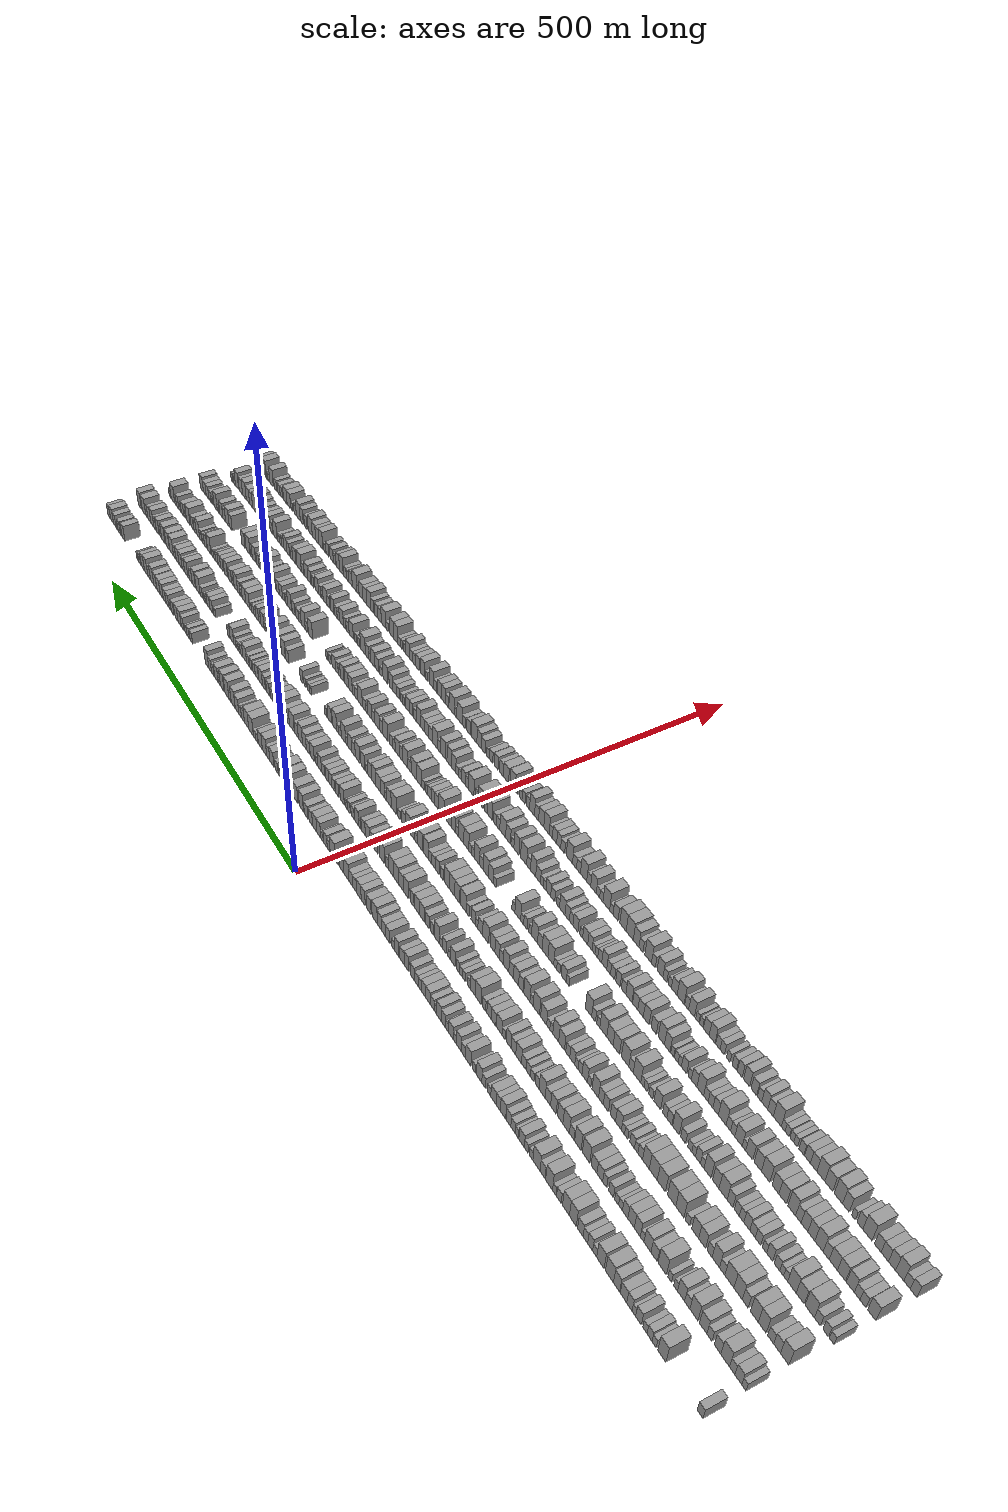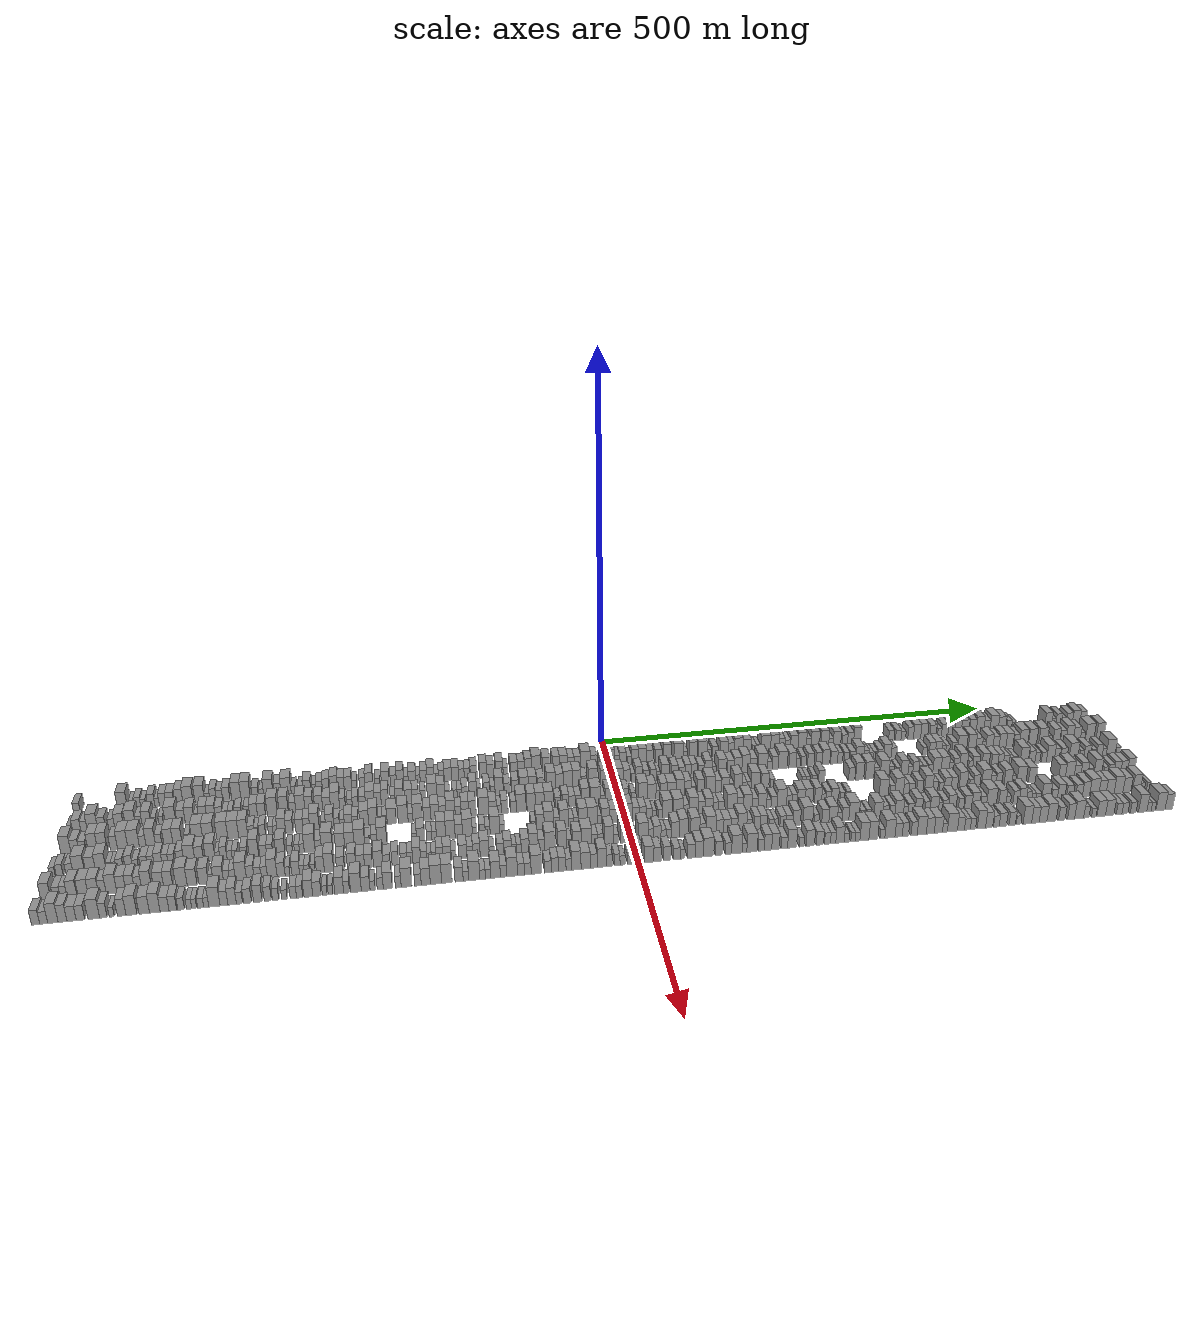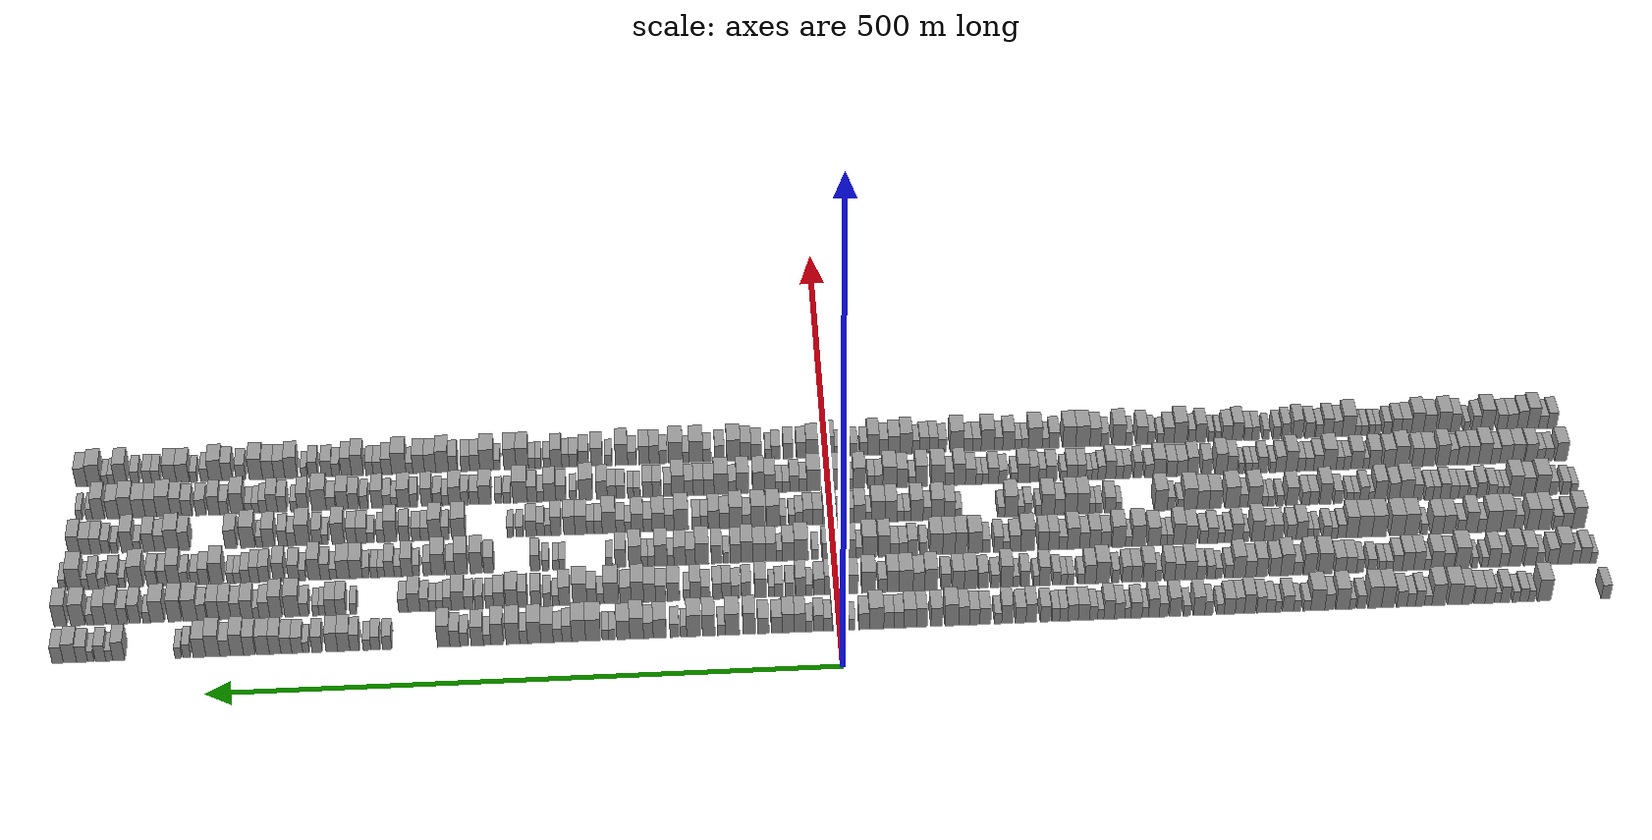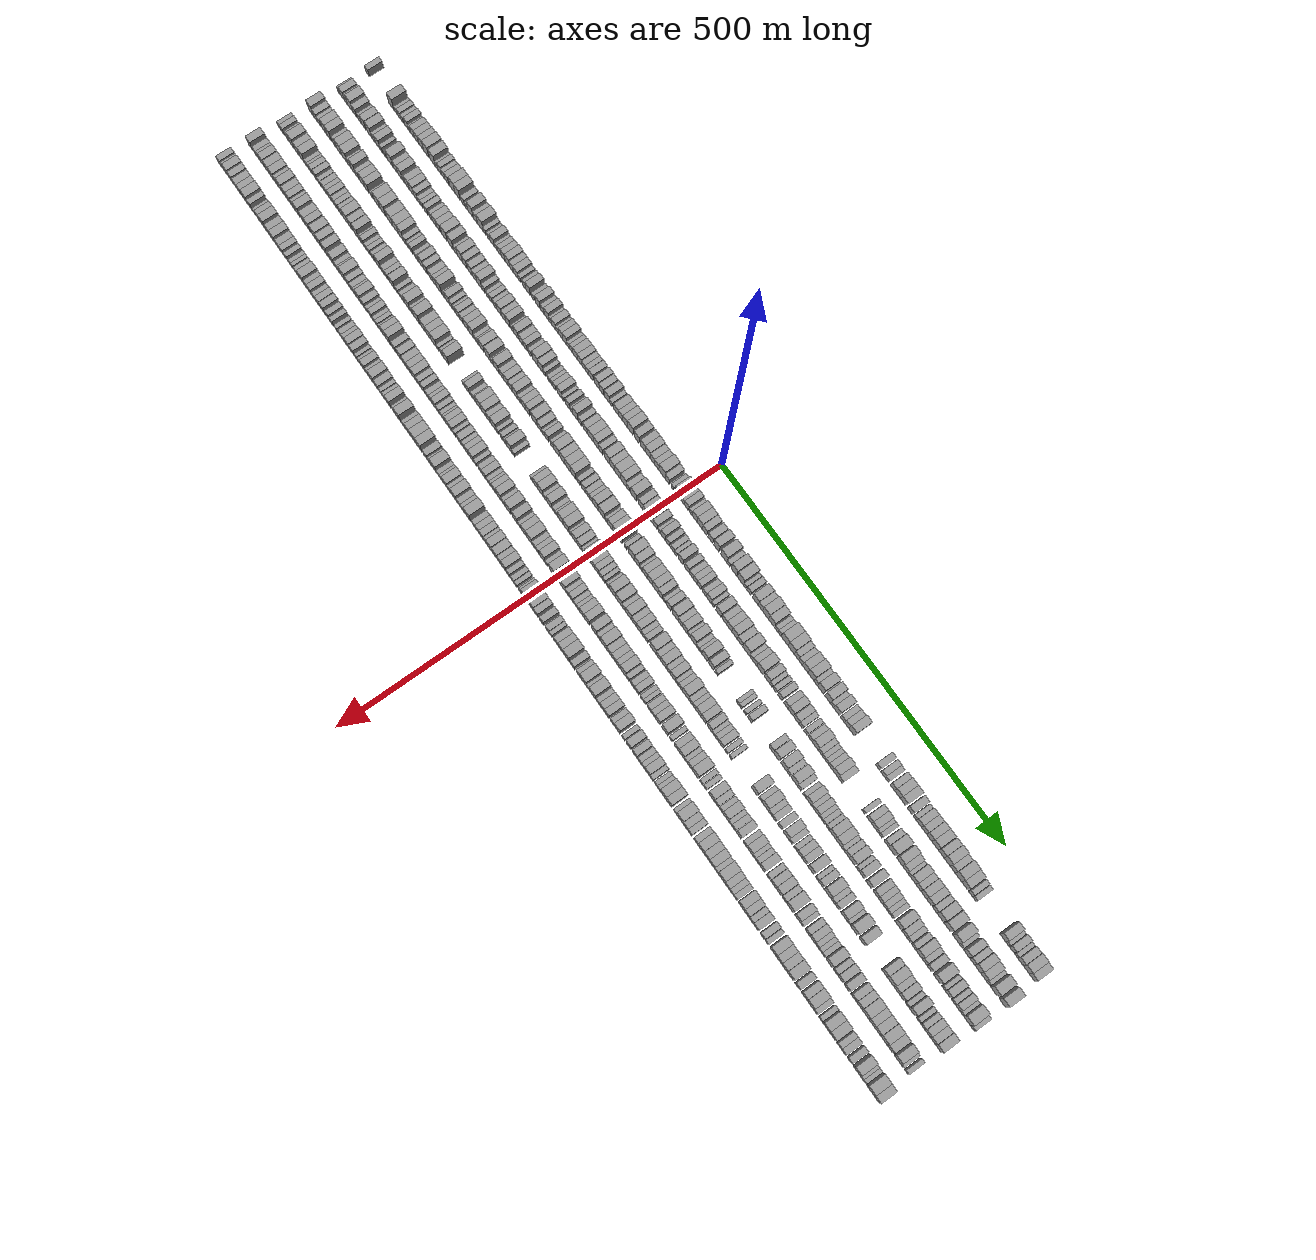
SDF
<sdf version="1.6">
 <world name="default">
  <scene>
   <sky><clouds><speed>12</speed></clouds></sky>
   <ambient>0.4 0.4 0.4 1</ambient>
   <background>0.7 0.7 0.7 1</background>
   <shadows>1</shadows>
  </scene>
  <gravity>0 0 -9.8066</gravity>
  <magnetic_field>6e-06 2.3e-05 -4.2e-05</magnetic_field>
  <physics default="0" name="default_physics" type="ode">
   <ode>
    <solver>
     <type>quick</type>
     <iters>10</iters>
     <sor>1.0</sor>
     <use_dynamic_moi_rescaling>0</use_dynamic_moi_rescaling>
    </solver>
    <constraints>
     <cfm>0</cfm>
     <erp>0.2</erp>
     <contact_max_correcting_vel>100</contact_max_correcting_vel>
     <contact_surface_layer>0.001</contact_surface_layer>
    </constraints>
   </ode>
   <max_step_size>0.004</max_step_size>
   <real_time_factor>1</real_time_factor>
   <real_time_update_rate>250</real_time_update_rate>
  </physics>
  <light name="sun" type="directional">
   <pose>0 0 10 0 0 0</pose>
   <diffuse>0.8 0.8 0.8 1</diffuse>
   <specular>0.2 0.2 0.2 1</specular>
   <attenuation>
    <range>1000</range>
    <constant>0.9</constant>
    <linear>0.01</linear>
    <quadratic>0.001</quadratic>
   </attenuation>
   <direction>-0.5 0.1 -0.9</direction>
  </light>
  <model name="building_1">
   <static>1</static>
   <pose>50.0000 -616.3699 0 0.000000 0.000000 0.000000</pose>
   <link name="link">
    <pose>0 0 7.50 0 0 0</pose>
    <collision name="collision"><geometry><box><size>20.0000 7.2602 15.0000</size></box></geometry></collision>
    <visual name="visual">
     <cast_shadows>0</cast_shadows>
     <geometry><box><size>20.0000 7.2602 15.0000</size></box></geometry>
     <material>
      <script>
       <uri>model://grey_wall/materials/scripts</uri>
       <uri>model://grey_wall/materials/textures</uri>
       <name>vrc/grey_wall</name>
      </script>
     </material>
    </visual>
   </link>
  </model>
  <model name="building_2">
   <static>1</static>
   <pose>50.0000 -566.4048 0 0.000000 0.000000 0.000000</pose>
   <link name="link">
    <pose>0 0 12.00 0 0 0</pose>
    <collision name="collision"><geometry><box><size>20.0000 10.8900 24.0000</size></box></geometry></collision>
    <visual name="visual">
     <cast_shadows>0</cast_shadows>
     <geometry><box><size>20.0000 10.8900 24.0000</size></box></geometry>
     <material>
      <script>
       <uri>model://grey_wall/materials/scripts</uri>
       <uri>model://grey_wall/materials/textures</uri>
       <name>vrc/grey_wall</name>
      </script>
     </material>
    </visual>
   </link>
  </model>
  <model name="building_3">
   <static>1</static>
   <pose>50.0000 -556.1488 0 0.000000 0.000000 0.000000</pose>
   <link name="link">
    <pose>0 0 6.00 0 0 0</pose>
    <collision name="collision"><geometry><box><size>20.0000 5.6221 12.0000</size></box></geometry></collision>
    <visual name="visual">
     <cast_shadows>0</cast_shadows>
     <geometry><box><size>20.0000 5.6221 12.0000</size></box></geometry>
     <material>
      <script>
       <uri>model://grey_wall/materials/scripts</uri>
       <uri>model://grey_wall/materials/textures</uri>
       <name>vrc/grey_wall</name>
      </script>
     </material>
    </visual>
   </link>
  </model>
  <model name="building_4">
   <static>1</static>
   <pose>50.0000 -549.8595 0 0.000000 0.000000 0.000000</pose>
   <link name="link">
    <pose>0 0 7.50 0 0 0</pose>
    <collision name="collision"><geometry><box><size>20.0000 6.9566 15.0000</size></box></geometry></collision>
    <visual name="visual">
     <cast_shadows>0</cast_shadows>
     <geometry><box><size>20.0000 6.9566 15.0000</size></box></geometry>
     <material>
      <script>
       <uri>model://grey_wall/materials/scripts</uri>
       <uri>model://grey_wall/materials/textures</uri>
       <name>vrc/grey_wall</name>
      </script>
     </material>
    </visual>
   </link>
  </model>
  <model name="building_5">
   <static>1</static>
   <pose>50.0000 -543.4747 0 0.000000 0.000000 0.000000</pose>
   <link name="link">
    <pose>0 0 6.00 0 0 0</pose>
    <collision name="collision"><geometry><box><size>20.0000 5.8130 12.0000</size></box></geometry></collision>
    <visual name="visual">
     <cast_shadows>0</cast_shadows>
     <geometry><box><size>20.0000 5.8130 12.0000</size></box></geometry>
     <material>
      <script>
       <uri>model://grey_wall/materials/scripts</uri>
       <uri>model://grey_wall/materials/textures</uri>
       <name>vrc/grey_wall</name>
      </script>
     </material>
    </visual>
   </link>
  </model>
  <model name="building_6">
   <static>1</static>
   <pose>50.0000 -534.6641 0 0.000000 0.000000 0.000000</pose>
   <link name="link">
    <pose>0 0 9.00 0 0 0</pose>
    <collision name="collision"><geometry><box><size>20.0000 7.8081 18.0000</size></box></geometry></collision>
    <visual name="visual">
     <cast_shadows>0</cast_shadows>
     <geometry><box><size>20.0000 7.8081 18.0000</size></box></geometry>
     <material>
      <script>
       <uri>model://grey_wall/materials/scripts</uri>
       <uri>model://grey_wall/materials/textures</uri>
       <name>vrc/grey_wall</name>
      </script>
     </material>
    </visual>
   </link>
  </model>
  <model name="building_7">
   <static>1</static>
   <pose>50.0000 -528.2909 0 0.000000 0.000000 0.000000</pose>
   <link name="link">
    <pose>0 0 6.00 0 0 0</pose>
    <collision name="collision"><geometry><box><size>20.0000 4.9383 12.0000</size></box></geometry></collision>
    <visual name="visual">
     <cast_shadows>0</cast_shadows>
     <geometry><box><size>20.0000 4.9383 12.0000</size></box></geometry>
     <material>
      <script>
       <uri>model://grey_wall/materials/scripts</uri>
       <uri>model://grey_wall/materials/textures</uri>
       <name>vrc/grey_wall</name>
      </script>
     </material>
    </visual>
   </link>
  </model>
  <model name="building_8">
   <static>1</static>
   <pose>50.0000 -522.0054 0 0.000000 0.000000 0.000000</pose>
   <link name="link">
    <pose>0 0 9.00 0 0 0</pose>
    <collision name="collision"><geometry><box><size>20.0000 7.6328 18.0000</size></box></geometry></collision>
    <visual name="visual">
     <cast_shadows>0</cast_shadows>
     <geometry><box><size>20.0000 7.6328 18.0000</size></box></geometry>
     <material>
      <script>
       <uri>model://grey_wall/materials/scripts</uri>
       <uri>model://grey_wall/materials/textures</uri>
       <name>vrc/grey_wall</name>
      </script>
     </material>
    </visual>
   </link>
  </model>
  <model name="building_9">
   <static>1</static>
   <pose>50.0000 -513.7123 0 0.000000 0.000000 0.000000</pose>
   <link name="link">
    <pose>0 0 9.00 0 0 0</pose>
    <collision name="collision"><geometry><box><size>20.0000 8.9535 18.0000</size></box></geometry></collision>
    <visual name="visual">
     <cast_shadows>0</cast_shadows>
     <geometry><box><size>20.0000 8.9535 18.0000</size></box></geometry>
     <material>
      <script>
       <uri>model://grey_wall/materials/scripts</uri>
       <uri>model://grey_wall/materials/textures</uri>
       <name>vrc/grey_wall</name>
      </script>
     </material>
    </visual>
   </link>
  </model>
  <model name="building_10">
   <static>1</static>
   <pose>50.0000 -503.8203 0 0.000000 0.000000 0.000000</pose>
   <link name="link">
    <pose>0 0 10.50 0 0 0</pose>
    <collision name="collision"><geometry><box><size>20.0000 8.8305 21.0000</size></box></geometry></collision>
    <visual name="visual">
     <cast_shadows>0</cast_shadows>
     <geometry><box><size>20.0000 8.8305 21.0000</size></box></geometry>
     <material>
      <script>
       <uri>model://grey_wall/materials/scripts</uri>
       <uri>model://grey_wall/materials/textures</uri>
       <name>vrc/grey_wall</name>
      </script>
     </material>
    </visual>
   </link>
  </model>
  <model name="building_11">
   <static>1</static>
   <pose>50.0000 -493.7146 0 0.000000 0.000000 0.000000</pose>
   <link name="link">
    <pose>0 0 12.00 0 0 0</pose>
    <collision name="collision"><geometry><box><size>20.0000 11.3810 24.0000</size></box></geometry></collision>
    <visual name="visual">
     <cast_shadows>0</cast_shadows>
     <geometry><box><size>20.0000 11.3810 24.0000</size></box></geometry>
     <material>
      <script>
       <uri>model://grey_wall/materials/scripts</uri>
       <uri>model://grey_wall/materials/textures</uri>
       <name>vrc/grey_wall</name>
      </script>
     </material>
    </visual>
   </link>
  </model>
  <model name="building_12">
   <static>1</static>
   <pose>50.0000 -480.6043 0 0.000000 0.000000 0.000000</pose>
   <link name="link">
    <pose>0 0 12.00 0 0 0</pose>
    <collision name="collision"><geometry><box><size>20.0000 10.8395 24.0000</size></box></geometry></collision>
    <visual name="visual">
     <cast_shadows>0</cast_shadows>
     <geometry><box><size>20.0000 10.8395 24.0000</size></box></geometry>
     <material>
      <script>
       <uri>model://grey_wall/materials/scripts</uri>
       <uri>model://grey_wall/materials/textures</uri>
       <name>vrc/grey_wall</name>
      </script>
     </material>
    </visual>
   </link>
  </model>
  <model name="building_13">
   <static>1</static>
   <pose>50.0000 -472.2145 0 0.000000 0.000000 0.000000</pose>
   <link name="link">
    <pose>0 0 6.00 0 0 0</pose>
    <collision name="collision"><geometry><box><size>20.0000 5.9401 12.0000</size></box></geometry></collision>
    <visual name="visual">
     <cast_shadows>0</cast_shadows>
     <geometry><box><size>20.0000 5.9401 12.0000</size></box></geometry>
     <material>
      <script>
       <uri>model://grey_wall/materials/scripts</uri>
       <uri>model://grey_wall/materials/textures</uri>
       <name>vrc/grey_wall</name>
      </script>
     </material>
    </visual>
   </link>
  </model>
  <model name="building_14">
   <static>1</static>
   <pose>50.0000 -465.6046 0 0.000000 0.000000 0.000000</pose>
   <link name="link">
    <pose>0 0 9.00 0 0 0</pose>
    <collision name="collision"><geometry><box><size>20.0000 7.2797 18.0000</size></box></geometry></collision>
    <visual name="visual">
     <cast_shadows>0</cast_shadows>
     <geometry><box><size>20.0000 7.2797 18.0000</size></box></geometry>
     <material>
      <script>
       <uri>model://grey_wall/materials/scripts</uri>
       <uri>model://grey_wall/materials/textures</uri>
       <name>vrc/grey_wall</name>
      </script>
     </material>
    </visual>
   </link>
  </model>
  <model name="building_15">
   <static>1</static>
   <pose>50.0000 -458.4976 0 0.000000 0.000000 0.000000</pose>
   <link name="link">
    <pose>0 0 7.50 0 0 0</pose>
    <collision name="collision"><geometry><box><size>20.0000 6.9343 15.0000</size></box></geometry></collision>
    <visual name="visual">
     <cast_shadows>0</cast_shadows>
     <geometry><box><size>20.0000 6.9343 15.0000</size></box></geometry>
     <material>
      <script>
       <uri>model://grey_wall/materials/scripts</uri>
       <uri>model://grey_wall/materials/textures</uri>
       <name>vrc/grey_wall</name>
      </script>
     </material>
    </visual>
   </link>
  </model>
  <model name="building_16">
   <static>1</static>
   <pose>50.0000 -450.9653 0 0.000000 0.000000 0.000000</pose>
   <link name="link">
    <pose>0 0 9.00 0 0 0</pose>
    <collision name="collision"><geometry><box><size>20.0000 8.1302 18.0000</size></box></geometry></collision>
    <visual name="visual">
     <cast_shadows>0</cast_shadows>
     <geometry><box><size>20.0000 8.1302 18.0000</size></box></geometry>
     <material>
      <script>
       <uri>model://grey_wall/materials/scripts</uri>
       <uri>model://grey_wall/materials/textures</uri>
       <name>vrc/grey_wall</name>
      </script>
     </material>
    </visual>
   </link>
  </model>
  <model name="building_17">
   <static>1</static>
   <pose>50.0000 -439.6916 0 0.000000 0.000000 0.000000</pose>
   <link name="link">
    <pose>0 0 12.00 0 0 0</pose>
    <collision name="collision"><geometry><box><size>20.0000 10.4172 24.0000</size></box></geometry></collision>
    <visual name="visual">
     <cast_shadows>0</cast_shadows>
     <geometry><box><size>20.0000 10.4172 24.0000</size></box></geometry>
     <material>
      <script>
       <uri>model://grey_wall/materials/scripts</uri>
       <uri>model://grey_wall/materials/textures</uri>
       <name>vrc/grey_wall</name>
      </script>
     </material>
    </visual>
   </link>
  </model>
  <model name="building_18">
   <static>1</static>
   <pose>50.0000 -429.1501 0 0.000000 0.000000 0.000000</pose>
   <link name="link">
    <pose>0 0 12.00 0 0 0</pose>
    <collision name="collision"><geometry><box><size>20.0000 10.6658 24.0000</size></box></geometry></collision>
    <visual name="visual">
     <cast_shadows>0</cast_shadows>
     <geometry><box><size>20.0000 10.6658 24.0000</size></box></geometry>
     <material>
      <script>
       <uri>model://grey_wall/materials/scripts</uri>
       <uri>model://grey_wall/materials/textures</uri>
       <name>vrc/grey_wall</name>
      </script>
     </material>
    </visual>
   </link>
  </model>
  <model name="building_19">
   <static>1</static>
   <pose>50.0000 -418.2169 0 0.000000 0.000000 0.000000</pose>
   <link name="link">
    <pose>0 0 7.50 0 0 0</pose>
    <collision name="collision"><geometry><box><size>20.0000 7.2005 15.0000</size></box></geometry></collision>
    <visual name="visual">
     <cast_shadows>0</cast_shadows>
     <geometry><box><size>20.0000 7.2005 15.0000</size></box></geometry>
     <material>
      <script>
       <uri>model://grey_wall/materials/scripts</uri>
       <uri>model://grey_wall/materials/textures</uri>
       <name>vrc/grey_wall</name>
      </script>
     </material>
    </visual>
   </link>
  </model>
  <model name="building_20">
   <static>1</static>
   <pose>50.0000 -411.0468 0 0.000000 0.000000 0.000000</pose>
   <link name="link">
    <pose>0 0 6.00 0 0 0</pose>
    <collision name="collision"><geometry><box><size>20.0000 5.1398 12.0000</size></box></geometry></collision>
    <visual name="visual">
     <cast_shadows>0</cast_shadows>
     <geometry><box><size>20.0000 5.1398 12.0000</size></box></geometry>
     <material>
      <script>
       <uri>model://grey_wall/materials/scripts</uri>
       <uri>model://grey_wall/materials/textures</uri>
       <name>vrc/grey_wall</name>
      </script>
     </material>
    </visual>
   </link>
  </model>
  <model name="building_21">
   <static>1</static>
   <pose>50.0000 -403.0374 0 0.000000 0.000000 0.000000</pose>
   <link name="link">
    <pose>0 0 12.00 0 0 0</pose>
    <collision name="collision"><geometry><box><size>20.0000 10.8790 24.0000</size></box></geometry></collision>
    <visual name="visual">
     <cast_shadows>0</cast_shadows>
     <geometry><box><size>20.0000 10.8790 24.0000</size></box></geometry>
     <material>
      <script>
       <uri>model://grey_wall/materials/scripts</uri>
       <uri>model://grey_wall/materials/textures</uri>
       <name>vrc/grey_wall</name>
      </script>
     </material>
    </visual>
   </link>
  </model>
  <model name="building_22">
   <static>1</static>
   <pose>50.0000 -392.6774 0 0.000000 0.000000 0.000000</pose>
   <link name="link">
    <pose>0 0 9.00 0 0 0</pose>
    <collision name="collision"><geometry><box><size>20.0000 7.8410 18.0000</size></box></geometry></collision>
    <visual name="visual">
     <cast_shadows>0</cast_shadows>
     <geometry><box><size>20.0000 7.8410 18.0000</size></box></geometry>
     <material>
      <script>
       <uri>model://grey_wall/materials/scripts</uri>
       <uri>model://grey_wall/materials/textures</uri>
       <name>vrc/grey_wall</name>
      </script>
     </material>
    </visual>
   </link>
  </model>
  <model name="building_23">
   <static>1</static>
   <pose>50.0000 -383.0154 0 0.000000 0.000000 0.000000</pose>
   <link name="link">
    <pose>0 0 12.00 0 0 0</pose>
    <collision name="collision"><geometry><box><size>20.0000 11.4830 24.0000</size></box></geometry></collision>
    <visual name="visual">
     <cast_shadows>0</cast_shadows>
     <geometry><box><size>20.0000 11.4830 24.0000</size></box></geometry>
     <material>
      <script>
       <uri>model://grey_wall/materials/scripts</uri>
       <uri>model://grey_wall/materials/textures</uri>
       <name>vrc/grey_wall</name>
      </script>
     </material>
    </visual>
   </link>
  </model>
  <model name="building_24">
   <static>1</static>
   <pose>50.0000 -374.3030 0 0.000000 0.000000 0.000000</pose>
   <link name="link">
    <pose>0 0 6.00 0 0 0</pose>
    <collision name="collision"><geometry><box><size>20.0000 5.9419 12.0000</size></box></geometry></collision>
    <visual name="visual">
     <cast_shadows>0</cast_shadows>
     <geometry><box><size>20.0000 5.9419 12.0000</size></box></geometry>
     <material>
      <script>
       <uri>model://grey_wall/materials/scripts</uri>
       <uri>model://grey_wall/materials/textures</uri>
       <name>vrc/grey_wall</name>
      </script>
     </material>
    </visual>
   </link>
  </model>
  <model name="building_25">
   <static>1</static>
   <pose>50.0000 -366.4054 0 0.000000 0.000000 0.000000</pose>
   <link name="link">
    <pose>0 0 6.00 0 0 0</pose>
    <collision name="collision"><geometry><box><size>20.0000 5.8532 12.0000</size></box></geometry></collision>
    <visual name="visual">
     <cast_shadows>0</cast_shadows>
     <geometry><box><size>20.0000 5.8532 12.0000</size></box></geometry>
     <material>
      <script>
       <uri>model://grey_wall/materials/scripts</uri>
       <uri>model://grey_wall/materials/textures</uri>
       <name>vrc/grey_wall</name>
      </script>
     </material>
    </visual>
   </link>
  </model>
  <model name="building_26">
   <static>1</static>
   <pose>50.0000 -358.9968 0 0.000000 0.000000 0.000000</pose>
   <link name="link">
    <pose>0 0 9.00 0 0 0</pose>
    <collision name="collision"><geometry><box><size>20.0000 8.9639 18.0000</size></box></geometry></collision>
    <visual name="visual">
     <cast_shadows>0</cast_shadows>
     <geometry><box><size>20.0000 8.9639 18.0000</size></box></geometry>
     <material>
      <script>
       <uri>model://grey_wall/materials/scripts</uri>
       <uri>model://grey_wall/materials/textures</uri>
       <name>vrc/grey_wall</name>
      </script>
     </material>
    </visual>
   </link>
  </model>
  <model name="building_27">
   <static>1</static>
   <pose>50.0000 -351.0459 0 0.000000 0.000000 0.000000</pose>
   <link name="link">
    <pose>0 0 6.00 0 0 0</pose>
    <collision name="collision"><geometry><box><size>20.0000 4.9378 12.0000</size></box></geometry></collision>
    <visual name="visual">
     <cast_shadows>0</cast_shadows>
     <geometry><box><size>20.0000 4.9378 12.0000</size></box></geometry>
     <material>
      <script>
       <uri>model://grey_wall/materials/scripts</uri>
       <uri>model://grey_wall/materials/textures</uri>
       <name>vrc/grey_wall</name>
      </script>
     </material>
    </visual>
   </link>
  </model>
  <model name="building_28">
   <static>1</static>
   <pose>50.0000 -344.8875 0 0.000000 0.000000 0.000000</pose>
   <link name="link">
    <pose>0 0 7.50 0 0 0</pose>
    <collision name="collision"><geometry><box><size>20.0000 7.3791 15.0000</size></box></geometry></collision>
    <visual name="visual">
     <cast_shadows>0</cast_shadows>
     <geometry><box><size>20.0000 7.3791 15.0000</size></box></geometry>
     <material>
      <script>
       <uri>model://grey_wall/materials/scripts</uri>
       <uri>model://grey_wall/materials/textures</uri>
       <name>vrc/grey_wall</name>
      </script>
     </material>
    </visual>
   </link>
  </model>
  <model name="building_29">
   <static>1</static>
   <pose>50.0000 -337.4229 0 0.000000 0.000000 0.000000</pose>
   <link name="link">
    <pose>0 0 9.00 0 0 0</pose>
    <collision name="collision"><geometry><box><size>20.0000 7.5499 18.0000</size></box></geometry></collision>
    <visual name="visual">
     <cast_shadows>0</cast_shadows>
     <geometry><box><size>20.0000 7.5499 18.0000</size></box></geometry>
     <material>
      <script>
       <uri>model://grey_wall/materials/scripts</uri>
       <uri>model://grey_wall/materials/textures</uri>
       <name>vrc/grey_wall</name>
      </script>
     </material>
    </visual>
   </link>
  </model>
  <model name="building_30">
   <static>1</static>
   <pose>50.0000 -328.2033 0 0.000000 0.000000 0.000000</pose>
   <link name="link">
    <pose>0 0 10.50 0 0 0</pose>
    <collision name="collision"><geometry><box><size>20.0000 8.8892 21.0000</size></box></geometry></collision>
    <visual name="visual">
     <cast_shadows>0</cast_shadows>
     <geometry><box><size>20.0000 8.8892 21.0000</size></box></geometry>
     <material>
      <script>
       <uri>model://grey_wall/materials/scripts</uri>
       <uri>model://grey_wall/materials/textures</uri>
       <name>vrc/grey_wall</name>
      </script>
     </material>
    </visual>
   </link>
  </model>
  <model name="building_31">
   <static>1</static>
   <pose>50.0000 -320.0710 0 0.000000 0.000000 0.000000</pose>
   <link name="link">
    <pose>0 0 9.00 0 0 0</pose>
    <collision name="collision"><geometry><box><size>20.0000 7.3755 18.0000</size></box></geometry></collision>
    <visual name="visual">
     <cast_shadows>0</cast_shadows>
     <geometry><box><size>20.0000 7.3755 18.0000</size></box></geometry>
     <material>
      <script>
       <uri>model://grey_wall/materials/scripts</uri>
       <uri>model://grey_wall/materials/textures</uri>
       <name>vrc/grey_wall</name>
      </script>
     </material>
    </visual>
   </link>
  </model>
  <model name="building_32">
   <static>1</static>
   <pose>50.0000 -311.9032 0 0.000000 0.000000 0.000000</pose>
   <link name="link">
    <pose>0 0 9.00 0 0 0</pose>
    <collision name="collision"><geometry><box><size>20.0000 8.9600 18.0000</size></box></geometry></collision>
    <visual name="visual">
     <cast_shadows>0</cast_shadows>
     <geometry><box><size>20.0000 8.9600 18.0000</size></box></geometry>
     <material>
      <script>
       <uri>model://grey_wall/materials/scripts</uri>
       <uri>model://grey_wall/materials/textures</uri>
       <name>vrc/grey_wall</name>
      </script>
     </material>
    </visual>
   </link>
  </model>
  <model name="building_33">
   <static>1</static>
   <pose>50.0000 -304.4549 0 0.000000 0.000000 0.000000</pose>
   <link name="link">
    <pose>0 0 6.00 0 0 0</pose>
    <collision name="collision"><geometry><box><size>20.0000 5.9368 12.0000</size></box></geometry></collision>
    <visual name="visual">
     <cast_shadows>0</cast_shadows>
     <geometry><box><size>20.0000 5.9368 12.0000</size></box></geometry>
     <material>
      <script>
       <uri>model://grey_wall/materials/scripts</uri>
       <uri>model://grey_wall/materials/textures</uri>
       <name>vrc/grey_wall</name>
      </script>
     </material>
    </visual>
   </link>
  </model>
  <model name="building_34">
   <static>1</static>
   <pose>50.0000 -295.1882 0 0.000000 0.000000 0.000000</pose>
   <link name="link">
    <pose>0 0 7.50 0 0 0</pose>
    <collision name="collision"><geometry><box><size>20.0000 6.5967 15.0000</size></box></geometry></collision>
    <visual name="visual">
     <cast_shadows>0</cast_shadows>
     <geometry><box><size>20.0000 6.5967 15.0000</size></box></geometry>
     <material>
      <script>
       <uri>model://grey_wall/materials/scripts</uri>
       <uri>model://grey_wall/materials/textures</uri>
       <name>vrc/grey_wall</name>
      </script>
     </material>
    </visual>
   </link>
  </model>
  <model name="building_35">
   <static>1</static>
   <pose>50.0000 -287.3122 0 0.000000 0.000000 0.000000</pose>
   <link name="link">
    <pose>0 0 10.50 0 0 0</pose>
    <collision name="collision"><geometry><box><size>20.0000 9.1552 21.0000</size></box></geometry></collision>
    <visual name="visual">
     <cast_shadows>0</cast_shadows>
     <geometry><box><size>20.0000 9.1552 21.0000</size></box></geometry>
     <material>
      <script>
       <uri>model://grey_wall/materials/scripts</uri>
       <uri>model://grey_wall/materials/textures</uri>
       <name>vrc/grey_wall</name>
      </script>
     </material>
    </visual>
   </link>
  </model>
  <model name="building_36">
   <static>1</static>
   <pose>50.0000 -277.7473 0 0.000000 0.000000 0.000000</pose>
   <link name="link">
    <pose>0 0 6.00 0 0 0</pose>
    <collision name="collision"><geometry><box><size>20.0000 5.9745 12.0000</size></box></geometry></collision>
    <visual name="visual">
     <cast_shadows>0</cast_shadows>
     <geometry><box><size>20.0000 5.9745 12.0000</size></box></geometry>
     <material>
      <script>
       <uri>model://grey_wall/materials/scripts</uri>
       <uri>model://grey_wall/materials/textures</uri>
       <name>vrc/grey_wall</name>
      </script>
     </material>
    </visual>
   </link>
  </model>
  <model name="building_37">
   <static>1</static>
   <pose>50.0000 -268.0813 0 0.000000 0.000000 0.000000</pose>
   <link name="link">
    <pose>0 0 10.50 0 0 0</pose>
    <collision name="collision"><geometry><box><size>20.0000 9.3576 21.0000</size></box></geometry></collision>
    <visual name="visual">
     <cast_shadows>0</cast_shadows>
     <geometry><box><size>20.0000 9.3576 21.0000</size></box></geometry>
     <material>
      <script>
       <uri>model://grey_wall/materials/scripts</uri>
       <uri>model://grey_wall/materials/textures</uri>
       <name>vrc/grey_wall</name>
      </script>
     </material>
    </visual>
   </link>
  </model>
  <model name="building_38">
   <static>1</static>
   <pose>50.0000 -258.7891 0 0.000000 0.000000 0.000000</pose>
   <link name="link">
    <pose>0 0 7.50 0 0 0</pose>
    <collision name="collision"><geometry><box><size>20.0000 7.2269 15.0000</size></box></geometry></collision>
    <visual name="visual">
     <cast_shadows>0</cast_shadows>
     <geometry><box><size>20.0000 7.2269 15.0000</size></box></geometry>
     <material>
      <script>
       <uri>model://grey_wall/materials/scripts</uri>
       <uri>model://grey_wall/materials/textures</uri>
       <name>vrc/grey_wall</name>
      </script>
     </material>
    </visual>
   </link>
  </model>
  <model name="building_39">
   <static>1</static>
   <pose>50.0000 -250.8668 0 0.000000 0.000000 0.000000</pose>
   <link name="link">
    <pose>0 0 10.50 0 0 0</pose>
    <collision name="collision"><geometry><box><size>20.0000 8.6175 21.0000</size></box></geometry></collision>
    <visual name="visual">
     <cast_shadows>0</cast_shadows>
     <geometry><box><size>20.0000 8.6175 21.0000</size></box></geometry>
     <material>
      <script>
       <uri>model://grey_wall/materials/scripts</uri>
       <uri>model://grey_wall/materials/textures</uri>
       <name>vrc/grey_wall</name>
      </script>
     </material>
    </visual>
   </link>
  </model>
  <model name="building_40">
   <static>1</static>
   <pose>50.0000 -243.9789 0 0.000000 0.000000 0.000000</pose>
   <link name="link">
    <pose>0 0 6.00 0 0 0</pose>
    <collision name="collision"><geometry><box><size>20.0000 5.1584 12.0000</size></box></geometry></collision>
    <visual name="visual">
     <cast_shadows>0</cast_shadows>
     <geometry><box><size>20.0000 5.1584 12.0000</size></box></geometry>
     <material>
      <script>
       <uri>model://grey_wall/materials/scripts</uri>
       <uri>model://grey_wall/materials/textures</uri>
       <name>vrc/grey_wall</name>
      </script>
     </material>
    </visual>
   </link>
  </model>
  <model name="building_41">
   <static>1</static>
   <pose>50.0000 -236.9094 0 0.000000 0.000000 0.000000</pose>
   <link name="link">
    <pose>0 0 9.00 0 0 0</pose>
    <collision name="collision"><geometry><box><size>20.0000 8.9805 18.0000</size></box></geometry></collision>
    <visual name="visual">
     <cast_shadows>0</cast_shadows>
     <geometry><box><size>20.0000 8.9805 18.0000</size></box></geometry>
     <material>
      <script>
       <uri>model://grey_wall/materials/scripts</uri>
       <uri>model://grey_wall/materials/textures</uri>
       <name>vrc/grey_wall</name>
      </script>
     </material>
    </visual>
   </link>
  </model>
  <model name="building_42">
   <static>1</static>
   <pose>50.0000 -229.9395 0 0.000000 0.000000 0.000000</pose>
   <link name="link">
    <pose>0 0 6.00 0 0 0</pose>
    <collision name="collision"><geometry><box><size>20.0000 4.9593 12.0000</size></box></geometry></collision>
    <visual name="visual">
     <cast_shadows>0</cast_shadows>
     <geometry><box><size>20.0000 4.9593 12.0000</size></box></geometry>
     <material>
      <script>
       <uri>model://grey_wall/materials/scripts</uri>
       <uri>model://grey_wall/materials/textures</uri>
       <name>vrc/grey_wall</name>
      </script>
     </material>
    </visual>
   </link>
  </model>
  <model name="building_43">
   <static>1</static>
   <pose>50.0000 -223.4238 0 0.000000 0.000000 0.000000</pose>
   <link name="link">
    <pose>0 0 9.00 0 0 0</pose>
    <collision name="collision"><geometry><box><size>20.0000 8.0720 18.0000</size></box></geometry></collision>
    <visual name="visual">
     <cast_shadows>0</cast_shadows>
     <geometry><box><size>20.0000 8.0720 18.0000</size></box></geometry>
     <material>
      <script>
       <uri>model://grey_wall/materials/scripts</uri>
       <uri>model://grey_wall/materials/textures</uri>
       <name>vrc/grey_wall</name>
      </script>
     </material>
    </visual>
   </link>
  </model>
  <model name="building_44">
   <static>1</static>
   <pose>50.0000 -215.0772 0 0.000000 0.000000 0.000000</pose>
   <link name="link">
    <pose>0 0 10.50 0 0 0</pose>
    <collision name="collision"><geometry><box><size>20.0000 8.6213 21.0000</size></box></geometry></collision>
    <visual name="visual">
     <cast_shadows>0</cast_shadows>
     <geometry><box><size>20.0000 8.6213 21.0000</size></box></geometry>
     <material>
      <script>
       <uri>model://grey_wall/materials/scripts</uri>
       <uri>model://grey_wall/materials/textures</uri>
       <name>vrc/grey_wall</name>
      </script>
     </material>
    </visual>
   </link>
  </model>
  <model name="building_45">
   <static>1</static>
   <pose>50.0000 -208.2538 0 0.000000 0.000000 0.000000</pose>
   <link name="link">
    <pose>0 0 6.00 0 0 0</pose>
    <collision name="collision"><geometry><box><size>20.0000 5.0254 12.0000</size></box></geometry></collision>
    <visual name="visual">
     <cast_shadows>0</cast_shadows>
     <geometry><box><size>20.0000 5.0254 12.0000</size></box></geometry>
     <material>
      <script>
       <uri>model://grey_wall/materials/scripts</uri>
       <uri>model://grey_wall/materials/textures</uri>
       <name>vrc/grey_wall</name>
      </script>
     </material>
    </visual>
   </link>
  </model>
  <model name="building_46">
   <static>1</static>
   <pose>50.0000 -202.4890 0 0.000000 0.000000 0.000000</pose>
   <link name="link">
    <pose>0 0 7.50 0 0 0</pose>
    <collision name="collision"><geometry><box><size>20.0000 6.5043 15.0000</size></box></geometry></collision>
    <visual name="visual">
     <cast_shadows>0</cast_shadows>
     <geometry><box><size>20.0000 6.5043 15.0000</size></box></geometry>
     <material>
      <script>
       <uri>model://grey_wall/materials/scripts</uri>
       <uri>model://grey_wall/materials/textures</uri>
       <name>vrc/grey_wall</name>
      </script>
     </material>
    </visual>
   </link>
  </model>
  <model name="building_47">
   <static>1</static>
   <pose>50.0000 -194.7680 0 0.000000 0.000000 0.000000</pose>
   <link name="link">
    <pose>0 0 9.00 0 0 0</pose>
    <collision name="collision"><geometry><box><size>20.0000 8.9376 18.0000</size></box></geometry></collision>
    <visual name="visual">
     <cast_shadows>0</cast_shadows>
     <geometry><box><size>20.0000 8.9376 18.0000</size></box></geometry>
     <material>
      <script>
       <uri>model://grey_wall/materials/scripts</uri>
       <uri>model://grey_wall/materials/textures</uri>
       <name>vrc/grey_wall</name>
      </script>
     </material>
    </visual>
   </link>
  </model>
  <model name="building_48">
   <static>1</static>
   <pose>50.0000 -186.1059 0 0.000000 0.000000 0.000000</pose>
   <link name="link">
    <pose>0 0 9.00 0 0 0</pose>
    <collision name="collision"><geometry><box><size>20.0000 8.3866 18.0000</size></box></geometry></collision>
    <visual name="visual">
     <cast_shadows>0</cast_shadows>
     <geometry><box><size>20.0000 8.3866 18.0000</size></box></geometry>
     <material>
      <script>
       <uri>model://grey_wall/materials/scripts</uri>
       <uri>model://grey_wall/materials/textures</uri>
       <name>vrc/grey_wall</name>
      </script>
     </material>
    </visual>
   </link>
  </model>
  <model name="building_49">
   <static>1</static>
   <pose>50.0000 -178.6159 0 0.000000 0.000000 0.000000</pose>
   <link name="link">
    <pose>0 0 7.50 0 0 0</pose>
    <collision name="collision"><geometry><box><size>20.0000 6.5934 15.0000</size></box></geometry></collision>
    <visual name="visual">
     <cast_shadows>0</cast_shadows>
     <geometry><box><size>20.0000 6.5934 15.0000</size></box></geometry>
     <material>
      <script>
       <uri>model://grey_wall/materials/scripts</uri>
       <uri>model://grey_wall/materials/textures</uri>
       <name>vrc/grey_wall</name>
      </script>
     </material>
    </visual>
   </link>
  </model>
  <model name="building_50">
   <static>1</static>
   <pose>50.0000 -172.2222 0 0.000000 0.000000 0.000000</pose>
   <link name="link">
    <pose>0 0 7.50 0 0 0</pose>
    <collision name="collision"><geometry><box><size>20.0000 6.1939 15.0000</size></box></geometry></collision>
    <visual name="visual">
     <cast_shadows>0</cast_shadows>
     <geometry><box><size>20.0000 6.1939 15.0000</size></box></geometry>
     <material>
      <script>
       <uri>model://grey_wall/materials/scripts</uri>
       <uri>model://grey_wall/materials/textures</uri>
       <name>vrc/grey_wall</name>
      </script>
     </material>
    </visual>
   </link>
  </model>
  <model name="building_51">
   <static>1</static>
   <pose>50.0000 -164.0219 0 0.000000 0.000000 0.000000</pose>
   <link name="link">
    <pose>0 0 9.00 0 0 0</pose>
    <collision name="collision"><geometry><box><size>20.0000 8.2068 18.0000</size></box></geometry></collision>
    <visual name="visual">
     <cast_shadows>0</cast_shadows>
     <geometry><box><size>20.0000 8.2068 18.0000</size></box></geometry>
     <material>
      <script>
       <uri>model://grey_wall/materials/scripts</uri>
       <uri>model://grey_wall/materials/textures</uri>
       <name>vrc/grey_wall</name>
      </script>
     </material>
    </visual>
   </link>
  </model>
  <model name="building_52">
   <static>1</static>
   <pose>50.0000 -152.6471 0 0.000000 0.000000 0.000000</pose>
   <link name="link">
    <pose>0 0 10.50 0 0 0</pose>
    <collision name="collision"><geometry><box><size>20.0000 8.5427 21.0000</size></box></geometry></collision>
    <visual name="visual">
     <cast_shadows>0</cast_shadows>
     <geometry><box><size>20.0000 8.5427 21.0000</size></box></geometry>
     <material>
      <script>
       <uri>model://grey_wall/materials/scripts</uri>
       <uri>model://grey_wall/materials/textures</uri>
       <name>vrc/grey_wall</name>
      </script>
     </material>
    </visual>
   </link>
  </model>
  <model name="building_53">
   <static>1</static>
   <pose>50.0000 -144.0924 0 0.000000 0.000000 0.000000</pose>
   <link name="link">
    <pose>0 0 9.00 0 0 0</pose>
    <collision name="collision"><geometry><box><size>20.0000 8.5667 18.0000</size></box></geometry></collision>
    <visual name="visual">
     <cast_shadows>0</cast_shadows>
     <geometry><box><size>20.0000 8.5667 18.0000</size></box></geometry>
     <material>
      <script>
       <uri>model://grey_wall/materials/scripts</uri>
       <uri>model://grey_wall/materials/textures</uri>
       <name>vrc/grey_wall</name>
      </script>
     </material>
    </visual>
   </link>
  </model>
  <model name="building_54">
   <static>1</static>
   <pose>50.0000 -133.3445 0 0.000000 0.000000 0.000000</pose>
   <link name="link">
    <pose>0 0 10.50 0 0 0</pose>
    <collision name="collision"><geometry><box><size>20.0000 8.9291 21.0000</size></box></geometry></collision>
    <visual name="visual">
     <cast_shadows>0</cast_shadows>
     <geometry><box><size>20.0000 8.9291 21.0000</size></box></geometry>
     <material>
      <script>
       <uri>model://grey_wall/materials/scripts</uri>
       <uri>model://grey_wall/materials/textures</uri>
       <name>vrc/grey_wall</name>
      </script>
     </material>
    </visual>
   </link>
  </model>
  <model name="building_55">
   <static>1</static>
   <pose>50.0000 -126.0293 0 0.000000 0.000000 0.000000</pose>
   <link name="link">
    <pose>0 0 6.00 0 0 0</pose>
    <collision name="collision"><geometry><box><size>20.0000 5.7013 12.0000</size></box></geometry></collision>
    <visual name="visual">
     <cast_shadows>0</cast_shadows>
     <geometry><box><size>20.0000 5.7013 12.0000</size></box></geometry>
     <material>
      <script>
       <uri>model://grey_wall/materials/scripts</uri>
       <uri>model://grey_wall/materials/textures</uri>
       <name>vrc/grey_wall</name>
      </script>
     </material>
    </visual>
   </link>
  </model>
  <model name="building_56">
   <static>1</static>
   <pose>50.0000 -115.7260 0 0.000000 0.000000 0.000000</pose>
   <link name="link">
    <pose>0 0 9.00 0 0 0</pose>
    <collision name="collision"><geometry><box><size>20.0000 8.9053 18.0000</size></box></geometry></collision>
    <visual name="visual">
     <cast_shadows>0</cast_shadows>
     <geometry><box><size>20.0000 8.9053 18.0000</size></box></geometry>
     <material>
      <script>
       <uri>model://grey_wall/materials/scripts</uri>
       <uri>model://grey_wall/materials/textures</uri>
       <name>vrc/grey_wall</name>
      </script>
     </material>
    </visual>
   </link>
  </model>
  <model name="building_57">
   <static>1</static>
   <pose>50.0000 -107.1221 0 0.000000 0.000000 0.000000</pose>
   <link name="link">
    <pose>0 0 9.00 0 0 0</pose>
    <collision name="collision"><geometry><box><size>20.0000 8.3025 18.0000</size></box></geometry></collision>
    <visual name="visual">
     <cast_shadows>0</cast_shadows>
     <geometry><box><size>20.0000 8.3025 18.0000</size></box></geometry>
     <material>
      <script>
       <uri>model://grey_wall/materials/scripts</uri>
       <uri>model://grey_wall/materials/textures</uri>
       <name>vrc/grey_wall</name>
      </script>
     </material>
    </visual>
   </link>
  </model>
  <model name="building_58">
   <static>1</static>
   <pose>50.0000 -98.6853 0 0.000000 0.000000 0.000000</pose>
   <link name="link">
    <pose>0 0 10.50 0 0 0</pose>
    <collision name="collision"><geometry><box><size>20.0000 8.5711 21.0000</size></box></geometry></collision>
    <visual name="visual">
     <cast_shadows>0</cast_shadows>
     <geometry><box><size>20.0000 8.5711 21.0000</size></box></geometry>
     <material>
      <script>
       <uri>model://grey_wall/materials/scripts</uri>
       <uri>model://grey_wall/materials/textures</uri>
       <name>vrc/grey_wall</name>
      </script>
     </material>
    </visual>
   </link>
  </model>
  <model name="building_59">
   <static>1</static>
   <pose>50.0000 -88.9858 0 0.000000 0.000000 0.000000</pose>
   <link name="link">
    <pose>0 0 12.00 0 0 0</pose>
    <collision name="collision"><geometry><box><size>20.0000 10.8278 24.0000</size></box></geometry></collision>
    <visual name="visual">
     <cast_shadows>0</cast_shadows>
     <geometry><box><size>20.0000 10.8278 24.0000</size></box></geometry>
     <material>
      <script>
       <uri>model://grey_wall/materials/scripts</uri>
       <uri>model://grey_wall/materials/textures</uri>
       <name>vrc/grey_wall</name>
      </script>
     </material>
    </visual>
   </link>
  </model>
  <model name="building_60">
   <static>1</static>
   <pose>50.0000 -76.8893 0 0.000000 0.000000 0.000000</pose>
   <link name="link">
    <pose>0 0 10.50 0 0 0</pose>
    <collision name="collision"><geometry><box><size>20.0000 9.3653 21.0000</size></box></geometry></collision>
    <visual name="visual">
     <cast_shadows>0</cast_shadows>
     <geometry><box><size>20.0000 9.3653 21.0000</size></box></geometry>
     <material>
      <script>
       <uri>model://grey_wall/materials/scripts</uri>
       <uri>model://grey_wall/materials/textures</uri>
       <name>vrc/grey_wall</name>
      </script>
     </material>
    </visual>
   </link>
  </model>
  <model name="building_61">
   <static>1</static>
   <pose>50.0000 -64.9273 0 0.000000 0.000000 0.000000</pose>
   <link name="link">
    <pose>0 0 10.50 0 0 0</pose>
    <collision name="collision"><geometry><box><size>20.0000 8.5586 21.0000</size></box></geometry></collision>
    <visual name="visual">
     <cast_shadows>0</cast_shadows>
     <geometry><box><size>20.0000 8.5586 21.0000</size></box></geometry>
     <material>
      <script>
       <uri>model://grey_wall/materials/scripts</uri>
       <uri>model://grey_wall/materials/textures</uri>
       <name>vrc/grey_wall</name>
      </script>
     </material>
    </visual>
   </link>
  </model>
  <model name="building_62">
   <static>1</static>
   <pose>50.0000 -55.7597 0 0.000000 0.000000 0.000000</pose>
   <link name="link">
    <pose>0 0 10.50 0 0 0</pose>
    <collision name="collision"><geometry><box><size>20.0000 9.7767 21.0000</size></box></geometry></collision>
    <visual name="visual">
     <cast_shadows>0</cast_shadows>
     <geometry><box><size>20.0000 9.7767 21.0000</size></box></geometry>
     <material>
      <script>
       <uri>model://grey_wall/materials/scripts</uri>
       <uri>model://grey_wall/materials/textures</uri>
       <name>vrc/grey_wall</name>
      </script>
     </material>
    </visual>
   </link>
  </model>
  <model name="building_63">
   <static>1</static>
   <pose>50.0000 -46.8969 0 0.000000 0.000000 0.000000</pose>
   <link name="link">
    <pose>0 0 9.00 0 0 0</pose>
    <collision name="collision"><geometry><box><size>20.0000 7.9490 18.0000</size></box></geometry></collision>
    <visual name="visual">
     <cast_shadows>0</cast_shadows>
     <geometry><box><size>20.0000 7.9490 18.0000</size></box></geometry>
     <material>
      <script>
       <uri>model://grey_wall/materials/scripts</uri>
       <uri>model://grey_wall/materials/textures</uri>
       <name>vrc/grey_wall</name>
      </script>
     </material>
    </visual>
   </link>
  </model>
  <model name="building_64">
   <static>1</static>
   <pose>50.0000 -38.7612 0 0.000000 0.000000 0.000000</pose>
   <link name="link">
    <pose>0 0 9.00 0 0 0</pose>
    <collision name="collision"><geometry><box><size>20.0000 8.3224 18.0000</size></box></geometry></collision>
    <visual name="visual">
     <cast_shadows>0</cast_shadows>
     <geometry><box><size>20.0000 8.3224 18.0000</size></box></geometry>
     <material>
      <script>
       <uri>model://grey_wall/materials/scripts</uri>
       <uri>model://grey_wall/materials/textures</uri>
       <name>vrc/grey_wall</name>
      </script>
     </material>
    </visual>
   </link>
  </model>
  <model name="building_65">
   <static>1</static>
   <pose>50.0000 -28.8461 0 0.000000 0.000000 0.000000</pose>
   <link name="link">
    <pose>0 0 12.00 0 0 0</pose>
    <collision name="collision"><geometry><box><size>20.0000 11.5079 24.0000</size></box></geometry></collision>
    <visual name="visual">
     <cast_shadows>0</cast_shadows>
     <geometry><box><size>20.0000 11.5079 24.0000</size></box></geometry>
     <material>
      <script>
       <uri>model://grey_wall/materials/scripts</uri>
       <uri>model://grey_wall/materials/textures</uri>
       <name>vrc/grey_wall</name>
      </script>
     </material>
    </visual>
   </link>
  </model>
  <model name="building_66">
   <static>1</static>
   <pose>50.0000 -18.9739 0 0.000000 0.000000 0.000000</pose>
   <link name="link">
    <pose>0 0 9.00 0 0 0</pose>
    <collision name="collision"><geometry><box><size>20.0000 8.2365 18.0000</size></box></geometry></collision>
    <visual name="visual">
     <cast_shadows>0</cast_shadows>
     <geometry><box><size>20.0000 8.2365 18.0000</size></box></geometry>
     <material>
      <script>
       <uri>model://grey_wall/materials/scripts</uri>
       <uri>model://grey_wall/materials/textures</uri>
       <name>vrc/grey_wall</name>
      </script>
     </material>
    </visual>
   </link>
  </model>
  <model name="building_67">
   <static>1</static>
   <pose>50.0000 -9.2763 0 0.000000 0.000000 0.000000</pose>
   <link name="link">
    <pose>0 0 6.00 0 0 0</pose>
    <collision name="collision"><geometry><box><size>20.0000 5.1587 12.0000</size></box></geometry></collision>
    <visual name="visual">
     <cast_shadows>0</cast_shadows>
     <geometry><box><size>20.0000 5.1587 12.0000</size></box></geometry>
     <material>
      <script>
       <uri>model://grey_wall/materials/scripts</uri>
       <uri>model://grey_wall/materials/textures</uri>
       <name>vrc/grey_wall</name>
      </script>
     </material>
    </visual>
   </link>
  </model>
  <model name="building_68">
   <static>1</static>
   <pose>50.0000 1.0215 0 0.000000 0.000000 0.000000</pose>
   <link name="link">
    <pose>0 0 12.00 0 0 0</pose>
    <collision name="collision"><geometry><box><size>20.0000 11.4368 24.0000</size></box></geometry></collision>
    <visual name="visual">
     <cast_shadows>0</cast_shadows>
     <geometry><box><size>20.0000 11.4368 24.0000</size></box></geometry>
     <material>
      <script>
       <uri>model://grey_wall/materials/scripts</uri>
       <uri>model://grey_wall/materials/textures</uri>
       <name>vrc/grey_wall</name>
      </script>
     </material>
    </visual>
   </link>
  </model>
  <model name="building_69">
   <static>1</static>
   <pose>50.0000 9.9704 0 0.000000 0.000000 0.000000</pose>
   <link name="link">
    <pose>0 0 7.50 0 0 0</pose>
    <collision name="collision"><geometry><box><size>20.0000 6.4611 15.0000</size></box></geometry></collision>
    <visual name="visual">
     <cast_shadows>0</cast_shadows>
     <geometry><box><size>20.0000 6.4611 15.0000</size></box></geometry>
     <material>
      <script>
       <uri>model://grey_wall/materials/scripts</uri>
       <uri>model://grey_wall/materials/textures</uri>
       <name>vrc/grey_wall</name>
      </script>
     </material>
    </visual>
   </link>
  </model>
  <model name="building_70">
   <static>1</static>
   <pose>50.0000 17.1751 0 0.000000 0.000000 0.000000</pose>
   <link name="link">
    <pose>0 0 9.00 0 0 0</pose>
    <collision name="collision"><geometry><box><size>20.0000 7.9483 18.0000</size></box></geometry></collision>
    <visual name="visual">
     <cast_shadows>0</cast_shadows>
     <geometry><box><size>20.0000 7.9483 18.0000</size></box></geometry>
     <material>
      <script>
       <uri>model://grey_wall/materials/scripts</uri>
       <uri>model://grey_wall/materials/textures</uri>
       <name>vrc/grey_wall</name>
      </script>
     </material>
    </visual>
   </link>
  </model>
  <model name="building_71">
   <static>1</static>
   <pose>50.0000 25.0140 0 0.000000 0.000000 0.000000</pose>
   <link name="link">
    <pose>0 0 6.00 0 0 0</pose>
    <collision name="collision"><geometry><box><size>20.0000 5.7295 12.0000</size></box></geometry></collision>
    <visual name="visual">
     <cast_shadows>0</cast_shadows>
     <geometry><box><size>20.0000 5.7295 12.0000</size></box></geometry>
     <material>
      <script>
       <uri>model://grey_wall/materials/scripts</uri>
       <uri>model://grey_wall/materials/textures</uri>
       <name>vrc/grey_wall</name>
      </script>
     </material>
    </visual>
   </link>
  </model>
  <model name="building_72">
   <static>1</static>
   <pose>50.0000 32.2604 0 0.000000 0.000000 0.000000</pose>
   <link name="link">
    <pose>0 0 10.50 0 0 0</pose>
    <collision name="collision"><geometry><box><size>20.0000 8.7634 21.0000</size></box></geometry></collision>
    <visual name="visual">
     <cast_shadows>0</cast_shadows>
     <geometry><box><size>20.0000 8.7634 21.0000</size></box></geometry>
     <material>
      <script>
       <uri>model://grey_wall/materials/scripts</uri>
       <uri>model://grey_wall/materials/textures</uri>
       <name>vrc/grey_wall</name>
      </script>
     </material>
    </visual>
   </link>
  </model>
  <model name="building_73">
   <static>1</static>
   <pose>50.0000 41.5729 0 0.000000 0.000000 0.000000</pose>
   <link name="link">
    <pose>0 0 10.50 0 0 0</pose>
    <collision name="collision"><geometry><box><size>20.0000 9.8615 21.0000</size></box></geometry></collision>
    <visual name="visual">
     <cast_shadows>0</cast_shadows>
     <geometry><box><size>20.0000 9.8615 21.0000</size></box></geometry>
     <material>
      <script>
       <uri>model://grey_wall/materials/scripts</uri>
       <uri>model://grey_wall/materials/textures</uri>
       <name>vrc/grey_wall</name>
      </script>
     </material>
    </visual>
   </link>
  </model>
  <model name="building_74">
   <static>1</static>
   <pose>50.0000 50.6926 0 0.000000 0.000000 0.000000</pose>
   <link name="link">
    <pose>0 0 9.00 0 0 0</pose>
    <collision name="collision"><geometry><box><size>20.0000 8.3780 18.0000</size></box></geometry></collision>
    <visual name="visual">
     <cast_shadows>0</cast_shadows>
     <geometry><box><size>20.0000 8.3780 18.0000</size></box></geometry>
     <material>
      <script>
       <uri>model://grey_wall/materials/scripts</uri>
       <uri>model://grey_wall/materials/textures</uri>
       <name>vrc/grey_wall</name>
      </script>
     </material>
    </visual>
   </link>
  </model>
  <model name="building_75">
   <static>1</static>
   <pose>50.0000 61.2764 0 0.000000 0.000000 0.000000</pose>
   <link name="link">
    <pose>0 0 9.00 0 0 0</pose>
    <collision name="collision"><geometry><box><size>20.0000 8.7896 18.0000</size></box></geometry></collision>
    <visual name="visual">
     <cast_shadows>0</cast_shadows>
     <geometry><box><size>20.0000 8.7896 18.0000</size></box></geometry>
     <material>
      <script>
       <uri>model://grey_wall/materials/scripts</uri>
       <uri>model://grey_wall/materials/textures</uri>
       <name>vrc/grey_wall</name>
      </script>
     </material>
    </visual>
   </link>
  </model>
  <model name="building_76">
   <static>1</static>
   <pose>50.0000 72.5114 0 0.000000 0.000000 0.000000</pose>
   <link name="link">
    <pose>0 0 12.00 0 0 0</pose>
    <collision name="collision"><geometry><box><size>20.0000 9.6803 24.0000</size></box></geometry></collision>
    <visual name="visual">
     <cast_shadows>0</cast_shadows>
     <geometry><box><size>20.0000 9.6803 24.0000</size></box></geometry>
     <material>
      <script>
       <uri>model://grey_wall/materials/scripts</uri>
       <uri>model://grey_wall/materials/textures</uri>
       <name>vrc/grey_wall</name>
      </script>
     </material>
    </visual>
   </link>
  </model>
  <model name="building_77">
   <static>1</static>
   <pose>50.0000 86.0876 0 0.000000 0.000000 0.000000</pose>
   <link name="link">
    <pose>0 0 12.00 0 0 0</pose>
    <collision name="collision"><geometry><box><size>20.0000 11.4721 24.0000</size></box></geometry></collision>
    <visual name="visual">
     <cast_shadows>0</cast_shadows>
     <geometry><box><size>20.0000 11.4721 24.0000</size></box></geometry>
     <material>
      <script>
       <uri>model://grey_wall/materials/scripts</uri>
       <uri>model://grey_wall/materials/textures</uri>
       <name>vrc/grey_wall</name>
      </script>
     </material>
    </visual>
   </link>
  </model>
  <model name="building_78">
   <static>1</static>
   <pose>50.0000 94.7947 0 0.000000 0.000000 0.000000</pose>
   <link name="link">
    <pose>0 0 6.00 0 0 0</pose>
    <collision name="collision"><geometry><box><size>20.0000 5.9422 12.0000</size></box></geometry></collision>
    <visual name="visual">
     <cast_shadows>0</cast_shadows>
     <geometry><box><size>20.0000 5.9422 12.0000</size></box></geometry>
     <material>
      <script>
       <uri>model://grey_wall/materials/scripts</uri>
       <uri>model://grey_wall/materials/textures</uri>
       <name>vrc/grey_wall</name>
      </script>
     </material>
    </visual>
   </link>
  </model>
  <model name="building_79">
   <static>1</static>
   <pose>50.0000 104.8406 0 0.000000 0.000000 0.000000</pose>
   <link name="link">
    <pose>0 0 12.00 0 0 0</pose>
    <collision name="collision"><geometry><box><size>20.0000 10.1495 24.0000</size></box></geometry></collision>
    <visual name="visual">
     <cast_shadows>0</cast_shadows>
     <geometry><box><size>20.0000 10.1495 24.0000</size></box></geometry>
     <material>
      <script>
       <uri>model://grey_wall/materials/scripts</uri>
       <uri>model://grey_wall/materials/textures</uri>
       <name>vrc/grey_wall</name>
      </script>
     </material>
    </visual>
   </link>
  </model>
  <model name="building_80">
   <static>1</static>
   <pose>50.0000 116.6576 0 0.000000 0.000000 0.000000</pose>
   <link name="link">
    <pose>0 0 12.00 0 0 0</pose>
    <collision name="collision"><geometry><box><size>20.0000 11.4845 24.0000</size></box></geometry></collision>
    <visual name="visual">
     <cast_shadows>0</cast_shadows>
     <geometry><box><size>20.0000 11.4845 24.0000</size></box></geometry>
     <material>
      <script>
       <uri>model://grey_wall/materials/scripts</uri>
       <uri>model://grey_wall/materials/textures</uri>
       <name>vrc/grey_wall</name>
      </script>
     </material>
    </visual>
   </link>
  </model>
  <model name="building_81">
   <static>1</static>
   <pose>50.0000 124.8423 0 0.000000 0.000000 0.000000</pose>
   <link name="link">
    <pose>0 0 6.00 0 0 0</pose>
    <collision name="collision"><geometry><box><size>20.0000 4.8848 12.0000</size></box></geometry></collision>
    <visual name="visual">
     <cast_shadows>0</cast_shadows>
     <geometry><box><size>20.0000 4.8848 12.0000</size></box></geometry>
     <material>
      <script>
       <uri>model://grey_wall/materials/scripts</uri>
       <uri>model://grey_wall/materials/textures</uri>
       <name>vrc/grey_wall</name>
      </script>
     </material>
    </visual>
   </link>
  </model>
  <model name="building_82">
   <static>1</static>
   <pose>50.0000 131.9347 0 0.000000 0.000000 0.000000</pose>
   <link name="link">
    <pose>0 0 7.50 0 0 0</pose>
    <collision name="collision"><geometry><box><size>20.0000 7.3000 15.0000</size></box></geometry></collision>
    <visual name="visual">
     <cast_shadows>0</cast_shadows>
     <geometry><box><size>20.0000 7.3000 15.0000</size></box></geometry>
     <material>
      <script>
       <uri>model://grey_wall/materials/scripts</uri>
       <uri>model://grey_wall/materials/textures</uri>
       <name>vrc/grey_wall</name>
      </script>
     </material>
    </visual>
   </link>
  </model>
  <model name="building_83">
   <static>1</static>
   <pose>50.0000 143.7689 0 0.000000 0.000000 0.000000</pose>
   <link name="link">
    <pose>0 0 10.50 0 0 0</pose>
    <collision name="collision"><geometry><box><size>20.0000 10.3684 21.0000</size></box></geometry></collision>
    <visual name="visual">
     <cast_shadows>0</cast_shadows>
     <geometry><box><size>20.0000 10.3684 21.0000</size></box></geometry>
     <material>
      <script>
       <uri>model://grey_wall/materials/scripts</uri>
       <uri>model://grey_wall/materials/textures</uri>
       <name>vrc/grey_wall</name>
      </script>
     </material>
    </visual>
   </link>
  </model>
  <model name="building_84">
   <static>1</static>
   <pose>50.0000 152.7895 0 0.000000 0.000000 0.000000</pose>
   <link name="link">
    <pose>0 0 9.00 0 0 0</pose>
    <collision name="collision"><geometry><box><size>20.0000 7.6728 18.0000</size></box></geometry></collision>
    <visual name="visual">
     <cast_shadows>0</cast_shadows>
     <geometry><box><size>20.0000 7.6728 18.0000</size></box></geometry>
     <material>
      <script>
       <uri>model://grey_wall/materials/scripts</uri>
       <uri>model://grey_wall/materials/textures</uri>
       <name>vrc/grey_wall</name>
      </script>
     </material>
    </visual>
   </link>
  </model>
  <model name="building_85">
   <static>1</static>
   <pose>50.0000 162.0915 0 0.000000 0.000000 0.000000</pose>
   <link name="link">
    <pose>0 0 12.00 0 0 0</pose>
    <collision name="collision"><geometry><box><size>20.0000 10.9312 24.0000</size></box></geometry></collision>
    <visual name="visual">
     <cast_shadows>0</cast_shadows>
     <geometry><box><size>20.0000 10.9312 24.0000</size></box></geometry>
     <material>
      <script>
       <uri>model://grey_wall/materials/scripts</uri>
       <uri>model://grey_wall/materials/textures</uri>
       <name>vrc/grey_wall</name>
      </script>
     </material>
    </visual>
   </link>
  </model>
  <model name="building_86">
   <static>1</static>
   <pose>50.0000 172.7237 0 0.000000 0.000000 0.000000</pose>
   <link name="link">
    <pose>0 0 10.50 0 0 0</pose>
    <collision name="collision"><geometry><box><size>20.0000 10.3332 21.0000</size></box></geometry></collision>
    <visual name="visual">
     <cast_shadows>0</cast_shadows>
     <geometry><box><size>20.0000 10.3332 21.0000</size></box></geometry>
     <material>
      <script>
       <uri>model://grey_wall/materials/scripts</uri>
       <uri>model://grey_wall/materials/textures</uri>
       <name>vrc/grey_wall</name>
      </script>
     </material>
    </visual>
   </link>
  </model>
  <model name="building_87">
   <static>1</static>
   <pose>50.0000 181.6110 0 0.000000 0.000000 0.000000</pose>
   <link name="link">
    <pose>0 0 6.00 0 0 0</pose>
    <collision name="collision"><geometry><box><size>20.0000 5.4416 12.0000</size></box></geometry></collision>
    <visual name="visual">
     <cast_shadows>0</cast_shadows>
     <geometry><box><size>20.0000 5.4416 12.0000</size></box></geometry>
     <material>
      <script>
       <uri>model://grey_wall/materials/scripts</uri>
       <uri>model://grey_wall/materials/textures</uri>
       <name>vrc/grey_wall</name>
      </script>
     </material>
    </visual>
   </link>
  </model>
  <model name="building_88">
   <static>1</static>
   <pose>50.0000 186.9687 0 0.000000 0.000000 0.000000</pose>
   <link name="link">
    <pose>0 0 6.00 0 0 0</pose>
    <collision name="collision"><geometry><box><size>20.0000 5.2737 12.0000</size></box></geometry></collision>
    <visual name="visual">
     <cast_shadows>0</cast_shadows>
     <geometry><box><size>20.0000 5.2737 12.0000</size></box></geometry>
     <material>
      <script>
       <uri>model://grey_wall/materials/scripts</uri>
       <uri>model://grey_wall/materials/textures</uri>
       <name>vrc/grey_wall</name>
      </script>
     </material>
    </visual>
   </link>
  </model>
  <model name="building_89">
   <static>1</static>
   <pose>50.0000 196.5777 0 0.000000 0.000000 0.000000</pose>
   <link name="link">
    <pose>0 0 12.00 0 0 0</pose>
    <collision name="collision"><geometry><box><size>20.0000 11.9444 24.0000</size></box></geometry></collision>
    <visual name="visual">
     <cast_shadows>0</cast_shadows>
     <geometry><box><size>20.0000 11.9444 24.0000</size></box></geometry>
     <material>
      <script>
       <uri>model://grey_wall/materials/scripts</uri>
       <uri>model://grey_wall/materials/textures</uri>
       <name>vrc/grey_wall</name>
      </script>
     </material>
    </visual>
   </link>
  </model>
  <model name="building_90">
   <static>1</static>
   <pose>50.0000 208.0871 0 0.000000 0.000000 0.000000</pose>
   <link name="link">
    <pose>0 0 12.00 0 0 0</pose>
    <collision name="collision"><geometry><box><size>20.0000 11.0743 24.0000</size></box></geometry></collision>
    <visual name="visual">
     <cast_shadows>0</cast_shadows>
     <geometry><box><size>20.0000 11.0743 24.0000</size></box></geometry>
     <material>
      <script>
       <uri>model://grey_wall/materials/scripts</uri>
       <uri>model://grey_wall/materials/textures</uri>
       <name>vrc/grey_wall</name>
      </script>
     </material>
    </visual>
   </link>
  </model>
  <model name="building_91">
   <static>1</static>
   <pose>50.0000 217.3788 0 0.000000 0.000000 0.000000</pose>
   <link name="link">
    <pose>0 0 9.00 0 0 0</pose>
    <collision name="collision"><geometry><box><size>20.0000 7.5092 18.0000</size></box></geometry></collision>
    <visual name="visual">
     <cast_shadows>0</cast_shadows>
     <geometry><box><size>20.0000 7.5092 18.0000</size></box></geometry>
     <material>
      <script>
       <uri>model://grey_wall/materials/scripts</uri>
       <uri>model://grey_wall/materials/textures</uri>
       <name>vrc/grey_wall</name>
      </script>
     </material>
    </visual>
   </link>
  </model>
  <model name="building_92">
   <static>1</static>
   <pose>50.0000 224.6886 0 0.000000 0.000000 0.000000</pose>
   <link name="link">
    <pose>0 0 7.50 0 0 0</pose>
    <collision name="collision"><geometry><box><size>20.0000 7.1102 15.0000</size></box></geometry></collision>
    <visual name="visual">
     <cast_shadows>0</cast_shadows>
     <geometry><box><size>20.0000 7.1102 15.0000</size></box></geometry>
     <material>
      <script>
       <uri>model://grey_wall/materials/scripts</uri>
       <uri>model://grey_wall/materials/textures</uri>
       <name>vrc/grey_wall</name>
      </script>
     </material>
    </visual>
   </link>
  </model>
  <model name="building_93">
   <static>1</static>
   <pose>50.0000 233.1291 0 0.000000 0.000000 0.000000</pose>
   <link name="link">
    <pose>0 0 10.50 0 0 0</pose>
    <collision name="collision"><geometry><box><size>20.0000 9.7709 21.0000</size></box></geometry></collision>
    <visual name="visual">
     <cast_shadows>0</cast_shadows>
     <geometry><box><size>20.0000 9.7709 21.0000</size></box></geometry>
     <material>
      <script>
       <uri>model://grey_wall/materials/scripts</uri>
       <uri>model://grey_wall/materials/textures</uri>
       <name>vrc/grey_wall</name>
      </script>
     </material>
    </visual>
   </link>
  </model>
  <model name="building_94">
   <static>1</static>
   <pose>50.0000 243.3076 0 0.000000 0.000000 0.000000</pose>
   <link name="link">
    <pose>0 0 12.00 0 0 0</pose>
    <collision name="collision"><geometry><box><size>20.0000 10.5861 24.0000</size></box></geometry></collision>
    <visual name="visual">
     <cast_shadows>0</cast_shadows>
     <geometry><box><size>20.0000 10.5861 24.0000</size></box></geometry>
     <material>
      <script>
       <uri>model://grey_wall/materials/scripts</uri>
       <uri>model://grey_wall/materials/textures</uri>
       <name>vrc/grey_wall</name>
      </script>
     </material>
    </visual>
   </link>
  </model>
  <model name="building_95">
   <static>1</static>
   <pose>50.0000 251.6671 0 0.000000 0.000000 0.000000</pose>
   <link name="link">
    <pose>0 0 7.50 0 0 0</pose>
    <collision name="collision"><geometry><box><size>20.0000 6.1329 15.0000</size></box></geometry></collision>
    <visual name="visual">
     <cast_shadows>0</cast_shadows>
     <geometry><box><size>20.0000 6.1329 15.0000</size></box></geometry>
     <material>
      <script>
       <uri>model://grey_wall/materials/scripts</uri>
       <uri>model://grey_wall/materials/textures</uri>
       <name>vrc/grey_wall</name>
      </script>
     </material>
    </visual>
   </link>
  </model>
  <model name="building_96">
   <static>1</static>
   <pose>50.0000 260.1546 0 0.000000 0.000000 0.000000</pose>
   <link name="link">
    <pose>0 0 12.00 0 0 0</pose>
    <collision name="collision"><geometry><box><size>20.0000 10.8420 24.0000</size></box></geometry></collision>
    <visual name="visual">
     <cast_shadows>0</cast_shadows>
     <geometry><box><size>20.0000 10.8420 24.0000</size></box></geometry>
     <material>
      <script>
       <uri>model://grey_wall/materials/scripts</uri>
       <uri>model://grey_wall/materials/textures</uri>
       <name>vrc/grey_wall</name>
      </script>
     </material>
    </visual>
   </link>
  </model>
  <model name="building_97">
   <static>1</static>
   <pose>50.0000 272.5509 0 0.000000 0.000000 0.000000</pose>
   <link name="link">
    <pose>0 0 12.00 0 0 0</pose>
    <collision name="collision"><geometry><box><size>20.0000 9.9506 24.0000</size></box></geometry></collision>
    <visual name="visual">
     <cast_shadows>0</cast_shadows>
     <geometry><box><size>20.0000 9.9506 24.0000</size></box></geometry>
     <material>
      <script>
       <uri>model://grey_wall/materials/scripts</uri>
       <uri>model://grey_wall/materials/textures</uri>
       <name>vrc/grey_wall</name>
      </script>
     </material>
    </visual>
   </link>
  </model>
  <model name="building_98">
   <static>1</static>
   <pose>50.0000 280.4828 0 0.000000 0.000000 0.000000</pose>
   <link name="link">
    <pose>0 0 6.00 0 0 0</pose>
    <collision name="collision"><geometry><box><size>20.0000 5.9132 12.0000</size></box></geometry></collision>
    <visual name="visual">
     <cast_shadows>0</cast_shadows>
     <geometry><box><size>20.0000 5.9132 12.0000</size></box></geometry>
     <material>
      <script>
       <uri>model://grey_wall/materials/scripts</uri>
       <uri>model://grey_wall/materials/textures</uri>
       <name>vrc/grey_wall</name>
      </script>
     </material>
    </visual>
   </link>
  </model>
  <model name="building_99">
   <static>1</static>
   <pose>50.0000 288.3583 0 0.000000 0.000000 0.000000</pose>
   <link name="link">
    <pose>0 0 10.50 0 0 0</pose>
    <collision name="collision"><geometry><box><size>20.0000 9.8378 21.0000</size></box></geometry></collision>
    <visual name="visual">
     <cast_shadows>0</cast_shadows>
     <geometry><box><size>20.0000 9.8378 21.0000</size></box></geometry>
     <material>
      <script>
       <uri>model://grey_wall/materials/scripts</uri>
       <uri>model://grey_wall/materials/textures</uri>
       <name>vrc/grey_wall</name>
      </script>
     </material>
    </visual>
   </link>
  </model>
  <model name="building_100">
   <static>1</static>
   <pose>50.0000 298.7052 0 0.000000 0.000000 0.000000</pose>
   <link name="link">
    <pose>0 0 7.50 0 0 0</pose>
    <collision name="collision"><geometry><box><size>20.0000 6.8561 15.0000</size></box></geometry></collision>
    <visual name="visual">
     <cast_shadows>0</cast_shadows>
     <geometry><box><size>20.0000 6.8561 15.0000</size></box></geometry>
     <material>
      <script>
       <uri>model://grey_wall/materials/scripts</uri>
       <uri>model://grey_wall/materials/textures</uri>
       <name>vrc/grey_wall</name>
      </script>
     </material>
    </visual>
   </link>
  </model>
  <model name="building_101">
   <static>1</static>
   <pose>50.0000 306.0664 0 0.000000 0.000000 0.000000</pose>
   <link name="link">
    <pose>0 0 9.00 0 0 0</pose>
    <collision name="collision"><geometry><box><size>20.0000 7.8663 18.0000</size></box></geometry></collision>
    <visual name="visual">
     <cast_shadows>0</cast_shadows>
     <geometry><box><size>20.0000 7.8663 18.0000</size></box></geometry>
     <material>
      <script>
       <uri>model://grey_wall/materials/scripts</uri>
       <uri>model://grey_wall/materials/textures</uri>
       <name>vrc/grey_wall</name>
      </script>
     </material>
    </visual>
   </link>
  </model>
  <model name="building_102">
   <static>1</static>
   <pose>50.0000 314.8437 0 0.000000 0.000000 0.000000</pose>
   <link name="link">
    <pose>0 0 12.00 0 0 0</pose>
    <collision name="collision"><geometry><box><size>20.0000 9.6884 24.0000</size></box></geometry></collision>
    <visual name="visual">
     <cast_shadows>0</cast_shadows>
     <geometry><box><size>20.0000 9.6884 24.0000</size></box></geometry>
     <material>
      <script>
       <uri>model://grey_wall/materials/scripts</uri>
       <uri>model://grey_wall/materials/textures</uri>
       <name>vrc/grey_wall</name>
      </script>
     </material>
    </visual>
   </link>
  </model>
  <model name="building_103">
   <static>1</static>
   <pose>50.0000 359.5507 0 0.000000 0.000000 0.000000</pose>
   <link name="link">
    <pose>0 0 7.50 0 0 0</pose>
    <collision name="collision"><geometry><box><size>20.0000 7.2418 15.0000</size></box></geometry></collision>
    <visual name="visual">
     <cast_shadows>0</cast_shadows>
     <geometry><box><size>20.0000 7.2418 15.0000</size></box></geometry>
     <material>
      <script>
       <uri>model://grey_wall/materials/scripts</uri>
       <uri>model://grey_wall/materials/textures</uri>
       <name>vrc/grey_wall</name>
      </script>
     </material>
    </visual>
   </link>
  </model>
  <model name="building_104">
   <static>1</static>
   <pose>50.0000 368.8026 0 0.000000 0.000000 0.000000</pose>
   <link name="link">
    <pose>0 0 7.50 0 0 0</pose>
    <collision name="collision"><geometry><box><size>20.0000 7.2620 15.0000</size></box></geometry></collision>
    <visual name="visual">
     <cast_shadows>0</cast_shadows>
     <geometry><box><size>20.0000 7.2620 15.0000</size></box></geometry>
     <material>
      <script>
       <uri>model://grey_wall/materials/scripts</uri>
       <uri>model://grey_wall/materials/textures</uri>
       <name>vrc/grey_wall</name>
      </script>
     </material>
    </visual>
   </link>
  </model>
  <model name="building_105">
   <static>1</static>
   <pose>50.0000 375.4313 0 0.000000 0.000000 0.000000</pose>
   <link name="link">
    <pose>0 0 6.00 0 0 0</pose>
    <collision name="collision"><geometry><box><size>20.0000 5.9953 12.0000</size></box></geometry></collision>
    <visual name="visual">
     <cast_shadows>0</cast_shadows>
     <geometry><box><size>20.0000 5.9953 12.0000</size></box></geometry>
     <material>
      <script>
       <uri>model://grey_wall/materials/scripts</uri>
       <uri>model://grey_wall/materials/textures</uri>
       <name>vrc/grey_wall</name>
      </script>
     </material>
    </visual>
   </link>
  </model>
  <model name="building_106">
   <static>1</static>
   <pose>50.0000 385.1386 0 0.000000 0.000000 0.000000</pose>
   <link name="link">
    <pose>0 0 9.00 0 0 0</pose>
    <collision name="collision"><geometry><box><size>20.0000 7.4193 18.0000</size></box></geometry></collision>
    <visual name="visual">
     <cast_shadows>0</cast_shadows>
     <geometry><box><size>20.0000 7.4193 18.0000</size></box></geometry>
     <material>
      <script>
       <uri>model://grey_wall/materials/scripts</uri>
       <uri>model://grey_wall/materials/textures</uri>
       <name>vrc/grey_wall</name>
      </script>
     </material>
    </visual>
   </link>
  </model>
  <model name="building_107">
   <static>1</static>
   <pose>50.0000 393.6798 0 0.000000 0.000000 0.000000</pose>
   <link name="link">
    <pose>0 0 10.50 0 0 0</pose>
    <collision name="collision"><geometry><box><size>20.0000 9.6630 21.0000</size></box></geometry></collision>
    <visual name="visual">
     <cast_shadows>0</cast_shadows>
     <geometry><box><size>20.0000 9.6630 21.0000</size></box></geometry>
     <material>
      <script>
       <uri>model://grey_wall/materials/scripts</uri>
       <uri>model://grey_wall/materials/textures</uri>
       <name>vrc/grey_wall</name>
      </script>
     </material>
    </visual>
   </link>
  </model>
  <model name="building_108">
   <static>1</static>
   <pose>50.0000 403.1124 0 0.000000 0.000000 0.000000</pose>
   <link name="link">
    <pose>0 0 10.50 0 0 0</pose>
    <collision name="collision"><geometry><box><size>20.0000 9.2023 21.0000</size></box></geometry></collision>
    <visual name="visual">
     <cast_shadows>0</cast_shadows>
     <geometry><box><size>20.0000 9.2023 21.0000</size></box></geometry>
     <material>
      <script>
       <uri>model://grey_wall/materials/scripts</uri>
       <uri>model://grey_wall/materials/textures</uri>
       <name>vrc/grey_wall</name>
      </script>
     </material>
    </visual>
   </link>
  </model>
  <model name="building_109">
   <static>1</static>
   <pose>50.0000 414.7818 0 0.000000 0.000000 0.000000</pose>
   <link name="link">
    <pose>0 0 9.00 0 0 0</pose>
    <collision name="collision"><geometry><box><size>20.0000 8.1363 18.0000</size></box></geometry></collision>
    <visual name="visual">
     <cast_shadows>0</cast_shadows>
     <geometry><box><size>20.0000 8.1363 18.0000</size></box></geometry>
     <material>
      <script>
       <uri>model://grey_wall/materials/scripts</uri>
       <uri>model://grey_wall/materials/textures</uri>
       <name>vrc/grey_wall</name>
      </script>
     </material>
    </visual>
   </link>
  </model>
  <model name="building_110">
   <static>1</static>
   <pose>50.0000 423.4730 0 0.000000 0.000000 0.000000</pose>
   <link name="link">
    <pose>0 0 6.00 0 0 0</pose>
    <collision name="collision"><geometry><box><size>20.0000 5.2460 12.0000</size></box></geometry></collision>
    <visual name="visual">
     <cast_shadows>0</cast_shadows>
     <geometry><box><size>20.0000 5.2460 12.0000</size></box></geometry>
     <material>
      <script>
       <uri>model://grey_wall/materials/scripts</uri>
       <uri>model://grey_wall/materials/textures</uri>
       <name>vrc/grey_wall</name>
      </script>
     </material>
    </visual>
   </link>
  </model>
  <model name="building_111">
   <static>1</static>
   <pose>50.0000 430.3826 0 0.000000 0.000000 0.000000</pose>
   <link name="link">
    <pose>0 0 9.00 0 0 0</pose>
    <collision name="collision"><geometry><box><size>20.0000 8.5733 18.0000</size></box></geometry></collision>
    <visual name="visual">
     <cast_shadows>0</cast_shadows>
     <geometry><box><size>20.0000 8.5733 18.0000</size></box></geometry>
     <material>
      <script>
       <uri>model://grey_wall/materials/scripts</uri>
       <uri>model://grey_wall/materials/textures</uri>
       <name>vrc/grey_wall</name>
      </script>
     </material>
    </visual>
   </link>
  </model>
  <model name="building_112">
   <static>1</static>
   <pose>50.0000 438.9476 0 0.000000 0.000000 0.000000</pose>
   <link name="link">
    <pose>0 0 9.00 0 0 0</pose>
    <collision name="collision"><geometry><box><size>20.0000 8.5567 18.0000</size></box></geometry></collision>
    <visual name="visual">
     <cast_shadows>0</cast_shadows>
     <geometry><box><size>20.0000 8.5567 18.0000</size></box></geometry>
     <material>
      <script>
       <uri>model://grey_wall/materials/scripts</uri>
       <uri>model://grey_wall/materials/textures</uri>
       <name>vrc/grey_wall</name>
      </script>
     </material>
    </visual>
   </link>
  </model>
  <model name="building_113">
   <static>1</static>
   <pose>50.0000 447.7364 0 0.000000 0.000000 0.000000</pose>
   <link name="link">
    <pose>0 0 10.50 0 0 0</pose>
    <collision name="collision"><geometry><box><size>20.0000 9.0210 21.0000</size></box></geometry></collision>
    <visual name="visual">
     <cast_shadows>0</cast_shadows>
     <geometry><box><size>20.0000 9.0210 21.0000</size></box></geometry>
     <material>
      <script>
       <uri>model://grey_wall/materials/scripts</uri>
       <uri>model://grey_wall/materials/textures</uri>
       <name>vrc/grey_wall</name>
      </script>
     </material>
    </visual>
   </link>
  </model>
  <model name="building_114">
   <static>1</static>
   <pose>50.0000 457.3756 0 0.000000 0.000000 0.000000</pose>
   <link name="link">
    <pose>0 0 10.50 0 0 0</pose>
    <collision name="collision"><geometry><box><size>20.0000 10.2574 21.0000</size></box></geometry></collision>
    <visual name="visual">
     <cast_shadows>0</cast_shadows>
     <geometry><box><size>20.0000 10.2574 21.0000</size></box></geometry>
     <material>
      <script>
       <uri>model://grey_wall/materials/scripts</uri>
       <uri>model://grey_wall/materials/textures</uri>
       <name>vrc/grey_wall</name>
      </script>
     </material>
    </visual>
   </link>
  </model>
  <model name="building_115">
   <static>1</static>
   <pose>50.0000 468.0371 0 0.000000 0.000000 0.000000</pose>
   <link name="link">
    <pose>0 0 10.50 0 0 0</pose>
    <collision name="collision"><geometry><box><size>20.0000 9.0657 21.0000</size></box></geometry></collision>
    <visual name="visual">
     <cast_shadows>0</cast_shadows>
     <geometry><box><size>20.0000 9.0657 21.0000</size></box></geometry>
     <material>
      <script>
       <uri>model://grey_wall/materials/scripts</uri>
       <uri>model://grey_wall/materials/textures</uri>
       <name>vrc/grey_wall</name>
      </script>
     </material>
    </visual>
   </link>
  </model>
  <model name="building_116">
   <static>1</static>
   <pose>50.0000 477.6717 0 0.000000 0.000000 0.000000</pose>
   <link name="link">
    <pose>0 0 12.00 0 0 0</pose>
    <collision name="collision"><geometry><box><size>20.0000 10.2034 24.0000</size></box></geometry></collision>
    <visual name="visual">
     <cast_shadows>0</cast_shadows>
     <geometry><box><size>20.0000 10.2034 24.0000</size></box></geometry>
     <material>
      <script>
       <uri>model://grey_wall/materials/scripts</uri>
       <uri>model://grey_wall/materials/textures</uri>
       <name>vrc/grey_wall</name>
      </script>
     </material>
    </visual>
   </link>
  </model>
  <model name="building_117">
   <static>1</static>
   <pose>50.0000 486.9649 0 0.000000 0.000000 0.000000</pose>
   <link name="link">
    <pose>0 0 9.00 0 0 0</pose>
    <collision name="collision"><geometry><box><size>20.0000 8.3829 18.0000</size></box></geometry></collision>
    <visual name="visual">
     <cast_shadows>0</cast_shadows>
     <geometry><box><size>20.0000 8.3829 18.0000</size></box></geometry>
     <material>
      <script>
       <uri>model://grey_wall/materials/scripts</uri>
       <uri>model://grey_wall/materials/textures</uri>
       <name>vrc/grey_wall</name>
      </script>
     </material>
    </visual>
   </link>
  </model>
  <model name="building_118">
   <static>1</static>
   <pose>50.0000 496.6654 0 0.000000 0.000000 0.000000</pose>
   <link name="link">
    <pose>0 0 12.00 0 0 0</pose>
    <collision name="collision"><geometry><box><size>20.0000 11.0180 24.0000</size></box></geometry></collision>
    <visual name="visual">
     <cast_shadows>0</cast_shadows>
     <geometry><box><size>20.0000 11.0180 24.0000</size></box></geometry>
     <material>
      <script>
       <uri>model://grey_wall/materials/scripts</uri>
       <uri>model://grey_wall/materials/textures</uri>
       <name>vrc/grey_wall</name>
      </script>
     </material>
    </visual>
   </link>
  </model>
  <model name="building_119">
   <static>1</static>
   <pose>50.0000 507.1689 0 0.000000 0.000000 0.000000</pose>
   <link name="link">
    <pose>0 0 10.50 0 0 0</pose>
    <collision name="collision"><geometry><box><size>20.0000 9.9891 21.0000</size></box></geometry></collision>
    <visual name="visual">
     <cast_shadows>0</cast_shadows>
     <geometry><box><size>20.0000 9.9891 21.0000</size></box></geometry>
     <material>
      <script>
       <uri>model://grey_wall/materials/scripts</uri>
       <uri>model://grey_wall/materials/textures</uri>
       <name>vrc/grey_wall</name>
      </script>
     </material>
    </visual>
   </link>
  </model>
  <model name="building_120">
   <static>1</static>
   <pose>50.0000 517.1993 0 0.000000 0.000000 0.000000</pose>
   <link name="link">
    <pose>0 0 7.50 0 0 0</pose>
    <collision name="collision"><geometry><box><size>20.0000 6.0717 15.0000</size></box></geometry></collision>
    <visual name="visual">
     <cast_shadows>0</cast_shadows>
     <geometry><box><size>20.0000 6.0717 15.0000</size></box></geometry>
     <material>
      <script>
       <uri>model://grey_wall/materials/scripts</uri>
       <uri>model://grey_wall/materials/textures</uri>
       <name>vrc/grey_wall</name>
      </script>
     </material>
    </visual>
   </link>
  </model>
  <model name="building_121">
   <static>1</static>
   <pose>50.0000 523.8039 0 0.000000 0.000000 0.000000</pose>
   <link name="link">
    <pose>0 0 6.00 0 0 0</pose>
    <collision name="collision"><geometry><box><size>20.0000 5.1374 12.0000</size></box></geometry></collision>
    <visual name="visual">
     <cast_shadows>0</cast_shadows>
     <geometry><box><size>20.0000 5.1374 12.0000</size></box></geometry>
     <material>
      <script>
       <uri>model://grey_wall/materials/scripts</uri>
       <uri>model://grey_wall/materials/textures</uri>
       <name>vrc/grey_wall</name>
      </script>
     </material>
    </visual>
   </link>
  </model>
  <model name="building_122">
   <static>1</static>
   <pose>50.0000 570.4702 0 0.000000 0.000000 0.000000</pose>
   <link name="link">
    <pose>0 0 10.50 0 0 0</pose>
    <collision name="collision"><geometry><box><size>20.0000 9.3984 21.0000</size></box></geometry></collision>
    <visual name="visual">
     <cast_shadows>0</cast_shadows>
     <geometry><box><size>20.0000 9.3984 21.0000</size></box></geometry>
     <material>
      <script>
       <uri>model://grey_wall/materials/scripts</uri>
       <uri>model://grey_wall/materials/textures</uri>
       <name>vrc/grey_wall</name>
      </script>
     </material>
    </visual>
   </link>
  </model>
  <model name="building_123">
   <static>1</static>
   <pose>50.0000 577.9317 0 0.000000 0.000000 0.000000</pose>
   <link name="link">
    <pose>0 0 6.00 0 0 0</pose>
    <collision name="collision"><geometry><box><size>20.0000 5.5246 12.0000</size></box></geometry></collision>
    <visual name="visual">
     <cast_shadows>0</cast_shadows>
     <geometry><box><size>20.0000 5.5246 12.0000</size></box></geometry>
     <material>
      <script>
       <uri>model://grey_wall/materials/scripts</uri>
       <uri>model://grey_wall/materials/textures</uri>
       <name>vrc/grey_wall</name>
      </script>
     </material>
    </visual>
   </link>
  </model>
  <model name="building_124">
   <static>1</static>
   <pose>50.0000 584.7952 0 0.000000 0.000000 0.000000</pose>
   <link name="link">
    <pose>0 0 9.00 0 0 0</pose>
    <collision name="collision"><geometry><box><size>20.0000 8.2024 18.0000</size></box></geometry></collision>
    <visual name="visual">
     <cast_shadows>0</cast_shadows>
     <geometry><box><size>20.0000 8.2024 18.0000</size></box></geometry>
     <material>
      <script>
       <uri>model://grey_wall/materials/scripts</uri>
       <uri>model://grey_wall/materials/textures</uri>
       <name>vrc/grey_wall</name>
      </script>
     </material>
    </visual>
   </link>
  </model>
  <model name="building_125">
   <static>1</static>
   <pose>50.0000 592.4026 0 0.000000 0.000000 0.000000</pose>
   <link name="link">
    <pose>0 0 6.00 0 0 0</pose>
    <collision name="collision"><geometry><box><size>20.0000 5.0125 12.0000</size></box></geometry></collision>
    <visual name="visual">
     <cast_shadows>0</cast_shadows>
     <geometry><box><size>20.0000 5.0125 12.0000</size></box></geometry>
     <material>
      <script>
       <uri>model://grey_wall/materials/scripts</uri>
       <uri>model://grey_wall/materials/textures</uri>
       <name>vrc/grey_wall</name>
      </script>
     </material>
    </visual>
   </link>
  </model>
  <model name="building_126">
   <static>1</static>
   <pose>50.0000 599.2550 0 0.000000 0.000000 0.000000</pose>
   <link name="link">
    <pose>0 0 9.00 0 0 0</pose>
    <collision name="collision"><geometry><box><size>20.0000 8.6923 18.0000</size></box></geometry></collision>
    <visual name="visual">
     <cast_shadows>0</cast_shadows>
     <geometry><box><size>20.0000 8.6923 18.0000</size></box></geometry>
     <material>
      <script>
       <uri>model://grey_wall/materials/scripts</uri>
       <uri>model://grey_wall/materials/textures</uri>
       <name>vrc/grey_wall</name>
      </script>
     </material>
    </visual>
   </link>
  </model>
  <model name="building_127">
   <static>1</static>
   <pose>50.0000 608.7537 0 0.000000 0.000000 0.000000</pose>
   <link name="link">
    <pose>0 0 10.50 0 0 0</pose>
    <collision name="collision"><geometry><box><size>20.0000 10.3051 21.0000</size></box></geometry></collision>
    <visual name="visual">
     <cast_shadows>0</cast_shadows>
     <geometry><box><size>20.0000 10.3051 21.0000</size></box></geometry>
     <material>
      <script>
       <uri>model://grey_wall/materials/scripts</uri>
       <uri>model://grey_wall/materials/textures</uri>
       <name>vrc/grey_wall</name>
      </script>
     </material>
    </visual>
   </link>
  </model>
  <model name="building_128">
   <static>1</static>
   <pose>50.0000 618.3585 0 0.000000 0.000000 0.000000</pose>
   <link name="link">
    <pose>0 0 9.00 0 0 0</pose>
    <collision name="collision"><geometry><box><size>20.0000 8.9045 18.0000</size></box></geometry></collision>
    <visual name="visual">
     <cast_shadows>0</cast_shadows>
     <geometry><box><size>20.0000 8.9045 18.0000</size></box></geometry>
     <material>
      <script>
       <uri>model://grey_wall/materials/scripts</uri>
       <uri>model://grey_wall/materials/textures</uri>
       <name>vrc/grey_wall</name>
      </script>
     </material>
    </visual>
   </link>
  </model>
  <model name="building_129">
   <static>1</static>
   <pose>90.0000 -615.3354 0 0.000000 0.000000 0.000000</pose>
   <link name="link">
    <pose>0 0 6.00 0 0 0</pose>
    <collision name="collision"><geometry><box><size>20.0000 5.3293 12.0000</size></box></geometry></collision>
    <visual name="visual">
     <cast_shadows>0</cast_shadows>
     <geometry><box><size>20.0000 5.3293 12.0000</size></box></geometry>
     <material>
      <script>
       <uri>model://grey_wall/materials/scripts</uri>
       <uri>model://grey_wall/materials/textures</uri>
       <name>vrc/grey_wall</name>
      </script>
     </material>
    </visual>
   </link>
  </model>
  <model name="building_130">
   <static>1</static>
   <pose>90.0000 -608.3362 0 0.000000 0.000000 0.000000</pose>
   <link name="link">
    <pose>0 0 9.00 0 0 0</pose>
    <collision name="collision"><geometry><box><size>20.0000 8.6690 18.0000</size></box></geometry></collision>
    <visual name="visual">
     <cast_shadows>0</cast_shadows>
     <geometry><box><size>20.0000 8.6690 18.0000</size></box></geometry>
     <material>
      <script>
       <uri>model://grey_wall/materials/scripts</uri>
       <uri>model://grey_wall/materials/textures</uri>
       <name>vrc/grey_wall</name>
      </script>
     </material>
    </visual>
   </link>
  </model>
  <model name="building_131">
   <static>1</static>
   <pose>90.0000 -600.6111 0 0.000000 0.000000 0.000000</pose>
   <link name="link">
    <pose>0 0 7.50 0 0 0</pose>
    <collision name="collision"><geometry><box><size>20.0000 6.7813 15.0000</size></box></geometry></collision>
    <visual name="visual">
     <cast_shadows>0</cast_shadows>
     <geometry><box><size>20.0000 6.7813 15.0000</size></box></geometry>
     <material>
      <script>
       <uri>model://grey_wall/materials/scripts</uri>
       <uri>model://grey_wall/materials/textures</uri>
       <name>vrc/grey_wall</name>
      </script>
     </material>
    </visual>
   </link>
  </model>
  <model name="building_132">
   <static>1</static>
   <pose>90.0000 -591.6251 0 0.000000 0.000000 0.000000</pose>
   <link name="link">
    <pose>0 0 12.00 0 0 0</pose>
    <collision name="collision"><geometry><box><size>20.0000 11.1907 24.0000</size></box></geometry></collision>
    <visual name="visual">
     <cast_shadows>0</cast_shadows>
     <geometry><box><size>20.0000 11.1907 24.0000</size></box></geometry>
     <material>
      <script>
       <uri>model://grey_wall/materials/scripts</uri>
       <uri>model://grey_wall/materials/textures</uri>
       <name>vrc/grey_wall</name>
      </script>
     </material>
    </visual>
   </link>
  </model>
  <model name="building_133">
   <static>1</static>
   <pose>90.0000 -581.7948 0 0.000000 0.000000 0.000000</pose>
   <link name="link">
    <pose>0 0 9.00 0 0 0</pose>
    <collision name="collision"><geometry><box><size>20.0000 8.4698 18.0000</size></box></geometry></collision>
    <visual name="visual">
     <cast_shadows>0</cast_shadows>
     <geometry><box><size>20.0000 8.4698 18.0000</size></box></geometry>
     <material>
      <script>
       <uri>model://grey_wall/materials/scripts</uri>
       <uri>model://grey_wall/materials/textures</uri>
       <name>vrc/grey_wall</name>
      </script>
     </material>
    </visual>
   </link>
  </model>
  <model name="building_134">
   <static>1</static>
   <pose>90.0000 -571.2249 0 0.000000 0.000000 0.000000</pose>
   <link name="link">
    <pose>0 0 7.50 0 0 0</pose>
    <collision name="collision"><geometry><box><size>20.0000 6.6700 15.0000</size></box></geometry></collision>
    <visual name="visual">
     <cast_shadows>0</cast_shadows>
     <geometry><box><size>20.0000 6.6700 15.0000</size></box></geometry>
     <material>
      <script>
       <uri>model://grey_wall/materials/scripts</uri>
       <uri>model://grey_wall/materials/textures</uri>
       <name>vrc/grey_wall</name>
      </script>
     </material>
    </visual>
   </link>
  </model>
  <model name="building_135">
   <static>1</static>
   <pose>90.0000 -563.0262 0 0.000000 0.000000 0.000000</pose>
   <link name="link">
    <pose>0 0 10.50 0 0 0</pose>
    <collision name="collision"><geometry><box><size>20.0000 9.7274 21.0000</size></box></geometry></collision>
    <visual name="visual">
     <cast_shadows>0</cast_shadows>
     <geometry><box><size>20.0000 9.7274 21.0000</size></box></geometry>
     <material>
      <script>
       <uri>model://grey_wall/materials/scripts</uri>
       <uri>model://grey_wall/materials/textures</uri>
       <name>vrc/grey_wall</name>
      </script>
     </material>
    </visual>
   </link>
  </model>
  <model name="building_136">
   <static>1</static>
   <pose>90.0000 -550.7840 0 0.000000 0.000000 0.000000</pose>
   <link name="link">
    <pose>0 0 12.00 0 0 0</pose>
    <collision name="collision"><geometry><box><size>20.0000 10.7570 24.0000</size></box></geometry></collision>
    <visual name="visual">
     <cast_shadows>0</cast_shadows>
     <geometry><box><size>20.0000 10.7570 24.0000</size></box></geometry>
     <material>
      <script>
       <uri>model://grey_wall/materials/scripts</uri>
       <uri>model://grey_wall/materials/textures</uri>
       <name>vrc/grey_wall</name>
      </script>
     </material>
    </visual>
   </link>
  </model>
  <model name="building_137">
   <static>1</static>
   <pose>90.0000 -541.8332 0 0.000000 0.000000 0.000000</pose>
   <link name="link">
    <pose>0 0 7.50 0 0 0</pose>
    <collision name="collision"><geometry><box><size>20.0000 7.1446 15.0000</size></box></geometry></collision>
    <visual name="visual">
     <cast_shadows>0</cast_shadows>
     <geometry><box><size>20.0000 7.1446 15.0000</size></box></geometry>
     <material>
      <script>
       <uri>model://grey_wall/materials/scripts</uri>
       <uri>model://grey_wall/materials/textures</uri>
       <name>vrc/grey_wall</name>
      </script>
     </material>
    </visual>
   </link>
  </model>
  <model name="building_138">
   <static>1</static>
   <pose>90.0000 -533.5028 0 0.000000 0.000000 0.000000</pose>
   <link name="link">
    <pose>0 0 10.50 0 0 0</pose>
    <collision name="collision"><geometry><box><size>20.0000 9.5161 21.0000</size></box></geometry></collision>
    <visual name="visual">
     <cast_shadows>0</cast_shadows>
     <geometry><box><size>20.0000 9.5161 21.0000</size></box></geometry>
     <material>
      <script>
       <uri>model://grey_wall/materials/scripts</uri>
       <uri>model://grey_wall/materials/textures</uri>
       <name>vrc/grey_wall</name>
      </script>
     </material>
    </visual>
   </link>
  </model>
  <model name="building_139">
   <static>1</static>
   <pose>90.0000 -526.0435 0 0.000000 0.000000 0.000000</pose>
   <link name="link">
    <pose>0 0 6.00 0 0 0</pose>
    <collision name="collision"><geometry><box><size>20.0000 5.4025 12.0000</size></box></geometry></collision>
    <visual name="visual">
     <cast_shadows>0</cast_shadows>
     <geometry><box><size>20.0000 5.4025 12.0000</size></box></geometry>
     <material>
      <script>
       <uri>model://grey_wall/materials/scripts</uri>
       <uri>model://grey_wall/materials/textures</uri>
       <name>vrc/grey_wall</name>
      </script>
     </material>
    </visual>
   </link>
  </model>
  <model name="building_140">
   <static>1</static>
   <pose>90.0000 -517.8866 0 0.000000 0.000000 0.000000</pose>
   <link name="link">
    <pose>0 0 6.00 0 0 0</pose>
    <collision name="collision"><geometry><box><size>20.0000 4.9112 12.0000</size></box></geometry></collision>
    <visual name="visual">
     <cast_shadows>0</cast_shadows>
     <geometry><box><size>20.0000 4.9112 12.0000</size></box></geometry>
     <material>
      <script>
       <uri>model://grey_wall/materials/scripts</uri>
       <uri>model://grey_wall/materials/textures</uri>
       <name>vrc/grey_wall</name>
      </script>
     </material>
    </visual>
   </link>
  </model>
  <model name="building_141">
   <static>1</static>
   <pose>90.0000 -507.5710 0 0.000000 0.000000 0.000000</pose>
   <link name="link">
    <pose>0 0 12.00 0 0 0</pose>
    <collision name="collision"><geometry><box><size>20.0000 11.7202 24.0000</size></box></geometry></collision>
    <visual name="visual">
     <cast_shadows>0</cast_shadows>
     <geometry><box><size>20.0000 11.7202 24.0000</size></box></geometry>
     <material>
      <script>
       <uri>model://grey_wall/materials/scripts</uri>
       <uri>model://grey_wall/materials/textures</uri>
       <name>vrc/grey_wall</name>
      </script>
     </material>
    </visual>
   </link>
  </model>
  <model name="building_142">
   <static>1</static>
   <pose>90.0000 -496.2569 0 0.000000 0.000000 0.000000</pose>
   <link name="link">
    <pose>0 0 9.00 0 0 0</pose>
    <collision name="collision"><geometry><box><size>20.0000 8.9079 18.0000</size></box></geometry></collision>
    <visual name="visual">
     <cast_shadows>0</cast_shadows>
     <geometry><box><size>20.0000 8.9079 18.0000</size></box></geometry>
     <material>
      <script>
       <uri>model://grey_wall/materials/scripts</uri>
       <uri>model://grey_wall/materials/textures</uri>
       <name>vrc/grey_wall</name>
      </script>
     </material>
    </visual>
   </link>
  </model>
  <model name="building_143">
   <static>1</static>
   <pose>90.0000 -486.7969 0 0.000000 0.000000 0.000000</pose>
   <link name="link">
    <pose>0 0 10.50 0 0 0</pose>
    <collision name="collision"><geometry><box><size>20.0000 10.0123 21.0000</size></box></geometry></collision>
    <visual name="visual">
     <cast_shadows>0</cast_shadows>
     <geometry><box><size>20.0000 10.0123 21.0000</size></box></geometry>
     <material>
      <script>
       <uri>model://grey_wall/materials/scripts</uri>
       <uri>model://grey_wall/materials/textures</uri>
       <name>vrc/grey_wall</name>
      </script>
     </material>
    </visual>
   </link>
  </model>
  <model name="building_144">
   <static>1</static>
   <pose>90.0000 -479.1912 0 0.000000 0.000000 0.000000</pose>
   <link name="link">
    <pose>0 0 6.00 0 0 0</pose>
    <collision name="collision"><geometry><box><size>20.0000 5.1990 12.0000</size></box></geometry></collision>
    <visual name="visual">
     <cast_shadows>0</cast_shadows>
     <geometry><box><size>20.0000 5.1990 12.0000</size></box></geometry>
     <material>
      <script>
       <uri>model://grey_wall/materials/scripts</uri>
       <uri>model://grey_wall/materials/textures</uri>
       <name>vrc/grey_wall</name>
      </script>
     </material>
    </visual>
   </link>
  </model>
  <model name="building_145">
   <static>1</static>
   <pose>90.0000 -472.2256 0 0.000000 0.000000 0.000000</pose>
   <link name="link">
    <pose>0 0 10.50 0 0 0</pose>
    <collision name="collision"><geometry><box><size>20.0000 8.7324 21.0000</size></box></geometry></collision>
    <visual name="visual">
     <cast_shadows>0</cast_shadows>
     <geometry><box><size>20.0000 8.7324 21.0000</size></box></geometry>
     <material>
      <script>
       <uri>model://grey_wall/materials/scripts</uri>
       <uri>model://grey_wall/materials/textures</uri>
       <name>vrc/grey_wall</name>
      </script>
     </material>
    </visual>
   </link>
  </model>
  <model name="building_146">
   <static>1</static>
   <pose>90.0000 -463.2004 0 0.000000 0.000000 0.000000</pose>
   <link name="link">
    <pose>0 0 10.50 0 0 0</pose>
    <collision name="collision"><geometry><box><size>20.0000 9.3180 21.0000</size></box></geometry></collision>
    <visual name="visual">
     <cast_shadows>0</cast_shadows>
     <geometry><box><size>20.0000 9.3180 21.0000</size></box></geometry>
     <material>
      <script>
       <uri>model://grey_wall/materials/scripts</uri>
       <uri>model://grey_wall/materials/textures</uri>
       <name>vrc/grey_wall</name>
      </script>
     </material>
    </visual>
   </link>
  </model>
  <model name="building_147">
   <static>1</static>
   <pose>90.0000 -454.6107 0 0.000000 0.000000 0.000000</pose>
   <link name="link">
    <pose>0 0 9.00 0 0 0</pose>
    <collision name="collision"><geometry><box><size>20.0000 7.8613 18.0000</size></box></geometry></collision>
    <visual name="visual">
     <cast_shadows>0</cast_shadows>
     <geometry><box><size>20.0000 7.8613 18.0000</size></box></geometry>
     <material>
      <script>
       <uri>model://grey_wall/materials/scripts</uri>
       <uri>model://grey_wall/materials/textures</uri>
       <name>vrc/grey_wall</name>
      </script>
     </material>
    </visual>
   </link>
  </model>
  <model name="building_148">
   <static>1</static>
   <pose>90.0000 -447.7978 0 0.000000 0.000000 0.000000</pose>
   <link name="link">
    <pose>0 0 6.00 0 0 0</pose>
    <collision name="collision"><geometry><box><size>20.0000 5.7645 12.0000</size></box></geometry></collision>
    <visual name="visual">
     <cast_shadows>0</cast_shadows>
     <geometry><box><size>20.0000 5.7645 12.0000</size></box></geometry>
     <material>
      <script>
       <uri>model://grey_wall/materials/scripts</uri>
       <uri>model://grey_wall/materials/textures</uri>
       <name>vrc/grey_wall</name>
      </script>
     </material>
    </visual>
   </link>
  </model>
  <model name="building_149">
   <static>1</static>
   <pose>90.0000 -442.0773 0 0.000000 0.000000 0.000000</pose>
   <link name="link">
    <pose>0 0 6.00 0 0 0</pose>
    <collision name="collision"><geometry><box><size>20.0000 5.6764 12.0000</size></box></geometry></collision>
    <visual name="visual">
     <cast_shadows>0</cast_shadows>
     <geometry><box><size>20.0000 5.6764 12.0000</size></box></geometry>
     <material>
      <script>
       <uri>model://grey_wall/materials/scripts</uri>
       <uri>model://grey_wall/materials/textures</uri>
       <name>vrc/grey_wall</name>
      </script>
     </material>
    </visual>
   </link>
  </model>
  <model name="building_150">
   <static>1</static>
   <pose>90.0000 -433.6785 0 0.000000 0.000000 0.000000</pose>
   <link name="link">
    <pose>0 0 7.50 0 0 0</pose>
    <collision name="collision"><geometry><box><size>20.0000 7.1213 15.0000</size></box></geometry></collision>
    <visual name="visual">
     <cast_shadows>0</cast_shadows>
     <geometry><box><size>20.0000 7.1213 15.0000</size></box></geometry>
     <material>
      <script>
       <uri>model://grey_wall/materials/scripts</uri>
       <uri>model://grey_wall/materials/textures</uri>
       <name>vrc/grey_wall</name>
      </script>
     </material>
    </visual>
   </link>
  </model>
  <model name="building_151">
   <static>1</static>
   <pose>90.0000 -424.0725 0 0.000000 0.000000 0.000000</pose>
   <link name="link">
    <pose>0 0 7.50 0 0 0</pose>
    <collision name="collision"><geometry><box><size>20.0000 6.0905 15.0000</size></box></geometry></collision>
    <visual name="visual">
     <cast_shadows>0</cast_shadows>
     <geometry><box><size>20.0000 6.0905 15.0000</size></box></geometry>
     <material>
      <script>
       <uri>model://grey_wall/materials/scripts</uri>
       <uri>model://grey_wall/materials/textures</uri>
       <name>vrc/grey_wall</name>
      </script>
     </material>
    </visual>
   </link>
  </model>
  <model name="building_152">
   <static>1</static>
   <pose>90.0000 -416.7188 0 0.000000 0.000000 0.000000</pose>
   <link name="link">
    <pose>0 0 9.00 0 0 0</pose>
    <collision name="collision"><geometry><box><size>20.0000 8.6170 18.0000</size></box></geometry></collision>
    <visual name="visual">
     <cast_shadows>0</cast_shadows>
     <geometry><box><size>20.0000 8.6170 18.0000</size></box></geometry>
     <material>
      <script>
       <uri>model://grey_wall/materials/scripts</uri>
       <uri>model://grey_wall/materials/textures</uri>
       <name>vrc/grey_wall</name>
      </script>
     </material>
    </visual>
   </link>
  </model>
  <model name="building_153">
   <static>1</static>
   <pose>90.0000 -407.9263 0 0.000000 0.000000 0.000000</pose>
   <link name="link">
    <pose>0 0 9.00 0 0 0</pose>
    <collision name="collision"><geometry><box><size>20.0000 8.9680 18.0000</size></box></geometry></collision>
    <visual name="visual">
     <cast_shadows>0</cast_shadows>
     <geometry><box><size>20.0000 8.9680 18.0000</size></box></geometry>
     <material>
      <script>
       <uri>model://grey_wall/materials/scripts</uri>
       <uri>model://grey_wall/materials/textures</uri>
       <name>vrc/grey_wall</name>
      </script>
     </material>
    </visual>
   </link>
  </model>
  <model name="building_154">
   <static>1</static>
   <pose>90.0000 -395.7171 0 0.000000 0.000000 0.000000</pose>
   <link name="link">
    <pose>0 0 12.00 0 0 0</pose>
    <collision name="collision"><geometry><box><size>20.0000 11.4505 24.0000</size></box></geometry></collision>
    <visual name="visual">
     <cast_shadows>0</cast_shadows>
     <geometry><box><size>20.0000 11.4505 24.0000</size></box></geometry>
     <material>
      <script>
       <uri>model://grey_wall/materials/scripts</uri>
       <uri>model://grey_wall/materials/textures</uri>
       <name>vrc/grey_wall</name>
      </script>
     </material>
    </visual>
   </link>
  </model>
  <model name="building_155">
   <static>1</static>
   <pose>90.0000 -382.9536 0 0.000000 0.000000 0.000000</pose>
   <link name="link">
    <pose>0 0 12.00 0 0 0</pose>
    <collision name="collision"><geometry><box><size>20.0000 10.0765 24.0000</size></box></geometry></collision>
    <visual name="visual">
     <cast_shadows>0</cast_shadows>
     <geometry><box><size>20.0000 10.0765 24.0000</size></box></geometry>
     <material>
      <script>
       <uri>model://grey_wall/materials/scripts</uri>
       <uri>model://grey_wall/materials/textures</uri>
       <name>vrc/grey_wall</name>
      </script>
     </material>
    </visual>
   </link>
  </model>
  <model name="building_156">
   <static>1</static>
   <pose>90.0000 -373.2446 0 0.000000 0.000000 0.000000</pose>
   <link name="link">
    <pose>0 0 7.50 0 0 0</pose>
    <collision name="collision"><geometry><box><size>20.0000 7.3414 15.0000</size></box></geometry></collision>
    <visual name="visual">
     <cast_shadows>0</cast_shadows>
     <geometry><box><size>20.0000 7.3414 15.0000</size></box></geometry>
     <material>
      <script>
       <uri>model://grey_wall/materials/scripts</uri>
       <uri>model://grey_wall/materials/textures</uri>
       <name>vrc/grey_wall</name>
      </script>
     </material>
    </visual>
   </link>
  </model>
  <model name="building_157">
   <static>1</static>
   <pose>90.0000 -364.3995 0 0.000000 0.000000 0.000000</pose>
   <link name="link">
    <pose>0 0 12.00 0 0 0</pose>
    <collision name="collision"><geometry><box><size>20.0000 10.3490 24.0000</size></box></geometry></collision>
    <visual name="visual">
     <cast_shadows>0</cast_shadows>
     <geometry><box><size>20.0000 10.3490 24.0000</size></box></geometry>
     <material>
      <script>
       <uri>model://grey_wall/materials/scripts</uri>
       <uri>model://grey_wall/materials/textures</uri>
       <name>vrc/grey_wall</name>
      </script>
     </material>
    </visual>
   </link>
  </model>
  <model name="building_158">
   <static>1</static>
   <pose>90.0000 -354.7630 0 0.000000 0.000000 0.000000</pose>
   <link name="link">
    <pose>0 0 10.50 0 0 0</pose>
    <collision name="collision"><geometry><box><size>20.0000 8.9239 21.0000</size></box></geometry></collision>
    <visual name="visual">
     <cast_shadows>0</cast_shadows>
     <geometry><box><size>20.0000 8.9239 21.0000</size></box></geometry>
     <material>
      <script>
       <uri>model://grey_wall/materials/scripts</uri>
       <uri>model://grey_wall/materials/textures</uri>
       <name>vrc/grey_wall</name>
      </script>
     </material>
    </visual>
   </link>
  </model>
  <model name="building_159">
   <static>1</static>
   <pose>90.0000 -343.8203 0 0.000000 0.000000 0.000000</pose>
   <link name="link">
    <pose>0 0 10.50 0 0 0</pose>
    <collision name="collision"><geometry><box><size>20.0000 8.9615 21.0000</size></box></geometry></collision>
    <visual name="visual">
     <cast_shadows>0</cast_shadows>
     <geometry><box><size>20.0000 8.9615 21.0000</size></box></geometry>
     <material>
      <script>
       <uri>model://grey_wall/materials/scripts</uri>
       <uri>model://grey_wall/materials/textures</uri>
       <name>vrc/grey_wall</name>
      </script>
     </material>
    </visual>
   </link>
  </model>
  <model name="building_160">
   <static>1</static>
   <pose>90.0000 -334.8987 0 0.000000 0.000000 0.000000</pose>
   <link name="link">
    <pose>0 0 9.00 0 0 0</pose>
    <collision name="collision"><geometry><box><size>20.0000 8.8817 18.0000</size></box></geometry></collision>
    <visual name="visual">
     <cast_shadows>0</cast_shadows>
     <geometry><box><size>20.0000 8.8817 18.0000</size></box></geometry>
     <material>
      <script>
       <uri>model://grey_wall/materials/scripts</uri>
       <uri>model://grey_wall/materials/textures</uri>
       <name>vrc/grey_wall</name>
      </script>
     </material>
    </visual>
   </link>
  </model>
  <model name="building_161">
   <static>1</static>
   <pose>90.0000 -325.4000 0 0.000000 0.000000 0.000000</pose>
   <link name="link">
    <pose>0 0 12.00 0 0 0</pose>
    <collision name="collision"><geometry><box><size>20.0000 10.1157 24.0000</size></box></geometry></collision>
    <visual name="visual">
     <cast_shadows>0</cast_shadows>
     <geometry><box><size>20.0000 10.1157 24.0000</size></box></geometry>
     <material>
      <script>
       <uri>model://grey_wall/materials/scripts</uri>
       <uri>model://grey_wall/materials/textures</uri>
       <name>vrc/grey_wall</name>
      </script>
     </material>
    </visual>
   </link>
  </model>
  <model name="building_162">
   <static>1</static>
   <pose>90.0000 -317.0515 0 0.000000 0.000000 0.000000</pose>
   <link name="link">
    <pose>0 0 7.50 0 0 0</pose>
    <collision name="collision"><geometry><box><size>20.0000 6.5813 15.0000</size></box></geometry></collision>
    <visual name="visual">
     <cast_shadows>0</cast_shadows>
     <geometry><box><size>20.0000 6.5813 15.0000</size></box></geometry>
     <material>
      <script>
       <uri>model://grey_wall/materials/scripts</uri>
       <uri>model://grey_wall/materials/textures</uri>
       <name>vrc/grey_wall</name>
      </script>
     </material>
    </visual>
   </link>
  </model>
  <model name="building_163">
   <static>1</static>
   <pose>90.0000 -308.8434 0 0.000000 0.000000 0.000000</pose>
   <link name="link">
    <pose>0 0 6.00 0 0 0</pose>
    <collision name="collision"><geometry><box><size>20.0000 5.8348 12.0000</size></box></geometry></collision>
    <visual name="visual">
     <cast_shadows>0</cast_shadows>
     <geometry><box><size>20.0000 5.8348 12.0000</size></box></geometry>
     <material>
      <script>
       <uri>model://grey_wall/materials/scripts</uri>
       <uri>model://grey_wall/materials/textures</uri>
       <name>vrc/grey_wall</name>
      </script>
     </material>
    </visual>
   </link>
  </model>
  <model name="building_164">
   <static>1</static>
   <pose>90.0000 -302.5846 0 0.000000 0.000000 0.000000</pose>
   <link name="link">
    <pose>0 0 7.50 0 0 0</pose>
    <collision name="collision"><geometry><box><size>20.0000 6.6829 15.0000</size></box></geometry></collision>
    <visual name="visual">
     <cast_shadows>0</cast_shadows>
     <geometry><box><size>20.0000 6.6829 15.0000</size></box></geometry>
     <material>
      <script>
       <uri>model://grey_wall/materials/scripts</uri>
       <uri>model://grey_wall/materials/textures</uri>
       <name>vrc/grey_wall</name>
      </script>
     </material>
    </visual>
   </link>
  </model>
  <model name="building_165">
   <static>1</static>
   <pose>90.0000 -294.5546 0 0.000000 0.000000 0.000000</pose>
   <link name="link">
    <pose>0 0 7.50 0 0 0</pose>
    <collision name="collision"><geometry><box><size>20.0000 7.3771 15.0000</size></box></geometry></collision>
    <visual name="visual">
     <cast_shadows>0</cast_shadows>
     <geometry><box><size>20.0000 7.3771 15.0000</size></box></geometry>
     <material>
      <script>
       <uri>model://grey_wall/materials/scripts</uri>
       <uri>model://grey_wall/materials/textures</uri>
       <name>vrc/grey_wall</name>
      </script>
     </material>
    </visual>
   </link>
  </model>
  <model name="building_166">
   <static>1</static>
   <pose>90.0000 -285.9485 0 0.000000 0.000000 0.000000</pose>
   <link name="link">
    <pose>0 0 10.50 0 0 0</pose>
    <collision name="collision"><geometry><box><size>20.0000 9.8351 21.0000</size></box></geometry></collision>
    <visual name="visual">
     <cast_shadows>0</cast_shadows>
     <geometry><box><size>20.0000 9.8351 21.0000</size></box></geometry>
     <material>
      <script>
       <uri>model://grey_wall/materials/scripts</uri>
       <uri>model://grey_wall/materials/textures</uri>
       <name>vrc/grey_wall</name>
      </script>
     </material>
    </visual>
   </link>
  </model>
  <model name="building_167">
   <static>1</static>
   <pose>90.0000 -277.0634 0 0.000000 0.000000 0.000000</pose>
   <link name="link">
    <pose>0 0 9.00 0 0 0</pose>
    <collision name="collision"><geometry><box><size>20.0000 7.9351 18.0000</size></box></geometry></collision>
    <visual name="visual">
     <cast_shadows>0</cast_shadows>
     <geometry><box><size>20.0000 7.9351 18.0000</size></box></geometry>
     <material>
      <script>
       <uri>model://grey_wall/materials/scripts</uri>
       <uri>model://grey_wall/materials/textures</uri>
       <name>vrc/grey_wall</name>
      </script>
     </material>
    </visual>
   </link>
  </model>
  <model name="building_168">
   <static>1</static>
   <pose>90.0000 -268.8476 0 0.000000 0.000000 0.000000</pose>
   <link name="link">
    <pose>0 0 10.50 0 0 0</pose>
    <collision name="collision"><geometry><box><size>20.0000 8.4964 21.0000</size></box></geometry></collision>
    <visual name="visual">
     <cast_shadows>0</cast_shadows>
     <geometry><box><size>20.0000 8.4964 21.0000</size></box></geometry>
     <material>
      <script>
       <uri>model://grey_wall/materials/scripts</uri>
       <uri>model://grey_wall/materials/textures</uri>
       <name>vrc/grey_wall</name>
      </script>
     </material>
    </visual>
   </link>
  </model>
  <model name="building_169">
   <static>1</static>
   <pose>90.0000 -259.8656 0 0.000000 0.000000 0.000000</pose>
   <link name="link">
    <pose>0 0 6.00 0 0 0</pose>
    <collision name="collision"><geometry><box><size>20.0000 5.4676 12.0000</size></box></geometry></collision>
    <visual name="visual">
     <cast_shadows>0</cast_shadows>
     <geometry><box><size>20.0000 5.4676 12.0000</size></box></geometry>
     <material>
      <script>
       <uri>model://grey_wall/materials/scripts</uri>
       <uri>model://grey_wall/materials/textures</uri>
       <name>vrc/grey_wall</name>
      </script>
     </material>
    </visual>
   </link>
  </model>
  <model name="building_170">
   <static>1</static>
   <pose>90.0000 -252.2213 0 0.000000 0.000000 0.000000</pose>
   <link name="link">
    <pose>0 0 10.50 0 0 0</pose>
    <collision name="collision"><geometry><box><size>20.0000 9.8212 21.0000</size></box></geometry></collision>
    <visual name="visual">
     <cast_shadows>0</cast_shadows>
     <geometry><box><size>20.0000 9.8212 21.0000</size></box></geometry>
     <material>
      <script>
       <uri>model://grey_wall/materials/scripts</uri>
       <uri>model://grey_wall/materials/textures</uri>
       <name>vrc/grey_wall</name>
      </script>
     </material>
    </visual>
   </link>
  </model>
  <model name="building_171">
   <static>1</static>
   <pose>90.0000 -242.1165 0 0.000000 0.000000 0.000000</pose>
   <link name="link">
    <pose>0 0 9.00 0 0 0</pose>
    <collision name="collision"><geometry><box><size>20.0000 8.3883 18.0000</size></box></geometry></collision>
    <visual name="visual">
     <cast_shadows>0</cast_shadows>
     <geometry><box><size>20.0000 8.3883 18.0000</size></box></geometry>
     <material>
      <script>
       <uri>model://grey_wall/materials/scripts</uri>
       <uri>model://grey_wall/materials/textures</uri>
       <name>vrc/grey_wall</name>
      </script>
     </material>
    </visual>
   </link>
  </model>
  <model name="building_172">
   <static>1</static>
   <pose>90.0000 -234.0797 0 0.000000 0.000000 0.000000</pose>
   <link name="link">
    <pose>0 0 9.00 0 0 0</pose>
    <collision name="collision"><geometry><box><size>20.0000 7.6854 18.0000</size></box></geometry></collision>
    <visual name="visual">
     <cast_shadows>0</cast_shadows>
     <geometry><box><size>20.0000 7.6854 18.0000</size></box></geometry>
     <material>
      <script>
       <uri>model://grey_wall/materials/scripts</uri>
       <uri>model://grey_wall/materials/textures</uri>
       <name>vrc/grey_wall</name>
      </script>
     </material>
    </visual>
   </link>
  </model>
  <model name="building_173">
   <static>1</static>
   <pose>90.0000 -225.2042 0 0.000000 0.000000 0.000000</pose>
   <link name="link">
    <pose>0 0 7.50 0 0 0</pose>
    <collision name="collision"><geometry><box><size>20.0000 6.0655 15.0000</size></box></geometry></collision>
    <visual name="visual">
     <cast_shadows>0</cast_shadows>
     <geometry><box><size>20.0000 6.0655 15.0000</size></box></geometry>
     <material>
      <script>
       <uri>model://grey_wall/materials/scripts</uri>
       <uri>model://grey_wall/materials/textures</uri>
       <name>vrc/grey_wall</name>
      </script>
     </material>
    </visual>
   </link>
  </model>
  <model name="building_174">
   <static>1</static>
   <pose>90.0000 -214.6395 0 0.000000 0.000000 0.000000</pose>
   <link name="link">
    <pose>0 0 12.00 0 0 0</pose>
    <collision name="collision"><geometry><box><size>20.0000 11.0639 24.0000</size></box></geometry></collision>
    <visual name="visual">
     <cast_shadows>0</cast_shadows>
     <geometry><box><size>20.0000 11.0639 24.0000</size></box></geometry>
     <material>
      <script>
       <uri>model://grey_wall/materials/scripts</uri>
       <uri>model://grey_wall/materials/textures</uri>
       <name>vrc/grey_wall</name>
      </script>
     </material>
    </visual>
   </link>
  </model>
  <model name="building_175">
   <static>1</static>
   <pose>90.0000 -204.4975 0 0.000000 0.000000 0.000000</pose>
   <link name="link">
    <pose>0 0 10.50 0 0 0</pose>
    <collision name="collision"><geometry><box><size>20.0000 9.2202 21.0000</size></box></geometry></collision>
    <visual name="visual">
     <cast_shadows>0</cast_shadows>
     <geometry><box><size>20.0000 9.2202 21.0000</size></box></geometry>
     <material>
      <script>
       <uri>model://grey_wall/materials/scripts</uri>
       <uri>model://grey_wall/materials/textures</uri>
       <name>vrc/grey_wall</name>
      </script>
     </material>
    </visual>
   </link>
  </model>
  <model name="building_176">
   <static>1</static>
   <pose>90.0000 -197.0859 0 0.000000 0.000000 0.000000</pose>
   <link name="link">
    <pose>0 0 6.00 0 0 0</pose>
    <collision name="collision"><geometry><box><size>20.0000 5.6028 12.0000</size></box></geometry></collision>
    <visual name="visual">
     <cast_shadows>0</cast_shadows>
     <geometry><box><size>20.0000 5.6028 12.0000</size></box></geometry>
     <material>
      <script>
       <uri>model://grey_wall/materials/scripts</uri>
       <uri>model://grey_wall/materials/textures</uri>
       <name>vrc/grey_wall</name>
      </script>
     </material>
    </visual>
   </link>
  </model>
  <model name="building_177">
   <static>1</static>
   <pose>90.0000 -188.5389 0 0.000000 0.000000 0.000000</pose>
   <link name="link">
    <pose>0 0 6.00 0 0 0</pose>
    <collision name="collision"><geometry><box><size>20.0000 5.4913 12.0000</size></box></geometry></collision>
    <visual name="visual">
     <cast_shadows>0</cast_shadows>
     <geometry><box><size>20.0000 5.4913 12.0000</size></box></geometry>
     <material>
      <script>
       <uri>model://grey_wall/materials/scripts</uri>
       <uri>model://grey_wall/materials/textures</uri>
       <name>vrc/grey_wall</name>
      </script>
     </material>
    </visual>
   </link>
  </model>
  <model name="building_178">
   <static>1</static>
   <pose>90.0000 -183.0956 0 0.000000 0.000000 0.000000</pose>
   <link name="link">
    <pose>0 0 6.00 0 0 0</pose>
    <collision name="collision"><geometry><box><size>20.0000 5.3953 12.0000</size></box></geometry></collision>
    <visual name="visual">
     <cast_shadows>0</cast_shadows>
     <geometry><box><size>20.0000 5.3953 12.0000</size></box></geometry>
     <material>
      <script>
       <uri>model://grey_wall/materials/scripts</uri>
       <uri>model://grey_wall/materials/textures</uri>
       <name>vrc/grey_wall</name>
      </script>
     </material>
    </visual>
   </link>
  </model>
  <model name="building_179">
   <static>1</static>
   <pose>90.0000 -177.1420 0 0.000000 0.000000 0.000000</pose>
   <link name="link">
    <pose>0 0 7.50 0 0 0</pose>
    <collision name="collision"><geometry><box><size>20.0000 6.5119 15.0000</size></box></geometry></collision>
    <visual name="visual">
     <cast_shadows>0</cast_shadows>
     <geometry><box><size>20.0000 6.5119 15.0000</size></box></geometry>
     <material>
      <script>
       <uri>model://grey_wall/materials/scripts</uri>
       <uri>model://grey_wall/materials/textures</uri>
       <name>vrc/grey_wall</name>
      </script>
     </material>
    </visual>
   </link>
  </model>
  <model name="building_180">
   <static>1</static>
   <pose>90.0000 -167.4968 0 0.000000 0.000000 0.000000</pose>
   <link name="link">
    <pose>0 0 10.50 0 0 0</pose>
    <collision name="collision"><geometry><box><size>20.0000 8.7784 21.0000</size></box></geometry></collision>
    <visual name="visual">
     <cast_shadows>0</cast_shadows>
     <geometry><box><size>20.0000 8.7784 21.0000</size></box></geometry>
     <material>
      <script>
       <uri>model://grey_wall/materials/scripts</uri>
       <uri>model://grey_wall/materials/textures</uri>
       <name>vrc/grey_wall</name>
      </script>
     </material>
    </visual>
   </link>
  </model>
  <model name="building_181">
   <static>1</static>
   <pose>90.0000 -160.6952 0 0.000000 0.000000 0.000000</pose>
   <link name="link">
    <pose>0 0 6.00 0 0 0</pose>
    <collision name="collision"><geometry><box><size>20.0000 4.8250 12.0000</size></box></geometry></collision>
    <visual name="visual">
     <cast_shadows>0</cast_shadows>
     <geometry><box><size>20.0000 4.8250 12.0000</size></box></geometry>
     <material>
      <script>
       <uri>model://grey_wall/materials/scripts</uri>
       <uri>model://grey_wall/materials/textures</uri>
       <name>vrc/grey_wall</name>
      </script>
     </material>
    </visual>
   </link>
  </model>
  <model name="building_182">
   <static>1</static>
   <pose>90.0000 -151.6538 0 0.000000 0.000000 0.000000</pose>
   <link name="link">
    <pose>0 0 9.00 0 0 0</pose>
    <collision name="collision"><geometry><box><size>20.0000 7.2577 18.0000</size></box></geometry></collision>
    <visual name="visual">
     <cast_shadows>0</cast_shadows>
     <geometry><box><size>20.0000 7.2577 18.0000</size></box></geometry>
     <material>
      <script>
       <uri>model://grey_wall/materials/scripts</uri>
       <uri>model://grey_wall/materials/textures</uri>
       <name>vrc/grey_wall</name>
      </script>
     </material>
    </visual>
   </link>
  </model>
  <model name="building_183">
   <static>1</static>
   <pose>90.0000 -144.3586 0 0.000000 0.000000 0.000000</pose>
   <link name="link">
    <pose>0 0 6.00 0 0 0</pose>
    <collision name="collision"><geometry><box><size>20.0000 5.3328 12.0000</size></box></geometry></collision>
    <visual name="visual">
     <cast_shadows>0</cast_shadows>
     <geometry><box><size>20.0000 5.3328 12.0000</size></box></geometry>
     <material>
      <script>
       <uri>model://grey_wall/materials/scripts</uri>
       <uri>model://grey_wall/materials/textures</uri>
       <name>vrc/grey_wall</name>
      </script>
     </material>
    </visual>
   </link>
  </model>
  <model name="building_184">
   <static>1</static>
   <pose>90.0000 -136.8428 0 0.000000 0.000000 0.000000</pose>
   <link name="link">
    <pose>0 0 12.00 0 0 0</pose>
    <collision name="collision"><geometry><box><size>20.0000 9.6987 24.0000</size></box></geometry></collision>
    <visual name="visual">
     <cast_shadows>0</cast_shadows>
     <geometry><box><size>20.0000 9.6987 24.0000</size></box></geometry>
     <material>
      <script>
       <uri>model://grey_wall/materials/scripts</uri>
       <uri>model://grey_wall/materials/textures</uri>
       <name>vrc/grey_wall</name>
      </script>
     </material>
    </visual>
   </link>
  </model>
  <model name="building_185">
   <static>1</static>
   <pose>90.0000 -127.4532 0 0.000000 0.000000 0.000000</pose>
   <link name="link">
    <pose>0 0 7.50 0 0 0</pose>
    <collision name="collision"><geometry><box><size>20.0000 7.0805 15.0000</size></box></geometry></collision>
    <visual name="visual">
     <cast_shadows>0</cast_shadows>
     <geometry><box><size>20.0000 7.0805 15.0000</size></box></geometry>
     <material>
      <script>
       <uri>model://grey_wall/materials/scripts</uri>
       <uri>model://grey_wall/materials/textures</uri>
       <name>vrc/grey_wall</name>
      </script>
     </material>
    </visual>
   </link>
  </model>
  <model name="building_186">
   <static>1</static>
   <pose>90.0000 -117.8564 0 0.000000 0.000000 0.000000</pose>
   <link name="link">
    <pose>0 0 9.00 0 0 0</pose>
    <collision name="collision"><geometry><box><size>20.0000 8.1130 18.0000</size></box></geometry></collision>
    <visual name="visual">
     <cast_shadows>0</cast_shadows>
     <geometry><box><size>20.0000 8.1130 18.0000</size></box></geometry>
     <material>
      <script>
       <uri>model://grey_wall/materials/scripts</uri>
       <uri>model://grey_wall/materials/textures</uri>
       <name>vrc/grey_wall</name>
      </script>
     </material>
    </visual>
   </link>
  </model>
  <model name="building_187">
   <static>1</static>
   <pose>90.0000 -107.5642 0 0.000000 0.000000 0.000000</pose>
   <link name="link">
    <pose>0 0 10.50 0 0 0</pose>
    <collision name="collision"><geometry><box><size>20.0000 10.4715 21.0000</size></box></geometry></collision>
    <visual name="visual">
     <cast_shadows>0</cast_shadows>
     <geometry><box><size>20.0000 10.4715 21.0000</size></box></geometry>
     <material>
      <script>
       <uri>model://grey_wall/materials/scripts</uri>
       <uri>model://grey_wall/materials/textures</uri>
       <name>vrc/grey_wall</name>
      </script>
     </material>
    </visual>
   </link>
  </model>
  <model name="building_188">
   <static>1</static>
   <pose>90.0000 -97.5428 0 0.000000 0.000000 0.000000</pose>
   <link name="link">
    <pose>0 0 10.50 0 0 0</pose>
    <collision name="collision"><geometry><box><size>20.0000 9.5713 21.0000</size></box></geometry></collision>
    <visual name="visual">
     <cast_shadows>0</cast_shadows>
     <geometry><box><size>20.0000 9.5713 21.0000</size></box></geometry>
     <material>
      <script>
       <uri>model://grey_wall/materials/scripts</uri>
       <uri>model://grey_wall/materials/textures</uri>
       <name>vrc/grey_wall</name>
      </script>
     </material>
    </visual>
   </link>
  </model>
  <model name="building_189">
   <static>1</static>
   <pose>90.0000 -87.7874 0 0.000000 0.000000 0.000000</pose>
   <link name="link">
    <pose>0 0 9.00 0 0 0</pose>
    <collision name="collision"><geometry><box><size>20.0000 7.9394 18.0000</size></box></geometry></collision>
    <visual name="visual">
     <cast_shadows>0</cast_shadows>
     <geometry><box><size>20.0000 7.9394 18.0000</size></box></geometry>
     <material>
      <script>
       <uri>model://grey_wall/materials/scripts</uri>
       <uri>model://grey_wall/materials/textures</uri>
       <name>vrc/grey_wall</name>
      </script>
     </material>
    </visual>
   </link>
  </model>
  <model name="building_190">
   <static>1</static>
   <pose>90.0000 -75.6254 0 0.000000 0.000000 0.000000</pose>
   <link name="link">
    <pose>0 0 12.00 0 0 0</pose>
    <collision name="collision"><geometry><box><size>20.0000 10.3847 24.0000</size></box></geometry></collision>
    <visual name="visual">
     <cast_shadows>0</cast_shadows>
     <geometry><box><size>20.0000 10.3847 24.0000</size></box></geometry>
     <material>
      <script>
       <uri>model://grey_wall/materials/scripts</uri>
       <uri>model://grey_wall/materials/textures</uri>
       <name>vrc/grey_wall</name>
      </script>
     </material>
    </visual>
   </link>
  </model>
  <model name="building_191">
   <static>1</static>
   <pose>90.0000 -65.7509 0 0.000000 0.000000 0.000000</pose>
   <link name="link">
    <pose>0 0 10.50 0 0 0</pose>
    <collision name="collision"><geometry><box><size>20.0000 9.3643 21.0000</size></box></geometry></collision>
    <visual name="visual">
     <cast_shadows>0</cast_shadows>
     <geometry><box><size>20.0000 9.3643 21.0000</size></box></geometry>
     <material>
      <script>
       <uri>model://grey_wall/materials/scripts</uri>
       <uri>model://grey_wall/materials/textures</uri>
       <name>vrc/grey_wall</name>
      </script>
     </material>
    </visual>
   </link>
  </model>
  <model name="building_192">
   <static>1</static>
   <pose>90.0000 -55.4507 0 0.000000 0.000000 0.000000</pose>
   <link name="link">
    <pose>0 0 12.00 0 0 0</pose>
    <collision name="collision"><geometry><box><size>20.0000 11.2360 24.0000</size></box></geometry></collision>
    <visual name="visual">
     <cast_shadows>0</cast_shadows>
     <geometry><box><size>20.0000 11.2360 24.0000</size></box></geometry>
     <material>
      <script>
       <uri>model://grey_wall/materials/scripts</uri>
       <uri>model://grey_wall/materials/textures</uri>
       <name>vrc/grey_wall</name>
      </script>
     </material>
    </visual>
   </link>
  </model>
  <model name="building_193">
   <static>1</static>
   <pose>90.0000 -44.9226 0 0.000000 0.000000 0.000000</pose>
   <link name="link">
    <pose>0 0 12.00 0 0 0</pose>
    <collision name="collision"><geometry><box><size>20.0000 9.8203 24.0000</size></box></geometry></collision>
    <visual name="visual">
     <cast_shadows>0</cast_shadows>
     <geometry><box><size>20.0000 9.8203 24.0000</size></box></geometry>
     <material>
      <script>
       <uri>model://grey_wall/materials/scripts</uri>
       <uri>model://grey_wall/materials/textures</uri>
       <name>vrc/grey_wall</name>
      </script>
     </material>
    </visual>
   </link>
  </model>
  <model name="building_194">
   <static>1</static>
   <pose>90.0000 -36.4990 0 0.000000 0.000000 0.000000</pose>
   <link name="link">
    <pose>0 0 7.50 0 0 0</pose>
    <collision name="collision"><geometry><box><size>20.0000 7.0270 15.0000</size></box></geometry></collision>
    <visual name="visual">
     <cast_shadows>0</cast_shadows>
     <geometry><box><size>20.0000 7.0270 15.0000</size></box></geometry>
     <material>
      <script>
       <uri>model://grey_wall/materials/scripts</uri>
       <uri>model://grey_wall/materials/textures</uri>
       <name>vrc/grey_wall</name>
      </script>
     </material>
    </visual>
   </link>
  </model>
  <model name="building_195">
   <static>1</static>
   <pose>90.0000 -25.3706 0 0.000000 0.000000 0.000000</pose>
   <link name="link">
    <pose>0 0 12.00 0 0 0</pose>
    <collision name="collision"><geometry><box><size>20.0000 11.2297 24.0000</size></box></geometry></collision>
    <visual name="visual">
     <cast_shadows>0</cast_shadows>
     <geometry><box><size>20.0000 11.2297 24.0000</size></box></geometry>
     <material>
      <script>
       <uri>model://grey_wall/materials/scripts</uri>
       <uri>model://grey_wall/materials/textures</uri>
       <name>vrc/grey_wall</name>
      </script>
     </material>
    </visual>
   </link>
  </model>
  <model name="building_196">
   <static>1</static>
   <pose>90.0000 -12.5158 0 0.000000 0.000000 0.000000</pose>
   <link name="link">
    <pose>0 0 10.50 0 0 0</pose>
    <collision name="collision"><geometry><box><size>20.0000 8.4800 21.0000</size></box></geometry></collision>
    <visual name="visual">
     <cast_shadows>0</cast_shadows>
     <geometry><box><size>20.0000 8.4800 21.0000</size></box></geometry>
     <material>
      <script>
       <uri>model://grey_wall/materials/scripts</uri>
       <uri>model://grey_wall/materials/textures</uri>
       <name>vrc/grey_wall</name>
      </script>
     </material>
    </visual>
   </link>
  </model>
  <model name="building_197">
   <static>1</static>
   <pose>90.0000 -3.8164 0 0.000000 0.000000 0.000000</pose>
   <link name="link">
    <pose>0 0 9.00 0 0 0</pose>
    <collision name="collision"><geometry><box><size>20.0000 8.9188 18.0000</size></box></geometry></collision>
    <visual name="visual">
     <cast_shadows>0</cast_shadows>
     <geometry><box><size>20.0000 8.9188 18.0000</size></box></geometry>
     <material>
      <script>
       <uri>model://grey_wall/materials/scripts</uri>
       <uri>model://grey_wall/materials/textures</uri>
       <name>vrc/grey_wall</name>
      </script>
     </material>
    </visual>
   </link>
  </model>
  <model name="building_198">
   <static>1</static>
   <pose>90.0000 5.6031 0 0.000000 0.000000 0.000000</pose>
   <link name="link">
    <pose>0 0 10.50 0 0 0</pose>
    <collision name="collision"><geometry><box><size>20.0000 9.9201 21.0000</size></box></geometry></collision>
    <visual name="visual">
     <cast_shadows>0</cast_shadows>
     <geometry><box><size>20.0000 9.9201 21.0000</size></box></geometry>
     <material>
      <script>
       <uri>model://grey_wall/materials/scripts</uri>
       <uri>model://grey_wall/materials/textures</uri>
       <name>vrc/grey_wall</name>
      </script>
     </material>
    </visual>
   </link>
  </model>
  <model name="building_199">
   <static>1</static>
   <pose>90.0000 14.8822 0 0.000000 0.000000 0.000000</pose>
   <link name="link">
    <pose>0 0 9.00 0 0 0</pose>
    <collision name="collision"><geometry><box><size>20.0000 8.6382 18.0000</size></box></geometry></collision>
    <visual name="visual">
     <cast_shadows>0</cast_shadows>
     <geometry><box><size>20.0000 8.6382 18.0000</size></box></geometry>
     <material>
      <script>
       <uri>model://grey_wall/materials/scripts</uri>
       <uri>model://grey_wall/materials/textures</uri>
       <name>vrc/grey_wall</name>
      </script>
     </material>
    </visual>
   </link>
  </model>
  <model name="building_200">
   <static>1</static>
   <pose>90.0000 22.7704 0 0.000000 0.000000 0.000000</pose>
   <link name="link">
    <pose>0 0 6.00 0 0 0</pose>
    <collision name="collision"><geometry><box><size>20.0000 5.1382 12.0000</size></box></geometry></collision>
    <visual name="visual">
     <cast_shadows>0</cast_shadows>
     <geometry><box><size>20.0000 5.1382 12.0000</size></box></geometry>
     <material>
      <script>
       <uri>model://grey_wall/materials/scripts</uri>
       <uri>model://grey_wall/materials/textures</uri>
       <name>vrc/grey_wall</name>
      </script>
     </material>
    </visual>
   </link>
  </model>
  <model name="building_201">
   <static>1</static>
   <pose>90.0000 29.5602 0 0.000000 0.000000 0.000000</pose>
   <link name="link">
    <pose>0 0 10.50 0 0 0</pose>
    <collision name="collision"><geometry><box><size>20.0000 8.4414 21.0000</size></box></geometry></collision>
    <visual name="visual">
     <cast_shadows>0</cast_shadows>
     <geometry><box><size>20.0000 8.4414 21.0000</size></box></geometry>
     <material>
      <script>
       <uri>model://grey_wall/materials/scripts</uri>
       <uri>model://grey_wall/materials/textures</uri>
       <name>vrc/grey_wall</name>
      </script>
     </material>
    </visual>
   </link>
  </model>
  <model name="building_202">
   <static>1</static>
   <pose>90.0000 38.2965 0 0.000000 0.000000 0.000000</pose>
   <link name="link">
    <pose>0 0 7.50 0 0 0</pose>
    <collision name="collision"><geometry><box><size>20.0000 7.0311 15.0000</size></box></geometry></collision>
    <visual name="visual">
     <cast_shadows>0</cast_shadows>
     <geometry><box><size>20.0000 7.0311 15.0000</size></box></geometry>
     <material>
      <script>
       <uri>model://grey_wall/materials/scripts</uri>
       <uri>model://grey_wall/materials/textures</uri>
       <name>vrc/grey_wall</name>
      </script>
     </material>
    </visual>
   </link>
  </model>
  <model name="building_203">
   <static>1</static>
   <pose>90.0000 47.1511 0 0.000000 0.000000 0.000000</pose>
   <link name="link">
    <pose>0 0 7.50 0 0 0</pose>
    <collision name="collision"><geometry><box><size>20.0000 6.6782 15.0000</size></box></geometry></collision>
    <visual name="visual">
     <cast_shadows>0</cast_shadows>
     <geometry><box><size>20.0000 6.6782 15.0000</size></box></geometry>
     <material>
      <script>
       <uri>model://grey_wall/materials/scripts</uri>
       <uri>model://grey_wall/materials/textures</uri>
       <name>vrc/grey_wall</name>
      </script>
     </material>
    </visual>
   </link>
  </model>
  <model name="building_204">
   <static>1</static>
   <pose>90.0000 52.9018 0 0.000000 0.000000 0.000000</pose>
   <link name="link">
    <pose>0 0 6.00 0 0 0</pose>
    <collision name="collision"><geometry><box><size>20.0000 4.8231 12.0000</size></box></geometry></collision>
    <visual name="visual">
     <cast_shadows>0</cast_shadows>
     <geometry><box><size>20.0000 4.8231 12.0000</size></box></geometry>
     <material>
      <script>
       <uri>model://grey_wall/materials/scripts</uri>
       <uri>model://grey_wall/materials/textures</uri>
       <name>vrc/grey_wall</name>
      </script>
     </material>
    </visual>
   </link>
  </model>
  <model name="building_205">
   <static>1</static>
   <pose>90.0000 61.8875 0 0.000000 0.000000 0.000000</pose>
   <link name="link">
    <pose>0 0 10.50 0 0 0</pose>
    <collision name="collision"><geometry><box><size>20.0000 9.1485 21.0000</size></box></geometry></collision>
    <visual name="visual">
     <cast_shadows>0</cast_shadows>
     <geometry><box><size>20.0000 9.1485 21.0000</size></box></geometry>
     <material>
      <script>
       <uri>model://grey_wall/materials/scripts</uri>
       <uri>model://grey_wall/materials/textures</uri>
       <name>vrc/grey_wall</name>
      </script>
     </material>
    </visual>
   </link>
  </model>
  <model name="building_206">
   <static>1</static>
   <pose>90.0000 73.3543 0 0.000000 0.000000 0.000000</pose>
   <link name="link">
    <pose>0 0 9.00 0 0 0</pose>
    <collision name="collision"><geometry><box><size>20.0000 7.7852 18.0000</size></box></geometry></collision>
    <visual name="visual">
     <cast_shadows>0</cast_shadows>
     <geometry><box><size>20.0000 7.7852 18.0000</size></box></geometry>
     <material>
      <script>
       <uri>model://grey_wall/materials/scripts</uri>
       <uri>model://grey_wall/materials/textures</uri>
       <name>vrc/grey_wall</name>
      </script>
     </material>
    </visual>
   </link>
  </model>
  <model name="building_207">
   <static>1</static>
   <pose>90.0000 81.9507 0 0.000000 0.000000 0.000000</pose>
   <link name="link">
    <pose>0 0 7.50 0 0 0</pose>
    <collision name="collision"><geometry><box><size>20.0000 7.4076 15.0000</size></box></geometry></collision>
    <visual name="visual">
     <cast_shadows>0</cast_shadows>
     <geometry><box><size>20.0000 7.4076 15.0000</size></box></geometry>
     <material>
      <script>
       <uri>model://grey_wall/materials/scripts</uri>
       <uri>model://grey_wall/materials/textures</uri>
       <name>vrc/grey_wall</name>
      </script>
     </material>
    </visual>
   </link>
  </model>
  <model name="building_208">
   <static>1</static>
   <pose>90.0000 89.3230 0 0.000000 0.000000 0.000000</pose>
   <link name="link">
    <pose>0 0 9.00 0 0 0</pose>
    <collision name="collision"><geometry><box><size>20.0000 7.3369 18.0000</size></box></geometry></collision>
    <visual name="visual">
     <cast_shadows>0</cast_shadows>
     <geometry><box><size>20.0000 7.3369 18.0000</size></box></geometry>
     <material>
      <script>
       <uri>model://grey_wall/materials/scripts</uri>
       <uri>model://grey_wall/materials/textures</uri>
       <name>vrc/grey_wall</name>
      </script>
     </material>
    </visual>
   </link>
  </model>
  <model name="building_209">
   <static>1</static>
   <pose>90.0000 96.7065 0 0.000000 0.000000 0.000000</pose>
   <link name="link">
    <pose>0 0 9.00 0 0 0</pose>
    <collision name="collision"><geometry><box><size>20.0000 7.4303 18.0000</size></box></geometry></collision>
    <visual name="visual">
     <cast_shadows>0</cast_shadows>
     <geometry><box><size>20.0000 7.4303 18.0000</size></box></geometry>
     <material>
      <script>
       <uri>model://grey_wall/materials/scripts</uri>
       <uri>model://grey_wall/materials/textures</uri>
       <name>vrc/grey_wall</name>
      </script>
     </material>
    </visual>
   </link>
  </model>
  <model name="building_210">
   <static>1</static>
   <pose>90.0000 106.1272 0 0.000000 0.000000 0.000000</pose>
   <link name="link">
    <pose>0 0 7.50 0 0 0</pose>
    <collision name="collision"><geometry><box><size>20.0000 7.4110 15.0000</size></box></geometry></collision>
    <visual name="visual">
     <cast_shadows>0</cast_shadows>
     <geometry><box><size>20.0000 7.4110 15.0000</size></box></geometry>
     <material>
      <script>
       <uri>model://grey_wall/materials/scripts</uri>
       <uri>model://grey_wall/materials/textures</uri>
       <name>vrc/grey_wall</name>
      </script>
     </material>
    </visual>
   </link>
  </model>
  <model name="building_211">
   <static>1</static>
   <pose>90.0000 114.2148 0 0.000000 0.000000 0.000000</pose>
   <link name="link">
    <pose>0 0 10.50 0 0 0</pose>
    <collision name="collision"><geometry><box><size>20.0000 8.7642 21.0000</size></box></geometry></collision>
    <visual name="visual">
     <cast_shadows>0</cast_shadows>
     <geometry><box><size>20.0000 8.7642 21.0000</size></box></geometry>
     <material>
      <script>
       <uri>model://grey_wall/materials/scripts</uri>
       <uri>model://grey_wall/materials/textures</uri>
       <name>vrc/grey_wall</name>
      </script>
     </material>
    </visual>
   </link>
  </model>
  <model name="building_212">
   <static>1</static>
   <pose>90.0000 121.2269 0 0.000000 0.000000 0.000000</pose>
   <link name="link">
    <pose>0 0 6.00 0 0 0</pose>
    <collision name="collision"><geometry><box><size>20.0000 5.2601 12.0000</size></box></geometry></collision>
    <visual name="visual">
     <cast_shadows>0</cast_shadows>
     <geometry><box><size>20.0000 5.2601 12.0000</size></box></geometry>
     <material>
      <script>
       <uri>model://grey_wall/materials/scripts</uri>
       <uri>model://grey_wall/materials/textures</uri>
       <name>vrc/grey_wall</name>
      </script>
     </material>
    </visual>
   </link>
  </model>
  <model name="building_213">
   <static>1</static>
   <pose>90.0000 131.8807 0 0.000000 0.000000 0.000000</pose>
   <link name="link">
    <pose>0 0 10.50 0 0 0</pose>
    <collision name="collision"><geometry><box><size>20.0000 10.0474 21.0000</size></box></geometry></collision>
    <visual name="visual">
     <cast_shadows>0</cast_shadows>
     <geometry><box><size>20.0000 10.0474 21.0000</size></box></geometry>
     <material>
      <script>
       <uri>model://grey_wall/materials/scripts</uri>
       <uri>model://grey_wall/materials/textures</uri>
       <name>vrc/grey_wall</name>
      </script>
     </material>
    </visual>
   </link>
  </model>
  <model name="building_214">
   <static>1</static>
   <pose>90.0000 142.0774 0 0.000000 0.000000 0.000000</pose>
   <link name="link">
    <pose>0 0 9.00 0 0 0</pose>
    <collision name="collision"><geometry><box><size>20.0000 8.3460 18.0000</size></box></geometry></collision>
    <visual name="visual">
     <cast_shadows>0</cast_shadows>
     <geometry><box><size>20.0000 8.3460 18.0000</size></box></geometry>
     <material>
      <script>
       <uri>model://grey_wall/materials/scripts</uri>
       <uri>model://grey_wall/materials/textures</uri>
       <name>vrc/grey_wall</name>
      </script>
     </material>
    </visual>
   </link>
  </model>
  <model name="building_215">
   <static>1</static>
   <pose>90.0000 151.0080 0 0.000000 0.000000 0.000000</pose>
   <link name="link">
    <pose>0 0 10.50 0 0 0</pose>
    <collision name="collision"><geometry><box><size>20.0000 9.5151 21.0000</size></box></geometry></collision>
    <visual name="visual">
     <cast_shadows>0</cast_shadows>
     <geometry><box><size>20.0000 9.5151 21.0000</size></box></geometry>
     <material>
      <script>
       <uri>model://grey_wall/materials/scripts</uri>
       <uri>model://grey_wall/materials/textures</uri>
       <name>vrc/grey_wall</name>
      </script>
     </material>
    </visual>
   </link>
  </model>
  <model name="building_216">
   <static>1</static>
   <pose>90.0000 160.8069 0 0.000000 0.000000 0.000000</pose>
   <link name="link">
    <pose>0 0 12.00 0 0 0</pose>
    <collision name="collision"><geometry><box><size>20.0000 10.0829 24.0000</size></box></geometry></collision>
    <visual name="visual">
     <cast_shadows>0</cast_shadows>
     <geometry><box><size>20.0000 10.0829 24.0000</size></box></geometry>
     <material>
      <script>
       <uri>model://grey_wall/materials/scripts</uri>
       <uri>model://grey_wall/materials/textures</uri>
       <name>vrc/grey_wall</name>
      </script>
     </material>
    </visual>
   </link>
  </model>
  <model name="building_217">
   <static>1</static>
   <pose>90.0000 170.3134 0 0.000000 0.000000 0.000000</pose>
   <link name="link">
    <pose>0 0 9.00 0 0 0</pose>
    <collision name="collision"><geometry><box><size>20.0000 8.9300 18.0000</size></box></geometry></collision>
    <visual name="visual">
     <cast_shadows>0</cast_shadows>
     <geometry><box><size>20.0000 8.9300 18.0000</size></box></geometry>
     <material>
      <script>
       <uri>model://grey_wall/materials/scripts</uri>
       <uri>model://grey_wall/materials/textures</uri>
       <name>vrc/grey_wall</name>
      </script>
     </material>
    </visual>
   </link>
  </model>
  <model name="building_218">
   <static>1</static>
   <pose>90.0000 181.7432 0 0.000000 0.000000 0.000000</pose>
   <link name="link">
    <pose>0 0 12.00 0 0 0</pose>
    <collision name="collision"><geometry><box><size>20.0000 11.9295 24.0000</size></box></geometry></collision>
    <visual name="visual">
     <cast_shadows>0</cast_shadows>
     <geometry><box><size>20.0000 11.9295 24.0000</size></box></geometry>
     <material>
      <script>
       <uri>model://grey_wall/materials/scripts</uri>
       <uri>model://grey_wall/materials/textures</uri>
       <name>vrc/grey_wall</name>
      </script>
     </material>
    </visual>
   </link>
  </model>
  <model name="building_219">
   <static>1</static>
   <pose>90.0000 190.5993 0 0.000000 0.000000 0.000000</pose>
   <link name="link">
    <pose>0 0 6.00 0 0 0</pose>
    <collision name="collision"><geometry><box><size>20.0000 5.7827 12.0000</size></box></geometry></collision>
    <visual name="visual">
     <cast_shadows>0</cast_shadows>
     <geometry><box><size>20.0000 5.7827 12.0000</size></box></geometry>
     <material>
      <script>
       <uri>model://grey_wall/materials/scripts</uri>
       <uri>model://grey_wall/materials/textures</uri>
       <name>vrc/grey_wall</name>
      </script>
     </material>
    </visual>
   </link>
  </model>
  <model name="building_220">
   <static>1</static>
   <pose>90.0000 197.3657 0 0.000000 0.000000 0.000000</pose>
   <link name="link">
    <pose>0 0 9.00 0 0 0</pose>
    <collision name="collision"><geometry><box><size>20.0000 7.7499 18.0000</size></box></geometry></collision>
    <visual name="visual">
     <cast_shadows>0</cast_shadows>
     <geometry><box><size>20.0000 7.7499 18.0000</size></box></geometry>
     <material>
      <script>
       <uri>model://grey_wall/materials/scripts</uri>
       <uri>model://grey_wall/materials/textures</uri>
       <name>vrc/grey_wall</name>
      </script>
     </material>
    </visual>
   </link>
  </model>
  <model name="building_221">
   <static>1</static>
   <pose>90.0000 206.9236 0 0.000000 0.000000 0.000000</pose>
   <link name="link">
    <pose>0 0 12.00 0 0 0</pose>
    <collision name="collision"><geometry><box><size>20.0000 11.3661 24.0000</size></box></geometry></collision>
    <visual name="visual">
     <cast_shadows>0</cast_shadows>
     <geometry><box><size>20.0000 11.3661 24.0000</size></box></geometry>
     <material>
      <script>
       <uri>model://grey_wall/materials/scripts</uri>
       <uri>model://grey_wall/materials/textures</uri>
       <name>vrc/grey_wall</name>
      </script>
     </material>
    </visual>
   </link>
  </model>
  <model name="building_222">
   <static>1</static>
   <pose>90.0000 219.1638 0 0.000000 0.000000 0.000000</pose>
   <link name="link">
    <pose>0 0 10.50 0 0 0</pose>
    <collision name="collision"><geometry><box><size>20.0000 9.1143 21.0000</size></box></geometry></collision>
    <visual name="visual">
     <cast_shadows>0</cast_shadows>
     <geometry><box><size>20.0000 9.1143 21.0000</size></box></geometry>
     <material>
      <script>
       <uri>model://grey_wall/materials/scripts</uri>
       <uri>model://grey_wall/materials/textures</uri>
       <name>vrc/grey_wall</name>
      </script>
     </material>
    </visual>
   </link>
  </model>
  <model name="building_223">
   <static>1</static>
   <pose>90.0000 226.3269 0 0.000000 0.000000 0.000000</pose>
   <link name="link">
    <pose>0 0 6.00 0 0 0</pose>
    <collision name="collision"><geometry><box><size>20.0000 5.2120 12.0000</size></box></geometry></collision>
    <visual name="visual">
     <cast_shadows>0</cast_shadows>
     <geometry><box><size>20.0000 5.2120 12.0000</size></box></geometry>
     <material>
      <script>
       <uri>model://grey_wall/materials/scripts</uri>
       <uri>model://grey_wall/materials/textures</uri>
       <name>vrc/grey_wall</name>
      </script>
     </material>
    </visual>
   </link>
  </model>
  <model name="building_224">
   <static>1</static>
   <pose>90.0000 232.9995 0 0.000000 0.000000 0.000000</pose>
   <link name="link">
    <pose>0 0 7.50 0 0 0</pose>
    <collision name="collision"><geometry><box><size>20.0000 6.1333 15.0000</size></box></geometry></collision>
    <visual name="visual">
     <cast_shadows>0</cast_shadows>
     <geometry><box><size>20.0000 6.1333 15.0000</size></box></geometry>
     <material>
      <script>
       <uri>model://grey_wall/materials/scripts</uri>
       <uri>model://grey_wall/materials/textures</uri>
       <name>vrc/grey_wall</name>
      </script>
     </material>
    </visual>
   </link>
  </model>
  <model name="building_225">
   <static>1</static>
   <pose>90.0000 242.0685 0 0.000000 0.000000 0.000000</pose>
   <link name="link">
    <pose>0 0 9.00 0 0 0</pose>
    <collision name="collision"><geometry><box><size>20.0000 8.0046 18.0000</size></box></geometry></collision>
    <visual name="visual">
     <cast_shadows>0</cast_shadows>
     <geometry><box><size>20.0000 8.0046 18.0000</size></box></geometry>
     <material>
      <script>
       <uri>model://grey_wall/materials/scripts</uri>
       <uri>model://grey_wall/materials/textures</uri>
       <name>vrc/grey_wall</name>
      </script>
     </material>
    </visual>
   </link>
  </model>
  <model name="building_226">
   <static>1</static>
   <pose>90.0000 252.8463 0 0.000000 0.000000 0.000000</pose>
   <link name="link">
    <pose>0 0 9.00 0 0 0</pose>
    <collision name="collision"><geometry><box><size>20.0000 7.5509 18.0000</size></box></geometry></collision>
    <visual name="visual">
     <cast_shadows>0</cast_shadows>
     <geometry><box><size>20.0000 7.5509 18.0000</size></box></geometry>
     <material>
      <script>
       <uri>model://grey_wall/materials/scripts</uri>
       <uri>model://grey_wall/materials/textures</uri>
       <name>vrc/grey_wall</name>
      </script>
     </material>
    </visual>
   </link>
  </model>
  <model name="building_227">
   <static>1</static>
   <pose>90.0000 261.4217 0 0.000000 0.000000 0.000000</pose>
   <link name="link">
    <pose>0 0 10.50 0 0 0</pose>
    <collision name="collision"><geometry><box><size>20.0000 9.6000 21.0000</size></box></geometry></collision>
    <visual name="visual">
     <cast_shadows>0</cast_shadows>
     <geometry><box><size>20.0000 9.6000 21.0000</size></box></geometry>
     <material>
      <script>
       <uri>model://grey_wall/materials/scripts</uri>
       <uri>model://grey_wall/materials/textures</uri>
       <name>vrc/grey_wall</name>
      </script>
     </material>
    </visual>
   </link>
  </model>
  <model name="building_228">
   <static>1</static>
   <pose>90.0000 271.5846 0 0.000000 0.000000 0.000000</pose>
   <link name="link">
    <pose>0 0 9.00 0 0 0</pose>
    <collision name="collision"><geometry><box><size>20.0000 8.7259 18.0000</size></box></geometry></collision>
    <visual name="visual">
     <cast_shadows>0</cast_shadows>
     <geometry><box><size>20.0000 8.7259 18.0000</size></box></geometry>
     <material>
      <script>
       <uri>model://grey_wall/materials/scripts</uri>
       <uri>model://grey_wall/materials/textures</uri>
       <name>vrc/grey_wall</name>
      </script>
     </material>
    </visual>
   </link>
  </model>
  <model name="building_229">
   <static>1</static>
   <pose>90.0000 279.1626 0 0.000000 0.000000 0.000000</pose>
   <link name="link">
    <pose>0 0 7.50 0 0 0</pose>
    <collision name="collision"><geometry><box><size>20.0000 6.4300 15.0000</size></box></geometry></collision>
    <visual name="visual">
     <cast_shadows>0</cast_shadows>
     <geometry><box><size>20.0000 6.4300 15.0000</size></box></geometry>
     <material>
      <script>
       <uri>model://grey_wall/materials/scripts</uri>
       <uri>model://grey_wall/materials/textures</uri>
       <name>vrc/grey_wall</name>
      </script>
     </material>
    </visual>
   </link>
  </model>
  <model name="building_230">
   <static>1</static>
   <pose>90.0000 287.6108 0 0.000000 0.000000 0.000000</pose>
   <link name="link">
    <pose>0 0 7.50 0 0 0</pose>
    <collision name="collision"><geometry><box><size>20.0000 6.4664 15.0000</size></box></geometry></collision>
    <visual name="visual">
     <cast_shadows>0</cast_shadows>
     <geometry><box><size>20.0000 6.4664 15.0000</size></box></geometry>
     <material>
      <script>
       <uri>model://grey_wall/materials/scripts</uri>
       <uri>model://grey_wall/materials/textures</uri>
       <name>vrc/grey_wall</name>
      </script>
     </material>
    </visual>
   </link>
  </model>
  <model name="building_231">
   <static>1</static>
   <pose>90.0000 295.5847 0 0.000000 0.000000 0.000000</pose>
   <link name="link">
    <pose>0 0 7.50 0 0 0</pose>
    <collision name="collision"><geometry><box><size>20.0000 7.4814 15.0000</size></box></geometry></collision>
    <visual name="visual">
     <cast_shadows>0</cast_shadows>
     <geometry><box><size>20.0000 7.4814 15.0000</size></box></geometry>
     <material>
      <script>
       <uri>model://grey_wall/materials/scripts</uri>
       <uri>model://grey_wall/materials/textures</uri>
       <name>vrc/grey_wall</name>
      </script>
     </material>
    </visual>
   </link>
  </model>
  <model name="building_232">
   <static>1</static>
   <pose>90.0000 304.4700 0 0.000000 0.000000 0.000000</pose>
   <link name="link">
    <pose>0 0 10.50 0 0 0</pose>
    <collision name="collision"><geometry><box><size>20.0000 10.2892 21.0000</size></box></geometry></collision>
    <visual name="visual">
     <cast_shadows>0</cast_shadows>
     <geometry><box><size>20.0000 10.2892 21.0000</size></box></geometry>
     <material>
      <script>
       <uri>model://grey_wall/materials/scripts</uri>
       <uri>model://grey_wall/materials/textures</uri>
       <name>vrc/grey_wall</name>
      </script>
     </material>
    </visual>
   </link>
  </model>
  <model name="building_233">
   <static>1</static>
   <pose>90.0000 312.9862 0 0.000000 0.000000 0.000000</pose>
   <link name="link">
    <pose>0 0 7.50 0 0 0</pose>
    <collision name="collision"><geometry><box><size>20.0000 6.7433 15.0000</size></box></geometry></collision>
    <visual name="visual">
     <cast_shadows>0</cast_shadows>
     <geometry><box><size>20.0000 6.7433 15.0000</size></box></geometry>
     <material>
      <script>
       <uri>model://grey_wall/materials/scripts</uri>
       <uri>model://grey_wall/materials/textures</uri>
       <name>vrc/grey_wall</name>
      </script>
     </material>
    </visual>
   </link>
  </model>
  <model name="building_234">
   <static>1</static>
   <pose>90.0000 319.1508 0 0.000000 0.000000 0.000000</pose>
   <link name="link">
    <pose>0 0 6.00 0 0 0</pose>
    <collision name="collision"><geometry><box><size>20.0000 5.5858 12.0000</size></box></geometry></collision>
    <visual name="visual">
     <cast_shadows>0</cast_shadows>
     <geometry><box><size>20.0000 5.5858 12.0000</size></box></geometry>
     <material>
      <script>
       <uri>model://grey_wall/materials/scripts</uri>
       <uri>model://grey_wall/materials/textures</uri>
       <name>vrc/grey_wall</name>
      </script>
     </material>
    </visual>
   </link>
  </model>
  <model name="building_235">
   <static>1</static>
   <pose>90.0000 324.8052 0 0.000000 0.000000 0.000000</pose>
   <link name="link">
    <pose>0 0 6.00 0 0 0</pose>
    <collision name="collision"><geometry><box><size>20.0000 5.7231 12.0000</size></box></geometry></collision>
    <visual name="visual">
     <cast_shadows>0</cast_shadows>
     <geometry><box><size>20.0000 5.7231 12.0000</size></box></geometry>
     <material>
      <script>
       <uri>model://grey_wall/materials/scripts</uri>
       <uri>model://grey_wall/materials/textures</uri>
       <name>vrc/grey_wall</name>
      </script>
     </material>
    </visual>
   </link>
  </model>
  <model name="building_236">
   <static>1</static>
   <pose>90.0000 331.1843 0 0.000000 0.000000 0.000000</pose>
   <link name="link">
    <pose>0 0 7.50 0 0 0</pose>
    <collision name="collision"><geometry><box><size>20.0000 7.0351 15.0000</size></box></geometry></collision>
    <visual name="visual">
     <cast_shadows>0</cast_shadows>
     <geometry><box><size>20.0000 7.0351 15.0000</size></box></geometry>
     <material>
      <script>
       <uri>model://grey_wall/materials/scripts</uri>
       <uri>model://grey_wall/materials/textures</uri>
       <name>vrc/grey_wall</name>
      </script>
     </material>
    </visual>
   </link>
  </model>
  <model name="building_237">
   <static>1</static>
   <pose>90.0000 339.5651 0 0.000000 0.000000 0.000000</pose>
   <link name="link">
    <pose>0 0 10.50 0 0 0</pose>
    <collision name="collision"><geometry><box><size>20.0000 9.7265 21.0000</size></box></geometry></collision>
    <visual name="visual">
     <cast_shadows>0</cast_shadows>
     <geometry><box><size>20.0000 9.7265 21.0000</size></box></geometry>
     <material>
      <script>
       <uri>model://grey_wall/materials/scripts</uri>
       <uri>model://grey_wall/materials/textures</uri>
       <name>vrc/grey_wall</name>
      </script>
     </material>
    </visual>
   </link>
  </model>
  <model name="building_238">
   <static>1</static>
   <pose>90.0000 348.1301 0 0.000000 0.000000 0.000000</pose>
   <link name="link">
    <pose>0 0 7.50 0 0 0</pose>
    <collision name="collision"><geometry><box><size>20.0000 7.4037 15.0000</size></box></geometry></collision>
    <visual name="visual">
     <cast_shadows>0</cast_shadows>
     <geometry><box><size>20.0000 7.4037 15.0000</size></box></geometry>
     <material>
      <script>
       <uri>model://grey_wall/materials/scripts</uri>
       <uri>model://grey_wall/materials/textures</uri>
       <name>vrc/grey_wall</name>
      </script>
     </material>
    </visual>
   </link>
  </model>
  <model name="building_239">
   <static>1</static>
   <pose>90.0000 388.0241 0 0.000000 0.000000 0.000000</pose>
   <link name="link">
    <pose>0 0 6.00 0 0 0</pose>
    <collision name="collision"><geometry><box><size>20.0000 5.4615 12.0000</size></box></geometry></collision>
    <visual name="visual">
     <cast_shadows>0</cast_shadows>
     <geometry><box><size>20.0000 5.4615 12.0000</size></box></geometry>
     <material>
      <script>
       <uri>model://grey_wall/materials/scripts</uri>
       <uri>model://grey_wall/materials/textures</uri>
       <name>vrc/grey_wall</name>
      </script>
     </material>
    </visual>
   </link>
  </model>
  <model name="building_240">
   <static>1</static>
   <pose>90.0000 397.8264 0 0.000000 0.000000 0.000000</pose>
   <link name="link">
    <pose>0 0 9.00 0 0 0</pose>
    <collision name="collision"><geometry><box><size>20.0000 8.1431 18.0000</size></box></geometry></collision>
    <visual name="visual">
     <cast_shadows>0</cast_shadows>
     <geometry><box><size>20.0000 8.1431 18.0000</size></box></geometry>
     <material>
      <script>
       <uri>model://grey_wall/materials/scripts</uri>
       <uri>model://grey_wall/materials/textures</uri>
       <name>vrc/grey_wall</name>
      </script>
     </material>
    </visual>
   </link>
  </model>
  <model name="building_241">
   <static>1</static>
   <pose>90.0000 406.1537 0 0.000000 0.000000 0.000000</pose>
   <link name="link">
    <pose>0 0 9.00 0 0 0</pose>
    <collision name="collision"><geometry><box><size>20.0000 8.5114 18.0000</size></box></geometry></collision>
    <visual name="visual">
     <cast_shadows>0</cast_shadows>
     <geometry><box><size>20.0000 8.5114 18.0000</size></box></geometry>
     <material>
      <script>
       <uri>model://grey_wall/materials/scripts</uri>
       <uri>model://grey_wall/materials/textures</uri>
       <name>vrc/grey_wall</name>
      </script>
     </material>
    </visual>
   </link>
  </model>
  <model name="building_242">
   <static>1</static>
   <pose>90.0000 412.8248 0 0.000000 0.000000 0.000000</pose>
   <link name="link">
    <pose>0 0 6.00 0 0 0</pose>
    <collision name="collision"><geometry><box><size>20.0000 4.8308 12.0000</size></box></geometry></collision>
    <visual name="visual">
     <cast_shadows>0</cast_shadows>
     <geometry><box><size>20.0000 4.8308 12.0000</size></box></geometry>
     <material>
      <script>
       <uri>model://grey_wall/materials/scripts</uri>
       <uri>model://grey_wall/materials/textures</uri>
       <name>vrc/grey_wall</name>
      </script>
     </material>
    </visual>
   </link>
  </model>
  <model name="building_243">
   <static>1</static>
   <pose>90.0000 417.8069 0 0.000000 0.000000 0.000000</pose>
   <link name="link">
    <pose>0 0 6.00 0 0 0</pose>
    <collision name="collision"><geometry><box><size>20.0000 5.1335 12.0000</size></box></geometry></collision>
    <visual name="visual">
     <cast_shadows>0</cast_shadows>
     <geometry><box><size>20.0000 5.1335 12.0000</size></box></geometry>
     <material>
      <script>
       <uri>model://grey_wall/materials/scripts</uri>
       <uri>model://grey_wall/materials/textures</uri>
       <name>vrc/grey_wall</name>
      </script>
     </material>
    </visual>
   </link>
  </model>
  <model name="building_244">
   <static>1</static>
   <pose>90.0000 427.0387 0 0.000000 0.000000 0.000000</pose>
   <link name="link">
    <pose>0 0 7.50 0 0 0</pose>
    <collision name="collision"><geometry><box><size>20.0000 7.3300 15.0000</size></box></geometry></collision>
    <visual name="visual">
     <cast_shadows>0</cast_shadows>
     <geometry><box><size>20.0000 7.3300 15.0000</size></box></geometry>
     <material>
      <script>
       <uri>model://grey_wall/materials/scripts</uri>
       <uri>model://grey_wall/materials/textures</uri>
       <name>vrc/grey_wall</name>
      </script>
     </material>
    </visual>
   </link>
  </model>
  <model name="building_245">
   <static>1</static>
   <pose>90.0000 436.6165 0 0.000000 0.000000 0.000000</pose>
   <link name="link">
    <pose>0 0 12.00 0 0 0</pose>
    <collision name="collision"><geometry><box><size>20.0000 11.8256 24.0000</size></box></geometry></collision>
    <visual name="visual">
     <cast_shadows>0</cast_shadows>
     <geometry><box><size>20.0000 11.8256 24.0000</size></box></geometry>
     <material>
      <script>
       <uri>model://grey_wall/materials/scripts</uri>
       <uri>model://grey_wall/materials/textures</uri>
       <name>vrc/grey_wall</name>
      </script>
     </material>
    </visual>
   </link>
  </model>
  <model name="building_246">
   <static>1</static>
   <pose>90.0000 449.5167 0 0.000000 0.000000 0.000000</pose>
   <link name="link">
    <pose>0 0 12.00 0 0 0</pose>
    <collision name="collision"><geometry><box><size>20.0000 9.9747 24.0000</size></box></geometry></collision>
    <visual name="visual">
     <cast_shadows>0</cast_shadows>
     <geometry><box><size>20.0000 9.9747 24.0000</size></box></geometry>
     <material>
      <script>
       <uri>model://grey_wall/materials/scripts</uri>
       <uri>model://grey_wall/materials/textures</uri>
       <name>vrc/grey_wall</name>
      </script>
     </material>
    </visual>
   </link>
  </model>
  <model name="building_247">
   <static>1</static>
   <pose>90.0000 458.6944 0 0.000000 0.000000 0.000000</pose>
   <link name="link">
    <pose>0 0 9.00 0 0 0</pose>
    <collision name="collision"><geometry><box><size>20.0000 8.3806 18.0000</size></box></geometry></collision>
    <visual name="visual">
     <cast_shadows>0</cast_shadows>
     <geometry><box><size>20.0000 8.3806 18.0000</size></box></geometry>
     <material>
      <script>
       <uri>model://grey_wall/materials/scripts</uri>
       <uri>model://grey_wall/materials/textures</uri>
       <name>vrc/grey_wall</name>
      </script>
     </material>
    </visual>
   </link>
  </model>
  <model name="building_248">
   <static>1</static>
   <pose>90.0000 465.2968 0 0.000000 0.000000 0.000000</pose>
   <link name="link">
    <pose>0 0 6.00 0 0 0</pose>
    <collision name="collision"><geometry><box><size>20.0000 4.8242 12.0000</size></box></geometry></collision>
    <visual name="visual">
     <cast_shadows>0</cast_shadows>
     <geometry><box><size>20.0000 4.8242 12.0000</size></box></geometry>
     <material>
      <script>
       <uri>model://grey_wall/materials/scripts</uri>
       <uri>model://grey_wall/materials/textures</uri>
       <name>vrc/grey_wall</name>
      </script>
     </material>
    </visual>
   </link>
  </model>
  <model name="building_249">
   <static>1</static>
   <pose>90.0000 472.4973 0 0.000000 0.000000 0.000000</pose>
   <link name="link">
    <pose>0 0 10.50 0 0 0</pose>
    <collision name="collision"><geometry><box><size>20.0000 9.5768 21.0000</size></box></geometry></collision>
    <visual name="visual">
     <cast_shadows>0</cast_shadows>
     <geometry><box><size>20.0000 9.5768 21.0000</size></box></geometry>
     <material>
      <script>
       <uri>model://grey_wall/materials/scripts</uri>
       <uri>model://grey_wall/materials/textures</uri>
       <name>vrc/grey_wall</name>
      </script>
     </material>
    </visual>
   </link>
  </model>
  <model name="building_250">
   <static>1</static>
   <pose>90.0000 481.3107 0 0.000000 0.000000 0.000000</pose>
   <link name="link">
    <pose>0 0 9.00 0 0 0</pose>
    <collision name="collision"><geometry><box><size>20.0000 8.0500 18.0000</size></box></geometry></collision>
    <visual name="visual">
     <cast_shadows>0</cast_shadows>
     <geometry><box><size>20.0000 8.0500 18.0000</size></box></geometry>
     <material>
      <script>
       <uri>model://grey_wall/materials/scripts</uri>
       <uri>model://grey_wall/materials/textures</uri>
       <name>vrc/grey_wall</name>
      </script>
     </material>
    </visual>
   </link>
  </model>
  <model name="building_251">
   <static>1</static>
   <pose>90.0000 490.0114 0 0.000000 0.000000 0.000000</pose>
   <link name="link">
    <pose>0 0 10.50 0 0 0</pose>
    <collision name="collision"><geometry><box><size>20.0000 9.3514 21.0000</size></box></geometry></collision>
    <visual name="visual">
     <cast_shadows>0</cast_shadows>
     <geometry><box><size>20.0000 9.3514 21.0000</size></box></geometry>
     <material>
      <script>
       <uri>model://grey_wall/materials/scripts</uri>
       <uri>model://grey_wall/materials/textures</uri>
       <name>vrc/grey_wall</name>
      </script>
     </material>
    </visual>
   </link>
  </model>
  <model name="building_252">
   <static>1</static>
   <pose>90.0000 499.2103 0 0.000000 0.000000 0.000000</pose>
   <link name="link">
    <pose>0 0 10.50 0 0 0</pose>
    <collision name="collision"><geometry><box><size>20.0000 9.0464 21.0000</size></box></geometry></collision>
    <visual name="visual">
     <cast_shadows>0</cast_shadows>
     <geometry><box><size>20.0000 9.0464 21.0000</size></box></geometry>
     <material>
      <script>
       <uri>model://grey_wall/materials/scripts</uri>
       <uri>model://grey_wall/materials/textures</uri>
       <name>vrc/grey_wall</name>
      </script>
     </material>
    </visual>
   </link>
  </model>
  <model name="building_253">
   <static>1</static>
   <pose>90.0000 508.3896 0 0.000000 0.000000 0.000000</pose>
   <link name="link">
    <pose>0 0 9.00 0 0 0</pose>
    <collision name="collision"><geometry><box><size>20.0000 7.3123 18.0000</size></box></geometry></collision>
    <visual name="visual">
     <cast_shadows>0</cast_shadows>
     <geometry><box><size>20.0000 7.3123 18.0000</size></box></geometry>
     <material>
      <script>
       <uri>model://grey_wall/materials/scripts</uri>
       <uri>model://grey_wall/materials/textures</uri>
       <name>vrc/grey_wall</name>
      </script>
     </material>
    </visual>
   </link>
  </model>
  <model name="building_254">
   <static>1</static>
   <pose>90.0000 517.6811 0 0.000000 0.000000 0.000000</pose>
   <link name="link">
    <pose>0 0 12.00 0 0 0</pose>
    <collision name="collision"><geometry><box><size>20.0000 11.2708 24.0000</size></box></geometry></collision>
    <visual name="visual">
     <cast_shadows>0</cast_shadows>
     <geometry><box><size>20.0000 11.2708 24.0000</size></box></geometry>
     <material>
      <script>
       <uri>model://grey_wall/materials/scripts</uri>
       <uri>model://grey_wall/materials/textures</uri>
       <name>vrc/grey_wall</name>
      </script>
     </material>
    </visual>
   </link>
  </model>
  <model name="building_255">
   <static>1</static>
   <pose>90.0000 529.7607 0 0.000000 0.000000 0.000000</pose>
   <link name="link">
    <pose>0 0 12.00 0 0 0</pose>
    <collision name="collision"><geometry><box><size>20.0000 10.8884 24.0000</size></box></geometry></collision>
    <visual name="visual">
     <cast_shadows>0</cast_shadows>
     <geometry><box><size>20.0000 10.8884 24.0000</size></box></geometry>
     <material>
      <script>
       <uri>model://grey_wall/materials/scripts</uri>
       <uri>model://grey_wall/materials/textures</uri>
       <name>vrc/grey_wall</name>
      </script>
     </material>
    </visual>
   </link>
  </model>
  <model name="building_256">
   <static>1</static>
   <pose>90.0000 543.7618 0 0.000000 0.000000 0.000000</pose>
   <link name="link">
    <pose>0 0 12.00 0 0 0</pose>
    <collision name="collision"><geometry><box><size>20.0000 11.1137 24.0000</size></box></geometry></collision>
    <visual name="visual">
     <cast_shadows>0</cast_shadows>
     <geometry><box><size>20.0000 11.1137 24.0000</size></box></geometry>
     <material>
      <script>
       <uri>model://grey_wall/materials/scripts</uri>
       <uri>model://grey_wall/materials/textures</uri>
       <name>vrc/grey_wall</name>
      </script>
     </material>
    </visual>
   </link>
  </model>
  <model name="building_257">
   <static>1</static>
   <pose>90.0000 552.2125 0 0.000000 0.000000 0.000000</pose>
   <link name="link">
    <pose>0 0 6.00 0 0 0</pose>
    <collision name="collision"><geometry><box><size>20.0000 5.7877 12.0000</size></box></geometry></collision>
    <visual name="visual">
     <cast_shadows>0</cast_shadows>
     <geometry><box><size>20.0000 5.7877 12.0000</size></box></geometry>
     <material>
      <script>
       <uri>model://grey_wall/materials/scripts</uri>
       <uri>model://grey_wall/materials/textures</uri>
       <name>vrc/grey_wall</name>
      </script>
     </material>
    </visual>
   </link>
  </model>
  <model name="building_258">
   <static>1</static>
   <pose>90.0000 561.6182 0 0.000000 0.000000 0.000000</pose>
   <link name="link">
    <pose>0 0 10.50 0 0 0</pose>
    <collision name="collision"><geometry><box><size>20.0000 9.0238 21.0000</size></box></geometry></collision>
    <visual name="visual">
     <cast_shadows>0</cast_shadows>
     <geometry><box><size>20.0000 9.0238 21.0000</size></box></geometry>
     <material>
      <script>
       <uri>model://grey_wall/materials/scripts</uri>
       <uri>model://grey_wall/materials/textures</uri>
       <name>vrc/grey_wall</name>
      </script>
     </material>
    </visual>
   </link>
  </model>
  <model name="building_259">
   <static>1</static>
   <pose>90.0000 570.8936 0 0.000000 0.000000 0.000000</pose>
   <link name="link">
    <pose>0 0 9.00 0 0 0</pose>
    <collision name="collision"><geometry><box><size>20.0000 7.5270 18.0000</size></box></geometry></collision>
    <visual name="visual">
     <cast_shadows>0</cast_shadows>
     <geometry><box><size>20.0000 7.5270 18.0000</size></box></geometry>
     <material>
      <script>
       <uri>model://grey_wall/materials/scripts</uri>
       <uri>model://grey_wall/materials/textures</uri>
       <name>vrc/grey_wall</name>
      </script>
     </material>
    </visual>
   </link>
  </model>
  <model name="building_260">
   <static>1</static>
   <pose>90.0000 579.4934 0 0.000000 0.000000 0.000000</pose>
   <link name="link">
    <pose>0 0 12.00 0 0 0</pose>
    <collision name="collision"><geometry><box><size>20.0000 9.6727 24.0000</size></box></geometry></collision>
    <visual name="visual">
     <cast_shadows>0</cast_shadows>
     <geometry><box><size>20.0000 9.6727 24.0000</size></box></geometry>
     <material>
      <script>
       <uri>model://grey_wall/materials/scripts</uri>
       <uri>model://grey_wall/materials/textures</uri>
       <name>vrc/grey_wall</name>
      </script>
     </material>
    </visual>
   </link>
  </model>
  <model name="building_261">
   <static>1</static>
   <pose>90.0000 589.1586 0 0.000000 0.000000 0.000000</pose>
   <link name="link">
    <pose>0 0 10.50 0 0 0</pose>
    <collision name="collision"><geometry><box><size>20.0000 9.6575 21.0000</size></box></geometry></collision>
    <visual name="visual">
     <cast_shadows>0</cast_shadows>
     <geometry><box><size>20.0000 9.6575 21.0000</size></box></geometry>
     <material>
      <script>
       <uri>model://grey_wall/materials/scripts</uri>
       <uri>model://grey_wall/materials/textures</uri>
       <name>vrc/grey_wall</name>
      </script>
     </material>
    </visual>
   </link>
  </model>
  <model name="building_262">
   <static>1</static>
   <pose>90.0000 596.9618 0 0.000000 0.000000 0.000000</pose>
   <link name="link">
    <pose>0 0 6.00 0 0 0</pose>
    <collision name="collision"><geometry><box><size>20.0000 5.9489 12.0000</size></box></geometry></collision>
    <visual name="visual">
     <cast_shadows>0</cast_shadows>
     <geometry><box><size>20.0000 5.9489 12.0000</size></box></geometry>
     <material>
      <script>
       <uri>model://grey_wall/materials/scripts</uri>
       <uri>model://grey_wall/materials/textures</uri>
       <name>vrc/grey_wall</name>
      </script>
     </material>
    </visual>
   </link>
  </model>
  <model name="building_263">
   <static>1</static>
   <pose>90.0000 606.6613 0 0.000000 0.000000 0.000000</pose>
   <link name="link">
    <pose>0 0 12.00 0 0 0</pose>
    <collision name="collision"><geometry><box><size>20.0000 11.4503 24.0000</size></box></geometry></collision>
    <visual name="visual">
     <cast_shadows>0</cast_shadows>
     <geometry><box><size>20.0000 11.4503 24.0000</size></box></geometry>
     <material>
      <script>
       <uri>model://grey_wall/materials/scripts</uri>
       <uri>model://grey_wall/materials/textures</uri>
       <name>vrc/grey_wall</name>
      </script>
     </material>
    </visual>
   </link>
  </model>
  <model name="building_264">
   <static>1</static>
   <pose>90.0000 620.5556 0 0.000000 0.000000 0.000000</pose>
   <link name="link">
    <pose>0 0 12.00 0 0 0</pose>
    <collision name="collision"><geometry><box><size>20.0000 10.3382 24.0000</size></box></geometry></collision>
    <visual name="visual">
     <cast_shadows>0</cast_shadows>
     <geometry><box><size>20.0000 10.3382 24.0000</size></box></geometry>
     <material>
      <script>
       <uri>model://grey_wall/materials/scripts</uri>
       <uri>model://grey_wall/materials/textures</uri>
       <name>vrc/grey_wall</name>
      </script>
     </material>
    </visual>
   </link>
  </model>
  <model name="building_265">
   <static>1</static>
   <pose>130.0000 -611.7837 0 0.000000 0.000000 0.000000</pose>
   <link name="link">
    <pose>0 0 12.00 0 0 0</pose>
    <collision name="collision"><geometry><box><size>20.0000 10.4325 24.0000</size></box></geometry></collision>
    <visual name="visual">
     <cast_shadows>0</cast_shadows>
     <geometry><box><size>20.0000 10.4325 24.0000</size></box></geometry>
     <material>
      <script>
       <uri>model://grey_wall/materials/scripts</uri>
       <uri>model://grey_wall/materials/textures</uri>
       <name>vrc/grey_wall</name>
      </script>
     </material>
    </visual>
   </link>
  </model>
  <model name="building_266">
   <static>1</static>
   <pose>130.0000 -602.3361 0 0.000000 0.000000 0.000000</pose>
   <link name="link">
    <pose>0 0 9.00 0 0 0</pose>
    <collision name="collision"><geometry><box><size>20.0000 8.4627 18.0000</size></box></geometry></collision>
    <visual name="visual">
     <cast_shadows>0</cast_shadows>
     <geometry><box><size>20.0000 8.4627 18.0000</size></box></geometry>
     <material>
      <script>
       <uri>model://grey_wall/materials/scripts</uri>
       <uri>model://grey_wall/materials/textures</uri>
       <name>vrc/grey_wall</name>
      </script>
     </material>
    </visual>
   </link>
  </model>
  <model name="building_267">
   <static>1</static>
   <pose>130.0000 -594.3549 0 0.000000 0.000000 0.000000</pose>
   <link name="link">
    <pose>0 0 7.50 0 0 0</pose>
    <collision name="collision"><geometry><box><size>20.0000 7.4997 15.0000</size></box></geometry></collision>
    <visual name="visual">
     <cast_shadows>0</cast_shadows>
     <geometry><box><size>20.0000 7.4997 15.0000</size></box></geometry>
     <material>
      <script>
       <uri>model://grey_wall/materials/scripts</uri>
       <uri>model://grey_wall/materials/textures</uri>
       <name>vrc/grey_wall</name>
      </script>
     </material>
    </visual>
   </link>
  </model>
  <model name="building_268">
   <static>1</static>
   <pose>130.0000 -583.6212 0 0.000000 0.000000 0.000000</pose>
   <link name="link">
    <pose>0 0 12.00 0 0 0</pose>
    <collision name="collision"><geometry><box><size>20.0000 9.9678 24.0000</size></box></geometry></collision>
    <visual name="visual">
     <cast_shadows>0</cast_shadows>
     <geometry><box><size>20.0000 9.9678 24.0000</size></box></geometry>
     <material>
      <script>
       <uri>model://grey_wall/materials/scripts</uri>
       <uri>model://grey_wall/materials/textures</uri>
       <name>vrc/grey_wall</name>
      </script>
     </material>
    </visual>
   </link>
  </model>
  <model name="building_269">
   <static>1</static>
   <pose>130.0000 -573.6408 0 0.000000 0.000000 0.000000</pose>
   <link name="link">
    <pose>0 0 12.00 0 0 0</pose>
    <collision name="collision"><geometry><box><size>20.0000 9.9930 24.0000</size></box></geometry></collision>
    <visual name="visual">
     <cast_shadows>0</cast_shadows>
     <geometry><box><size>20.0000 9.9930 24.0000</size></box></geometry>
     <material>
      <script>
       <uri>model://grey_wall/materials/scripts</uri>
       <uri>model://grey_wall/materials/textures</uri>
       <name>vrc/grey_wall</name>
      </script>
     </material>
    </visual>
   </link>
  </model>
  <model name="building_270">
   <static>1</static>
   <pose>130.0000 -561.8302 0 0.000000 0.000000 0.000000</pose>
   <link name="link">
    <pose>0 0 9.00 0 0 0</pose>
    <collision name="collision"><geometry><box><size>20.0000 7.6282 18.0000</size></box></geometry></collision>
    <visual name="visual">
     <cast_shadows>0</cast_shadows>
     <geometry><box><size>20.0000 7.6282 18.0000</size></box></geometry>
     <material>
      <script>
       <uri>model://grey_wall/materials/scripts</uri>
       <uri>model://grey_wall/materials/textures</uri>
       <name>vrc/grey_wall</name>
      </script>
     </material>
    </visual>
   </link>
  </model>
  <model name="building_271">
   <static>1</static>
   <pose>130.0000 -552.5620 0 0.000000 0.000000 0.000000</pose>
   <link name="link">
    <pose>0 0 12.00 0 0 0</pose>
    <collision name="collision"><geometry><box><size>20.0000 10.9082 24.0000</size></box></geometry></collision>
    <visual name="visual">
     <cast_shadows>0</cast_shadows>
     <geometry><box><size>20.0000 10.9082 24.0000</size></box></geometry>
     <material>
      <script>
       <uri>model://grey_wall/materials/scripts</uri>
       <uri>model://grey_wall/materials/textures</uri>
       <name>vrc/grey_wall</name>
      </script>
     </material>
    </visual>
   </link>
  </model>
  <model name="building_272">
   <static>1</static>
   <pose>130.0000 -541.1286 0 0.000000 0.000000 0.000000</pose>
   <link name="link">
    <pose>0 0 12.00 0 0 0</pose>
    <collision name="collision"><geometry><box><size>20.0000 11.9586 24.0000</size></box></geometry></collision>
    <visual name="visual">
     <cast_shadows>0</cast_shadows>
     <geometry><box><size>20.0000 11.9586 24.0000</size></box></geometry>
     <material>
      <script>
       <uri>model://grey_wall/materials/scripts</uri>
       <uri>model://grey_wall/materials/textures</uri>
       <name>vrc/grey_wall</name>
      </script>
     </material>
    </visual>
   </link>
  </model>
  <model name="building_273">
   <static>1</static>
   <pose>130.0000 -531.5903 0 0.000000 0.000000 0.000000</pose>
   <link name="link">
    <pose>0 0 7.50 0 0 0</pose>
    <collision name="collision"><geometry><box><size>20.0000 7.1180 15.0000</size></box></geometry></collision>
    <visual name="visual">
     <cast_shadows>0</cast_shadows>
     <geometry><box><size>20.0000 7.1180 15.0000</size></box></geometry>
     <material>
      <script>
       <uri>model://grey_wall/materials/scripts</uri>
       <uri>model://grey_wall/materials/textures</uri>
       <name>vrc/grey_wall</name>
      </script>
     </material>
    </visual>
   </link>
  </model>
  <model name="building_274">
   <static>1</static>
   <pose>130.0000 -523.0585 0 0.000000 0.000000 0.000000</pose>
   <link name="link">
    <pose>0 0 12.00 0 0 0</pose>
    <collision name="collision"><geometry><box><size>20.0000 9.9456 24.0000</size></box></geometry></collision>
    <visual name="visual">
     <cast_shadows>0</cast_shadows>
     <geometry><box><size>20.0000 9.9456 24.0000</size></box></geometry>
     <material>
      <script>
       <uri>model://grey_wall/materials/scripts</uri>
       <uri>model://grey_wall/materials/textures</uri>
       <name>vrc/grey_wall</name>
      </script>
     </material>
    </visual>
   </link>
  </model>
  <model name="building_275">
   <static>1</static>
   <pose>130.0000 -514.6843 0 0.000000 0.000000 0.000000</pose>
   <link name="link">
    <pose>0 0 7.50 0 0 0</pose>
    <collision name="collision"><geometry><box><size>20.0000 6.8028 15.0000</size></box></geometry></collision>
    <visual name="visual">
     <cast_shadows>0</cast_shadows>
     <geometry><box><size>20.0000 6.8028 15.0000</size></box></geometry>
     <material>
      <script>
       <uri>model://grey_wall/materials/scripts</uri>
       <uri>model://grey_wall/materials/textures</uri>
       <name>vrc/grey_wall</name>
      </script>
     </material>
    </visual>
   </link>
  </model>
  <model name="building_276">
   <static>1</static>
   <pose>130.0000 -504.4841 0 0.000000 0.000000 0.000000</pose>
   <link name="link">
    <pose>0 0 10.50 0 0 0</pose>
    <collision name="collision"><geometry><box><size>20.0000 9.5976 21.0000</size></box></geometry></collision>
    <visual name="visual">
     <cast_shadows>0</cast_shadows>
     <geometry><box><size>20.0000 9.5976 21.0000</size></box></geometry>
     <material>
      <script>
       <uri>model://grey_wall/materials/scripts</uri>
       <uri>model://grey_wall/materials/textures</uri>
       <name>vrc/grey_wall</name>
      </script>
     </material>
    </visual>
   </link>
  </model>
  <model name="building_277">
   <static>1</static>
   <pose>130.0000 -494.8656 0 0.000000 0.000000 0.000000</pose>
   <link name="link">
    <pose>0 0 10.50 0 0 0</pose>
    <collision name="collision"><geometry><box><size>20.0000 9.6396 21.0000</size></box></geometry></collision>
    <visual name="visual">
     <cast_shadows>0</cast_shadows>
     <geometry><box><size>20.0000 9.6396 21.0000</size></box></geometry>
     <material>
      <script>
       <uri>model://grey_wall/materials/scripts</uri>
       <uri>model://grey_wall/materials/textures</uri>
       <name>vrc/grey_wall</name>
      </script>
     </material>
    </visual>
   </link>
  </model>
  <model name="building_278">
   <static>1</static>
   <pose>130.0000 -484.1559 0 0.000000 0.000000 0.000000</pose>
   <link name="link">
    <pose>0 0 6.00 0 0 0</pose>
    <collision name="collision"><geometry><box><size>20.0000 5.7797 12.0000</size></box></geometry></collision>
    <visual name="visual">
     <cast_shadows>0</cast_shadows>
     <geometry><box><size>20.0000 5.7797 12.0000</size></box></geometry>
     <material>
      <script>
       <uri>model://grey_wall/materials/scripts</uri>
       <uri>model://grey_wall/materials/textures</uri>
       <name>vrc/grey_wall</name>
      </script>
     </material>
    </visual>
   </link>
  </model>
  <model name="building_279">
   <static>1</static>
   <pose>130.0000 -473.4327 0 0.000000 0.000000 0.000000</pose>
   <link name="link">
    <pose>0 0 12.00 0 0 0</pose>
    <collision name="collision"><geometry><box><size>20.0000 11.6667 24.0000</size></box></geometry></collision>
    <visual name="visual">
     <cast_shadows>0</cast_shadows>
     <geometry><box><size>20.0000 11.6667 24.0000</size></box></geometry>
     <material>
      <script>
       <uri>model://grey_wall/materials/scripts</uri>
       <uri>model://grey_wall/materials/textures</uri>
       <name>vrc/grey_wall</name>
      </script>
     </material>
    </visual>
   </link>
  </model>
  <model name="building_280">
   <static>1</static>
   <pose>130.0000 -461.7021 0 0.000000 0.000000 0.000000</pose>
   <link name="link">
    <pose>0 0 12.00 0 0 0</pose>
    <collision name="collision"><geometry><box><size>20.0000 11.7945 24.0000</size></box></geometry></collision>
    <visual name="visual">
     <cast_shadows>0</cast_shadows>
     <geometry><box><size>20.0000 11.7945 24.0000</size></box></geometry>
     <material>
      <script>
       <uri>model://grey_wall/materials/scripts</uri>
       <uri>model://grey_wall/materials/textures</uri>
       <name>vrc/grey_wall</name>
      </script>
     </material>
    </visual>
   </link>
  </model>
  <model name="building_281">
   <static>1</static>
   <pose>130.0000 -446.8743 0 0.000000 0.000000 0.000000</pose>
   <link name="link">
    <pose>0 0 12.00 0 0 0</pose>
    <collision name="collision"><geometry><box><size>20.0000 11.8611 24.0000</size></box></geometry></collision>
    <visual name="visual">
     <cast_shadows>0</cast_shadows>
     <geometry><box><size>20.0000 11.8611 24.0000</size></box></geometry>
     <material>
      <script>
       <uri>model://grey_wall/materials/scripts</uri>
       <uri>model://grey_wall/materials/textures</uri>
       <name>vrc/grey_wall</name>
      </script>
     </material>
    </visual>
   </link>
  </model>
  <model name="building_282">
   <static>1</static>
   <pose>130.0000 -435.1033 0 0.000000 0.000000 0.000000</pose>
   <link name="link">
    <pose>0 0 12.00 0 0 0</pose>
    <collision name="collision"><geometry><box><size>20.0000 11.6809 24.0000</size></box></geometry></collision>
    <visual name="visual">
     <cast_shadows>0</cast_shadows>
     <geometry><box><size>20.0000 11.6809 24.0000</size></box></geometry>
     <material>
      <script>
       <uri>model://grey_wall/materials/scripts</uri>
       <uri>model://grey_wall/materials/textures</uri>
       <name>vrc/grey_wall</name>
      </script>
     </material>
    </visual>
   </link>
  </model>
  <model name="building_283">
   <static>1</static>
   <pose>130.0000 -424.3025 0 0.000000 0.000000 0.000000</pose>
   <link name="link">
    <pose>0 0 12.00 0 0 0</pose>
    <collision name="collision"><geometry><box><size>20.0000 9.9207 24.0000</size></box></geometry></collision>
    <visual name="visual">
     <cast_shadows>0</cast_shadows>
     <geometry><box><size>20.0000 9.9207 24.0000</size></box></geometry>
     <material>
      <script>
       <uri>model://grey_wall/materials/scripts</uri>
       <uri>model://grey_wall/materials/textures</uri>
       <name>vrc/grey_wall</name>
      </script>
     </material>
    </visual>
   </link>
  </model>
  <model name="building_284">
   <static>1</static>
   <pose>130.0000 -415.8684 0 0.000000 0.000000 0.000000</pose>
   <link name="link">
    <pose>0 0 7.50 0 0 0</pose>
    <collision name="collision"><geometry><box><size>20.0000 6.9473 15.0000</size></box></geometry></collision>
    <visual name="visual">
     <cast_shadows>0</cast_shadows>
     <geometry><box><size>20.0000 6.9473 15.0000</size></box></geometry>
     <material>
      <script>
       <uri>model://grey_wall/materials/scripts</uri>
       <uri>model://grey_wall/materials/textures</uri>
       <name>vrc/grey_wall</name>
      </script>
     </material>
    </visual>
   </link>
  </model>
  <model name="building_285">
   <static>1</static>
   <pose>130.0000 -409.8244 0 0.000000 0.000000 0.000000</pose>
   <link name="link">
    <pose>0 0 6.00 0 0 0</pose>
    <collision name="collision"><geometry><box><size>20.0000 5.1406 12.0000</size></box></geometry></collision>
    <visual name="visual">
     <cast_shadows>0</cast_shadows>
     <geometry><box><size>20.0000 5.1406 12.0000</size></box></geometry>
     <material>
      <script>
       <uri>model://grey_wall/materials/scripts</uri>
       <uri>model://grey_wall/materials/textures</uri>
       <name>vrc/grey_wall</name>
      </script>
     </material>
    </visual>
   </link>
  </model>
  <model name="building_286">
   <static>1</static>
   <pose>130.0000 -403.7501 0 0.000000 0.000000 0.000000</pose>
   <link name="link">
    <pose>0 0 7.50 0 0 0</pose>
    <collision name="collision"><geometry><box><size>20.0000 7.0080 15.0000</size></box></geometry></collision>
    <visual name="visual">
     <cast_shadows>0</cast_shadows>
     <geometry><box><size>20.0000 7.0080 15.0000</size></box></geometry>
     <material>
      <script>
       <uri>model://grey_wall/materials/scripts</uri>
       <uri>model://grey_wall/materials/textures</uri>
       <name>vrc/grey_wall</name>
      </script>
     </material>
    </visual>
   </link>
  </model>
  <model name="building_287">
   <static>1</static>
   <pose>130.0000 -394.7348 0 0.000000 0.000000 0.000000</pose>
   <link name="link">
    <pose>0 0 6.00 0 0 0</pose>
    <collision name="collision"><geometry><box><size>20.0000 5.0227 12.0000</size></box></geometry></collision>
    <visual name="visual">
     <cast_shadows>0</cast_shadows>
     <geometry><box><size>20.0000 5.0227 12.0000</size></box></geometry>
     <material>
      <script>
       <uri>model://grey_wall/materials/scripts</uri>
       <uri>model://grey_wall/materials/textures</uri>
       <name>vrc/grey_wall</name>
      </script>
     </material>
    </visual>
   </link>
  </model>
  <model name="building_288">
   <static>1</static>
   <pose>130.0000 -389.7800 0 0.000000 0.000000 0.000000</pose>
   <link name="link">
    <pose>0 0 6.00 0 0 0</pose>
    <collision name="collision"><geometry><box><size>20.0000 4.8868 12.0000</size></box></geometry></collision>
    <visual name="visual">
     <cast_shadows>0</cast_shadows>
     <geometry><box><size>20.0000 4.8868 12.0000</size></box></geometry>
     <material>
      <script>
       <uri>model://grey_wall/materials/scripts</uri>
       <uri>model://grey_wall/materials/textures</uri>
       <name>vrc/grey_wall</name>
      </script>
     </material>
    </visual>
   </link>
  </model>
  <model name="building_289">
   <static>1</static>
   <pose>130.0000 -382.7947 0 0.000000 0.000000 0.000000</pose>
   <link name="link">
    <pose>0 0 10.50 0 0 0</pose>
    <collision name="collision"><geometry><box><size>20.0000 9.0839 21.0000</size></box></geometry></collision>
    <visual name="visual">
     <cast_shadows>0</cast_shadows>
     <geometry><box><size>20.0000 9.0839 21.0000</size></box></geometry>
     <material>
      <script>
       <uri>model://grey_wall/materials/scripts</uri>
       <uri>model://grey_wall/materials/textures</uri>
       <name>vrc/grey_wall</name>
      </script>
     </material>
    </visual>
   </link>
  </model>
  <model name="building_290">
   <static>1</static>
   <pose>130.0000 -374.2925 0 0.000000 0.000000 0.000000</pose>
   <link name="link">
    <pose>0 0 9.00 0 0 0</pose>
    <collision name="collision"><geometry><box><size>20.0000 7.9207 18.0000</size></box></geometry></collision>
    <visual name="visual">
     <cast_shadows>0</cast_shadows>
     <geometry><box><size>20.0000 7.9207 18.0000</size></box></geometry>
     <material>
      <script>
       <uri>model://grey_wall/materials/scripts</uri>
       <uri>model://grey_wall/materials/textures</uri>
       <name>vrc/grey_wall</name>
      </script>
     </material>
    </visual>
   </link>
  </model>
  <model name="building_291">
   <static>1</static>
   <pose>130.0000 -363.2571 0 0.000000 0.000000 0.000000</pose>
   <link name="link">
    <pose>0 0 9.00 0 0 0</pose>
    <collision name="collision"><geometry><box><size>20.0000 8.1500 18.0000</size></box></geometry></collision>
    <visual name="visual">
     <cast_shadows>0</cast_shadows>
     <geometry><box><size>20.0000 8.1500 18.0000</size></box></geometry>
     <material>
      <script>
       <uri>model://grey_wall/materials/scripts</uri>
       <uri>model://grey_wall/materials/textures</uri>
       <name>vrc/grey_wall</name>
      </script>
     </material>
    </visual>
   </link>
  </model>
  <model name="building_292">
   <static>1</static>
   <pose>130.0000 -355.4780 0 0.000000 0.000000 0.000000</pose>
   <link name="link">
    <pose>0 0 9.00 0 0 0</pose>
    <collision name="collision"><geometry><box><size>20.0000 7.4083 18.0000</size></box></geometry></collision>
    <visual name="visual">
     <cast_shadows>0</cast_shadows>
     <geometry><box><size>20.0000 7.4083 18.0000</size></box></geometry>
     <material>
      <script>
       <uri>model://grey_wall/materials/scripts</uri>
       <uri>model://grey_wall/materials/textures</uri>
       <name>vrc/grey_wall</name>
      </script>
     </material>
    </visual>
   </link>
  </model>
  <model name="building_293">
   <static>1</static>
   <pose>130.0000 -346.6115 0 0.000000 0.000000 0.000000</pose>
   <link name="link">
    <pose>0 0 12.00 0 0 0</pose>
    <collision name="collision"><geometry><box><size>20.0000 10.3246 24.0000</size></box></geometry></collision>
    <visual name="visual">
     <cast_shadows>0</cast_shadows>
     <geometry><box><size>20.0000 10.3246 24.0000</size></box></geometry>
     <material>
      <script>
       <uri>model://grey_wall/materials/scripts</uri>
       <uri>model://grey_wall/materials/textures</uri>
       <name>vrc/grey_wall</name>
      </script>
     </material>
    </visual>
   </link>
  </model>
  <model name="building_294">
   <static>1</static>
   <pose>130.0000 -336.8657 0 0.000000 0.000000 0.000000</pose>
   <link name="link">
    <pose>0 0 6.00 0 0 0</pose>
    <collision name="collision"><geometry><box><size>20.0000 5.1670 12.0000</size></box></geometry></collision>
    <visual name="visual">
     <cast_shadows>0</cast_shadows>
     <geometry><box><size>20.0000 5.1670 12.0000</size></box></geometry>
     <material>
      <script>
       <uri>model://grey_wall/materials/scripts</uri>
       <uri>model://grey_wall/materials/textures</uri>
       <name>vrc/grey_wall</name>
      </script>
     </material>
    </visual>
   </link>
  </model>
  <model name="building_295">
   <static>1</static>
   <pose>130.0000 -329.8156 0 0.000000 0.000000 0.000000</pose>
   <link name="link">
    <pose>0 0 10.50 0 0 0</pose>
    <collision name="collision"><geometry><box><size>20.0000 8.9333 21.0000</size></box></geometry></collision>
    <visual name="visual">
     <cast_shadows>0</cast_shadows>
     <geometry><box><size>20.0000 8.9333 21.0000</size></box></geometry>
     <material>
      <script>
       <uri>model://grey_wall/materials/scripts</uri>
       <uri>model://grey_wall/materials/textures</uri>
       <name>vrc/grey_wall</name>
      </script>
     </material>
    </visual>
   </link>
  </model>
  <model name="building_296">
   <static>1</static>
   <pose>130.0000 -322.2507 0 0.000000 0.000000 0.000000</pose>
   <link name="link">
    <pose>0 0 7.50 0 0 0</pose>
    <collision name="collision"><geometry><box><size>20.0000 6.1963 15.0000</size></box></geometry></collision>
    <visual name="visual">
     <cast_shadows>0</cast_shadows>
     <geometry><box><size>20.0000 6.1963 15.0000</size></box></geometry>
     <material>
      <script>
       <uri>model://grey_wall/materials/scripts</uri>
       <uri>model://grey_wall/materials/textures</uri>
       <name>vrc/grey_wall</name>
      </script>
     </material>
    </visual>
   </link>
  </model>
  <model name="building_297">
   <static>1</static>
   <pose>130.0000 -316.3973 0 0.000000 0.000000 0.000000</pose>
   <link name="link">
    <pose>0 0 6.00 0 0 0</pose>
    <collision name="collision"><geometry><box><size>20.0000 5.5105 12.0000</size></box></geometry></collision>
    <visual name="visual">
     <cast_shadows>0</cast_shadows>
     <geometry><box><size>20.0000 5.5105 12.0000</size></box></geometry>
     <material>
      <script>
       <uri>model://grey_wall/materials/scripts</uri>
       <uri>model://grey_wall/materials/textures</uri>
       <name>vrc/grey_wall</name>
      </script>
     </material>
    </visual>
   </link>
  </model>
  <model name="building_298">
   <static>1</static>
   <pose>130.0000 -309.5416 0 0.000000 0.000000 0.000000</pose>
   <link name="link">
    <pose>0 0 9.00 0 0 0</pose>
    <collision name="collision"><geometry><box><size>20.0000 8.2009 18.0000</size></box></geometry></collision>
    <visual name="visual">
     <cast_shadows>0</cast_shadows>
     <geometry><box><size>20.0000 8.2009 18.0000</size></box></geometry>
     <material>
      <script>
       <uri>model://grey_wall/materials/scripts</uri>
       <uri>model://grey_wall/materials/textures</uri>
       <name>vrc/grey_wall</name>
      </script>
     </material>
    </visual>
   </link>
  </model>
  <model name="building_299">
   <static>1</static>
   <pose>130.0000 -302.0609 0 0.000000 0.000000 0.000000</pose>
   <link name="link">
    <pose>0 0 7.50 0 0 0</pose>
    <collision name="collision"><geometry><box><size>20.0000 6.7606 15.0000</size></box></geometry></collision>
    <visual name="visual">
     <cast_shadows>0</cast_shadows>
     <geometry><box><size>20.0000 6.7606 15.0000</size></box></geometry>
     <material>
      <script>
       <uri>model://grey_wall/materials/scripts</uri>
       <uri>model://grey_wall/materials/textures</uri>
       <name>vrc/grey_wall</name>
      </script>
     </material>
    </visual>
   </link>
  </model>
  <model name="building_300">
   <static>1</static>
   <pose>130.0000 -291.7869 0 0.000000 0.000000 0.000000</pose>
   <link name="link">
    <pose>0 0 10.50 0 0 0</pose>
    <collision name="collision"><geometry><box><size>20.0000 9.7873 21.0000</size></box></geometry></collision>
    <visual name="visual">
     <cast_shadows>0</cast_shadows>
     <geometry><box><size>20.0000 9.7873 21.0000</size></box></geometry>
     <material>
      <script>
       <uri>model://grey_wall/materials/scripts</uri>
       <uri>model://grey_wall/materials/textures</uri>
       <name>vrc/grey_wall</name>
      </script>
     </material>
    </visual>
   </link>
  </model>
  <model name="building_301">
   <static>1</static>
   <pose>130.0000 -281.9947 0 0.000000 0.000000 0.000000</pose>
   <link name="link">
    <pose>0 0 12.00 0 0 0</pose>
    <collision name="collision"><geometry><box><size>20.0000 9.7970 24.0000</size></box></geometry></collision>
    <visual name="visual">
     <cast_shadows>0</cast_shadows>
     <geometry><box><size>20.0000 9.7970 24.0000</size></box></geometry>
     <material>
      <script>
       <uri>model://grey_wall/materials/scripts</uri>
       <uri>model://grey_wall/materials/textures</uri>
       <name>vrc/grey_wall</name>
      </script>
     </material>
    </visual>
   </link>
  </model>
  <model name="building_302">
   <static>1</static>
   <pose>130.0000 -274.5153 0 0.000000 0.000000 0.000000</pose>
   <link name="link">
    <pose>0 0 6.00 0 0 0</pose>
    <collision name="collision"><geometry><box><size>20.0000 5.1618 12.0000</size></box></geometry></collision>
    <visual name="visual">
     <cast_shadows>0</cast_shadows>
     <geometry><box><size>20.0000 5.1618 12.0000</size></box></geometry>
     <material>
      <script>
       <uri>model://grey_wall/materials/scripts</uri>
       <uri>model://grey_wall/materials/textures</uri>
       <name>vrc/grey_wall</name>
      </script>
     </material>
    </visual>
   </link>
  </model>
  <model name="building_303">
   <static>1</static>
   <pose>130.0000 -269.2646 0 0.000000 0.000000 0.000000</pose>
   <link name="link">
    <pose>0 0 6.00 0 0 0</pose>
    <collision name="collision"><geometry><box><size>20.0000 5.3396 12.0000</size></box></geometry></collision>
    <visual name="visual">
     <cast_shadows>0</cast_shadows>
     <geometry><box><size>20.0000 5.3396 12.0000</size></box></geometry>
     <material>
      <script>
       <uri>model://grey_wall/materials/scripts</uri>
       <uri>model://grey_wall/materials/textures</uri>
       <name>vrc/grey_wall</name>
      </script>
     </material>
    </visual>
   </link>
  </model>
  <model name="building_304">
   <static>1</static>
   <pose>130.0000 -261.4586 0 0.000000 0.000000 0.000000</pose>
   <link name="link">
    <pose>0 0 10.50 0 0 0</pose>
    <collision name="collision"><geometry><box><size>20.0000 10.2723 21.0000</size></box></geometry></collision>
    <visual name="visual">
     <cast_shadows>0</cast_shadows>
     <geometry><box><size>20.0000 10.2723 21.0000</size></box></geometry>
     <material>
      <script>
       <uri>model://grey_wall/materials/scripts</uri>
       <uri>model://grey_wall/materials/textures</uri>
       <name>vrc/grey_wall</name>
      </script>
     </material>
    </visual>
   </link>
  </model>
  <model name="building_305">
   <static>1</static>
   <pose>130.0000 -248.7860 0 0.000000 0.000000 0.000000</pose>
   <link name="link">
    <pose>0 0 12.00 0 0 0</pose>
    <collision name="collision"><geometry><box><size>20.0000 11.0729 24.0000</size></box></geometry></collision>
    <visual name="visual">
     <cast_shadows>0</cast_shadows>
     <geometry><box><size>20.0000 11.0729 24.0000</size></box></geometry>
     <material>
      <script>
       <uri>model://grey_wall/materials/scripts</uri>
       <uri>model://grey_wall/materials/textures</uri>
       <name>vrc/grey_wall</name>
      </script>
     </material>
    </visual>
   </link>
  </model>
  <model name="building_306">
   <static>1</static>
   <pose>130.0000 -240.4891 0 0.000000 0.000000 0.000000</pose>
   <link name="link">
    <pose>0 0 6.00 0 0 0</pose>
    <collision name="collision"><geometry><box><size>20.0000 5.5208 12.0000</size></box></geometry></collision>
    <visual name="visual">
     <cast_shadows>0</cast_shadows>
     <geometry><box><size>20.0000 5.5208 12.0000</size></box></geometry>
     <material>
      <script>
       <uri>model://grey_wall/materials/scripts</uri>
       <uri>model://grey_wall/materials/textures</uri>
       <name>vrc/grey_wall</name>
      </script>
     </material>
    </visual>
   </link>
  </model>
  <model name="building_307">
   <static>1</static>
   <pose>130.0000 -232.3187 0 0.000000 0.000000 0.000000</pose>
   <link name="link">
    <pose>0 0 12.00 0 0 0</pose>
    <collision name="collision"><geometry><box><size>20.0000 10.8200 24.0000</size></box></geometry></collision>
    <visual name="visual">
     <cast_shadows>0</cast_shadows>
     <geometry><box><size>20.0000 10.8200 24.0000</size></box></geometry>
     <material>
      <script>
       <uri>model://grey_wall/materials/scripts</uri>
       <uri>model://grey_wall/materials/textures</uri>
       <name>vrc/grey_wall</name>
      </script>
     </material>
    </visual>
   </link>
  </model>
  <model name="building_308">
   <static>1</static>
   <pose>130.0000 -221.7755 0 0.000000 0.000000 0.000000</pose>
   <link name="link">
    <pose>0 0 9.00 0 0 0</pose>
    <collision name="collision"><geometry><box><size>20.0000 8.2665 18.0000</size></box></geometry></collision>
    <visual name="visual">
     <cast_shadows>0</cast_shadows>
     <geometry><box><size>20.0000 8.2665 18.0000</size></box></geometry>
     <material>
      <script>
       <uri>model://grey_wall/materials/scripts</uri>
       <uri>model://grey_wall/materials/textures</uri>
       <name>vrc/grey_wall</name>
      </script>
     </material>
    </visual>
   </link>
  </model>
  <model name="building_309">
   <static>1</static>
   <pose>130.0000 -213.0189 0 0.000000 0.000000 0.000000</pose>
   <link name="link">
    <pose>0 0 10.50 0 0 0</pose>
    <collision name="collision"><geometry><box><size>20.0000 9.2467 21.0000</size></box></geometry></collision>
    <visual name="visual">
     <cast_shadows>0</cast_shadows>
     <geometry><box><size>20.0000 9.2467 21.0000</size></box></geometry>
     <material>
      <script>
       <uri>model://grey_wall/materials/scripts</uri>
       <uri>model://grey_wall/materials/textures</uri>
       <name>vrc/grey_wall</name>
      </script>
     </material>
    </visual>
   </link>
  </model>
  <model name="building_310">
   <static>1</static>
   <pose>130.0000 -204.3142 0 0.000000 0.000000 0.000000</pose>
   <link name="link">
    <pose>0 0 9.00 0 0 0</pose>
    <collision name="collision"><geometry><box><size>20.0000 8.1626 18.0000</size></box></geometry></collision>
    <visual name="visual">
     <cast_shadows>0</cast_shadows>
     <geometry><box><size>20.0000 8.1626 18.0000</size></box></geometry>
     <material>
      <script>
       <uri>model://grey_wall/materials/scripts</uri>
       <uri>model://grey_wall/materials/textures</uri>
       <name>vrc/grey_wall</name>
      </script>
     </material>
    </visual>
   </link>
  </model>
  <model name="building_311">
   <static>1</static>
   <pose>130.0000 -195.1590 0 0.000000 0.000000 0.000000</pose>
   <link name="link">
    <pose>0 0 12.00 0 0 0</pose>
    <collision name="collision"><geometry><box><size>20.0000 10.1478 24.0000</size></box></geometry></collision>
    <visual name="visual">
     <cast_shadows>0</cast_shadows>
     <geometry><box><size>20.0000 10.1478 24.0000</size></box></geometry>
     <material>
      <script>
       <uri>model://grey_wall/materials/scripts</uri>
       <uri>model://grey_wall/materials/textures</uri>
       <name>vrc/grey_wall</name>
      </script>
     </material>
    </visual>
   </link>
  </model>
  <model name="building_312">
   <static>1</static>
   <pose>130.0000 -186.6474 0 0.000000 0.000000 0.000000</pose>
   <link name="link">
    <pose>0 0 7.50 0 0 0</pose>
    <collision name="collision"><geometry><box><size>20.0000 6.8753 15.0000</size></box></geometry></collision>
    <visual name="visual">
     <cast_shadows>0</cast_shadows>
     <geometry><box><size>20.0000 6.8753 15.0000</size></box></geometry>
     <material>
      <script>
       <uri>model://grey_wall/materials/scripts</uri>
       <uri>model://grey_wall/materials/textures</uri>
       <name>vrc/grey_wall</name>
      </script>
     </material>
    </visual>
   </link>
  </model>
  <model name="building_313">
   <static>1</static>
   <pose>130.0000 -178.9961 0 0.000000 0.000000 0.000000</pose>
   <link name="link">
    <pose>0 0 10.50 0 0 0</pose>
    <collision name="collision"><geometry><box><size>20.0000 8.4274 21.0000</size></box></geometry></collision>
    <visual name="visual">
     <cast_shadows>0</cast_shadows>
     <geometry><box><size>20.0000 8.4274 21.0000</size></box></geometry>
     <material>
      <script>
       <uri>model://grey_wall/materials/scripts</uri>
       <uri>model://grey_wall/materials/textures</uri>
       <name>vrc/grey_wall</name>
      </script>
     </material>
    </visual>
   </link>
  </model>
  <model name="building_314">
   <static>1</static>
   <pose>130.0000 -170.5644 0 0.000000 0.000000 0.000000</pose>
   <link name="link">
    <pose>0 0 10.50 0 0 0</pose>
    <collision name="collision"><geometry><box><size>20.0000 8.4360 21.0000</size></box></geometry></collision>
    <visual name="visual">
     <cast_shadows>0</cast_shadows>
     <geometry><box><size>20.0000 8.4360 21.0000</size></box></geometry>
     <material>
      <script>
       <uri>model://grey_wall/materials/scripts</uri>
       <uri>model://grey_wall/materials/textures</uri>
       <name>vrc/grey_wall</name>
      </script>
     </material>
    </visual>
   </link>
  </model>
  <model name="building_315">
   <static>1</static>
   <pose>130.0000 -157.6617 0 0.000000 0.000000 0.000000</pose>
   <link name="link">
    <pose>0 0 12.00 0 0 0</pose>
    <collision name="collision"><geometry><box><size>20.0000 11.3694 24.0000</size></box></geometry></collision>
    <visual name="visual">
     <cast_shadows>0</cast_shadows>
     <geometry><box><size>20.0000 11.3694 24.0000</size></box></geometry>
     <material>
      <script>
       <uri>model://grey_wall/materials/scripts</uri>
       <uri>model://grey_wall/materials/textures</uri>
       <name>vrc/grey_wall</name>
      </script>
     </material>
    </visual>
   </link>
  </model>
  <model name="building_316">
   <static>1</static>
   <pose>130.0000 -147.4910 0 0.000000 0.000000 0.000000</pose>
   <link name="link">
    <pose>0 0 9.00 0 0 0</pose>
    <collision name="collision"><geometry><box><size>20.0000 8.9719 18.0000</size></box></geometry></collision>
    <visual name="visual">
     <cast_shadows>0</cast_shadows>
     <geometry><box><size>20.0000 8.9719 18.0000</size></box></geometry>
     <material>
      <script>
       <uri>model://grey_wall/materials/scripts</uri>
       <uri>model://grey_wall/materials/textures</uri>
       <name>vrc/grey_wall</name>
      </script>
     </material>
    </visual>
   </link>
  </model>
  <model name="building_317">
   <static>1</static>
   <pose>130.0000 -140.3315 0 0.000000 0.000000 0.000000</pose>
   <link name="link">
    <pose>0 0 6.00 0 0 0</pose>
    <collision name="collision"><geometry><box><size>20.0000 5.3473 12.0000</size></box></geometry></collision>
    <visual name="visual">
     <cast_shadows>0</cast_shadows>
     <geometry><box><size>20.0000 5.3473 12.0000</size></box></geometry>
     <material>
      <script>
       <uri>model://grey_wall/materials/scripts</uri>
       <uri>model://grey_wall/materials/textures</uri>
       <name>vrc/grey_wall</name>
      </script>
     </material>
    </visual>
   </link>
  </model>
  <model name="building_318">
   <static>1</static>
   <pose>130.0000 -133.8210 0 0.000000 0.000000 0.000000</pose>
   <link name="link">
    <pose>0 0 9.00 0 0 0</pose>
    <collision name="collision"><geometry><box><size>20.0000 7.6737 18.0000</size></box></geometry></collision>
    <visual name="visual">
     <cast_shadows>0</cast_shadows>
     <geometry><box><size>20.0000 7.6737 18.0000</size></box></geometry>
     <material>
      <script>
       <uri>model://grey_wall/materials/scripts</uri>
       <uri>model://grey_wall/materials/textures</uri>
       <name>vrc/grey_wall</name>
      </script>
     </material>
    </visual>
   </link>
  </model>
  <model name="building_319">
   <static>1</static>
   <pose>130.0000 -123.7245 0 0.000000 0.000000 0.000000</pose>
   <link name="link">
    <pose>0 0 7.50 0 0 0</pose>
    <collision name="collision"><geometry><box><size>20.0000 6.5192 15.0000</size></box></geometry></collision>
    <visual name="visual">
     <cast_shadows>0</cast_shadows>
     <geometry><box><size>20.0000 6.5192 15.0000</size></box></geometry>
     <material>
      <script>
       <uri>model://grey_wall/materials/scripts</uri>
       <uri>model://grey_wall/materials/textures</uri>
       <name>vrc/grey_wall</name>
      </script>
     </material>
    </visual>
   </link>
  </model>
  <model name="building_320">
   <static>1</static>
   <pose>130.0000 -114.8092 0 0.000000 0.000000 0.000000</pose>
   <link name="link">
    <pose>0 0 12.00 0 0 0</pose>
    <collision name="collision"><geometry><box><size>20.0000 11.3115 24.0000</size></box></geometry></collision>
    <visual name="visual">
     <cast_shadows>0</cast_shadows>
     <geometry><box><size>20.0000 11.3115 24.0000</size></box></geometry>
     <material>
      <script>
       <uri>model://grey_wall/materials/scripts</uri>
       <uri>model://grey_wall/materials/textures</uri>
       <name>vrc/grey_wall</name>
      </script>
     </material>
    </visual>
   </link>
  </model>
  <model name="building_321">
   <static>1</static>
   <pose>130.0000 -103.3249 0 0.000000 0.000000 0.000000</pose>
   <link name="link">
    <pose>0 0 12.00 0 0 0</pose>
    <collision name="collision"><geometry><box><size>20.0000 9.6570 24.0000</size></box></geometry></collision>
    <visual name="visual">
     <cast_shadows>0</cast_shadows>
     <geometry><box><size>20.0000 9.6570 24.0000</size></box></geometry>
     <material>
      <script>
       <uri>model://grey_wall/materials/scripts</uri>
       <uri>model://grey_wall/materials/textures</uri>
       <name>vrc/grey_wall</name>
      </script>
     </material>
    </visual>
   </link>
  </model>
  <model name="building_322">
   <static>1</static>
   <pose>130.0000 -93.3505 0 0.000000 0.000000 0.000000</pose>
   <link name="link">
    <pose>0 0 12.00 0 0 0</pose>
    <collision name="collision"><geometry><box><size>20.0000 10.2918 24.0000</size></box></geometry></collision>
    <visual name="visual">
     <cast_shadows>0</cast_shadows>
     <geometry><box><size>20.0000 10.2918 24.0000</size></box></geometry>
     <material>
      <script>
       <uri>model://grey_wall/materials/scripts</uri>
       <uri>model://grey_wall/materials/textures</uri>
       <name>vrc/grey_wall</name>
      </script>
     </material>
    </visual>
   </link>
  </model>
  <model name="building_323">
   <static>1</static>
   <pose>130.0000 -82.9667 0 0.000000 0.000000 0.000000</pose>
   <link name="link">
    <pose>0 0 12.00 0 0 0</pose>
    <collision name="collision"><geometry><box><size>20.0000 10.4757 24.0000</size></box></geometry></collision>
    <visual name="visual">
     <cast_shadows>0</cast_shadows>
     <geometry><box><size>20.0000 10.4757 24.0000</size></box></geometry>
     <material>
      <script>
       <uri>model://grey_wall/materials/scripts</uri>
       <uri>model://grey_wall/materials/textures</uri>
       <name>vrc/grey_wall</name>
      </script>
     </material>
    </visual>
   </link>
  </model>
  <model name="building_324">
   <static>1</static>
   <pose>130.0000 -72.6318 0 0.000000 0.000000 0.000000</pose>
   <link name="link">
    <pose>0 0 7.50 0 0 0</pose>
    <collision name="collision"><geometry><box><size>20.0000 6.1940 15.0000</size></box></geometry></collision>
    <visual name="visual">
     <cast_shadows>0</cast_shadows>
     <geometry><box><size>20.0000 6.1940 15.0000</size></box></geometry>
     <material>
      <script>
       <uri>model://grey_wall/materials/scripts</uri>
       <uri>model://grey_wall/materials/textures</uri>
       <name>vrc/grey_wall</name>
      </script>
     </material>
    </visual>
   </link>
  </model>
  <model name="building_325">
   <static>1</static>
   <pose>130.0000 -63.6179 0 0.000000 0.000000 0.000000</pose>
   <link name="link">
    <pose>0 0 9.00 0 0 0</pose>
    <collision name="collision"><geometry><box><size>20.0000 7.8338 18.0000</size></box></geometry></collision>
    <visual name="visual">
     <cast_shadows>0</cast_shadows>
     <geometry><box><size>20.0000 7.8338 18.0000</size></box></geometry>
     <material>
      <script>
       <uri>model://grey_wall/materials/scripts</uri>
       <uri>model://grey_wall/materials/textures</uri>
       <name>vrc/grey_wall</name>
      </script>
     </material>
    </visual>
   </link>
  </model>
  <model name="building_326">
   <static>1</static>
   <pose>130.0000 -56.1013 0 0.000000 0.000000 0.000000</pose>
   <link name="link">
    <pose>0 0 7.50 0 0 0</pose>
    <collision name="collision"><geometry><box><size>20.0000 7.1995 15.0000</size></box></geometry></collision>
    <visual name="visual">
     <cast_shadows>0</cast_shadows>
     <geometry><box><size>20.0000 7.1995 15.0000</size></box></geometry>
     <material>
      <script>
       <uri>model://grey_wall/materials/scripts</uri>
       <uri>model://grey_wall/materials/textures</uri>
       <name>vrc/grey_wall</name>
      </script>
     </material>
    </visual>
   </link>
  </model>
  <model name="building_327">
   <static>1</static>
   <pose>130.0000 -48.9469 0 0.000000 0.000000 0.000000</pose>
   <link name="link">
    <pose>0 0 7.50 0 0 0</pose>
    <collision name="collision"><geometry><box><size>20.0000 7.1093 15.0000</size></box></geometry></collision>
    <visual name="visual">
     <cast_shadows>0</cast_shadows>
     <geometry><box><size>20.0000 7.1093 15.0000</size></box></geometry>
     <material>
      <script>
       <uri>model://grey_wall/materials/scripts</uri>
       <uri>model://grey_wall/materials/textures</uri>
       <name>vrc/grey_wall</name>
      </script>
     </material>
    </visual>
   </link>
  </model>
  <model name="building_328">
   <static>1</static>
   <pose>130.0000 -40.4808 0 0.000000 0.000000 0.000000</pose>
   <link name="link">
    <pose>0 0 12.00 0 0 0</pose>
    <collision name="collision"><geometry><box><size>20.0000 9.8229 24.0000</size></box></geometry></collision>
    <visual name="visual">
     <cast_shadows>0</cast_shadows>
     <geometry><box><size>20.0000 9.8229 24.0000</size></box></geometry>
     <material>
      <script>
       <uri>model://grey_wall/materials/scripts</uri>
       <uri>model://grey_wall/materials/textures</uri>
       <name>vrc/grey_wall</name>
      </script>
     </material>
    </visual>
   </link>
  </model>
  <model name="building_329">
   <static>1</static>
   <pose>130.0000 -28.5945 0 0.000000 0.000000 0.000000</pose>
   <link name="link">
    <pose>0 0 12.00 0 0 0</pose>
    <collision name="collision"><geometry><box><size>20.0000 11.9497 24.0000</size></box></geometry></collision>
    <visual name="visual">
     <cast_shadows>0</cast_shadows>
     <geometry><box><size>20.0000 11.9497 24.0000</size></box></geometry>
     <material>
      <script>
       <uri>model://grey_wall/materials/scripts</uri>
       <uri>model://grey_wall/materials/textures</uri>
       <name>vrc/grey_wall</name>
      </script>
     </material>
    </visual>
   </link>
  </model>
  <model name="building_330">
   <static>1</static>
   <pose>130.0000 -20.0127 0 0.000000 0.000000 0.000000</pose>
   <link name="link">
    <pose>0 0 6.00 0 0 0</pose>
    <collision name="collision"><geometry><box><size>20.0000 5.2139 12.0000</size></box></geometry></collision>
    <visual name="visual">
     <cast_shadows>0</cast_shadows>
     <geometry><box><size>20.0000 5.2139 12.0000</size></box></geometry>
     <material>
      <script>
       <uri>model://grey_wall/materials/scripts</uri>
       <uri>model://grey_wall/materials/textures</uri>
       <name>vrc/grey_wall</name>
      </script>
     </material>
    </visual>
   </link>
  </model>
  <model name="building_331">
   <static>1</static>
   <pose>130.0000 -13.1106 0 0.000000 0.000000 0.000000</pose>
   <link name="link">
    <pose>0 0 10.50 0 0 0</pose>
    <collision name="collision"><geometry><box><size>20.0000 8.5901 21.0000</size></box></geometry></collision>
    <visual name="visual">
     <cast_shadows>0</cast_shadows>
     <geometry><box><size>20.0000 8.5901 21.0000</size></box></geometry>
     <material>
      <script>
       <uri>model://grey_wall/materials/scripts</uri>
       <uri>model://grey_wall/materials/textures</uri>
       <name>vrc/grey_wall</name>
      </script>
     </material>
    </visual>
   </link>
  </model>
  <model name="building_332">
   <static>1</static>
   <pose>130.0000 -3.1875 0 0.000000 0.000000 0.000000</pose>
   <link name="link">
    <pose>0 0 12.00 0 0 0</pose>
    <collision name="collision"><geometry><box><size>20.0000 11.2561 24.0000</size></box></geometry></collision>
    <visual name="visual">
     <cast_shadows>0</cast_shadows>
     <geometry><box><size>20.0000 11.2561 24.0000</size></box></geometry>
     <material>
      <script>
       <uri>model://grey_wall/materials/scripts</uri>
       <uri>model://grey_wall/materials/textures</uri>
       <name>vrc/grey_wall</name>
      </script>
     </material>
    </visual>
   </link>
  </model>
  <model name="building_333">
   <static>1</static>
   <pose>130.0000 6.2806 0 0.000000 0.000000 0.000000</pose>
   <link name="link">
    <pose>0 0 9.00 0 0 0</pose>
    <collision name="collision"><geometry><box><size>20.0000 7.6801 18.0000</size></box></geometry></collision>
    <visual name="visual">
     <cast_shadows>0</cast_shadows>
     <geometry><box><size>20.0000 7.6801 18.0000</size></box></geometry>
     <material>
      <script>
       <uri>model://grey_wall/materials/scripts</uri>
       <uri>model://grey_wall/materials/textures</uri>
       <name>vrc/grey_wall</name>
      </script>
     </material>
    </visual>
   </link>
  </model>
  <model name="building_334">
   <static>1</static>
   <pose>130.0000 15.7661 0 0.000000 0.000000 0.000000</pose>
   <link name="link">
    <pose>0 0 6.00 0 0 0</pose>
    <collision name="collision"><geometry><box><size>20.0000 5.2908 12.0000</size></box></geometry></collision>
    <visual name="visual">
     <cast_shadows>0</cast_shadows>
     <geometry><box><size>20.0000 5.2908 12.0000</size></box></geometry>
     <material>
      <script>
       <uri>model://grey_wall/materials/scripts</uri>
       <uri>model://grey_wall/materials/textures</uri>
       <name>vrc/grey_wall</name>
      </script>
     </material>
    </visual>
   </link>
  </model>
  <model name="building_335">
   <static>1</static>
   <pose>130.0000 27.0933 0 0.000000 0.000000 0.000000</pose>
   <link name="link">
    <pose>0 0 12.00 0 0 0</pose>
    <collision name="collision"><geometry><box><size>20.0000 11.3637 24.0000</size></box></geometry></collision>
    <visual name="visual">
     <cast_shadows>0</cast_shadows>
     <geometry><box><size>20.0000 11.3637 24.0000</size></box></geometry>
     <material>
      <script>
       <uri>model://grey_wall/materials/scripts</uri>
       <uri>model://grey_wall/materials/textures</uri>
       <name>vrc/grey_wall</name>
      </script>
     </material>
    </visual>
   </link>
  </model>
  <model name="building_336">
   <static>1</static>
   <pose>130.0000 37.6231 0 0.000000 0.000000 0.000000</pose>
   <link name="link">
    <pose>0 0 10.50 0 0 0</pose>
    <collision name="collision"><geometry><box><size>20.0000 9.6959 21.0000</size></box></geometry></collision>
    <visual name="visual">
     <cast_shadows>0</cast_shadows>
     <geometry><box><size>20.0000 9.6959 21.0000</size></box></geometry>
     <material>
      <script>
       <uri>model://grey_wall/materials/scripts</uri>
       <uri>model://grey_wall/materials/textures</uri>
       <name>vrc/grey_wall</name>
      </script>
     </material>
    </visual>
   </link>
  </model>
  <model name="building_337">
   <static>1</static>
   <pose>130.0000 45.0214 0 0.000000 0.000000 0.000000</pose>
   <link name="link">
    <pose>0 0 6.00 0 0 0</pose>
    <collision name="collision"><geometry><box><size>20.0000 5.1008 12.0000</size></box></geometry></collision>
    <visual name="visual">
     <cast_shadows>0</cast_shadows>
     <geometry><box><size>20.0000 5.1008 12.0000</size></box></geometry>
     <material>
      <script>
       <uri>model://grey_wall/materials/scripts</uri>
       <uri>model://grey_wall/materials/textures</uri>
       <name>vrc/grey_wall</name>
      </script>
     </material>
    </visual>
   </link>
  </model>
  <model name="building_338">
   <static>1</static>
   <pose>130.0000 51.7958 0 0.000000 0.000000 0.000000</pose>
   <link name="link">
    <pose>0 0 10.50 0 0 0</pose>
    <collision name="collision"><geometry><box><size>20.0000 8.4479 21.0000</size></box></geometry></collision>
    <visual name="visual">
     <cast_shadows>0</cast_shadows>
     <geometry><box><size>20.0000 8.4479 21.0000</size></box></geometry>
     <material>
      <script>
       <uri>model://grey_wall/materials/scripts</uri>
       <uri>model://grey_wall/materials/textures</uri>
       <name>vrc/grey_wall</name>
      </script>
     </material>
    </visual>
   </link>
  </model>
  <model name="building_339">
   <static>1</static>
   <pose>130.0000 61.2668 0 0.000000 0.000000 0.000000</pose>
   <link name="link">
    <pose>0 0 10.50 0 0 0</pose>
    <collision name="collision"><geometry><box><size>20.0000 10.4941 21.0000</size></box></geometry></collision>
    <visual name="visual">
     <cast_shadows>0</cast_shadows>
     <geometry><box><size>20.0000 10.4941 21.0000</size></box></geometry>
     <material>
      <script>
       <uri>model://grey_wall/materials/scripts</uri>
       <uri>model://grey_wall/materials/textures</uri>
       <name>vrc/grey_wall</name>
      </script>
     </material>
    </visual>
   </link>
  </model>
  <model name="building_340">
   <static>1</static>
   <pose>130.0000 71.3496 0 0.000000 0.000000 0.000000</pose>
   <link name="link">
    <pose>0 0 12.00 0 0 0</pose>
    <collision name="collision"><geometry><box><size>20.0000 9.6714 24.0000</size></box></geometry></collision>
    <visual name="visual">
     <cast_shadows>0</cast_shadows>
     <geometry><box><size>20.0000 9.6714 24.0000</size></box></geometry>
     <material>
      <script>
       <uri>model://grey_wall/materials/scripts</uri>
       <uri>model://grey_wall/materials/textures</uri>
       <name>vrc/grey_wall</name>
      </script>
     </material>
    </visual>
   </link>
  </model>
  <model name="building_341">
   <static>1</static>
   <pose>130.0000 80.4283 0 0.000000 0.000000 0.000000</pose>
   <link name="link">
    <pose>0 0 10.50 0 0 0</pose>
    <collision name="collision"><geometry><box><size>20.0000 8.4860 21.0000</size></box></geometry></collision>
    <visual name="visual">
     <cast_shadows>0</cast_shadows>
     <geometry><box><size>20.0000 8.4860 21.0000</size></box></geometry>
     <material>
      <script>
       <uri>model://grey_wall/materials/scripts</uri>
       <uri>model://grey_wall/materials/textures</uri>
       <name>vrc/grey_wall</name>
      </script>
     </material>
    </visual>
   </link>
  </model>
  <model name="building_342">
   <static>1</static>
   <pose>130.0000 88.1555 0 0.000000 0.000000 0.000000</pose>
   <link name="link">
    <pose>0 0 6.00 0 0 0</pose>
    <collision name="collision"><geometry><box><size>20.0000 4.9684 12.0000</size></box></geometry></collision>
    <visual name="visual">
     <cast_shadows>0</cast_shadows>
     <geometry><box><size>20.0000 4.9684 12.0000</size></box></geometry>
     <material>
      <script>
       <uri>model://grey_wall/materials/scripts</uri>
       <uri>model://grey_wall/materials/textures</uri>
       <name>vrc/grey_wall</name>
      </script>
     </material>
    </visual>
   </link>
  </model>
  <model name="building_343">
   <static>1</static>
   <pose>130.0000 95.9050 0 0.000000 0.000000 0.000000</pose>
   <link name="link">
    <pose>0 0 10.50 0 0 0</pose>
    <collision name="collision"><geometry><box><size>20.0000 8.5306 21.0000</size></box></geometry></collision>
    <visual name="visual">
     <cast_shadows>0</cast_shadows>
     <geometry><box><size>20.0000 8.5306 21.0000</size></box></geometry>
     <material>
      <script>
       <uri>model://grey_wall/materials/scripts</uri>
       <uri>model://grey_wall/materials/textures</uri>
       <name>vrc/grey_wall</name>
      </script>
     </material>
    </visual>
   </link>
  </model>
  <model name="building_344">
   <static>1</static>
   <pose>130.0000 107.7228 0 0.000000 0.000000 0.000000</pose>
   <link name="link">
    <pose>0 0 12.00 0 0 0</pose>
    <collision name="collision"><geometry><box><size>20.0000 11.1052 24.0000</size></box></geometry></collision>
    <visual name="visual">
     <cast_shadows>0</cast_shadows>
     <geometry><box><size>20.0000 11.1052 24.0000</size></box></geometry>
     <material>
      <script>
       <uri>model://grey_wall/materials/scripts</uri>
       <uri>model://grey_wall/materials/textures</uri>
       <name>vrc/grey_wall</name>
      </script>
     </material>
    </visual>
   </link>
  </model>
  <model name="building_345">
   <static>1</static>
   <pose>130.0000 117.1541 0 0.000000 0.000000 0.000000</pose>
   <link name="link">
    <pose>0 0 9.00 0 0 0</pose>
    <collision name="collision"><geometry><box><size>20.0000 7.7574 18.0000</size></box></geometry></collision>
    <visual name="visual">
     <cast_shadows>0</cast_shadows>
     <geometry><box><size>20.0000 7.7574 18.0000</size></box></geometry>
     <material>
      <script>
       <uri>model://grey_wall/materials/scripts</uri>
       <uri>model://grey_wall/materials/textures</uri>
       <name>vrc/grey_wall</name>
      </script>
     </material>
    </visual>
   </link>
  </model>
  <model name="building_346">
   <static>1</static>
   <pose>130.0000 125.8296 0 0.000000 0.000000 0.000000</pose>
   <link name="link">
    <pose>0 0 10.50 0 0 0</pose>
    <collision name="collision"><geometry><box><size>20.0000 9.5936 21.0000</size></box></geometry></collision>
    <visual name="visual">
     <cast_shadows>0</cast_shadows>
     <geometry><box><size>20.0000 9.5936 21.0000</size></box></geometry>
     <material>
      <script>
       <uri>model://grey_wall/materials/scripts</uri>
       <uri>model://grey_wall/materials/textures</uri>
       <name>vrc/grey_wall</name>
      </script>
     </material>
    </visual>
   </link>
  </model>
  <model name="building_347">
   <static>1</static>
   <pose>130.0000 133.2832 0 0.000000 0.000000 0.000000</pose>
   <link name="link">
    <pose>0 0 6.00 0 0 0</pose>
    <collision name="collision"><geometry><box><size>20.0000 5.3137 12.0000</size></box></geometry></collision>
    <visual name="visual">
     <cast_shadows>0</cast_shadows>
     <geometry><box><size>20.0000 5.3137 12.0000</size></box></geometry>
     <material>
      <script>
       <uri>model://grey_wall/materials/scripts</uri>
       <uri>model://grey_wall/materials/textures</uri>
       <name>vrc/grey_wall</name>
      </script>
     </material>
    </visual>
   </link>
  </model>
  <model name="building_348">
   <static>1</static>
   <pose>130.0000 140.9967 0 0.000000 0.000000 0.000000</pose>
   <link name="link">
    <pose>0 0 12.00 0 0 0</pose>
    <collision name="collision"><geometry><box><size>20.0000 10.1133 24.0000</size></box></geometry></collision>
    <visual name="visual">
     <cast_shadows>0</cast_shadows>
     <geometry><box><size>20.0000 10.1133 24.0000</size></box></geometry>
     <material>
      <script>
       <uri>model://grey_wall/materials/scripts</uri>
       <uri>model://grey_wall/materials/textures</uri>
       <name>vrc/grey_wall</name>
      </script>
     </material>
    </visual>
   </link>
  </model>
  <model name="building_349">
   <static>1</static>
   <pose>130.0000 148.9226 0 0.000000 0.000000 0.000000</pose>
   <link name="link">
    <pose>0 0 6.00 0 0 0</pose>
    <collision name="collision"><geometry><box><size>20.0000 5.7386 12.0000</size></box></geometry></collision>
    <visual name="visual">
     <cast_shadows>0</cast_shadows>
     <geometry><box><size>20.0000 5.7386 12.0000</size></box></geometry>
     <material>
      <script>
       <uri>model://grey_wall/materials/scripts</uri>
       <uri>model://grey_wall/materials/textures</uri>
       <name>vrc/grey_wall</name>
      </script>
     </material>
    </visual>
   </link>
  </model>
  <model name="building_350">
   <static>1</static>
   <pose>130.0000 154.3671 0 0.000000 0.000000 0.000000</pose>
   <link name="link">
    <pose>0 0 6.00 0 0 0</pose>
    <collision name="collision"><geometry><box><size>20.0000 5.1504 12.0000</size></box></geometry></collision>
    <visual name="visual">
     <cast_shadows>0</cast_shadows>
     <geometry><box><size>20.0000 5.1504 12.0000</size></box></geometry>
     <material>
      <script>
       <uri>model://grey_wall/materials/scripts</uri>
       <uri>model://grey_wall/materials/textures</uri>
       <name>vrc/grey_wall</name>
      </script>
     </material>
    </visual>
   </link>
  </model>
  <model name="building_351">
   <static>1</static>
   <pose>130.0000 162.1088 0 0.000000 0.000000 0.000000</pose>
   <link name="link">
    <pose>0 0 12.00 0 0 0</pose>
    <collision name="collision"><geometry><box><size>20.0000 10.3330 24.0000</size></box></geometry></collision>
    <visual name="visual">
     <cast_shadows>0</cast_shadows>
     <geometry><box><size>20.0000 10.3330 24.0000</size></box></geometry>
     <material>
      <script>
       <uri>model://grey_wall/materials/scripts</uri>
       <uri>model://grey_wall/materials/textures</uri>
       <name>vrc/grey_wall</name>
      </script>
     </material>
    </visual>
   </link>
  </model>
  <model name="building_352">
   <static>1</static>
   <pose>130.0000 173.7810 0 0.000000 0.000000 0.000000</pose>
   <link name="link">
    <pose>0 0 10.50 0 0 0</pose>
    <collision name="collision"><geometry><box><size>20.0000 9.0114 21.0000</size></box></geometry></collision>
    <visual name="visual">
     <cast_shadows>0</cast_shadows>
     <geometry><box><size>20.0000 9.0114 21.0000</size></box></geometry>
     <material>
      <script>
       <uri>model://grey_wall/materials/scripts</uri>
       <uri>model://grey_wall/materials/textures</uri>
       <name>vrc/grey_wall</name>
      </script>
     </material>
    </visual>
   </link>
  </model>
  <model name="building_353">
   <static>1</static>
   <pose>130.0000 183.0445 0 0.000000 0.000000 0.000000</pose>
   <link name="link">
    <pose>0 0 6.00 0 0 0</pose>
    <collision name="collision"><geometry><box><size>20.0000 5.5156 12.0000</size></box></geometry></collision>
    <visual name="visual">
     <cast_shadows>0</cast_shadows>
     <geometry><box><size>20.0000 5.5156 12.0000</size></box></geometry>
     <material>
      <script>
       <uri>model://grey_wall/materials/scripts</uri>
       <uri>model://grey_wall/materials/textures</uri>
       <name>vrc/grey_wall</name>
      </script>
     </material>
    </visual>
   </link>
  </model>
  <model name="building_354">
   <static>1</static>
   <pose>130.0000 221.1294 0 0.000000 0.000000 0.000000</pose>
   <link name="link">
    <pose>0 0 6.00 0 0 0</pose>
    <collision name="collision"><geometry><box><size>20.0000 4.8847 12.0000</size></box></geometry></collision>
    <visual name="visual">
     <cast_shadows>0</cast_shadows>
     <geometry><box><size>20.0000 4.8847 12.0000</size></box></geometry>
     <material>
      <script>
       <uri>model://grey_wall/materials/scripts</uri>
       <uri>model://grey_wall/materials/textures</uri>
       <name>vrc/grey_wall</name>
      </script>
     </material>
    </visual>
   </link>
  </model>
  <model name="building_355">
   <static>1</static>
   <pose>130.0000 226.1993 0 0.000000 0.000000 0.000000</pose>
   <link name="link">
    <pose>0 0 6.00 0 0 0</pose>
    <collision name="collision"><geometry><box><size>20.0000 5.2551 12.0000</size></box></geometry></collision>
    <visual name="visual">
     <cast_shadows>0</cast_shadows>
     <geometry><box><size>20.0000 5.2551 12.0000</size></box></geometry>
     <material>
      <script>
       <uri>model://grey_wall/materials/scripts</uri>
       <uri>model://grey_wall/materials/textures</uri>
       <name>vrc/grey_wall</name>
      </script>
     </material>
    </visual>
   </link>
  </model>
  <model name="building_356">
   <static>1</static>
   <pose>130.0000 234.5240 0 0.000000 0.000000 0.000000</pose>
   <link name="link">
    <pose>0 0 6.00 0 0 0</pose>
    <collision name="collision"><geometry><box><size>20.0000 5.3943 12.0000</size></box></geometry></collision>
    <visual name="visual">
     <cast_shadows>0</cast_shadows>
     <geometry><box><size>20.0000 5.3943 12.0000</size></box></geometry>
     <material>
      <script>
       <uri>model://grey_wall/materials/scripts</uri>
       <uri>model://grey_wall/materials/textures</uri>
       <name>vrc/grey_wall</name>
      </script>
     </material>
    </visual>
   </link>
  </model>
  <model name="building_357">
   <static>1</static>
   <pose>130.0000 243.0186 0 0.000000 0.000000 0.000000</pose>
   <link name="link">
    <pose>0 0 9.00 0 0 0</pose>
    <collision name="collision"><geometry><box><size>20.0000 7.5949 18.0000</size></box></geometry></collision>
    <visual name="visual">
     <cast_shadows>0</cast_shadows>
     <geometry><box><size>20.0000 7.5949 18.0000</size></box></geometry>
     <material>
      <script>
       <uri>model://grey_wall/materials/scripts</uri>
       <uri>model://grey_wall/materials/textures</uri>
       <name>vrc/grey_wall</name>
      </script>
     </material>
    </visual>
   </link>
  </model>
  <model name="building_358">
   <static>1</static>
   <pose>130.0000 280.5028 0 0.000000 0.000000 0.000000</pose>
   <link name="link">
    <pose>0 0 9.00 0 0 0</pose>
    <collision name="collision"><geometry><box><size>20.0000 7.7911 18.0000</size></box></geometry></collision>
    <visual name="visual">
     <cast_shadows>0</cast_shadows>
     <geometry><box><size>20.0000 7.7911 18.0000</size></box></geometry>
     <material>
      <script>
       <uri>model://grey_wall/materials/scripts</uri>
       <uri>model://grey_wall/materials/textures</uri>
       <name>vrc/grey_wall</name>
      </script>
     </material>
    </visual>
   </link>
  </model>
  <model name="building_359">
   <static>1</static>
   <pose>130.0000 290.4508 0 0.000000 0.000000 0.000000</pose>
   <link name="link">
    <pose>0 0 12.00 0 0 0</pose>
    <collision name="collision"><geometry><box><size>20.0000 10.1050 24.0000</size></box></geometry></collision>
    <visual name="visual">
     <cast_shadows>0</cast_shadows>
     <geometry><box><size>20.0000 10.1050 24.0000</size></box></geometry>
     <material>
      <script>
       <uri>model://grey_wall/materials/scripts</uri>
       <uri>model://grey_wall/materials/textures</uri>
       <name>vrc/grey_wall</name>
      </script>
     </material>
    </visual>
   </link>
  </model>
  <model name="building_360">
   <static>1</static>
   <pose>130.0000 302.7455 0 0.000000 0.000000 0.000000</pose>
   <link name="link">
    <pose>0 0 12.00 0 0 0</pose>
    <collision name="collision"><geometry><box><size>20.0000 10.4844 24.0000</size></box></geometry></collision>
    <visual name="visual">
     <cast_shadows>0</cast_shadows>
     <geometry><box><size>20.0000 10.4844 24.0000</size></box></geometry>
     <material>
      <script>
       <uri>model://grey_wall/materials/scripts</uri>
       <uri>model://grey_wall/materials/textures</uri>
       <name>vrc/grey_wall</name>
      </script>
     </material>
    </visual>
   </link>
  </model>
  <model name="building_361">
   <static>1</static>
   <pose>130.0000 311.4970 0 0.000000 0.000000 0.000000</pose>
   <link name="link">
    <pose>0 0 7.50 0 0 0</pose>
    <collision name="collision"><geometry><box><size>20.0000 7.0185 15.0000</size></box></geometry></collision>
    <visual name="visual">
     <cast_shadows>0</cast_shadows>
     <geometry><box><size>20.0000 7.0185 15.0000</size></box></geometry>
     <material>
      <script>
       <uri>model://grey_wall/materials/scripts</uri>
       <uri>model://grey_wall/materials/textures</uri>
       <name>vrc/grey_wall</name>
      </script>
     </material>
    </visual>
   </link>
  </model>
  <model name="building_362">
   <static>1</static>
   <pose>130.0000 321.4731 0 0.000000 0.000000 0.000000</pose>
   <link name="link">
    <pose>0 0 12.00 0 0 0</pose>
    <collision name="collision"><geometry><box><size>20.0000 10.9337 24.0000</size></box></geometry></collision>
    <visual name="visual">
     <cast_shadows>0</cast_shadows>
     <geometry><box><size>20.0000 10.9337 24.0000</size></box></geometry>
     <material>
      <script>
       <uri>model://grey_wall/materials/scripts</uri>
       <uri>model://grey_wall/materials/textures</uri>
       <name>vrc/grey_wall</name>
      </script>
     </material>
    </visual>
   </link>
  </model>
  <model name="building_363">
   <static>1</static>
   <pose>130.0000 330.1813 0 0.000000 0.000000 0.000000</pose>
   <link name="link">
    <pose>0 0 7.50 0 0 0</pose>
    <collision name="collision"><geometry><box><size>20.0000 6.4826 15.0000</size></box></geometry></collision>
    <visual name="visual">
     <cast_shadows>0</cast_shadows>
     <geometry><box><size>20.0000 6.4826 15.0000</size></box></geometry>
     <material>
      <script>
       <uri>model://grey_wall/materials/scripts</uri>
       <uri>model://grey_wall/materials/textures</uri>
       <name>vrc/grey_wall</name>
      </script>
     </material>
    </visual>
   </link>
  </model>
  <model name="building_364">
   <static>1</static>
   <pose>130.0000 339.1936 0 0.000000 0.000000 0.000000</pose>
   <link name="link">
    <pose>0 0 6.00 0 0 0</pose>
    <collision name="collision"><geometry><box><size>20.0000 5.5422 12.0000</size></box></geometry></collision>
    <visual name="visual">
     <cast_shadows>0</cast_shadows>
     <geometry><box><size>20.0000 5.5422 12.0000</size></box></geometry>
     <material>
      <script>
       <uri>model://grey_wall/materials/scripts</uri>
       <uri>model://grey_wall/materials/textures</uri>
       <name>vrc/grey_wall</name>
      </script>
     </material>
    </visual>
   </link>
  </model>
  <model name="building_365">
   <static>1</static>
   <pose>130.0000 346.5102 0 0.000000 0.000000 0.000000</pose>
   <link name="link">
    <pose>0 0 10.50 0 0 0</pose>
    <collision name="collision"><geometry><box><size>20.0000 9.0910 21.0000</size></box></geometry></collision>
    <visual name="visual">
     <cast_shadows>0</cast_shadows>
     <geometry><box><size>20.0000 9.0910 21.0000</size></box></geometry>
     <material>
      <script>
       <uri>model://grey_wall/materials/scripts</uri>
       <uri>model://grey_wall/materials/textures</uri>
       <name>vrc/grey_wall</name>
      </script>
     </material>
    </visual>
   </link>
  </model>
  <model name="building_366">
   <static>1</static>
   <pose>130.0000 353.9760 0 0.000000 0.000000 0.000000</pose>
   <link name="link">
    <pose>0 0 6.00 0 0 0</pose>
    <collision name="collision"><geometry><box><size>20.0000 5.8406 12.0000</size></box></geometry></collision>
    <visual name="visual">
     <cast_shadows>0</cast_shadows>
     <geometry><box><size>20.0000 5.8406 12.0000</size></box></geometry>
     <material>
      <script>
       <uri>model://grey_wall/materials/scripts</uri>
       <uri>model://grey_wall/materials/textures</uri>
       <name>vrc/grey_wall</name>
      </script>
     </material>
    </visual>
   </link>
  </model>
  <model name="building_367">
   <static>1</static>
   <pose>130.0000 360.7515 0 0.000000 0.000000 0.000000</pose>
   <link name="link">
    <pose>0 0 9.00 0 0 0</pose>
    <collision name="collision"><geometry><box><size>20.0000 7.7103 18.0000</size></box></geometry></collision>
    <visual name="visual">
     <cast_shadows>0</cast_shadows>
     <geometry><box><size>20.0000 7.7103 18.0000</size></box></geometry>
     <material>
      <script>
       <uri>model://grey_wall/materials/scripts</uri>
       <uri>model://grey_wall/materials/textures</uri>
       <name>vrc/grey_wall</name>
      </script>
     </material>
    </visual>
   </link>
  </model>
  <model name="building_368">
   <static>1</static>
   <pose>130.0000 367.4004 0 0.000000 0.000000 0.000000</pose>
   <link name="link">
    <pose>0 0 6.00 0 0 0</pose>
    <collision name="collision"><geometry><box><size>20.0000 5.5874 12.0000</size></box></geometry></collision>
    <visual name="visual">
     <cast_shadows>0</cast_shadows>
     <geometry><box><size>20.0000 5.5874 12.0000</size></box></geometry>
     <material>
      <script>
       <uri>model://grey_wall/materials/scripts</uri>
       <uri>model://grey_wall/materials/textures</uri>
       <name>vrc/grey_wall</name>
      </script>
     </material>
    </visual>
   </link>
  </model>
  <model name="building_369">
   <static>1</static>
   <pose>130.0000 373.0007 0 0.000000 0.000000 0.000000</pose>
   <link name="link">
    <pose>0 0 6.00 0 0 0</pose>
    <collision name="collision"><geometry><box><size>20.0000 5.6132 12.0000</size></box></geometry></collision>
    <visual name="visual">
     <cast_shadows>0</cast_shadows>
     <geometry><box><size>20.0000 5.6132 12.0000</size></box></geometry>
     <material>
      <script>
       <uri>model://grey_wall/materials/scripts</uri>
       <uri>model://grey_wall/materials/textures</uri>
       <name>vrc/grey_wall</name>
      </script>
     </material>
    </visual>
   </link>
  </model>
  <model name="building_370">
   <static>1</static>
   <pose>130.0000 379.6596 0 0.000000 0.000000 0.000000</pose>
   <link name="link">
    <pose>0 0 6.00 0 0 0</pose>
    <collision name="collision"><geometry><box><size>20.0000 5.7044 12.0000</size></box></geometry></collision>
    <visual name="visual">
     <cast_shadows>0</cast_shadows>
     <geometry><box><size>20.0000 5.7044 12.0000</size></box></geometry>
     <material>
      <script>
       <uri>model://grey_wall/materials/scripts</uri>
       <uri>model://grey_wall/materials/textures</uri>
       <name>vrc/grey_wall</name>
      </script>
     </material>
    </visual>
   </link>
  </model>
  <model name="building_371">
   <static>1</static>
   <pose>130.0000 387.6596 0 0.000000 0.000000 0.000000</pose>
   <link name="link">
    <pose>0 0 10.50 0 0 0</pose>
    <collision name="collision"><geometry><box><size>20.0000 10.2957 21.0000</size></box></geometry></collision>
    <visual name="visual">
     <cast_shadows>0</cast_shadows>
     <geometry><box><size>20.0000 10.2957 21.0000</size></box></geometry>
     <material>
      <script>
       <uri>model://grey_wall/materials/scripts</uri>
       <uri>model://grey_wall/materials/textures</uri>
       <name>vrc/grey_wall</name>
      </script>
     </material>
    </visual>
   </link>
  </model>
  <model name="building_372">
   <static>1</static>
   <pose>130.0000 397.9656 0 0.000000 0.000000 0.000000</pose>
   <link name="link">
    <pose>0 0 10.50 0 0 0</pose>
    <collision name="collision"><geometry><box><size>20.0000 10.3164 21.0000</size></box></geometry></collision>
    <visual name="visual">
     <cast_shadows>0</cast_shadows>
     <geometry><box><size>20.0000 10.3164 21.0000</size></box></geometry>
     <material>
      <script>
       <uri>model://grey_wall/materials/scripts</uri>
       <uri>model://grey_wall/materials/textures</uri>
       <name>vrc/grey_wall</name>
      </script>
     </material>
    </visual>
   </link>
  </model>
  <model name="building_373">
   <static>1</static>
   <pose>130.0000 405.9312 0 0.000000 0.000000 0.000000</pose>
   <link name="link">
    <pose>0 0 6.00 0 0 0</pose>
    <collision name="collision"><geometry><box><size>20.0000 5.6148 12.0000</size></box></geometry></collision>
    <visual name="visual">
     <cast_shadows>0</cast_shadows>
     <geometry><box><size>20.0000 5.6148 12.0000</size></box></geometry>
     <material>
      <script>
       <uri>model://grey_wall/materials/scripts</uri>
       <uri>model://grey_wall/materials/textures</uri>
       <name>vrc/grey_wall</name>
      </script>
     </material>
    </visual>
   </link>
  </model>
  <model name="building_374">
   <static>1</static>
   <pose>130.0000 412.4982 0 0.000000 0.000000 0.000000</pose>
   <link name="link">
    <pose>0 0 9.00 0 0 0</pose>
    <collision name="collision"><geometry><box><size>20.0000 7.5192 18.0000</size></box></geometry></collision>
    <visual name="visual">
     <cast_shadows>0</cast_shadows>
     <geometry><box><size>20.0000 7.5192 18.0000</size></box></geometry>
     <material>
      <script>
       <uri>model://grey_wall/materials/scripts</uri>
       <uri>model://grey_wall/materials/textures</uri>
       <name>vrc/grey_wall</name>
      </script>
     </material>
    </visual>
   </link>
  </model>
  <model name="building_375">
   <static>1</static>
   <pose>130.0000 421.1423 0 0.000000 0.000000 0.000000</pose>
   <link name="link">
    <pose>0 0 12.00 0 0 0</pose>
    <collision name="collision"><geometry><box><size>20.0000 9.7689 24.0000</size></box></geometry></collision>
    <visual name="visual">
     <cast_shadows>0</cast_shadows>
     <geometry><box><size>20.0000 9.7689 24.0000</size></box></geometry>
     <material>
      <script>
       <uri>model://grey_wall/materials/scripts</uri>
       <uri>model://grey_wall/materials/textures</uri>
       <name>vrc/grey_wall</name>
      </script>
     </material>
    </visual>
   </link>
  </model>
  <model name="building_376">
   <static>1</static>
   <pose>130.0000 430.6734 0 0.000000 0.000000 0.000000</pose>
   <link name="link">
    <pose>0 0 6.00 0 0 0</pose>
    <collision name="collision"><geometry><box><size>20.0000 5.2932 12.0000</size></box></geometry></collision>
    <visual name="visual">
     <cast_shadows>0</cast_shadows>
     <geometry><box><size>20.0000 5.2932 12.0000</size></box></geometry>
     <material>
      <script>
       <uri>model://grey_wall/materials/scripts</uri>
       <uri>model://grey_wall/materials/textures</uri>
       <name>vrc/grey_wall</name>
      </script>
     </material>
    </visual>
   </link>
  </model>
  <model name="building_377">
   <static>1</static>
   <pose>130.0000 437.6618 0 0.000000 0.000000 0.000000</pose>
   <link name="link">
    <pose>0 0 9.00 0 0 0</pose>
    <collision name="collision"><geometry><box><size>20.0000 8.6837 18.0000</size></box></geometry></collision>
    <visual name="visual">
     <cast_shadows>0</cast_shadows>
     <geometry><box><size>20.0000 8.6837 18.0000</size></box></geometry>
     <material>
      <script>
       <uri>model://grey_wall/materials/scripts</uri>
       <uri>model://grey_wall/materials/textures</uri>
       <name>vrc/grey_wall</name>
      </script>
     </material>
    </visual>
   </link>
  </model>
  <model name="building_378">
   <static>1</static>
   <pose>130.0000 449.6315 0 0.000000 0.000000 0.000000</pose>
   <link name="link">
    <pose>0 0 10.50 0 0 0</pose>
    <collision name="collision"><geometry><box><size>20.0000 9.2556 21.0000</size></box></geometry></collision>
    <visual name="visual">
     <cast_shadows>0</cast_shadows>
     <geometry><box><size>20.0000 9.2556 21.0000</size></box></geometry>
     <material>
      <script>
       <uri>model://grey_wall/materials/scripts</uri>
       <uri>model://grey_wall/materials/textures</uri>
       <name>vrc/grey_wall</name>
      </script>
     </material>
    </visual>
   </link>
  </model>
  <model name="building_379">
   <static>1</static>
   <pose>130.0000 461.3996 0 0.000000 0.000000 0.000000</pose>
   <link name="link">
    <pose>0 0 9.00 0 0 0</pose>
    <collision name="collision"><geometry><box><size>20.0000 8.2807 18.0000</size></box></geometry></collision>
    <visual name="visual">
     <cast_shadows>0</cast_shadows>
     <geometry><box><size>20.0000 8.2807 18.0000</size></box></geometry>
     <material>
      <script>
       <uri>model://grey_wall/materials/scripts</uri>
       <uri>model://grey_wall/materials/textures</uri>
       <name>vrc/grey_wall</name>
      </script>
     </material>
    </visual>
   </link>
  </model>
  <model name="building_380">
   <static>1</static>
   <pose>130.0000 469.1529 0 0.000000 0.000000 0.000000</pose>
   <link name="link">
    <pose>0 0 9.00 0 0 0</pose>
    <collision name="collision"><geometry><box><size>20.0000 7.2259 18.0000</size></box></geometry></collision>
    <visual name="visual">
     <cast_shadows>0</cast_shadows>
     <geometry><box><size>20.0000 7.2259 18.0000</size></box></geometry>
     <material>
      <script>
       <uri>model://grey_wall/materials/scripts</uri>
       <uri>model://grey_wall/materials/textures</uri>
       <name>vrc/grey_wall</name>
      </script>
     </material>
    </visual>
   </link>
  </model>
  <model name="building_381">
   <static>1</static>
   <pose>130.0000 476.4479 0 0.000000 0.000000 0.000000</pose>
   <link name="link">
    <pose>0 0 7.50 0 0 0</pose>
    <collision name="collision"><geometry><box><size>20.0000 7.3641 15.0000</size></box></geometry></collision>
    <visual name="visual">
     <cast_shadows>0</cast_shadows>
     <geometry><box><size>20.0000 7.3641 15.0000</size></box></geometry>
     <material>
      <script>
       <uri>model://grey_wall/materials/scripts</uri>
       <uri>model://grey_wall/materials/textures</uri>
       <name>vrc/grey_wall</name>
      </script>
     </material>
    </visual>
   </link>
  </model>
  <model name="building_382">
   <static>1</static>
   <pose>130.0000 483.0537 0 0.000000 0.000000 0.000000</pose>
   <link name="link">
    <pose>0 0 6.00 0 0 0</pose>
    <collision name="collision"><geometry><box><size>20.0000 5.8475 12.0000</size></box></geometry></collision>
    <visual name="visual">
     <cast_shadows>0</cast_shadows>
     <geometry><box><size>20.0000 5.8475 12.0000</size></box></geometry>
     <material>
      <script>
       <uri>model://grey_wall/materials/scripts</uri>
       <uri>model://grey_wall/materials/textures</uri>
       <name>vrc/grey_wall</name>
      </script>
     </material>
    </visual>
   </link>
  </model>
  <model name="building_383">
   <static>1</static>
   <pose>130.0000 488.6672 0 0.000000 0.000000 0.000000</pose>
   <link name="link">
    <pose>0 0 6.00 0 0 0</pose>
    <collision name="collision"><geometry><box><size>20.0000 5.3795 12.0000</size></box></geometry></collision>
    <visual name="visual">
     <cast_shadows>0</cast_shadows>
     <geometry><box><size>20.0000 5.3795 12.0000</size></box></geometry>
     <material>
      <script>
       <uri>model://grey_wall/materials/scripts</uri>
       <uri>model://grey_wall/materials/textures</uri>
       <name>vrc/grey_wall</name>
      </script>
     </material>
    </visual>
   </link>
  </model>
  <model name="building_384">
   <static>1</static>
   <pose>130.0000 499.6014 0 0.000000 0.000000 0.000000</pose>
   <link name="link">
    <pose>0 0 12.00 0 0 0</pose>
    <collision name="collision"><geometry><box><size>20.0000 10.4891 24.0000</size></box></geometry></collision>
    <visual name="visual">
     <cast_shadows>0</cast_shadows>
     <geometry><box><size>20.0000 10.4891 24.0000</size></box></geometry>
     <material>
      <script>
       <uri>model://grey_wall/materials/scripts</uri>
       <uri>model://grey_wall/materials/textures</uri>
       <name>vrc/grey_wall</name>
      </script>
     </material>
    </visual>
   </link>
  </model>
  <model name="building_385">
   <static>1</static>
   <pose>130.0000 509.8401 0 0.000000 0.000000 0.000000</pose>
   <link name="link">
    <pose>0 0 9.00 0 0 0</pose>
    <collision name="collision"><geometry><box><size>20.0000 7.9883 18.0000</size></box></geometry></collision>
    <visual name="visual">
     <cast_shadows>0</cast_shadows>
     <geometry><box><size>20.0000 7.9883 18.0000</size></box></geometry>
     <material>
      <script>
       <uri>model://grey_wall/materials/scripts</uri>
       <uri>model://grey_wall/materials/textures</uri>
       <name>vrc/grey_wall</name>
      </script>
     </material>
    </visual>
   </link>
  </model>
  <model name="building_386">
   <static>1</static>
   <pose>130.0000 517.0669 0 0.000000 0.000000 0.000000</pose>
   <link name="link">
    <pose>0 0 7.50 0 0 0</pose>
    <collision name="collision"><geometry><box><size>20.0000 6.4651 15.0000</size></box></geometry></collision>
    <visual name="visual">
     <cast_shadows>0</cast_shadows>
     <geometry><box><size>20.0000 6.4651 15.0000</size></box></geometry>
     <material>
      <script>
       <uri>model://grey_wall/materials/scripts</uri>
       <uri>model://grey_wall/materials/textures</uri>
       <name>vrc/grey_wall</name>
      </script>
     </material>
    </visual>
   </link>
  </model>
  <model name="building_387">
   <static>1</static>
   <pose>130.0000 525.6155 0 0.000000 0.000000 0.000000</pose>
   <link name="link">
    <pose>0 0 7.50 0 0 0</pose>
    <collision name="collision"><geometry><box><size>20.0000 6.6322 15.0000</size></box></geometry></collision>
    <visual name="visual">
     <cast_shadows>0</cast_shadows>
     <geometry><box><size>20.0000 6.6322 15.0000</size></box></geometry>
     <material>
      <script>
       <uri>model://grey_wall/materials/scripts</uri>
       <uri>model://grey_wall/materials/textures</uri>
       <name>vrc/grey_wall</name>
      </script>
     </material>
    </visual>
   </link>
  </model>
  <model name="building_388">
   <static>1</static>
   <pose>130.0000 533.9509 0 0.000000 0.000000 0.000000</pose>
   <link name="link">
    <pose>0 0 12.00 0 0 0</pose>
    <collision name="collision"><geometry><box><size>20.0000 10.0386 24.0000</size></box></geometry></collision>
    <visual name="visual">
     <cast_shadows>0</cast_shadows>
     <geometry><box><size>20.0000 10.0386 24.0000</size></box></geometry>
     <material>
      <script>
       <uri>model://grey_wall/materials/scripts</uri>
       <uri>model://grey_wall/materials/textures</uri>
       <name>vrc/grey_wall</name>
      </script>
     </material>
    </visual>
   </link>
  </model>
  <model name="building_389">
   <static>1</static>
   <pose>130.0000 542.6285 0 0.000000 0.000000 0.000000</pose>
   <link name="link">
    <pose>0 0 9.00 0 0 0</pose>
    <collision name="collision"><geometry><box><size>20.0000 7.3164 18.0000</size></box></geometry></collision>
    <visual name="visual">
     <cast_shadows>0</cast_shadows>
     <geometry><box><size>20.0000 7.3164 18.0000</size></box></geometry>
     <material>
      <script>
       <uri>model://grey_wall/materials/scripts</uri>
       <uri>model://grey_wall/materials/textures</uri>
       <name>vrc/grey_wall</name>
      </script>
     </material>
    </visual>
   </link>
  </model>
  <model name="building_390">
   <static>1</static>
   <pose>130.0000 551.3390 0 0.000000 0.000000 0.000000</pose>
   <link name="link">
    <pose>0 0 9.00 0 0 0</pose>
    <collision name="collision"><geometry><box><size>20.0000 8.1047 18.0000</size></box></geometry></collision>
    <visual name="visual">
     <cast_shadows>0</cast_shadows>
     <geometry><box><size>20.0000 8.1047 18.0000</size></box></geometry>
     <material>
      <script>
       <uri>model://grey_wall/materials/scripts</uri>
       <uri>model://grey_wall/materials/textures</uri>
       <name>vrc/grey_wall</name>
      </script>
     </material>
    </visual>
   </link>
  </model>
  <model name="building_391">
   <static>1</static>
   <pose>130.0000 564.1221 0 0.000000 0.000000 0.000000</pose>
   <link name="link">
    <pose>0 0 12.00 0 0 0</pose>
    <collision name="collision"><geometry><box><size>20.0000 11.4614 24.0000</size></box></geometry></collision>
    <visual name="visual">
     <cast_shadows>0</cast_shadows>
     <geometry><box><size>20.0000 11.4614 24.0000</size></box></geometry>
     <material>
      <script>
       <uri>model://grey_wall/materials/scripts</uri>
       <uri>model://grey_wall/materials/textures</uri>
       <name>vrc/grey_wall</name>
      </script>
     </material>
    </visual>
   </link>
  </model>
  <model name="building_392">
   <static>1</static>
   <pose>130.0000 575.3260 0 0.000000 0.000000 0.000000</pose>
   <link name="link">
    <pose>0 0 6.00 0 0 0</pose>
    <collision name="collision"><geometry><box><size>20.0000 4.9465 12.0000</size></box></geometry></collision>
    <visual name="visual">
     <cast_shadows>0</cast_shadows>
     <geometry><box><size>20.0000 4.9465 12.0000</size></box></geometry>
     <material>
      <script>
       <uri>model://grey_wall/materials/scripts</uri>
       <uri>model://grey_wall/materials/textures</uri>
       <name>vrc/grey_wall</name>
      </script>
     </material>
    </visual>
   </link>
  </model>
  <model name="building_393">
   <static>1</static>
   <pose>130.0000 582.1688 0 0.000000 0.000000 0.000000</pose>
   <link name="link">
    <pose>0 0 9.00 0 0 0</pose>
    <collision name="collision"><geometry><box><size>20.0000 8.7391 18.0000</size></box></geometry></collision>
    <visual name="visual">
     <cast_shadows>0</cast_shadows>
     <geometry><box><size>20.0000 8.7391 18.0000</size></box></geometry>
     <material>
      <script>
       <uri>model://grey_wall/materials/scripts</uri>
       <uri>model://grey_wall/materials/textures</uri>
       <name>vrc/grey_wall</name>
      </script>
     </material>
    </visual>
   </link>
  </model>
  <model name="building_394">
   <static>1</static>
   <pose>130.0000 591.4998 0 0.000000 0.000000 0.000000</pose>
   <link name="link">
    <pose>0 0 6.00 0 0 0</pose>
    <collision name="collision"><geometry><box><size>20.0000 5.9229 12.0000</size></box></geometry></collision>
    <visual name="visual">
     <cast_shadows>0</cast_shadows>
     <geometry><box><size>20.0000 5.9229 12.0000</size></box></geometry>
     <material>
      <script>
       <uri>model://grey_wall/materials/scripts</uri>
       <uri>model://grey_wall/materials/textures</uri>
       <name>vrc/grey_wall</name>
      </script>
     </material>
    </visual>
   </link>
  </model>
  <model name="building_395">
   <static>1</static>
   <pose>130.0000 598.3285 0 0.000000 0.000000 0.000000</pose>
   <link name="link">
    <pose>0 0 9.00 0 0 0</pose>
    <collision name="collision"><geometry><box><size>20.0000 7.7344 18.0000</size></box></geometry></collision>
    <visual name="visual">
     <cast_shadows>0</cast_shadows>
     <geometry><box><size>20.0000 7.7344 18.0000</size></box></geometry>
     <material>
      <script>
       <uri>model://grey_wall/materials/scripts</uri>
       <uri>model://grey_wall/materials/textures</uri>
       <name>vrc/grey_wall</name>
      </script>
     </material>
    </visual>
   </link>
  </model>
  <model name="building_396">
   <static>1</static>
   <pose>130.0000 604.8549 0 0.000000 0.000000 0.000000</pose>
   <link name="link">
    <pose>0 0 6.00 0 0 0</pose>
    <collision name="collision"><geometry><box><size>20.0000 5.3186 12.0000</size></box></geometry></collision>
    <visual name="visual">
     <cast_shadows>0</cast_shadows>
     <geometry><box><size>20.0000 5.3186 12.0000</size></box></geometry>
     <material>
      <script>
       <uri>model://grey_wall/materials/scripts</uri>
       <uri>model://grey_wall/materials/textures</uri>
       <name>vrc/grey_wall</name>
      </script>
     </material>
    </visual>
   </link>
  </model>
  <model name="building_397">
   <static>1</static>
   <pose>130.0000 613.4693 0 0.000000 0.000000 0.000000</pose>
   <link name="link">
    <pose>0 0 12.00 0 0 0</pose>
    <collision name="collision"><geometry><box><size>20.0000 11.9101 24.0000</size></box></geometry></collision>
    <visual name="visual">
     <cast_shadows>0</cast_shadows>
     <geometry><box><size>20.0000 11.9101 24.0000</size></box></geometry>
     <material>
      <script>
       <uri>model://grey_wall/materials/scripts</uri>
       <uri>model://grey_wall/materials/textures</uri>
       <name>vrc/grey_wall</name>
      </script>
     </material>
    </visual>
   </link>
  </model>
  <model name="building_398">
   <static>1</static>
   <pose>130.0000 623.1546 0 0.000000 0.000000 0.000000</pose>
   <link name="link">
    <pose>0 0 6.00 0 0 0</pose>
    <collision name="collision"><geometry><box><size>20.0000 5.4606 12.0000</size></box></geometry></collision>
    <visual name="visual">
     <cast_shadows>0</cast_shadows>
     <geometry><box><size>20.0000 5.4606 12.0000</size></box></geometry>
     <material>
      <script>
       <uri>model://grey_wall/materials/scripts</uri>
       <uri>model://grey_wall/materials/textures</uri>
       <name>vrc/grey_wall</name>
      </script>
     </material>
    </visual>
   </link>
  </model>
  <model name="building_399">
   <static>1</static>
   <pose>170.0000 -617.1701 0 0.000000 0.000000 0.000000</pose>
   <link name="link">
    <pose>0 0 6.00 0 0 0</pose>
    <collision name="collision"><geometry><box><size>20.0000 5.6598 12.0000</size></box></geometry></collision>
    <visual name="visual">
     <cast_shadows>0</cast_shadows>
     <geometry><box><size>20.0000 5.6598 12.0000</size></box></geometry>
     <material>
      <script>
       <uri>model://grey_wall/materials/scripts</uri>
       <uri>model://grey_wall/materials/textures</uri>
       <name>vrc/grey_wall</name>
      </script>
     </material>
    </visual>
   </link>
  </model>
  <model name="building_400">
   <static>1</static>
   <pose>170.0000 -609.8480 0 0.000000 0.000000 0.000000</pose>
   <link name="link">
    <pose>0 0 7.50 0 0 0</pose>
    <collision name="collision"><geometry><box><size>20.0000 6.9845 15.0000</size></box></geometry></collision>
    <visual name="visual">
     <cast_shadows>0</cast_shadows>
     <geometry><box><size>20.0000 6.9845 15.0000</size></box></geometry>
     <material>
      <script>
       <uri>model://grey_wall/materials/scripts</uri>
       <uri>model://grey_wall/materials/textures</uri>
       <name>vrc/grey_wall</name>
      </script>
     </material>
    </visual>
   </link>
  </model>
  <model name="building_401">
   <static>1</static>
   <pose>170.0000 -599.7295 0 0.000000 0.000000 0.000000</pose>
   <link name="link">
    <pose>0 0 7.50 0 0 0</pose>
    <collision name="collision"><geometry><box><size>20.0000 7.2524 15.0000</size></box></geometry></collision>
    <visual name="visual">
     <cast_shadows>0</cast_shadows>
     <geometry><box><size>20.0000 7.2524 15.0000</size></box></geometry>
     <material>
      <script>
       <uri>model://grey_wall/materials/scripts</uri>
       <uri>model://grey_wall/materials/textures</uri>
       <name>vrc/grey_wall</name>
      </script>
     </material>
    </visual>
   </link>
  </model>
  <model name="building_402">
   <static>1</static>
   <pose>170.0000 -590.2328 0 0.000000 0.000000 0.000000</pose>
   <link name="link">
    <pose>0 0 12.00 0 0 0</pose>
    <collision name="collision"><geometry><box><size>20.0000 11.7409 24.0000</size></box></geometry></collision>
    <visual name="visual">
     <cast_shadows>0</cast_shadows>
     <geometry><box><size>20.0000 11.7409 24.0000</size></box></geometry>
     <material>
      <script>
       <uri>model://grey_wall/materials/scripts</uri>
       <uri>model://grey_wall/materials/textures</uri>
       <name>vrc/grey_wall</name>
      </script>
     </material>
    </visual>
   </link>
  </model>
  <model name="building_403">
   <static>1</static>
   <pose>170.0000 -578.3081 0 0.000000 0.000000 0.000000</pose>
   <link name="link">
    <pose>0 0 10.50 0 0 0</pose>
    <collision name="collision"><geometry><box><size>20.0000 10.1086 21.0000</size></box></geometry></collision>
    <visual name="visual">
     <cast_shadows>0</cast_shadows>
     <geometry><box><size>20.0000 10.1086 21.0000</size></box></geometry>
     <material>
      <script>
       <uri>model://grey_wall/materials/scripts</uri>
       <uri>model://grey_wall/materials/textures</uri>
       <name>vrc/grey_wall</name>
      </script>
     </material>
    </visual>
   </link>
  </model>
  <model name="building_404">
   <static>1</static>
   <pose>170.0000 -567.8553 0 0.000000 0.000000 0.000000</pose>
   <link name="link">
    <pose>0 0 12.00 0 0 0</pose>
    <collision name="collision"><geometry><box><size>20.0000 10.7971 24.0000</size></box></geometry></collision>
    <visual name="visual">
     <cast_shadows>0</cast_shadows>
     <geometry><box><size>20.0000 10.7971 24.0000</size></box></geometry>
     <material>
      <script>
       <uri>model://grey_wall/materials/scripts</uri>
       <uri>model://grey_wall/materials/textures</uri>
       <name>vrc/grey_wall</name>
      </script>
     </material>
    </visual>
   </link>
  </model>
  <model name="building_405">
   <static>1</static>
   <pose>170.0000 -559.8224 0 0.000000 0.000000 0.000000</pose>
   <link name="link">
    <pose>0 0 6.00 0 0 0</pose>
    <collision name="collision"><geometry><box><size>20.0000 5.2688 12.0000</size></box></geometry></collision>
    <visual name="visual">
     <cast_shadows>0</cast_shadows>
     <geometry><box><size>20.0000 5.2688 12.0000</size></box></geometry>
     <material>
      <script>
       <uri>model://grey_wall/materials/scripts</uri>
       <uri>model://grey_wall/materials/textures</uri>
       <name>vrc/grey_wall</name>
      </script>
     </material>
    </visual>
   </link>
  </model>
  <model name="building_406">
   <static>1</static>
   <pose>170.0000 -554.7399 0 0.000000 0.000000 0.000000</pose>
   <link name="link">
    <pose>0 0 6.00 0 0 0</pose>
    <collision name="collision"><geometry><box><size>20.0000 4.8962 12.0000</size></box></geometry></collision>
    <visual name="visual">
     <cast_shadows>0</cast_shadows>
     <geometry><box><size>20.0000 4.8962 12.0000</size></box></geometry>
     <material>
      <script>
       <uri>model://grey_wall/materials/scripts</uri>
       <uri>model://grey_wall/materials/textures</uri>
       <name>vrc/grey_wall</name>
      </script>
     </material>
    </visual>
   </link>
  </model>
  <model name="building_407">
   <static>1</static>
   <pose>170.0000 -548.7158 0 0.000000 0.000000 0.000000</pose>
   <link name="link">
    <pose>0 0 7.50 0 0 0</pose>
    <collision name="collision"><geometry><box><size>20.0000 7.1519 15.0000</size></box></geometry></collision>
    <visual name="visual">
     <cast_shadows>0</cast_shadows>
     <geometry><box><size>20.0000 7.1519 15.0000</size></box></geometry>
     <material>
      <script>
       <uri>model://grey_wall/materials/scripts</uri>
       <uri>model://grey_wall/materials/textures</uri>
       <name>vrc/grey_wall</name>
      </script>
     </material>
    </visual>
   </link>
  </model>
  <model name="building_408">
   <static>1</static>
   <pose>170.0000 -539.2756 0 0.000000 0.000000 0.000000</pose>
   <link name="link">
    <pose>0 0 9.00 0 0 0</pose>
    <collision name="collision"><geometry><box><size>20.0000 7.7285 18.0000</size></box></geometry></collision>
    <visual name="visual">
     <cast_shadows>0</cast_shadows>
     <geometry><box><size>20.0000 7.7285 18.0000</size></box></geometry>
     <material>
      <script>
       <uri>model://grey_wall/materials/scripts</uri>
       <uri>model://grey_wall/materials/textures</uri>
       <name>vrc/grey_wall</name>
      </script>
     </material>
    </visual>
   </link>
  </model>
  <model name="building_409">
   <static>1</static>
   <pose>170.0000 -532.4705 0 0.000000 0.000000 0.000000</pose>
   <link name="link">
    <pose>0 0 6.00 0 0 0</pose>
    <collision name="collision"><geometry><box><size>20.0000 5.8817 12.0000</size></box></geometry></collision>
    <visual name="visual">
     <cast_shadows>0</cast_shadows>
     <geometry><box><size>20.0000 5.8817 12.0000</size></box></geometry>
     <material>
      <script>
       <uri>model://grey_wall/materials/scripts</uri>
       <uri>model://grey_wall/materials/textures</uri>
       <name>vrc/grey_wall</name>
      </script>
     </material>
    </visual>
   </link>
  </model>
  <model name="building_410">
   <static>1</static>
   <pose>170.0000 -523.8560 0 0.000000 0.000000 0.000000</pose>
   <link name="link">
    <pose>0 0 7.50 0 0 0</pose>
    <collision name="collision"><geometry><box><size>20.0000 7.3474 15.0000</size></box></geometry></collision>
    <visual name="visual">
     <cast_shadows>0</cast_shadows>
     <geometry><box><size>20.0000 7.3474 15.0000</size></box></geometry>
     <material>
      <script>
       <uri>model://grey_wall/materials/scripts</uri>
       <uri>model://grey_wall/materials/textures</uri>
       <name>vrc/grey_wall</name>
      </script>
     </material>
    </visual>
   </link>
  </model>
  <model name="building_411">
   <static>1</static>
   <pose>170.0000 -516.6168 0 0.000000 0.000000 0.000000</pose>
   <link name="link">
    <pose>0 0 7.50 0 0 0</pose>
    <collision name="collision"><geometry><box><size>20.0000 7.1310 15.0000</size></box></geometry></collision>
    <visual name="visual">
     <cast_shadows>0</cast_shadows>
     <geometry><box><size>20.0000 7.1310 15.0000</size></box></geometry>
     <material>
      <script>
       <uri>model://grey_wall/materials/scripts</uri>
       <uri>model://grey_wall/materials/textures</uri>
       <name>vrc/grey_wall</name>
      </script>
     </material>
    </visual>
   </link>
  </model>
  <model name="building_412">
   <static>1</static>
   <pose>170.0000 -509.0154 0 0.000000 0.000000 0.000000</pose>
   <link name="link">
    <pose>0 0 9.00 0 0 0</pose>
    <collision name="collision"><geometry><box><size>20.0000 8.0717 18.0000</size></box></geometry></collision>
    <visual name="visual">
     <cast_shadows>0</cast_shadows>
     <geometry><box><size>20.0000 8.0717 18.0000</size></box></geometry>
     <material>
      <script>
       <uri>model://grey_wall/materials/scripts</uri>
       <uri>model://grey_wall/materials/textures</uri>
       <name>vrc/grey_wall</name>
      </script>
     </material>
    </visual>
   </link>
  </model>
  <model name="building_413">
   <static>1</static>
   <pose>170.0000 -501.8727 0 0.000000 0.000000 0.000000</pose>
   <link name="link">
    <pose>0 0 7.50 0 0 0</pose>
    <collision name="collision"><geometry><box><size>20.0000 6.2137 15.0000</size></box></geometry></collision>
    <visual name="visual">
     <cast_shadows>0</cast_shadows>
     <geometry><box><size>20.0000 6.2137 15.0000</size></box></geometry>
     <material>
      <script>
       <uri>model://grey_wall/materials/scripts</uri>
       <uri>model://grey_wall/materials/textures</uri>
       <name>vrc/grey_wall</name>
      </script>
     </material>
    </visual>
   </link>
  </model>
  <model name="building_414">
   <static>1</static>
   <pose>170.0000 -495.4312 0 0.000000 0.000000 0.000000</pose>
   <link name="link">
    <pose>0 0 7.50 0 0 0</pose>
    <collision name="collision"><geometry><box><size>20.0000 6.6694 15.0000</size></box></geometry></collision>
    <visual name="visual">
     <cast_shadows>0</cast_shadows>
     <geometry><box><size>20.0000 6.6694 15.0000</size></box></geometry>
     <material>
      <script>
       <uri>model://grey_wall/materials/scripts</uri>
       <uri>model://grey_wall/materials/textures</uri>
       <name>vrc/grey_wall</name>
      </script>
     </material>
    </visual>
   </link>
  </model>
  <model name="building_415">
   <static>1</static>
   <pose>170.0000 -486.1845 0 0.000000 0.000000 0.000000</pose>
   <link name="link">
    <pose>0 0 9.00 0 0 0</pose>
    <collision name="collision"><geometry><box><size>20.0000 7.8241 18.0000</size></box></geometry></collision>
    <visual name="visual">
     <cast_shadows>0</cast_shadows>
     <geometry><box><size>20.0000 7.8241 18.0000</size></box></geometry>
     <material>
      <script>
       <uri>model://grey_wall/materials/scripts</uri>
       <uri>model://grey_wall/materials/textures</uri>
       <name>vrc/grey_wall</name>
      </script>
     </material>
    </visual>
   </link>
  </model>
  <model name="building_416">
   <static>1</static>
   <pose>170.0000 -476.5696 0 0.000000 0.000000 0.000000</pose>
   <link name="link">
    <pose>0 0 12.00 0 0 0</pose>
    <collision name="collision"><geometry><box><size>20.0000 11.4057 24.0000</size></box></geometry></collision>
    <visual name="visual">
     <cast_shadows>0</cast_shadows>
     <geometry><box><size>20.0000 11.4057 24.0000</size></box></geometry>
     <material>
      <script>
       <uri>model://grey_wall/materials/scripts</uri>
       <uri>model://grey_wall/materials/textures</uri>
       <name>vrc/grey_wall</name>
      </script>
     </material>
    </visual>
   </link>
  </model>
  <model name="building_417">
   <static>1</static>
   <pose>170.0000 -466.3565 0 0.000000 0.000000 0.000000</pose>
   <link name="link">
    <pose>0 0 10.50 0 0 0</pose>
    <collision name="collision"><geometry><box><size>20.0000 9.0203 21.0000</size></box></geometry></collision>
    <visual name="visual">
     <cast_shadows>0</cast_shadows>
     <geometry><box><size>20.0000 9.0203 21.0000</size></box></geometry>
     <material>
      <script>
       <uri>model://grey_wall/materials/scripts</uri>
       <uri>model://grey_wall/materials/textures</uri>
       <name>vrc/grey_wall</name>
      </script>
     </material>
    </visual>
   </link>
  </model>
  <model name="building_418">
   <static>1</static>
   <pose>170.0000 -454.8255 0 0.000000 0.000000 0.000000</pose>
   <link name="link">
    <pose>0 0 12.00 0 0 0</pose>
    <collision name="collision"><geometry><box><size>20.0000 10.0418 24.0000</size></box></geometry></collision>
    <visual name="visual">
     <cast_shadows>0</cast_shadows>
     <geometry><box><size>20.0000 10.0418 24.0000</size></box></geometry>
     <material>
      <script>
       <uri>model://grey_wall/materials/scripts</uri>
       <uri>model://grey_wall/materials/textures</uri>
       <name>vrc/grey_wall</name>
      </script>
     </material>
    </visual>
   </link>
  </model>
  <model name="building_419">
   <static>1</static>
   <pose>170.0000 -447.3371 0 0.000000 0.000000 0.000000</pose>
   <link name="link">
    <pose>0 0 6.00 0 0 0</pose>
    <collision name="collision"><geometry><box><size>20.0000 4.9348 12.0000</size></box></geometry></collision>
    <visual name="visual">
     <cast_shadows>0</cast_shadows>
     <geometry><box><size>20.0000 4.9348 12.0000</size></box></geometry>
     <material>
      <script>
       <uri>model://grey_wall/materials/scripts</uri>
       <uri>model://grey_wall/materials/textures</uri>
       <name>vrc/grey_wall</name>
      </script>
     </material>
    </visual>
   </link>
  </model>
  <model name="building_420">
   <static>1</static>
   <pose>170.0000 -441.2446 0 0.000000 0.000000 0.000000</pose>
   <link name="link">
    <pose>0 0 9.00 0 0 0</pose>
    <collision name="collision"><geometry><box><size>20.0000 7.2502 18.0000</size></box></geometry></collision>
    <visual name="visual">
     <cast_shadows>0</cast_shadows>
     <geometry><box><size>20.0000 7.2502 18.0000</size></box></geometry>
     <material>
      <script>
       <uri>model://grey_wall/materials/scripts</uri>
       <uri>model://grey_wall/materials/textures</uri>
       <name>vrc/grey_wall</name>
      </script>
     </material>
    </visual>
   </link>
  </model>
  <model name="building_421">
   <static>1</static>
   <pose>170.0000 -434.9801 0 0.000000 0.000000 0.000000</pose>
   <link name="link">
    <pose>0 0 6.00 0 0 0</pose>
    <collision name="collision"><geometry><box><size>20.0000 5.2789 12.0000</size></box></geometry></collision>
    <visual name="visual">
     <cast_shadows>0</cast_shadows>
     <geometry><box><size>20.0000 5.2789 12.0000</size></box></geometry>
     <material>
      <script>
       <uri>model://grey_wall/materials/scripts</uri>
       <uri>model://grey_wall/materials/textures</uri>
       <name>vrc/grey_wall</name>
      </script>
     </material>
    </visual>
   </link>
  </model>
  <model name="building_422">
   <static>1</static>
   <pose>170.0000 -429.3710 0 0.000000 0.000000 0.000000</pose>
   <link name="link">
    <pose>0 0 6.00 0 0 0</pose>
    <collision name="collision"><geometry><box><size>20.0000 5.9393 12.0000</size></box></geometry></collision>
    <visual name="visual">
     <cast_shadows>0</cast_shadows>
     <geometry><box><size>20.0000 5.9393 12.0000</size></box></geometry>
     <material>
      <script>
       <uri>model://grey_wall/materials/scripts</uri>
       <uri>model://grey_wall/materials/textures</uri>
       <name>vrc/grey_wall</name>
      </script>
     </material>
    </visual>
   </link>
  </model>
  <model name="building_423">
   <static>1</static>
   <pose>170.0000 -419.7879 0 0.000000 0.000000 0.000000</pose>
   <link name="link">
    <pose>0 0 7.50 0 0 0</pose>
    <collision name="collision"><geometry><box><size>20.0000 7.2268 15.0000</size></box></geometry></collision>
    <visual name="visual">
     <cast_shadows>0</cast_shadows>
     <geometry><box><size>20.0000 7.2268 15.0000</size></box></geometry>
     <material>
      <script>
       <uri>model://grey_wall/materials/scripts</uri>
       <uri>model://grey_wall/materials/textures</uri>
       <name>vrc/grey_wall</name>
      </script>
     </material>
    </visual>
   </link>
  </model>
  <model name="building_424">
   <static>1</static>
   <pose>170.0000 -409.2145 0 0.000000 0.000000 0.000000</pose>
   <link name="link">
    <pose>0 0 12.00 0 0 0</pose>
    <collision name="collision"><geometry><box><size>20.0000 9.9201 24.0000</size></box></geometry></collision>
    <visual name="visual">
     <cast_shadows>0</cast_shadows>
     <geometry><box><size>20.0000 9.9201 24.0000</size></box></geometry>
     <material>
      <script>
       <uri>model://grey_wall/materials/scripts</uri>
       <uri>model://grey_wall/materials/textures</uri>
       <name>vrc/grey_wall</name>
      </script>
     </material>
    </visual>
   </link>
  </model>
  <model name="building_425">
   <static>1</static>
   <pose>170.0000 -399.5235 0 0.000000 0.000000 0.000000</pose>
   <link name="link">
    <pose>0 0 7.50 0 0 0</pose>
    <collision name="collision"><geometry><box><size>20.0000 7.4619 15.0000</size></box></geometry></collision>
    <visual name="visual">
     <cast_shadows>0</cast_shadows>
     <geometry><box><size>20.0000 7.4619 15.0000</size></box></geometry>
     <material>
      <script>
       <uri>model://grey_wall/materials/scripts</uri>
       <uri>model://grey_wall/materials/textures</uri>
       <name>vrc/grey_wall</name>
      </script>
     </material>
    </visual>
   </link>
  </model>
  <model name="building_426">
   <static>1</static>
   <pose>170.0000 -392.5282 0 0.000000 0.000000 0.000000</pose>
   <link name="link">
    <pose>0 0 7.50 0 0 0</pose>
    <collision name="collision"><geometry><box><size>20.0000 6.5286 15.0000</size></box></geometry></collision>
    <visual name="visual">
     <cast_shadows>0</cast_shadows>
     <geometry><box><size>20.0000 6.5286 15.0000</size></box></geometry>
     <material>
      <script>
       <uri>model://grey_wall/materials/scripts</uri>
       <uri>model://grey_wall/materials/textures</uri>
       <name>vrc/grey_wall</name>
      </script>
     </material>
    </visual>
   </link>
  </model>
  <model name="building_427">
   <static>1</static>
   <pose>170.0000 -381.3181 0 0.000000 0.000000 0.000000</pose>
   <link name="link">
    <pose>0 0 10.50 0 0 0</pose>
    <collision name="collision"><geometry><box><size>20.0000 9.8917 21.0000</size></box></geometry></collision>
    <visual name="visual">
     <cast_shadows>0</cast_shadows>
     <geometry><box><size>20.0000 9.8917 21.0000</size></box></geometry>
     <material>
      <script>
       <uri>model://grey_wall/materials/scripts</uri>
       <uri>model://grey_wall/materials/textures</uri>
       <name>vrc/grey_wall</name>
      </script>
     </material>
    </visual>
   </link>
  </model>
  <model name="building_428">
   <static>1</static>
   <pose>170.0000 -371.3888 0 0.000000 0.000000 0.000000</pose>
   <link name="link">
    <pose>0 0 6.00 0 0 0</pose>
    <collision name="collision"><geometry><box><size>20.0000 5.9668 12.0000</size></box></geometry></collision>
    <visual name="visual">
     <cast_shadows>0</cast_shadows>
     <geometry><box><size>20.0000 5.9668 12.0000</size></box></geometry>
     <material>
      <script>
       <uri>model://grey_wall/materials/scripts</uri>
       <uri>model://grey_wall/materials/textures</uri>
       <name>vrc/grey_wall</name>
      </script>
     </material>
    </visual>
   </link>
  </model>
  <model name="building_429">
   <static>1</static>
   <pose>170.0000 -363.7089 0 0.000000 0.000000 0.000000</pose>
   <link name="link">
    <pose>0 0 6.00 0 0 0</pose>
    <collision name="collision"><geometry><box><size>20.0000 5.3929 12.0000</size></box></geometry></collision>
    <visual name="visual">
     <cast_shadows>0</cast_shadows>
     <geometry><box><size>20.0000 5.3929 12.0000</size></box></geometry>
     <material>
      <script>
       <uri>model://grey_wall/materials/scripts</uri>
       <uri>model://grey_wall/materials/textures</uri>
       <name>vrc/grey_wall</name>
      </script>
     </material>
    </visual>
   </link>
  </model>
  <model name="building_430">
   <static>1</static>
   <pose>170.0000 -358.5230 0 0.000000 0.000000 0.000000</pose>
   <link name="link">
    <pose>0 0 6.00 0 0 0</pose>
    <collision name="collision"><geometry><box><size>20.0000 4.9789 12.0000</size></box></geometry></collision>
    <visual name="visual">
     <cast_shadows>0</cast_shadows>
     <geometry><box><size>20.0000 4.9789 12.0000</size></box></geometry>
     <material>
      <script>
       <uri>model://grey_wall/materials/scripts</uri>
       <uri>model://grey_wall/materials/textures</uri>
       <name>vrc/grey_wall</name>
      </script>
     </material>
    </visual>
   </link>
  </model>
  <model name="building_431">
   <static>1</static>
   <pose>170.0000 -350.2576 0 0.000000 0.000000 0.000000</pose>
   <link name="link">
    <pose>0 0 12.00 0 0 0</pose>
    <collision name="collision"><geometry><box><size>20.0000 11.5517 24.0000</size></box></geometry></collision>
    <visual name="visual">
     <cast_shadows>0</cast_shadows>
     <geometry><box><size>20.0000 11.5517 24.0000</size></box></geometry>
     <material>
      <script>
       <uri>model://grey_wall/materials/scripts</uri>
       <uri>model://grey_wall/materials/textures</uri>
       <name>vrc/grey_wall</name>
      </script>
     </material>
    </visual>
   </link>
  </model>
  <model name="building_432">
   <static>1</static>
   <pose>170.0000 -340.9869 0 0.000000 0.000000 0.000000</pose>
   <link name="link">
    <pose>0 0 7.50 0 0 0</pose>
    <collision name="collision"><geometry><box><size>20.0000 6.9899 15.0000</size></box></geometry></collision>
    <visual name="visual">
     <cast_shadows>0</cast_shadows>
     <geometry><box><size>20.0000 6.9899 15.0000</size></box></geometry>
     <material>
      <script>
       <uri>model://grey_wall/materials/scripts</uri>
       <uri>model://grey_wall/materials/textures</uri>
       <name>vrc/grey_wall</name>
      </script>
     </material>
    </visual>
   </link>
  </model>
  <model name="building_433">
   <static>1</static>
   <pose>170.0000 -331.5765 0 0.000000 0.000000 0.000000</pose>
   <link name="link">
    <pose>0 0 12.00 0 0 0</pose>
    <collision name="collision"><geometry><box><size>20.0000 11.8308 24.0000</size></box></geometry></collision>
    <visual name="visual">
     <cast_shadows>0</cast_shadows>
     <geometry><box><size>20.0000 11.8308 24.0000</size></box></geometry>
     <material>
      <script>
       <uri>model://grey_wall/materials/scripts</uri>
       <uri>model://grey_wall/materials/textures</uri>
       <name>vrc/grey_wall</name>
      </script>
     </material>
    </visual>
   </link>
  </model>
  <model name="building_434">
   <static>1</static>
   <pose>170.0000 -317.5495 0 0.000000 0.000000 0.000000</pose>
   <link name="link">
    <pose>0 0 10.50 0 0 0</pose>
    <collision name="collision"><geometry><box><size>20.0000 10.2233 21.0000</size></box></geometry></collision>
    <visual name="visual">
     <cast_shadows>0</cast_shadows>
     <geometry><box><size>20.0000 10.2233 21.0000</size></box></geometry>
     <material>
      <script>
       <uri>model://grey_wall/materials/scripts</uri>
       <uri>model://grey_wall/materials/textures</uri>
       <name>vrc/grey_wall</name>
      </script>
     </material>
    </visual>
   </link>
  </model>
  <model name="building_435">
   <static>1</static>
   <pose>170.0000 -307.3350 0 0.000000 0.000000 0.000000</pose>
   <link name="link">
    <pose>0 0 10.50 0 0 0</pose>
    <collision name="collision"><geometry><box><size>20.0000 10.2056 21.0000</size></box></geometry></collision>
    <visual name="visual">
     <cast_shadows>0</cast_shadows>
     <geometry><box><size>20.0000 10.2056 21.0000</size></box></geometry>
     <material>
      <script>
       <uri>model://grey_wall/materials/scripts</uri>
       <uri>model://grey_wall/materials/textures</uri>
       <name>vrc/grey_wall</name>
      </script>
     </material>
    </visual>
   </link>
  </model>
  <model name="building_436">
   <static>1</static>
   <pose>170.0000 -296.5509 0 0.000000 0.000000 0.000000</pose>
   <link name="link">
    <pose>0 0 12.00 0 0 0</pose>
    <collision name="collision"><geometry><box><size>20.0000 11.3626 24.0000</size></box></geometry></collision>
    <visual name="visual">
     <cast_shadows>0</cast_shadows>
     <geometry><box><size>20.0000 11.3626 24.0000</size></box></geometry>
     <material>
      <script>
       <uri>model://grey_wall/materials/scripts</uri>
       <uri>model://grey_wall/materials/textures</uri>
       <name>vrc/grey_wall</name>
      </script>
     </material>
    </visual>
   </link>
  </model>
  <model name="building_437">
   <static>1</static>
   <pose>170.0000 -288.3308 0 0.000000 0.000000 0.000000</pose>
   <link name="link">
    <pose>0 0 6.00 0 0 0</pose>
    <collision name="collision"><geometry><box><size>20.0000 5.0776 12.0000</size></box></geometry></collision>
    <visual name="visual">
     <cast_shadows>0</cast_shadows>
     <geometry><box><size>20.0000 5.0776 12.0000</size></box></geometry>
     <material>
      <script>
       <uri>model://grey_wall/materials/scripts</uri>
       <uri>model://grey_wall/materials/textures</uri>
       <name>vrc/grey_wall</name>
      </script>
     </material>
    </visual>
   </link>
  </model>
  <model name="building_438">
   <static>1</static>
   <pose>170.0000 -280.5955 0 0.000000 0.000000 0.000000</pose>
   <link name="link">
    <pose>0 0 7.50 0 0 0</pose>
    <collision name="collision"><geometry><box><size>20.0000 6.3930 15.0000</size></box></geometry></collision>
    <visual name="visual">
     <cast_shadows>0</cast_shadows>
     <geometry><box><size>20.0000 6.3930 15.0000</size></box></geometry>
     <material>
      <script>
       <uri>model://grey_wall/materials/scripts</uri>
       <uri>model://grey_wall/materials/textures</uri>
       <name>vrc/grey_wall</name>
      </script>
     </material>
    </visual>
   </link>
  </model>
  <model name="building_439">
   <static>1</static>
   <pose>170.0000 -272.1510 0 0.000000 0.000000 0.000000</pose>
   <link name="link">
    <pose>0 0 12.00 0 0 0</pose>
    <collision name="collision"><geometry><box><size>20.0000 10.4959 24.0000</size></box></geometry></collision>
    <visual name="visual">
     <cast_shadows>0</cast_shadows>
     <geometry><box><size>20.0000 10.4959 24.0000</size></box></geometry>
     <material>
      <script>
       <uri>model://grey_wall/materials/scripts</uri>
       <uri>model://grey_wall/materials/textures</uri>
       <name>vrc/grey_wall</name>
      </script>
     </material>
    </visual>
   </link>
  </model>
  <model name="building_440">
   <static>1</static>
   <pose>170.0000 -237.0734 0 0.000000 0.000000 0.000000</pose>
   <link name="link">
    <pose>0 0 6.00 0 0 0</pose>
    <collision name="collision"><geometry><box><size>20.0000 5.2198 12.0000</size></box></geometry></collision>
    <visual name="visual">
     <cast_shadows>0</cast_shadows>
     <geometry><box><size>20.0000 5.2198 12.0000</size></box></geometry>
     <material>
      <script>
       <uri>model://grey_wall/materials/scripts</uri>
       <uri>model://grey_wall/materials/textures</uri>
       <name>vrc/grey_wall</name>
      </script>
     </material>
    </visual>
   </link>
  </model>
  <model name="building_441">
   <static>1</static>
   <pose>170.0000 -230.0509 0 0.000000 0.000000 0.000000</pose>
   <link name="link">
    <pose>0 0 9.00 0 0 0</pose>
    <collision name="collision"><geometry><box><size>20.0000 8.8251 18.0000</size></box></geometry></collision>
    <visual name="visual">
     <cast_shadows>0</cast_shadows>
     <geometry><box><size>20.0000 8.8251 18.0000</size></box></geometry>
     <material>
      <script>
       <uri>model://grey_wall/materials/scripts</uri>
       <uri>model://grey_wall/materials/textures</uri>
       <name>vrc/grey_wall</name>
      </script>
     </material>
    </visual>
   </link>
  </model>
  <model name="building_442">
   <static>1</static>
   <pose>170.0000 -220.7889 0 0.000000 0.000000 0.000000</pose>
   <link name="link">
    <pose>0 0 6.00 0 0 0</pose>
    <collision name="collision"><geometry><box><size>20.0000 5.6989 12.0000</size></box></geometry></collision>
    <visual name="visual">
     <cast_shadows>0</cast_shadows>
     <geometry><box><size>20.0000 5.6989 12.0000</size></box></geometry>
     <material>
      <script>
       <uri>model://grey_wall/materials/scripts</uri>
       <uri>model://grey_wall/materials/textures</uri>
       <name>vrc/grey_wall</name>
      </script>
     </material>
    </visual>
   </link>
  </model>
  <model name="building_443">
   <static>1</static>
   <pose>170.0000 -215.3450 0 0.000000 0.000000 0.000000</pose>
   <link name="link">
    <pose>0 0 6.00 0 0 0</pose>
    <collision name="collision"><geometry><box><size>20.0000 5.1889 12.0000</size></box></geometry></collision>
    <visual name="visual">
     <cast_shadows>0</cast_shadows>
     <geometry><box><size>20.0000 5.1889 12.0000</size></box></geometry>
     <material>
      <script>
       <uri>model://grey_wall/materials/scripts</uri>
       <uri>model://grey_wall/materials/textures</uri>
       <name>vrc/grey_wall</name>
      </script>
     </material>
    </visual>
   </link>
  </model>
  <model name="building_444">
   <static>1</static>
   <pose>170.0000 -207.6911 0 0.000000 0.000000 0.000000</pose>
   <link name="link">
    <pose>0 0 12.00 0 0 0</pose>
    <collision name="collision"><geometry><box><size>20.0000 10.1190 24.0000</size></box></geometry></collision>
    <visual name="visual">
     <cast_shadows>0</cast_shadows>
     <geometry><box><size>20.0000 10.1190 24.0000</size></box></geometry>
     <material>
      <script>
       <uri>model://grey_wall/materials/scripts</uri>
       <uri>model://grey_wall/materials/textures</uri>
       <name>vrc/grey_wall</name>
      </script>
     </material>
    </visual>
   </link>
  </model>
  <model name="building_445">
   <static>1</static>
   <pose>170.0000 -197.4782 0 0.000000 0.000000 0.000000</pose>
   <link name="link">
    <pose>0 0 12.00 0 0 0</pose>
    <collision name="collision"><geometry><box><size>20.0000 10.3067 24.0000</size></box></geometry></collision>
    <visual name="visual">
     <cast_shadows>0</cast_shadows>
     <geometry><box><size>20.0000 10.3067 24.0000</size></box></geometry>
     <material>
      <script>
       <uri>model://grey_wall/materials/scripts</uri>
       <uri>model://grey_wall/materials/textures</uri>
       <name>vrc/grey_wall</name>
      </script>
     </material>
    </visual>
   </link>
  </model>
  <model name="building_446">
   <static>1</static>
   <pose>170.0000 -188.1605 0 0.000000 0.000000 0.000000</pose>
   <link name="link">
    <pose>0 0 9.00 0 0 0</pose>
    <collision name="collision"><geometry><box><size>20.0000 8.3287 18.0000</size></box></geometry></collision>
    <visual name="visual">
     <cast_shadows>0</cast_shadows>
     <geometry><box><size>20.0000 8.3287 18.0000</size></box></geometry>
     <material>
      <script>
       <uri>model://grey_wall/materials/scripts</uri>
       <uri>model://grey_wall/materials/textures</uri>
       <name>vrc/grey_wall</name>
      </script>
     </material>
    </visual>
   </link>
  </model>
  <model name="building_447">
   <static>1</static>
   <pose>170.0000 -178.5637 0 0.000000 0.000000 0.000000</pose>
   <link name="link">
    <pose>0 0 12.00 0 0 0</pose>
    <collision name="collision"><geometry><box><size>20.0000 10.8649 24.0000</size></box></geometry></collision>
    <visual name="visual">
     <cast_shadows>0</cast_shadows>
     <geometry><box><size>20.0000 10.8649 24.0000</size></box></geometry>
     <material>
      <script>
       <uri>model://grey_wall/materials/scripts</uri>
       <uri>model://grey_wall/materials/textures</uri>
       <name>vrc/grey_wall</name>
      </script>
     </material>
    </visual>
   </link>
  </model>
  <model name="building_448">
   <static>1</static>
   <pose>170.0000 -170.7254 0 0.000000 0.000000 0.000000</pose>
   <link name="link">
    <pose>0 0 6.00 0 0 0</pose>
    <collision name="collision"><geometry><box><size>20.0000 4.8117 12.0000</size></box></geometry></collision>
    <visual name="visual">
     <cast_shadows>0</cast_shadows>
     <geometry><box><size>20.0000 4.8117 12.0000</size></box></geometry>
     <material>
      <script>
       <uri>model://grey_wall/materials/scripts</uri>
       <uri>model://grey_wall/materials/textures</uri>
       <name>vrc/grey_wall</name>
      </script>
     </material>
    </visual>
   </link>
  </model>
  <model name="building_449">
   <static>1</static>
   <pose>170.0000 -162.1202 0 0.000000 0.000000 0.000000</pose>
   <link name="link">
    <pose>0 0 7.50 0 0 0</pose>
    <collision name="collision"><geometry><box><size>20.0000 6.3988 15.0000</size></box></geometry></collision>
    <visual name="visual">
     <cast_shadows>0</cast_shadows>
     <geometry><box><size>20.0000 6.3988 15.0000</size></box></geometry>
     <material>
      <script>
       <uri>model://grey_wall/materials/scripts</uri>
       <uri>model://grey_wall/materials/textures</uri>
       <name>vrc/grey_wall</name>
      </script>
     </material>
    </visual>
   </link>
  </model>
  <model name="building_450">
   <static>1</static>
   <pose>170.0000 -156.2086 0 0.000000 0.000000 0.000000</pose>
   <link name="link">
    <pose>0 0 6.00 0 0 0</pose>
    <collision name="collision"><geometry><box><size>20.0000 5.4243 12.0000</size></box></geometry></collision>
    <visual name="visual">
     <cast_shadows>0</cast_shadows>
     <geometry><box><size>20.0000 5.4243 12.0000</size></box></geometry>
     <material>
      <script>
       <uri>model://grey_wall/materials/scripts</uri>
       <uri>model://grey_wall/materials/textures</uri>
       <name>vrc/grey_wall</name>
      </script>
     </material>
    </visual>
   </link>
  </model>
  <model name="building_451">
   <static>1</static>
   <pose>170.0000 -148.1398 0 0.000000 0.000000 0.000000</pose>
   <link name="link">
    <pose>0 0 12.00 0 0 0</pose>
    <collision name="collision"><geometry><box><size>20.0000 10.7134 24.0000</size></box></geometry></collision>
    <visual name="visual">
     <cast_shadows>0</cast_shadows>
     <geometry><box><size>20.0000 10.7134 24.0000</size></box></geometry>
     <material>
      <script>
       <uri>model://grey_wall/materials/scripts</uri>
       <uri>model://grey_wall/materials/textures</uri>
       <name>vrc/grey_wall</name>
      </script>
     </material>
    </visual>
   </link>
  </model>
  <model name="building_452">
   <static>1</static>
   <pose>170.0000 -139.9015 0 0.000000 0.000000 0.000000</pose>
   <link name="link">
    <pose>0 0 6.00 0 0 0</pose>
    <collision name="collision"><geometry><box><size>20.0000 5.7631 12.0000</size></box></geometry></collision>
    <visual name="visual">
     <cast_shadows>0</cast_shadows>
     <geometry><box><size>20.0000 5.7631 12.0000</size></box></geometry>
     <material>
      <script>
       <uri>model://grey_wall/materials/scripts</uri>
       <uri>model://grey_wall/materials/textures</uri>
       <name>vrc/grey_wall</name>
      </script>
     </material>
    </visual>
   </link>
  </model>
  <model name="building_453">
   <static>1</static>
   <pose>170.0000 -104.5792 0 0.000000 0.000000 0.000000</pose>
   <link name="link">
    <pose>0 0 6.00 0 0 0</pose>
    <collision name="collision"><geometry><box><size>20.0000 5.6272 12.0000</size></box></geometry></collision>
    <visual name="visual">
     <cast_shadows>0</cast_shadows>
     <geometry><box><size>20.0000 5.6272 12.0000</size></box></geometry>
     <material>
      <script>
       <uri>model://grey_wall/materials/scripts</uri>
       <uri>model://grey_wall/materials/textures</uri>
       <name>vrc/grey_wall</name>
      </script>
     </material>
    </visual>
   </link>
  </model>
  <model name="building_454">
   <static>1</static>
   <pose>170.0000 -97.2860 0 0.000000 0.000000 0.000000</pose>
   <link name="link">
    <pose>0 0 10.50 0 0 0</pose>
    <collision name="collision"><geometry><box><size>20.0000 8.9593 21.0000</size></box></geometry></collision>
    <visual name="visual">
     <cast_shadows>0</cast_shadows>
     <geometry><box><size>20.0000 8.9593 21.0000</size></box></geometry>
     <material>
      <script>
       <uri>model://grey_wall/materials/scripts</uri>
       <uri>model://grey_wall/materials/textures</uri>
       <name>vrc/grey_wall</name>
      </script>
     </material>
    </visual>
   </link>
  </model>
  <model name="building_455">
   <static>1</static>
   <pose>170.0000 -87.5398 0 0.000000 0.000000 0.000000</pose>
   <link name="link">
    <pose>0 0 12.00 0 0 0</pose>
    <collision name="collision"><geometry><box><size>20.0000 10.5330 24.0000</size></box></geometry></collision>
    <visual name="visual">
     <cast_shadows>0</cast_shadows>
     <geometry><box><size>20.0000 10.5330 24.0000</size></box></geometry>
     <material>
      <script>
       <uri>model://grey_wall/materials/scripts</uri>
       <uri>model://grey_wall/materials/textures</uri>
       <name>vrc/grey_wall</name>
      </script>
     </material>
    </visual>
   </link>
  </model>
  <model name="building_456">
   <static>1</static>
   <pose>170.0000 -78.7825 0 0.000000 0.000000 0.000000</pose>
   <link name="link">
    <pose>0 0 7.50 0 0 0</pose>
    <collision name="collision"><geometry><box><size>20.0000 6.9817 15.0000</size></box></geometry></collision>
    <visual name="visual">
     <cast_shadows>0</cast_shadows>
     <geometry><box><size>20.0000 6.9817 15.0000</size></box></geometry>
     <material>
      <script>
       <uri>model://grey_wall/materials/scripts</uri>
       <uri>model://grey_wall/materials/textures</uri>
       <name>vrc/grey_wall</name>
      </script>
     </material>
    </visual>
   </link>
  </model>
  <model name="building_457">
   <static>1</static>
   <pose>170.0000 -70.1572 0 0.000000 0.000000 0.000000</pose>
   <link name="link">
    <pose>0 0 12.00 0 0 0</pose>
    <collision name="collision"><geometry><box><size>20.0000 10.2690 24.0000</size></box></geometry></collision>
    <visual name="visual">
     <cast_shadows>0</cast_shadows>
     <geometry><box><size>20.0000 10.2690 24.0000</size></box></geometry>
     <material>
      <script>
       <uri>model://grey_wall/materials/scripts</uri>
       <uri>model://grey_wall/materials/textures</uri>
       <name>vrc/grey_wall</name>
      </script>
     </material>
    </visual>
   </link>
  </model>
  <model name="building_458">
   <static>1</static>
   <pose>170.0000 -62.1815 0 0.000000 0.000000 0.000000</pose>
   <link name="link">
    <pose>0 0 6.00 0 0 0</pose>
    <collision name="collision"><geometry><box><size>20.0000 5.6823 12.0000</size></box></geometry></collision>
    <visual name="visual">
     <cast_shadows>0</cast_shadows>
     <geometry><box><size>20.0000 5.6823 12.0000</size></box></geometry>
     <material>
      <script>
       <uri>model://grey_wall/materials/scripts</uri>
       <uri>model://grey_wall/materials/textures</uri>
       <name>vrc/grey_wall</name>
      </script>
     </material>
    </visual>
   </link>
  </model>
  <model name="building_459">
   <static>1</static>
   <pose>170.0000 -56.6840 0 0.000000 0.000000 0.000000</pose>
   <link name="link">
    <pose>0 0 6.00 0 0 0</pose>
    <collision name="collision"><geometry><box><size>20.0000 5.3128 12.0000</size></box></geometry></collision>
    <visual name="visual">
     <cast_shadows>0</cast_shadows>
     <geometry><box><size>20.0000 5.3128 12.0000</size></box></geometry>
     <material>
      <script>
       <uri>model://grey_wall/materials/scripts</uri>
       <uri>model://grey_wall/materials/textures</uri>
       <name>vrc/grey_wall</name>
      </script>
     </material>
    </visual>
   </link>
  </model>
  <model name="building_460">
   <static>1</static>
   <pose>170.0000 -49.0095 0 0.000000 0.000000 0.000000</pose>
   <link name="link">
    <pose>0 0 12.00 0 0 0</pose>
    <collision name="collision"><geometry><box><size>20.0000 10.0363 24.0000</size></box></geometry></collision>
    <visual name="visual">
     <cast_shadows>0</cast_shadows>
     <geometry><box><size>20.0000 10.0363 24.0000</size></box></geometry>
     <material>
      <script>
       <uri>model://grey_wall/materials/scripts</uri>
       <uri>model://grey_wall/materials/textures</uri>
       <name>vrc/grey_wall</name>
      </script>
     </material>
    </visual>
   </link>
  </model>
  <model name="building_461">
   <static>1</static>
   <pose>170.0000 -38.3760 0 0.000000 0.000000 0.000000</pose>
   <link name="link">
    <pose>0 0 12.00 0 0 0</pose>
    <collision name="collision"><geometry><box><size>20.0000 11.2307 24.0000</size></box></geometry></collision>
    <visual name="visual">
     <cast_shadows>0</cast_shadows>
     <geometry><box><size>20.0000 11.2307 24.0000</size></box></geometry>
     <material>
      <script>
       <uri>model://grey_wall/materials/scripts</uri>
       <uri>model://grey_wall/materials/textures</uri>
       <name>vrc/grey_wall</name>
      </script>
     </material>
    </visual>
   </link>
  </model>
  <model name="building_462">
   <static>1</static>
   <pose>170.0000 -30.2959 0 0.000000 0.000000 0.000000</pose>
   <link name="link">
    <pose>0 0 6.00 0 0 0</pose>
    <collision name="collision"><geometry><box><size>20.0000 4.9296 12.0000</size></box></geometry></collision>
    <visual name="visual">
     <cast_shadows>0</cast_shadows>
     <geometry><box><size>20.0000 4.9296 12.0000</size></box></geometry>
     <material>
      <script>
       <uri>model://grey_wall/materials/scripts</uri>
       <uri>model://grey_wall/materials/textures</uri>
       <name>vrc/grey_wall</name>
      </script>
     </material>
    </visual>
   </link>
  </model>
  <model name="building_463">
   <static>1</static>
   <pose>170.0000 -23.1689 0 0.000000 0.000000 0.000000</pose>
   <link name="link">
    <pose>0 0 10.50 0 0 0</pose>
    <collision name="collision"><geometry><box><size>20.0000 9.3243 21.0000</size></box></geometry></collision>
    <visual name="visual">
     <cast_shadows>0</cast_shadows>
     <geometry><box><size>20.0000 9.3243 21.0000</size></box></geometry>
     <material>
      <script>
       <uri>model://grey_wall/materials/scripts</uri>
       <uri>model://grey_wall/materials/textures</uri>
       <name>vrc/grey_wall</name>
      </script>
     </material>
    </visual>
   </link>
  </model>
  <model name="building_464">
   <static>1</static>
   <pose>170.0000 -14.0458 0 0.000000 0.000000 0.000000</pose>
   <link name="link">
    <pose>0 0 9.00 0 0 0</pose>
    <collision name="collision"><geometry><box><size>20.0000 8.9219 18.0000</size></box></geometry></collision>
    <visual name="visual">
     <cast_shadows>0</cast_shadows>
     <geometry><box><size>20.0000 8.9219 18.0000</size></box></geometry>
     <material>
      <script>
       <uri>model://grey_wall/materials/scripts</uri>
       <uri>model://grey_wall/materials/textures</uri>
       <name>vrc/grey_wall</name>
      </script>
     </material>
    </visual>
   </link>
  </model>
  <model name="building_465">
   <static>1</static>
   <pose>170.0000 -6.6154 0 0.000000 0.000000 0.000000</pose>
   <link name="link">
    <pose>0 0 6.00 0 0 0</pose>
    <collision name="collision"><geometry><box><size>20.0000 5.9389 12.0000</size></box></geometry></collision>
    <visual name="visual">
     <cast_shadows>0</cast_shadows>
     <geometry><box><size>20.0000 5.9389 12.0000</size></box></geometry>
     <material>
      <script>
       <uri>model://grey_wall/materials/scripts</uri>
       <uri>model://grey_wall/materials/textures</uri>
       <name>vrc/grey_wall</name>
      </script>
     </material>
    </visual>
   </link>
  </model>
  <model name="building_466">
   <static>1</static>
   <pose>170.0000 1.9066 0 0.000000 0.000000 0.000000</pose>
   <link name="link">
    <pose>0 0 12.00 0 0 0</pose>
    <collision name="collision"><geometry><box><size>20.0000 11.1051 24.0000</size></box></geometry></collision>
    <visual name="visual">
     <cast_shadows>0</cast_shadows>
     <geometry><box><size>20.0000 11.1051 24.0000</size></box></geometry>
     <material>
      <script>
       <uri>model://grey_wall/materials/scripts</uri>
       <uri>model://grey_wall/materials/textures</uri>
       <name>vrc/grey_wall</name>
      </script>
     </material>
    </visual>
   </link>
  </model>
  <model name="building_467">
   <static>1</static>
   <pose>170.0000 11.5377 0 0.000000 0.000000 0.000000</pose>
   <link name="link">
    <pose>0 0 9.00 0 0 0</pose>
    <collision name="collision"><geometry><box><size>20.0000 8.1571 18.0000</size></box></geometry></collision>
    <visual name="visual">
     <cast_shadows>0</cast_shadows>
     <geometry><box><size>20.0000 8.1571 18.0000</size></box></geometry>
     <material>
      <script>
       <uri>model://grey_wall/materials/scripts</uri>
       <uri>model://grey_wall/materials/textures</uri>
       <name>vrc/grey_wall</name>
      </script>
     </material>
    </visual>
   </link>
  </model>
  <model name="building_468">
   <static>1</static>
   <pose>170.0000 19.5085 0 0.000000 0.000000 0.000000</pose>
   <link name="link">
    <pose>0 0 9.00 0 0 0</pose>
    <collision name="collision"><geometry><box><size>20.0000 7.7844 18.0000</size></box></geometry></collision>
    <visual name="visual">
     <cast_shadows>0</cast_shadows>
     <geometry><box><size>20.0000 7.7844 18.0000</size></box></geometry>
     <material>
      <script>
       <uri>model://grey_wall/materials/scripts</uri>
       <uri>model://grey_wall/materials/textures</uri>
       <name>vrc/grey_wall</name>
      </script>
     </material>
    </visual>
   </link>
  </model>
  <model name="building_469">
   <static>1</static>
   <pose>170.0000 26.8106 0 0.000000 0.000000 0.000000</pose>
   <link name="link">
    <pose>0 0 7.50 0 0 0</pose>
    <collision name="collision"><geometry><box><size>20.0000 6.8199 15.0000</size></box></geometry></collision>
    <visual name="visual">
     <cast_shadows>0</cast_shadows>
     <geometry><box><size>20.0000 6.8199 15.0000</size></box></geometry>
     <material>
      <script>
       <uri>model://grey_wall/materials/scripts</uri>
       <uri>model://grey_wall/materials/textures</uri>
       <name>vrc/grey_wall</name>
      </script>
     </material>
    </visual>
   </link>
  </model>
  <model name="building_470">
   <static>1</static>
   <pose>170.0000 32.7823 0 0.000000 0.000000 0.000000</pose>
   <link name="link">
    <pose>0 0 6.00 0 0 0</pose>
    <collision name="collision"><geometry><box><size>20.0000 5.1237 12.0000</size></box></geometry></collision>
    <visual name="visual">
     <cast_shadows>0</cast_shadows>
     <geometry><box><size>20.0000 5.1237 12.0000</size></box></geometry>
     <material>
      <script>
       <uri>model://grey_wall/materials/scripts</uri>
       <uri>model://grey_wall/materials/textures</uri>
       <name>vrc/grey_wall</name>
      </script>
     </material>
    </visual>
   </link>
  </model>
  <model name="building_471">
   <static>1</static>
   <pose>170.0000 40.0039 0 0.000000 0.000000 0.000000</pose>
   <link name="link">
    <pose>0 0 6.00 0 0 0</pose>
    <collision name="collision"><geometry><box><size>20.0000 5.3194 12.0000</size></box></geometry></collision>
    <visual name="visual">
     <cast_shadows>0</cast_shadows>
     <geometry><box><size>20.0000 5.3194 12.0000</size></box></geometry>
     <material>
      <script>
       <uri>model://grey_wall/materials/scripts</uri>
       <uri>model://grey_wall/materials/textures</uri>
       <name>vrc/grey_wall</name>
      </script>
     </material>
    </visual>
   </link>
  </model>
  <model name="building_472">
   <static>1</static>
   <pose>170.0000 48.2484 0 0.000000 0.000000 0.000000</pose>
   <link name="link">
    <pose>0 0 12.00 0 0 0</pose>
    <collision name="collision"><geometry><box><size>20.0000 11.1696 24.0000</size></box></geometry></collision>
    <visual name="visual">
     <cast_shadows>0</cast_shadows>
     <geometry><box><size>20.0000 11.1696 24.0000</size></box></geometry>
     <material>
      <script>
       <uri>model://grey_wall/materials/scripts</uri>
       <uri>model://grey_wall/materials/textures</uri>
       <name>vrc/grey_wall</name>
      </script>
     </material>
    </visual>
   </link>
  </model>
  <model name="building_473">
   <static>1</static>
   <pose>170.0000 60.5387 0 0.000000 0.000000 0.000000</pose>
   <link name="link">
    <pose>0 0 12.00 0 0 0</pose>
    <collision name="collision"><geometry><box><size>20.0000 11.4110 24.0000</size></box></geometry></collision>
    <visual name="visual">
     <cast_shadows>0</cast_shadows>
     <geometry><box><size>20.0000 11.4110 24.0000</size></box></geometry>
     <material>
      <script>
       <uri>model://grey_wall/materials/scripts</uri>
       <uri>model://grey_wall/materials/textures</uri>
       <name>vrc/grey_wall</name>
      </script>
     </material>
    </visual>
   </link>
  </model>
  <model name="building_474">
   <static>1</static>
   <pose>170.0000 69.8308 0 0.000000 0.000000 0.000000</pose>
   <link name="link">
    <pose>0 0 7.50 0 0 0</pose>
    <collision name="collision"><geometry><box><size>20.0000 7.1732 15.0000</size></box></geometry></collision>
    <visual name="visual">
     <cast_shadows>0</cast_shadows>
     <geometry><box><size>20.0000 7.1732 15.0000</size></box></geometry>
     <material>
      <script>
       <uri>model://grey_wall/materials/scripts</uri>
       <uri>model://grey_wall/materials/textures</uri>
       <name>vrc/grey_wall</name>
      </script>
     </material>
    </visual>
   </link>
  </model>
  <model name="building_475">
   <static>1</static>
   <pose>170.0000 78.7997 0 0.000000 0.000000 0.000000</pose>
   <link name="link">
    <pose>0 0 12.00 0 0 0</pose>
    <collision name="collision"><geometry><box><size>20.0000 10.7647 24.0000</size></box></geometry></collision>
    <visual name="visual">
     <cast_shadows>0</cast_shadows>
     <geometry><box><size>20.0000 10.7647 24.0000</size></box></geometry>
     <material>
      <script>
       <uri>model://grey_wall/materials/scripts</uri>
       <uri>model://grey_wall/materials/textures</uri>
       <name>vrc/grey_wall</name>
      </script>
     </material>
    </visual>
   </link>
  </model>
  <model name="building_476">
   <static>1</static>
   <pose>170.0000 88.2713 0 0.000000 0.000000 0.000000</pose>
   <link name="link">
    <pose>0 0 9.00 0 0 0</pose>
    <collision name="collision"><geometry><box><size>20.0000 8.1785 18.0000</size></box></geometry></collision>
    <visual name="visual">
     <cast_shadows>0</cast_shadows>
     <geometry><box><size>20.0000 8.1785 18.0000</size></box></geometry>
     <material>
      <script>
       <uri>model://grey_wall/materials/scripts</uri>
       <uri>model://grey_wall/materials/textures</uri>
       <name>vrc/grey_wall</name>
      </script>
     </material>
    </visual>
   </link>
  </model>
  <model name="building_477">
   <static>1</static>
   <pose>170.0000 96.9643 0 0.000000 0.000000 0.000000</pose>
   <link name="link">
    <pose>0 0 10.50 0 0 0</pose>
    <collision name="collision"><geometry><box><size>20.0000 9.2074 21.0000</size></box></geometry></collision>
    <visual name="visual">
     <cast_shadows>0</cast_shadows>
     <geometry><box><size>20.0000 9.2074 21.0000</size></box></geometry>
     <material>
      <script>
       <uri>model://grey_wall/materials/scripts</uri>
       <uri>model://grey_wall/materials/textures</uri>
       <name>vrc/grey_wall</name>
      </script>
     </material>
    </visual>
   </link>
  </model>
  <model name="building_478">
   <static>1</static>
   <pose>170.0000 104.6642 0 0.000000 0.000000 0.000000</pose>
   <link name="link">
    <pose>0 0 7.50 0 0 0</pose>
    <collision name="collision"><geometry><box><size>20.0000 6.1926 15.0000</size></box></geometry></collision>
    <visual name="visual">
     <cast_shadows>0</cast_shadows>
     <geometry><box><size>20.0000 6.1926 15.0000</size></box></geometry>
     <material>
      <script>
       <uri>model://grey_wall/materials/scripts</uri>
       <uri>model://grey_wall/materials/textures</uri>
       <name>vrc/grey_wall</name>
      </script>
     </material>
    </visual>
   </link>
  </model>
  <model name="building_479">
   <static>1</static>
   <pose>170.0000 111.2532 0 0.000000 0.000000 0.000000</pose>
   <link name="link">
    <pose>0 0 7.50 0 0 0</pose>
    <collision name="collision"><geometry><box><size>20.0000 6.9853 15.0000</size></box></geometry></collision>
    <visual name="visual">
     <cast_shadows>0</cast_shadows>
     <geometry><box><size>20.0000 6.9853 15.0000</size></box></geometry>
     <material>
      <script>
       <uri>model://grey_wall/materials/scripts</uri>
       <uri>model://grey_wall/materials/textures</uri>
       <name>vrc/grey_wall</name>
      </script>
     </material>
    </visual>
   </link>
  </model>
  <model name="building_480">
   <static>1</static>
   <pose>170.0000 123.6330 0 0.000000 0.000000 0.000000</pose>
   <link name="link">
    <pose>0 0 12.00 0 0 0</pose>
    <collision name="collision"><geometry><box><size>20.0000 11.7744 24.0000</size></box></geometry></collision>
    <visual name="visual">
     <cast_shadows>0</cast_shadows>
     <geometry><box><size>20.0000 11.7744 24.0000</size></box></geometry>
     <material>
      <script>
       <uri>model://grey_wall/materials/scripts</uri>
       <uri>model://grey_wall/materials/textures</uri>
       <name>vrc/grey_wall</name>
      </script>
     </material>
    </visual>
   </link>
  </model>
  <model name="building_481">
   <static>1</static>
   <pose>170.0000 133.3877 0 0.000000 0.000000 0.000000</pose>
   <link name="link">
    <pose>0 0 9.00 0 0 0</pose>
    <collision name="collision"><geometry><box><size>20.0000 7.7348 18.0000</size></box></geometry></collision>
    <visual name="visual">
     <cast_shadows>0</cast_shadows>
     <geometry><box><size>20.0000 7.7348 18.0000</size></box></geometry>
     <material>
      <script>
       <uri>model://grey_wall/materials/scripts</uri>
       <uri>model://grey_wall/materials/textures</uri>
       <name>vrc/grey_wall</name>
      </script>
     </material>
    </visual>
   </link>
  </model>
  <model name="building_482">
   <static>1</static>
   <pose>170.0000 142.4524 0 0.000000 0.000000 0.000000</pose>
   <link name="link">
    <pose>0 0 10.50 0 0 0</pose>
    <collision name="collision"><geometry><box><size>20.0000 10.3947 21.0000</size></box></geometry></collision>
    <visual name="visual">
     <cast_shadows>0</cast_shadows>
     <geometry><box><size>20.0000 10.3947 21.0000</size></box></geometry>
     <material>
      <script>
       <uri>model://grey_wall/materials/scripts</uri>
       <uri>model://grey_wall/materials/textures</uri>
       <name>vrc/grey_wall</name>
      </script>
     </material>
    </visual>
   </link>
  </model>
  <model name="building_483">
   <static>1</static>
   <pose>170.0000 151.1992 0 0.000000 0.000000 0.000000</pose>
   <link name="link">
    <pose>0 0 7.50 0 0 0</pose>
    <collision name="collision"><geometry><box><size>20.0000 7.0989 15.0000</size></box></geometry></collision>
    <visual name="visual">
     <cast_shadows>0</cast_shadows>
     <geometry><box><size>20.0000 7.0989 15.0000</size></box></geometry>
     <material>
      <script>
       <uri>model://grey_wall/materials/scripts</uri>
       <uri>model://grey_wall/materials/textures</uri>
       <name>vrc/grey_wall</name>
      </script>
     </material>
    </visual>
   </link>
  </model>
  <model name="building_484">
   <static>1</static>
   <pose>170.0000 159.6566 0 0.000000 0.000000 0.000000</pose>
   <link name="link">
    <pose>0 0 10.50 0 0 0</pose>
    <collision name="collision"><geometry><box><size>20.0000 9.8159 21.0000</size></box></geometry></collision>
    <visual name="visual">
     <cast_shadows>0</cast_shadows>
     <geometry><box><size>20.0000 9.8159 21.0000</size></box></geometry>
     <material>
      <script>
       <uri>model://grey_wall/materials/scripts</uri>
       <uri>model://grey_wall/materials/textures</uri>
       <name>vrc/grey_wall</name>
      </script>
     </material>
    </visual>
   </link>
  </model>
  <model name="building_485">
   <static>1</static>
   <pose>170.0000 167.2334 0 0.000000 0.000000 0.000000</pose>
   <link name="link">
    <pose>0 0 6.00 0 0 0</pose>
    <collision name="collision"><geometry><box><size>20.0000 5.3376 12.0000</size></box></geometry></collision>
    <visual name="visual">
     <cast_shadows>0</cast_shadows>
     <geometry><box><size>20.0000 5.3376 12.0000</size></box></geometry>
     <material>
      <script>
       <uri>model://grey_wall/materials/scripts</uri>
       <uri>model://grey_wall/materials/textures</uri>
       <name>vrc/grey_wall</name>
      </script>
     </material>
    </visual>
   </link>
  </model>
  <model name="building_486">
   <static>1</static>
   <pose>170.0000 173.5665 0 0.000000 0.000000 0.000000</pose>
   <link name="link">
    <pose>0 0 7.50 0 0 0</pose>
    <collision name="collision"><geometry><box><size>20.0000 7.3286 15.0000</size></box></geometry></collision>
    <visual name="visual">
     <cast_shadows>0</cast_shadows>
     <geometry><box><size>20.0000 7.3286 15.0000</size></box></geometry>
     <material>
      <script>
       <uri>model://grey_wall/materials/scripts</uri>
       <uri>model://grey_wall/materials/textures</uri>
       <name>vrc/grey_wall</name>
      </script>
     </material>
    </visual>
   </link>
  </model>
  <model name="building_487">
   <static>1</static>
   <pose>170.0000 182.8272 0 0.000000 0.000000 0.000000</pose>
   <link name="link">
    <pose>0 0 12.00 0 0 0</pose>
    <collision name="collision"><geometry><box><size>20.0000 11.1930 24.0000</size></box></geometry></collision>
    <visual name="visual">
     <cast_shadows>0</cast_shadows>
     <geometry><box><size>20.0000 11.1930 24.0000</size></box></geometry>
     <material>
      <script>
       <uri>model://grey_wall/materials/scripts</uri>
       <uri>model://grey_wall/materials/textures</uri>
       <name>vrc/grey_wall</name>
      </script>
     </material>
    </visual>
   </link>
  </model>
  <model name="building_488">
   <static>1</static>
   <pose>170.0000 191.7656 0 0.000000 0.000000 0.000000</pose>
   <link name="link">
    <pose>0 0 7.50 0 0 0</pose>
    <collision name="collision"><geometry><box><size>20.0000 6.6837 15.0000</size></box></geometry></collision>
    <visual name="visual">
     <cast_shadows>0</cast_shadows>
     <geometry><box><size>20.0000 6.6837 15.0000</size></box></geometry>
     <material>
      <script>
       <uri>model://grey_wall/materials/scripts</uri>
       <uri>model://grey_wall/materials/textures</uri>
       <name>vrc/grey_wall</name>
      </script>
     </material>
    </visual>
   </link>
  </model>
  <model name="building_489">
   <static>1</static>
   <pose>170.0000 198.1848 0 0.000000 0.000000 0.000000</pose>
   <link name="link">
    <pose>0 0 7.50 0 0 0</pose>
    <collision name="collision"><geometry><box><size>20.0000 6.1548 15.0000</size></box></geometry></collision>
    <visual name="visual">
     <cast_shadows>0</cast_shadows>
     <geometry><box><size>20.0000 6.1548 15.0000</size></box></geometry>
     <material>
      <script>
       <uri>model://grey_wall/materials/scripts</uri>
       <uri>model://grey_wall/materials/textures</uri>
       <name>vrc/grey_wall</name>
      </script>
     </material>
    </visual>
   </link>
  </model>
  <model name="building_490">
   <static>1</static>
   <pose>170.0000 205.9907 0 0.000000 0.000000 0.000000</pose>
   <link name="link">
    <pose>0 0 10.50 0 0 0</pose>
    <collision name="collision"><geometry><box><size>20.0000 9.4568 21.0000</size></box></geometry></collision>
    <visual name="visual">
     <cast_shadows>0</cast_shadows>
     <geometry><box><size>20.0000 9.4568 21.0000</size></box></geometry>
     <material>
      <script>
       <uri>model://grey_wall/materials/scripts</uri>
       <uri>model://grey_wall/materials/textures</uri>
       <name>vrc/grey_wall</name>
      </script>
     </material>
    </visual>
   </link>
  </model>
  <model name="building_491">
   <static>1</static>
   <pose>170.0000 215.3487 0 0.000000 0.000000 0.000000</pose>
   <link name="link">
    <pose>0 0 10.50 0 0 0</pose>
    <collision name="collision"><geometry><box><size>20.0000 9.2592 21.0000</size></box></geometry></collision>
    <visual name="visual">
     <cast_shadows>0</cast_shadows>
     <geometry><box><size>20.0000 9.2592 21.0000</size></box></geometry>
     <material>
      <script>
       <uri>model://grey_wall/materials/scripts</uri>
       <uri>model://grey_wall/materials/textures</uri>
       <name>vrc/grey_wall</name>
      </script>
     </material>
    </visual>
   </link>
  </model>
  <model name="building_492">
   <static>1</static>
   <pose>170.0000 226.1792 0 0.000000 0.000000 0.000000</pose>
   <link name="link">
    <pose>0 0 10.50 0 0 0</pose>
    <collision name="collision"><geometry><box><size>20.0000 8.4018 21.0000</size></box></geometry></collision>
    <visual name="visual">
     <cast_shadows>0</cast_shadows>
     <geometry><box><size>20.0000 8.4018 21.0000</size></box></geometry>
     <material>
      <script>
       <uri>model://grey_wall/materials/scripts</uri>
       <uri>model://grey_wall/materials/textures</uri>
       <name>vrc/grey_wall</name>
      </script>
     </material>
    </visual>
   </link>
  </model>
  <model name="building_493">
   <static>1</static>
   <pose>170.0000 232.9709 0 0.000000 0.000000 0.000000</pose>
   <link name="link">
    <pose>0 0 6.00 0 0 0</pose>
    <collision name="collision"><geometry><box><size>20.0000 5.1815 12.0000</size></box></geometry></collision>
    <visual name="visual">
     <cast_shadows>0</cast_shadows>
     <geometry><box><size>20.0000 5.1815 12.0000</size></box></geometry>
     <material>
      <script>
       <uri>model://grey_wall/materials/scripts</uri>
       <uri>model://grey_wall/materials/textures</uri>
       <name>vrc/grey_wall</name>
      </script>
     </material>
    </visual>
   </link>
  </model>
  <model name="building_494">
   <static>1</static>
   <pose>170.0000 238.8880 0 0.000000 0.000000 0.000000</pose>
   <link name="link">
    <pose>0 0 7.50 0 0 0</pose>
    <collision name="collision"><geometry><box><size>20.0000 6.6527 15.0000</size></box></geometry></collision>
    <visual name="visual">
     <cast_shadows>0</cast_shadows>
     <geometry><box><size>20.0000 6.6527 15.0000</size></box></geometry>
     <material>
      <script>
       <uri>model://grey_wall/materials/scripts</uri>
       <uri>model://grey_wall/materials/textures</uri>
       <name>vrc/grey_wall</name>
      </script>
     </material>
    </visual>
   </link>
  </model>
  <model name="building_495">
   <static>1</static>
   <pose>170.0000 246.6046 0 0.000000 0.000000 0.000000</pose>
   <link name="link">
    <pose>0 0 9.00 0 0 0</pose>
    <collision name="collision"><geometry><box><size>20.0000 8.7805 18.0000</size></box></geometry></collision>
    <visual name="visual">
     <cast_shadows>0</cast_shadows>
     <geometry><box><size>20.0000 8.7805 18.0000</size></box></geometry>
     <material>
      <script>
       <uri>model://grey_wall/materials/scripts</uri>
       <uri>model://grey_wall/materials/textures</uri>
       <name>vrc/grey_wall</name>
      </script>
     </material>
    </visual>
   </link>
  </model>
  <model name="building_496">
   <static>1</static>
   <pose>170.0000 255.9664 0 0.000000 0.000000 0.000000</pose>
   <link name="link">
    <pose>0 0 6.00 0 0 0</pose>
    <collision name="collision"><geometry><box><size>20.0000 5.9431 12.0000</size></box></geometry></collision>
    <visual name="visual">
     <cast_shadows>0</cast_shadows>
     <geometry><box><size>20.0000 5.9431 12.0000</size></box></geometry>
     <material>
      <script>
       <uri>model://grey_wall/materials/scripts</uri>
       <uri>model://grey_wall/materials/textures</uri>
       <name>vrc/grey_wall</name>
      </script>
     </material>
    </visual>
   </link>
  </model>
  <model name="building_497">
   <static>1</static>
   <pose>170.0000 263.5402 0 0.000000 0.000000 0.000000</pose>
   <link name="link">
    <pose>0 0 6.00 0 0 0</pose>
    <collision name="collision"><geometry><box><size>20.0000 5.2046 12.0000</size></box></geometry></collision>
    <visual name="visual">
     <cast_shadows>0</cast_shadows>
     <geometry><box><size>20.0000 5.2046 12.0000</size></box></geometry>
     <material>
      <script>
       <uri>model://grey_wall/materials/scripts</uri>
       <uri>model://grey_wall/materials/textures</uri>
       <name>vrc/grey_wall</name>
      </script>
     </material>
    </visual>
   </link>
  </model>
  <model name="building_498">
   <static>1</static>
   <pose>170.0000 305.8852 0 0.000000 0.000000 0.000000</pose>
   <link name="link">
    <pose>0 0 12.00 0 0 0</pose>
    <collision name="collision"><geometry><box><size>20.0000 11.1618 24.0000</size></box></geometry></collision>
    <visual name="visual">
     <cast_shadows>0</cast_shadows>
     <geometry><box><size>20.0000 11.1618 24.0000</size></box></geometry>
     <material>
      <script>
       <uri>model://grey_wall/materials/scripts</uri>
       <uri>model://grey_wall/materials/textures</uri>
       <name>vrc/grey_wall</name>
      </script>
     </material>
    </visual>
   </link>
  </model>
  <model name="building_499">
   <static>1</static>
   <pose>170.0000 316.5534 0 0.000000 0.000000 0.000000</pose>
   <link name="link">
    <pose>0 0 7.50 0 0 0</pose>
    <collision name="collision"><geometry><box><size>20.0000 6.1747 15.0000</size></box></geometry></collision>
    <visual name="visual">
     <cast_shadows>0</cast_shadows>
     <geometry><box><size>20.0000 6.1747 15.0000</size></box></geometry>
     <material>
      <script>
       <uri>model://grey_wall/materials/scripts</uri>
       <uri>model://grey_wall/materials/textures</uri>
       <name>vrc/grey_wall</name>
      </script>
     </material>
    </visual>
   </link>
  </model>
  <model name="building_500">
   <static>1</static>
   <pose>170.0000 324.8848 0 0.000000 0.000000 0.000000</pose>
   <link name="link">
    <pose>0 0 12.00 0 0 0</pose>
    <collision name="collision"><geometry><box><size>20.0000 10.4881 24.0000</size></box></geometry></collision>
    <visual name="visual">
     <cast_shadows>0</cast_shadows>
     <geometry><box><size>20.0000 10.4881 24.0000</size></box></geometry>
     <material>
      <script>
       <uri>model://grey_wall/materials/scripts</uri>
       <uri>model://grey_wall/materials/textures</uri>
       <name>vrc/grey_wall</name>
      </script>
     </material>
    </visual>
   </link>
  </model>
  <model name="building_501">
   <static>1</static>
   <pose>170.0000 333.5256 0 0.000000 0.000000 0.000000</pose>
   <link name="link">
    <pose>0 0 7.50 0 0 0</pose>
    <collision name="collision"><geometry><box><size>20.0000 6.7937 15.0000</size></box></geometry></collision>
    <visual name="visual">
     <cast_shadows>0</cast_shadows>
     <geometry><box><size>20.0000 6.7937 15.0000</size></box></geometry>
     <material>
      <script>
       <uri>model://grey_wall/materials/scripts</uri>
       <uri>model://grey_wall/materials/textures</uri>
       <name>vrc/grey_wall</name>
      </script>
     </material>
    </visual>
   </link>
  </model>
  <model name="building_502">
   <static>1</static>
   <pose>170.0000 340.5341 0 0.000000 0.000000 0.000000</pose>
   <link name="link">
    <pose>0 0 7.50 0 0 0</pose>
    <collision name="collision"><geometry><box><size>20.0000 7.2232 15.0000</size></box></geometry></collision>
    <visual name="visual">
     <cast_shadows>0</cast_shadows>
     <geometry><box><size>20.0000 7.2232 15.0000</size></box></geometry>
     <material>
      <script>
       <uri>model://grey_wall/materials/scripts</uri>
       <uri>model://grey_wall/materials/textures</uri>
       <name>vrc/grey_wall</name>
      </script>
     </material>
    </visual>
   </link>
  </model>
  <model name="building_503">
   <static>1</static>
   <pose>170.0000 350.1100 0 0.000000 0.000000 0.000000</pose>
   <link name="link">
    <pose>0 0 9.00 0 0 0</pose>
    <collision name="collision"><geometry><box><size>20.0000 7.9288 18.0000</size></box></geometry></collision>
    <visual name="visual">
     <cast_shadows>0</cast_shadows>
     <geometry><box><size>20.0000 7.9288 18.0000</size></box></geometry>
     <material>
      <script>
       <uri>model://grey_wall/materials/scripts</uri>
       <uri>model://grey_wall/materials/textures</uri>
       <name>vrc/grey_wall</name>
      </script>
     </material>
    </visual>
   </link>
  </model>
  <model name="building_504">
   <static>1</static>
   <pose>170.0000 361.1474 0 0.000000 0.000000 0.000000</pose>
   <link name="link">
    <pose>0 0 12.00 0 0 0</pose>
    <collision name="collision"><geometry><box><size>20.0000 10.1461 24.0000</size></box></geometry></collision>
    <visual name="visual">
     <cast_shadows>0</cast_shadows>
     <geometry><box><size>20.0000 10.1461 24.0000</size></box></geometry>
     <material>
      <script>
       <uri>model://grey_wall/materials/scripts</uri>
       <uri>model://grey_wall/materials/textures</uri>
       <name>vrc/grey_wall</name>
      </script>
     </material>
    </visual>
   </link>
  </model>
  <model name="building_505">
   <static>1</static>
   <pose>170.0000 369.3567 0 0.000000 0.000000 0.000000</pose>
   <link name="link">
    <pose>0 0 7.50 0 0 0</pose>
    <collision name="collision"><geometry><box><size>20.0000 6.2725 15.0000</size></box></geometry></collision>
    <visual name="visual">
     <cast_shadows>0</cast_shadows>
     <geometry><box><size>20.0000 6.2725 15.0000</size></box></geometry>
     <material>
      <script>
       <uri>model://grey_wall/materials/scripts</uri>
       <uri>model://grey_wall/materials/textures</uri>
       <name>vrc/grey_wall</name>
      </script>
     </material>
    </visual>
   </link>
  </model>
  <model name="building_506">
   <static>1</static>
   <pose>170.0000 377.4386 0 0.000000 0.000000 0.000000</pose>
   <link name="link">
    <pose>0 0 6.00 0 0 0</pose>
    <collision name="collision"><geometry><box><size>20.0000 5.8913 12.0000</size></box></geometry></collision>
    <visual name="visual">
     <cast_shadows>0</cast_shadows>
     <geometry><box><size>20.0000 5.8913 12.0000</size></box></geometry>
     <material>
      <script>
       <uri>model://grey_wall/materials/scripts</uri>
       <uri>model://grey_wall/materials/textures</uri>
       <name>vrc/grey_wall</name>
      </script>
     </material>
    </visual>
   </link>
  </model>
  <model name="building_507">
   <static>1</static>
   <pose>170.0000 384.7126 0 0.000000 0.000000 0.000000</pose>
   <link name="link">
    <pose>0 0 9.00 0 0 0</pose>
    <collision name="collision"><geometry><box><size>20.0000 8.6568 18.0000</size></box></geometry></collision>
    <visual name="visual">
     <cast_shadows>0</cast_shadows>
     <geometry><box><size>20.0000 8.6568 18.0000</size></box></geometry>
     <material>
      <script>
       <uri>model://grey_wall/materials/scripts</uri>
       <uri>model://grey_wall/materials/textures</uri>
       <name>vrc/grey_wall</name>
      </script>
     </material>
    </visual>
   </link>
  </model>
  <model name="building_508">
   <static>1</static>
   <pose>170.0000 392.9907 0 0.000000 0.000000 0.000000</pose>
   <link name="link">
    <pose>0 0 9.00 0 0 0</pose>
    <collision name="collision"><geometry><box><size>20.0000 7.8994 18.0000</size></box></geometry></collision>
    <visual name="visual">
     <cast_shadows>0</cast_shadows>
     <geometry><box><size>20.0000 7.8994 18.0000</size></box></geometry>
     <material>
      <script>
       <uri>model://grey_wall/materials/scripts</uri>
       <uri>model://grey_wall/materials/textures</uri>
       <name>vrc/grey_wall</name>
      </script>
     </material>
    </visual>
   </link>
  </model>
  <model name="building_509">
   <static>1</static>
   <pose>170.0000 403.9737 0 0.000000 0.000000 0.000000</pose>
   <link name="link">
    <pose>0 0 12.00 0 0 0</pose>
    <collision name="collision"><geometry><box><size>20.0000 10.0667 24.0000</size></box></geometry></collision>
    <visual name="visual">
     <cast_shadows>0</cast_shadows>
     <geometry><box><size>20.0000 10.0667 24.0000</size></box></geometry>
     <material>
      <script>
       <uri>model://grey_wall/materials/scripts</uri>
       <uri>model://grey_wall/materials/textures</uri>
       <name>vrc/grey_wall</name>
      </script>
     </material>
    </visual>
   </link>
  </model>
  <model name="building_510">
   <static>1</static>
   <pose>170.0000 414.6080 0 0.000000 0.000000 0.000000</pose>
   <link name="link">
    <pose>0 0 6.00 0 0 0</pose>
    <collision name="collision"><geometry><box><size>20.0000 5.2018 12.0000</size></box></geometry></collision>
    <visual name="visual">
     <cast_shadows>0</cast_shadows>
     <geometry><box><size>20.0000 5.2018 12.0000</size></box></geometry>
     <material>
      <script>
       <uri>model://grey_wall/materials/scripts</uri>
       <uri>model://grey_wall/materials/textures</uri>
       <name>vrc/grey_wall</name>
      </script>
     </material>
    </visual>
   </link>
  </model>
  <model name="building_511">
   <static>1</static>
   <pose>170.0000 421.1204 0 0.000000 0.000000 0.000000</pose>
   <link name="link">
    <pose>0 0 9.00 0 0 0</pose>
    <collision name="collision"><geometry><box><size>20.0000 7.8230 18.0000</size></box></geometry></collision>
    <visual name="visual">
     <cast_shadows>0</cast_shadows>
     <geometry><box><size>20.0000 7.8230 18.0000</size></box></geometry>
     <material>
      <script>
       <uri>model://grey_wall/materials/scripts</uri>
       <uri>model://grey_wall/materials/textures</uri>
       <name>vrc/grey_wall</name>
      </script>
     </material>
    </visual>
   </link>
  </model>
  <model name="building_512">
   <static>1</static>
   <pose>170.0000 432.6968 0 0.000000 0.000000 0.000000</pose>
   <link name="link">
    <pose>0 0 12.00 0 0 0</pose>
    <collision name="collision"><geometry><box><size>20.0000 11.3298 24.0000</size></box></geometry></collision>
    <visual name="visual">
     <cast_shadows>0</cast_shadows>
     <geometry><box><size>20.0000 11.3298 24.0000</size></box></geometry>
     <material>
      <script>
       <uri>model://grey_wall/materials/scripts</uri>
       <uri>model://grey_wall/materials/textures</uri>
       <name>vrc/grey_wall</name>
      </script>
     </material>
    </visual>
   </link>
  </model>
  <model name="building_513">
   <static>1</static>
   <pose>170.0000 441.7993 0 0.000000 0.000000 0.000000</pose>
   <link name="link">
    <pose>0 0 7.50 0 0 0</pose>
    <collision name="collision"><geometry><box><size>20.0000 6.8752 15.0000</size></box></geometry></collision>
    <visual name="visual">
     <cast_shadows>0</cast_shadows>
     <geometry><box><size>20.0000 6.8752 15.0000</size></box></geometry>
     <material>
      <script>
       <uri>model://grey_wall/materials/scripts</uri>
       <uri>model://grey_wall/materials/textures</uri>
       <name>vrc/grey_wall</name>
      </script>
     </material>
    </visual>
   </link>
  </model>
  <model name="building_514">
   <static>1</static>
   <pose>170.0000 448.8794 0 0.000000 0.000000 0.000000</pose>
   <link name="link">
    <pose>0 0 9.00 0 0 0</pose>
    <collision name="collision"><geometry><box><size>20.0000 7.2851 18.0000</size></box></geometry></collision>
    <visual name="visual">
     <cast_shadows>0</cast_shadows>
     <geometry><box><size>20.0000 7.2851 18.0000</size></box></geometry>
     <material>
      <script>
       <uri>model://grey_wall/materials/scripts</uri>
       <uri>model://grey_wall/materials/textures</uri>
       <name>vrc/grey_wall</name>
      </script>
     </material>
    </visual>
   </link>
  </model>
  <model name="building_515">
   <static>1</static>
   <pose>170.0000 460.4264 0 0.000000 0.000000 0.000000</pose>
   <link name="link">
    <pose>0 0 10.50 0 0 0</pose>
    <collision name="collision"><geometry><box><size>20.0000 9.8089 21.0000</size></box></geometry></collision>
    <visual name="visual">
     <cast_shadows>0</cast_shadows>
     <geometry><box><size>20.0000 9.8089 21.0000</size></box></geometry>
     <material>
      <script>
       <uri>model://grey_wall/materials/scripts</uri>
       <uri>model://grey_wall/materials/textures</uri>
       <name>vrc/grey_wall</name>
      </script>
     </material>
    </visual>
   </link>
  </model>
  <model name="building_516">
   <static>1</static>
   <pose>170.0000 467.9535 0 0.000000 0.000000 0.000000</pose>
   <link name="link">
    <pose>0 0 6.00 0 0 0</pose>
    <collision name="collision"><geometry><box><size>20.0000 5.2454 12.0000</size></box></geometry></collision>
    <visual name="visual">
     <cast_shadows>0</cast_shadows>
     <geometry><box><size>20.0000 5.2454 12.0000</size></box></geometry>
     <material>
      <script>
       <uri>model://grey_wall/materials/scripts</uri>
       <uri>model://grey_wall/materials/textures</uri>
       <name>vrc/grey_wall</name>
      </script>
     </material>
    </visual>
   </link>
  </model>
  <model name="building_517">
   <static>1</static>
   <pose>170.0000 477.3882 0 0.000000 0.000000 0.000000</pose>
   <link name="link">
    <pose>0 0 12.00 0 0 0</pose>
    <collision name="collision"><geometry><box><size>20.0000 11.6241 24.0000</size></box></geometry></collision>
    <visual name="visual">
     <cast_shadows>0</cast_shadows>
     <geometry><box><size>20.0000 11.6241 24.0000</size></box></geometry>
     <material>
      <script>
       <uri>model://grey_wall/materials/scripts</uri>
       <uri>model://grey_wall/materials/textures</uri>
       <name>vrc/grey_wall</name>
      </script>
     </material>
    </visual>
   </link>
  </model>
  <model name="building_518">
   <static>1</static>
   <pose>170.0000 491.0262 0 0.000000 0.000000 0.000000</pose>
   <link name="link">
    <pose>0 0 10.50 0 0 0</pose>
    <collision name="collision"><geometry><box><size>20.0000 9.6518 21.0000</size></box></geometry></collision>
    <visual name="visual">
     <cast_shadows>0</cast_shadows>
     <geometry><box><size>20.0000 9.6518 21.0000</size></box></geometry>
     <material>
      <script>
       <uri>model://grey_wall/materials/scripts</uri>
       <uri>model://grey_wall/materials/textures</uri>
       <name>vrc/grey_wall</name>
      </script>
     </material>
    </visual>
   </link>
  </model>
  <model name="building_519">
   <static>1</static>
   <pose>170.0000 528.8280 0 0.000000 0.000000 0.000000</pose>
   <link name="link">
    <pose>0 0 10.50 0 0 0</pose>
    <collision name="collision"><geometry><box><size>20.0000 8.6506 21.0000</size></box></geometry></collision>
    <visual name="visual">
     <cast_shadows>0</cast_shadows>
     <geometry><box><size>20.0000 8.6506 21.0000</size></box></geometry>
     <material>
      <script>
       <uri>model://grey_wall/materials/scripts</uri>
       <uri>model://grey_wall/materials/textures</uri>
       <name>vrc/grey_wall</name>
      </script>
     </material>
    </visual>
   </link>
  </model>
  <model name="building_520">
   <static>1</static>
   <pose>170.0000 538.7659 0 0.000000 0.000000 0.000000</pose>
   <link name="link">
    <pose>0 0 12.00 0 0 0</pose>
    <collision name="collision"><geometry><box><size>20.0000 11.2251 24.0000</size></box></geometry></collision>
    <visual name="visual">
     <cast_shadows>0</cast_shadows>
     <geometry><box><size>20.0000 11.2251 24.0000</size></box></geometry>
     <material>
      <script>
       <uri>model://grey_wall/materials/scripts</uri>
       <uri>model://grey_wall/materials/textures</uri>
       <name>vrc/grey_wall</name>
      </script>
     </material>
    </visual>
   </link>
  </model>
  <model name="building_521">
   <static>1</static>
   <pose>170.0000 548.6201 0 0.000000 0.000000 0.000000</pose>
   <link name="link">
    <pose>0 0 9.00 0 0 0</pose>
    <collision name="collision"><geometry><box><size>20.0000 8.4832 18.0000</size></box></geometry></collision>
    <visual name="visual">
     <cast_shadows>0</cast_shadows>
     <geometry><box><size>20.0000 8.4832 18.0000</size></box></geometry>
     <material>
      <script>
       <uri>model://grey_wall/materials/scripts</uri>
       <uri>model://grey_wall/materials/textures</uri>
       <name>vrc/grey_wall</name>
      </script>
     </material>
    </visual>
   </link>
  </model>
  <model name="building_522">
   <static>1</static>
   <pose>170.0000 557.4695 0 0.000000 0.000000 0.000000</pose>
   <link name="link">
    <pose>0 0 10.50 0 0 0</pose>
    <collision name="collision"><geometry><box><size>20.0000 9.2157 21.0000</size></box></geometry></collision>
    <visual name="visual">
     <cast_shadows>0</cast_shadows>
     <geometry><box><size>20.0000 9.2157 21.0000</size></box></geometry>
     <material>
      <script>
       <uri>model://grey_wall/materials/scripts</uri>
       <uri>model://grey_wall/materials/textures</uri>
       <name>vrc/grey_wall</name>
      </script>
     </material>
    </visual>
   </link>
  </model>
  <model name="building_523">
   <static>1</static>
   <pose>170.0000 566.9719 0 0.000000 0.000000 0.000000</pose>
   <link name="link">
    <pose>0 0 6.00 0 0 0</pose>
    <collision name="collision"><geometry><box><size>20.0000 5.7891 12.0000</size></box></geometry></collision>
    <visual name="visual">
     <cast_shadows>0</cast_shadows>
     <geometry><box><size>20.0000 5.7891 12.0000</size></box></geometry>
     <material>
      <script>
       <uri>model://grey_wall/materials/scripts</uri>
       <uri>model://grey_wall/materials/textures</uri>
       <name>vrc/grey_wall</name>
      </script>
     </material>
    </visual>
   </link>
  </model>
  <model name="building_524">
   <static>1</static>
   <pose>170.0000 574.7589 0 0.000000 0.000000 0.000000</pose>
   <link name="link">
    <pose>0 0 12.00 0 0 0</pose>
    <collision name="collision"><geometry><box><size>20.0000 9.7848 24.0000</size></box></geometry></collision>
    <visual name="visual">
     <cast_shadows>0</cast_shadows>
     <geometry><box><size>20.0000 9.7848 24.0000</size></box></geometry>
     <material>
      <script>
       <uri>model://grey_wall/materials/scripts</uri>
       <uri>model://grey_wall/materials/textures</uri>
       <name>vrc/grey_wall</name>
      </script>
     </material>
    </visual>
   </link>
  </model>
  <model name="building_525">
   <static>1</static>
   <pose>170.0000 585.3851 0 0.000000 0.000000 0.000000</pose>
   <link name="link">
    <pose>0 0 6.00 0 0 0</pose>
    <collision name="collision"><geometry><box><size>20.0000 5.4677 12.0000</size></box></geometry></collision>
    <visual name="visual">
     <cast_shadows>0</cast_shadows>
     <geometry><box><size>20.0000 5.4677 12.0000</size></box></geometry>
     <material>
      <script>
       <uri>model://grey_wall/materials/scripts</uri>
       <uri>model://grey_wall/materials/textures</uri>
       <name>vrc/grey_wall</name>
      </script>
     </material>
    </visual>
   </link>
  </model>
  <model name="building_526">
   <static>1</static>
   <pose>170.0000 592.5064 0 0.000000 0.000000 0.000000</pose>
   <link name="link">
    <pose>0 0 7.50 0 0 0</pose>
    <collision name="collision"><geometry><box><size>20.0000 6.7749 15.0000</size></box></geometry></collision>
    <visual name="visual">
     <cast_shadows>0</cast_shadows>
     <geometry><box><size>20.0000 6.7749 15.0000</size></box></geometry>
     <material>
      <script>
       <uri>model://grey_wall/materials/scripts</uri>
       <uri>model://grey_wall/materials/textures</uri>
       <name>vrc/grey_wall</name>
      </script>
     </material>
    </visual>
   </link>
  </model>
  <model name="building_527">
   <static>1</static>
   <pose>170.0000 600.2312 0 0.000000 0.000000 0.000000</pose>
   <link name="link">
    <pose>0 0 9.00 0 0 0</pose>
    <collision name="collision"><geometry><box><size>20.0000 8.6747 18.0000</size></box></geometry></collision>
    <visual name="visual">
     <cast_shadows>0</cast_shadows>
     <geometry><box><size>20.0000 8.6747 18.0000</size></box></geometry>
     <material>
      <script>
       <uri>model://grey_wall/materials/scripts</uri>
       <uri>model://grey_wall/materials/textures</uri>
       <name>vrc/grey_wall</name>
      </script>
     </material>
    </visual>
   </link>
  </model>
  <model name="building_528">
   <static>1</static>
   <pose>170.0000 608.9223 0 0.000000 0.000000 0.000000</pose>
   <link name="link">
    <pose>0 0 9.00 0 0 0</pose>
    <collision name="collision"><geometry><box><size>20.0000 8.7077 18.0000</size></box></geometry></collision>
    <visual name="visual">
     <cast_shadows>0</cast_shadows>
     <geometry><box><size>20.0000 8.7077 18.0000</size></box></geometry>
     <material>
      <script>
       <uri>model://grey_wall/materials/scripts</uri>
       <uri>model://grey_wall/materials/textures</uri>
       <name>vrc/grey_wall</name>
      </script>
     </material>
    </visual>
   </link>
  </model>
  <model name="building_529">
   <static>1</static>
   <pose>170.0000 618.0169 0 0.000000 0.000000 0.000000</pose>
   <link name="link">
    <pose>0 0 10.50 0 0 0</pose>
    <collision name="collision"><geometry><box><size>20.0000 9.4814 21.0000</size></box></geometry></collision>
    <visual name="visual">
     <cast_shadows>0</cast_shadows>
     <geometry><box><size>20.0000 9.4814 21.0000</size></box></geometry>
     <material>
      <script>
       <uri>model://grey_wall/materials/scripts</uri>
       <uri>model://grey_wall/materials/textures</uri>
       <name>vrc/grey_wall</name>
      </script>
     </material>
    </visual>
   </link>
  </model>
  <model name="building_530">
   <static>1</static>
   <pose>210.0000 -615.0396 0 0.000000 0.000000 0.000000</pose>
   <link name="link">
    <pose>0 0 10.50 0 0 0</pose>
    <collision name="collision"><geometry><box><size>20.0000 9.9207 21.0000</size></box></geometry></collision>
    <visual name="visual">
     <cast_shadows>0</cast_shadows>
     <geometry><box><size>20.0000 9.9207 21.0000</size></box></geometry>
     <material>
      <script>
       <uri>model://grey_wall/materials/scripts</uri>
       <uri>model://grey_wall/materials/textures</uri>
       <name>vrc/grey_wall</name>
      </script>
     </material>
    </visual>
   </link>
  </model>
  <model name="building_531">
   <static>1</static>
   <pose>210.0000 -604.4617 0 0.000000 0.000000 0.000000</pose>
   <link name="link">
    <pose>0 0 7.50 0 0 0</pose>
    <collision name="collision"><geometry><box><size>20.0000 7.2351 15.0000</size></box></geometry></collision>
    <visual name="visual">
     <cast_shadows>0</cast_shadows>
     <geometry><box><size>20.0000 7.2351 15.0000</size></box></geometry>
     <material>
      <script>
       <uri>model://grey_wall/materials/scripts</uri>
       <uri>model://grey_wall/materials/textures</uri>
       <name>vrc/grey_wall</name>
      </script>
     </material>
    </visual>
   </link>
  </model>
  <model name="building_532">
   <static>1</static>
   <pose>210.0000 -597.4375 0 0.000000 0.000000 0.000000</pose>
   <link name="link">
    <pose>0 0 7.50 0 0 0</pose>
    <collision name="collision"><geometry><box><size>20.0000 6.8134 15.0000</size></box></geometry></collision>
    <visual name="visual">
     <cast_shadows>0</cast_shadows>
     <geometry><box><size>20.0000 6.8134 15.0000</size></box></geometry>
     <material>
      <script>
       <uri>model://grey_wall/materials/scripts</uri>
       <uri>model://grey_wall/materials/textures</uri>
       <name>vrc/grey_wall</name>
      </script>
     </material>
    </visual>
   </link>
  </model>
  <model name="building_533">
   <static>1</static>
   <pose>210.0000 -589.1570 0 0.000000 0.000000 0.000000</pose>
   <link name="link">
    <pose>0 0 10.50 0 0 0</pose>
    <collision name="collision"><geometry><box><size>20.0000 9.7476 21.0000</size></box></geometry></collision>
    <visual name="visual">
     <cast_shadows>0</cast_shadows>
     <geometry><box><size>20.0000 9.7476 21.0000</size></box></geometry>
     <material>
      <script>
       <uri>model://grey_wall/materials/scripts</uri>
       <uri>model://grey_wall/materials/textures</uri>
       <name>vrc/grey_wall</name>
      </script>
     </material>
    </visual>
   </link>
  </model>
  <model name="building_534">
   <static>1</static>
   <pose>210.0000 -578.2583 0 0.000000 0.000000 0.000000</pose>
   <link name="link">
    <pose>0 0 10.50 0 0 0</pose>
    <collision name="collision"><geometry><box><size>20.0000 10.0498 21.0000</size></box></geometry></collision>
    <visual name="visual">
     <cast_shadows>0</cast_shadows>
     <geometry><box><size>20.0000 10.0498 21.0000</size></box></geometry>
     <material>
      <script>
       <uri>model://grey_wall/materials/scripts</uri>
       <uri>model://grey_wall/materials/textures</uri>
       <name>vrc/grey_wall</name>
      </script>
     </material>
    </visual>
   </link>
  </model>
  <model name="building_535">
   <static>1</static>
   <pose>210.0000 -568.0811 0 0.000000 0.000000 0.000000</pose>
   <link name="link">
    <pose>0 0 10.50 0 0 0</pose>
    <collision name="collision"><geometry><box><size>20.0000 10.3045 21.0000</size></box></geometry></collision>
    <visual name="visual">
     <cast_shadows>0</cast_shadows>
     <geometry><box><size>20.0000 10.3045 21.0000</size></box></geometry>
     <material>
      <script>
       <uri>model://grey_wall/materials/scripts</uri>
       <uri>model://grey_wall/materials/textures</uri>
       <name>vrc/grey_wall</name>
      </script>
     </material>
    </visual>
   </link>
  </model>
  <model name="building_536">
   <static>1</static>
   <pose>210.0000 -559.1410 0 0.000000 0.000000 0.000000</pose>
   <link name="link">
    <pose>0 0 9.00 0 0 0</pose>
    <collision name="collision"><geometry><box><size>20.0000 7.5757 18.0000</size></box></geometry></collision>
    <visual name="visual">
     <cast_shadows>0</cast_shadows>
     <geometry><box><size>20.0000 7.5757 18.0000</size></box></geometry>
     <material>
      <script>
       <uri>model://grey_wall/materials/scripts</uri>
       <uri>model://grey_wall/materials/textures</uri>
       <name>vrc/grey_wall</name>
      </script>
     </material>
    </visual>
   </link>
  </model>
  <model name="building_537">
   <static>1</static>
   <pose>210.0000 -550.0631 0 0.000000 0.000000 0.000000</pose>
   <link name="link">
    <pose>0 0 12.00 0 0 0</pose>
    <collision name="collision"><geometry><box><size>20.0000 10.5801 24.0000</size></box></geometry></collision>
    <visual name="visual">
     <cast_shadows>0</cast_shadows>
     <geometry><box><size>20.0000 10.5801 24.0000</size></box></geometry>
     <material>
      <script>
       <uri>model://grey_wall/materials/scripts</uri>
       <uri>model://grey_wall/materials/textures</uri>
       <name>vrc/grey_wall</name>
      </script>
     </material>
    </visual>
   </link>
  </model>
  <model name="building_538">
   <static>1</static>
   <pose>210.0000 -540.2740 0 0.000000 0.000000 0.000000</pose>
   <link name="link">
    <pose>0 0 10.50 0 0 0</pose>
    <collision name="collision"><geometry><box><size>20.0000 8.9982 21.0000</size></box></geometry></collision>
    <visual name="visual">
     <cast_shadows>0</cast_shadows>
     <geometry><box><size>20.0000 8.9982 21.0000</size></box></geometry>
     <material>
      <script>
       <uri>model://grey_wall/materials/scripts</uri>
       <uri>model://grey_wall/materials/textures</uri>
       <name>vrc/grey_wall</name>
      </script>
     </material>
    </visual>
   </link>
  </model>
  <model name="building_539">
   <static>1</static>
   <pose>210.0000 -531.4216 0 0.000000 0.000000 0.000000</pose>
   <link name="link">
    <pose>0 0 10.50 0 0 0</pose>
    <collision name="collision"><geometry><box><size>20.0000 8.7066 21.0000</size></box></geometry></collision>
    <visual name="visual">
     <cast_shadows>0</cast_shadows>
     <geometry><box><size>20.0000 8.7066 21.0000</size></box></geometry>
     <material>
      <script>
       <uri>model://grey_wall/materials/scripts</uri>
       <uri>model://grey_wall/materials/textures</uri>
       <name>vrc/grey_wall</name>
      </script>
     </material>
    </visual>
   </link>
  </model>
  <model name="building_540">
   <static>1</static>
   <pose>210.0000 -523.4527 0 0.000000 0.000000 0.000000</pose>
   <link name="link">
    <pose>0 0 9.00 0 0 0</pose>
    <collision name="collision"><geometry><box><size>20.0000 7.2311 18.0000</size></box></geometry></collision>
    <visual name="visual">
     <cast_shadows>0</cast_shadows>
     <geometry><box><size>20.0000 7.2311 18.0000</size></box></geometry>
     <material>
      <script>
       <uri>model://grey_wall/materials/scripts</uri>
       <uri>model://grey_wall/materials/textures</uri>
       <name>vrc/grey_wall</name>
      </script>
     </material>
    </visual>
   </link>
  </model>
  <model name="building_541">
   <static>1</static>
   <pose>210.0000 -514.8019 0 0.000000 0.000000 0.000000</pose>
   <link name="link">
    <pose>0 0 12.00 0 0 0</pose>
    <collision name="collision"><geometry><box><size>20.0000 10.0706 24.0000</size></box></geometry></collision>
    <visual name="visual">
     <cast_shadows>0</cast_shadows>
     <geometry><box><size>20.0000 10.0706 24.0000</size></box></geometry>
     <material>
      <script>
       <uri>model://grey_wall/materials/scripts</uri>
       <uri>model://grey_wall/materials/textures</uri>
       <name>vrc/grey_wall</name>
      </script>
     </material>
    </visual>
   </link>
  </model>
  <model name="building_542">
   <static>1</static>
   <pose>210.0000 -502.7422 0 0.000000 0.000000 0.000000</pose>
   <link name="link">
    <pose>0 0 10.50 0 0 0</pose>
    <collision name="collision"><geometry><box><size>20.0000 10.0486 21.0000</size></box></geometry></collision>
    <visual name="visual">
     <cast_shadows>0</cast_shadows>
     <geometry><box><size>20.0000 10.0486 21.0000</size></box></geometry>
     <material>
      <script>
       <uri>model://grey_wall/materials/scripts</uri>
       <uri>model://grey_wall/materials/textures</uri>
       <name>vrc/grey_wall</name>
      </script>
     </material>
    </visual>
   </link>
  </model>
  <model name="building_543">
   <static>1</static>
   <pose>210.0000 -493.1191 0 0.000000 0.000000 0.000000</pose>
   <link name="link">
    <pose>0 0 10.50 0 0 0</pose>
    <collision name="collision"><geometry><box><size>20.0000 9.1977 21.0000</size></box></geometry></collision>
    <visual name="visual">
     <cast_shadows>0</cast_shadows>
     <geometry><box><size>20.0000 9.1977 21.0000</size></box></geometry>
     <material>
      <script>
       <uri>model://grey_wall/materials/scripts</uri>
       <uri>model://grey_wall/materials/textures</uri>
       <name>vrc/grey_wall</name>
      </script>
     </material>
    </visual>
   </link>
  </model>
  <model name="building_544">
   <static>1</static>
   <pose>210.0000 -479.8326 0 0.000000 0.000000 0.000000</pose>
   <link name="link">
    <pose>0 0 12.00 0 0 0</pose>
    <collision name="collision"><geometry><box><size>20.0000 11.3753 24.0000</size></box></geometry></collision>
    <visual name="visual">
     <cast_shadows>0</cast_shadows>
     <geometry><box><size>20.0000 11.3753 24.0000</size></box></geometry>
     <material>
      <script>
       <uri>model://grey_wall/materials/scripts</uri>
       <uri>model://grey_wall/materials/textures</uri>
       <name>vrc/grey_wall</name>
      </script>
     </material>
    </visual>
   </link>
  </model>
  <model name="building_545">
   <static>1</static>
   <pose>210.0000 -469.1522 0 0.000000 0.000000 0.000000</pose>
   <link name="link">
    <pose>0 0 10.50 0 0 0</pose>
    <collision name="collision"><geometry><box><size>20.0000 9.9855 21.0000</size></box></geometry></collision>
    <visual name="visual">
     <cast_shadows>0</cast_shadows>
     <geometry><box><size>20.0000 9.9855 21.0000</size></box></geometry>
     <material>
      <script>
       <uri>model://grey_wall/materials/scripts</uri>
       <uri>model://grey_wall/materials/textures</uri>
       <name>vrc/grey_wall</name>
      </script>
     </material>
    </visual>
   </link>
  </model>
  <model name="building_546">
   <static>1</static>
   <pose>210.0000 -457.2880 0 0.000000 0.000000 0.000000</pose>
   <link name="link">
    <pose>0 0 10.50 0 0 0</pose>
    <collision name="collision"><geometry><box><size>20.0000 9.7430 21.0000</size></box></geometry></collision>
    <visual name="visual">
     <cast_shadows>0</cast_shadows>
     <geometry><box><size>20.0000 9.7430 21.0000</size></box></geometry>
     <material>
      <script>
       <uri>model://grey_wall/materials/scripts</uri>
       <uri>model://grey_wall/materials/textures</uri>
       <name>vrc/grey_wall</name>
      </script>
     </material>
    </visual>
   </link>
  </model>
  <model name="building_547">
   <static>1</static>
   <pose>210.0000 -449.9953 0 0.000000 0.000000 0.000000</pose>
   <link name="link">
    <pose>0 0 6.00 0 0 0</pose>
    <collision name="collision"><geometry><box><size>20.0000 4.8422 12.0000</size></box></geometry></collision>
    <visual name="visual">
     <cast_shadows>0</cast_shadows>
     <geometry><box><size>20.0000 4.8422 12.0000</size></box></geometry>
     <material>
      <script>
       <uri>model://grey_wall/materials/scripts</uri>
       <uri>model://grey_wall/materials/textures</uri>
       <name>vrc/grey_wall</name>
      </script>
     </material>
    </visual>
   </link>
  </model>
  <model name="building_548">
   <static>1</static>
   <pose>210.0000 -442.3355 0 0.000000 0.000000 0.000000</pose>
   <link name="link">
    <pose>0 0 10.50 0 0 0</pose>
    <collision name="collision"><geometry><box><size>20.0000 10.4775 21.0000</size></box></geometry></collision>
    <visual name="visual">
     <cast_shadows>0</cast_shadows>
     <geometry><box><size>20.0000 10.4775 21.0000</size></box></geometry>
     <material>
      <script>
       <uri>model://grey_wall/materials/scripts</uri>
       <uri>model://grey_wall/materials/textures</uri>
       <name>vrc/grey_wall</name>
      </script>
     </material>
    </visual>
   </link>
  </model>
  <model name="building_549">
   <static>1</static>
   <pose>210.0000 -434.0531 0 0.000000 0.000000 0.000000</pose>
   <link name="link">
    <pose>0 0 7.50 0 0 0</pose>
    <collision name="collision"><geometry><box><size>20.0000 6.0873 15.0000</size></box></geometry></collision>
    <visual name="visual">
     <cast_shadows>0</cast_shadows>
     <geometry><box><size>20.0000 6.0873 15.0000</size></box></geometry>
     <material>
      <script>
       <uri>model://grey_wall/materials/scripts</uri>
       <uri>model://grey_wall/materials/textures</uri>
       <name>vrc/grey_wall</name>
      </script>
     </material>
    </visual>
   </link>
  </model>
  <model name="building_550">
   <static>1</static>
   <pose>210.0000 -427.9058 0 0.000000 0.000000 0.000000</pose>
   <link name="link">
    <pose>0 0 7.50 0 0 0</pose>
    <collision name="collision"><geometry><box><size>20.0000 6.2073 15.0000</size></box></geometry></collision>
    <visual name="visual">
     <cast_shadows>0</cast_shadows>
     <geometry><box><size>20.0000 6.2073 15.0000</size></box></geometry>
     <material>
      <script>
       <uri>model://grey_wall/materials/scripts</uri>
       <uri>model://grey_wall/materials/textures</uri>
       <name>vrc/grey_wall</name>
      </script>
     </material>
    </visual>
   </link>
  </model>
  <model name="building_551">
   <static>1</static>
   <pose>210.0000 -419.1819 0 0.000000 0.000000 0.000000</pose>
   <link name="link">
    <pose>0 0 12.00 0 0 0</pose>
    <collision name="collision"><geometry><box><size>20.0000 11.2405 24.0000</size></box></geometry></collision>
    <visual name="visual">
     <cast_shadows>0</cast_shadows>
     <geometry><box><size>20.0000 11.2405 24.0000</size></box></geometry>
     <material>
      <script>
       <uri>model://grey_wall/materials/scripts</uri>
       <uri>model://grey_wall/materials/textures</uri>
       <name>vrc/grey_wall</name>
      </script>
     </material>
    </visual>
   </link>
  </model>
  <model name="building_552">
   <static>1</static>
   <pose>210.0000 -409.6532 0 0.000000 0.000000 0.000000</pose>
   <link name="link">
    <pose>0 0 9.00 0 0 0</pose>
    <collision name="collision"><geometry><box><size>20.0000 7.8169 18.0000</size></box></geometry></collision>
    <visual name="visual">
     <cast_shadows>0</cast_shadows>
     <geometry><box><size>20.0000 7.8169 18.0000</size></box></geometry>
     <material>
      <script>
       <uri>model://grey_wall/materials/scripts</uri>
       <uri>model://grey_wall/materials/textures</uri>
       <name>vrc/grey_wall</name>
      </script>
     </material>
    </visual>
   </link>
  </model>
  <model name="building_553">
   <static>1</static>
   <pose>210.0000 -402.2244 0 0.000000 0.000000 0.000000</pose>
   <link name="link">
    <pose>0 0 7.50 0 0 0</pose>
    <collision name="collision"><geometry><box><size>20.0000 7.0406 15.0000</size></box></geometry></collision>
    <visual name="visual">
     <cast_shadows>0</cast_shadows>
     <geometry><box><size>20.0000 7.0406 15.0000</size></box></geometry>
     <material>
      <script>
       <uri>model://grey_wall/materials/scripts</uri>
       <uri>model://grey_wall/materials/textures</uri>
       <name>vrc/grey_wall</name>
      </script>
     </material>
    </visual>
   </link>
  </model>
  <model name="building_554">
   <static>1</static>
   <pose>210.0000 -395.3878 0 0.000000 0.000000 0.000000</pose>
   <link name="link">
    <pose>0 0 7.50 0 0 0</pose>
    <collision name="collision"><geometry><box><size>20.0000 6.6325 15.0000</size></box></geometry></collision>
    <visual name="visual">
     <cast_shadows>0</cast_shadows>
     <geometry><box><size>20.0000 6.6325 15.0000</size></box></geometry>
     <material>
      <script>
       <uri>model://grey_wall/materials/scripts</uri>
       <uri>model://grey_wall/materials/textures</uri>
       <name>vrc/grey_wall</name>
      </script>
     </material>
    </visual>
   </link>
  </model>
  <model name="building_555">
   <static>1</static>
   <pose>210.0000 -387.1152 0 0.000000 0.000000 0.000000</pose>
   <link name="link">
    <pose>0 0 12.00 0 0 0</pose>
    <collision name="collision"><geometry><box><size>20.0000 9.9128 24.0000</size></box></geometry></collision>
    <visual name="visual">
     <cast_shadows>0</cast_shadows>
     <geometry><box><size>20.0000 9.9128 24.0000</size></box></geometry>
     <material>
      <script>
       <uri>model://grey_wall/materials/scripts</uri>
       <uri>model://grey_wall/materials/textures</uri>
       <name>vrc/grey_wall</name>
      </script>
     </material>
    </visual>
   </link>
  </model>
  <model name="building_556">
   <static>1</static>
   <pose>210.0000 -377.9787 0 0.000000 0.000000 0.000000</pose>
   <link name="link">
    <pose>0 0 9.00 0 0 0</pose>
    <collision name="collision"><geometry><box><size>20.0000 8.3601 18.0000</size></box></geometry></collision>
    <visual name="visual">
     <cast_shadows>0</cast_shadows>
     <geometry><box><size>20.0000 8.3601 18.0000</size></box></geometry>
     <material>
      <script>
       <uri>model://grey_wall/materials/scripts</uri>
       <uri>model://grey_wall/materials/textures</uri>
       <name>vrc/grey_wall</name>
      </script>
     </material>
    </visual>
   </link>
  </model>
  <model name="building_557">
   <static>1</static>
   <pose>210.0000 -371.3247 0 0.000000 0.000000 0.000000</pose>
   <link name="link">
    <pose>0 0 6.00 0 0 0</pose>
    <collision name="collision"><geometry><box><size>20.0000 4.9480 12.0000</size></box></geometry></collision>
    <visual name="visual">
     <cast_shadows>0</cast_shadows>
     <geometry><box><size>20.0000 4.9480 12.0000</size></box></geometry>
     <material>
      <script>
       <uri>model://grey_wall/materials/scripts</uri>
       <uri>model://grey_wall/materials/textures</uri>
       <name>vrc/grey_wall</name>
      </script>
     </material>
    </visual>
   </link>
  </model>
  <model name="building_558">
   <static>1</static>
   <pose>210.0000 -362.8475 0 0.000000 0.000000 0.000000</pose>
   <link name="link">
    <pose>0 0 9.00 0 0 0</pose>
    <collision name="collision"><geometry><box><size>20.0000 8.0064 18.0000</size></box></geometry></collision>
    <visual name="visual">
     <cast_shadows>0</cast_shadows>
     <geometry><box><size>20.0000 8.0064 18.0000</size></box></geometry>
     <material>
      <script>
       <uri>model://grey_wall/materials/scripts</uri>
       <uri>model://grey_wall/materials/textures</uri>
       <name>vrc/grey_wall</name>
      </script>
     </material>
    </visual>
   </link>
  </model>
  <model name="building_559">
   <static>1</static>
   <pose>210.0000 -356.3356 0 0.000000 0.000000 0.000000</pose>
   <link name="link">
    <pose>0 0 6.00 0 0 0</pose>
    <collision name="collision"><geometry><box><size>20.0000 5.0174 12.0000</size></box></geometry></collision>
    <visual name="visual">
     <cast_shadows>0</cast_shadows>
     <geometry><box><size>20.0000 5.0174 12.0000</size></box></geometry>
     <material>
      <script>
       <uri>model://grey_wall/materials/scripts</uri>
       <uri>model://grey_wall/materials/textures</uri>
       <name>vrc/grey_wall</name>
      </script>
     </material>
    </visual>
   </link>
  </model>
  <model name="building_560">
   <static>1</static>
   <pose>210.0000 -351.0452 0 0.000000 0.000000 0.000000</pose>
   <link name="link">
    <pose>0 0 6.00 0 0 0</pose>
    <collision name="collision"><geometry><box><size>20.0000 5.5634 12.0000</size></box></geometry></collision>
    <visual name="visual">
     <cast_shadows>0</cast_shadows>
     <geometry><box><size>20.0000 5.5634 12.0000</size></box></geometry>
     <material>
      <script>
       <uri>model://grey_wall/materials/scripts</uri>
       <uri>model://grey_wall/materials/textures</uri>
       <name>vrc/grey_wall</name>
      </script>
     </material>
    </visual>
   </link>
  </model>
  <model name="building_561">
   <static>1</static>
   <pose>210.0000 -344.8520 0 0.000000 0.000000 0.000000</pose>
   <link name="link">
    <pose>0 0 6.00 0 0 0</pose>
    <collision name="collision"><geometry><box><size>20.0000 4.8230 12.0000</size></box></geometry></collision>
    <visual name="visual">
     <cast_shadows>0</cast_shadows>
     <geometry><box><size>20.0000 4.8230 12.0000</size></box></geometry>
     <material>
      <script>
       <uri>model://grey_wall/materials/scripts</uri>
       <uri>model://grey_wall/materials/textures</uri>
       <name>vrc/grey_wall</name>
      </script>
     </material>
    </visual>
   </link>
  </model>
  <model name="building_562">
   <static>1</static>
   <pose>210.0000 -337.1503 0 0.000000 0.000000 0.000000</pose>
   <link name="link">
    <pose>0 0 10.50 0 0 0</pose>
    <collision name="collision"><geometry><box><size>20.0000 8.5802 21.0000</size></box></geometry></collision>
    <visual name="visual">
     <cast_shadows>0</cast_shadows>
     <geometry><box><size>20.0000 8.5802 21.0000</size></box></geometry>
     <material>
      <script>
       <uri>model://grey_wall/materials/scripts</uri>
       <uri>model://grey_wall/materials/textures</uri>
       <name>vrc/grey_wall</name>
      </script>
     </material>
    </visual>
   </link>
  </model>
  <model name="building_563">
   <static>1</static>
   <pose>210.0000 -328.0007 0 0.000000 0.000000 0.000000</pose>
   <link name="link">
    <pose>0 0 12.00 0 0 0</pose>
    <collision name="collision"><geometry><box><size>20.0000 9.7191 24.0000</size></box></geometry></collision>
    <visual name="visual">
     <cast_shadows>0</cast_shadows>
     <geometry><box><size>20.0000 9.7191 24.0000</size></box></geometry>
     <material>
      <script>
       <uri>model://grey_wall/materials/scripts</uri>
       <uri>model://grey_wall/materials/textures</uri>
       <name>vrc/grey_wall</name>
      </script>
     </material>
    </visual>
   </link>
  </model>
  <model name="building_564">
   <static>1</static>
   <pose>210.0000 -315.9764 0 0.000000 0.000000 0.000000</pose>
   <link name="link">
    <pose>0 0 9.00 0 0 0</pose>
    <collision name="collision"><geometry><box><size>20.0000 8.3295 18.0000</size></box></geometry></collision>
    <visual name="visual">
     <cast_shadows>0</cast_shadows>
     <geometry><box><size>20.0000 8.3295 18.0000</size></box></geometry>
     <material>
      <script>
       <uri>model://grey_wall/materials/scripts</uri>
       <uri>model://grey_wall/materials/textures</uri>
       <name>vrc/grey_wall</name>
      </script>
     </material>
    </visual>
   </link>
  </model>
  <model name="building_565">
   <static>1</static>
   <pose>210.0000 -304.1595 0 0.000000 0.000000 0.000000</pose>
   <link name="link">
    <pose>0 0 10.50 0 0 0</pose>
    <collision name="collision"><geometry><box><size>20.0000 9.3043 21.0000</size></box></geometry></collision>
    <visual name="visual">
     <cast_shadows>0</cast_shadows>
     <geometry><box><size>20.0000 9.3043 21.0000</size></box></geometry>
     <material>
      <script>
       <uri>model://grey_wall/materials/scripts</uri>
       <uri>model://grey_wall/materials/textures</uri>
       <name>vrc/grey_wall</name>
      </script>
     </material>
    </visual>
   </link>
  </model>
  <model name="building_566">
   <static>1</static>
   <pose>210.0000 -295.0629 0 0.000000 0.000000 0.000000</pose>
   <link name="link">
    <pose>0 0 9.00 0 0 0</pose>
    <collision name="collision"><geometry><box><size>20.0000 8.8888 18.0000</size></box></geometry></collision>
    <visual name="visual">
     <cast_shadows>0</cast_shadows>
     <geometry><box><size>20.0000 8.8888 18.0000</size></box></geometry>
     <material>
      <script>
       <uri>model://grey_wall/materials/scripts</uri>
       <uri>model://grey_wall/materials/textures</uri>
       <name>vrc/grey_wall</name>
      </script>
     </material>
    </visual>
   </link>
  </model>
  <model name="building_567">
   <static>1</static>
   <pose>210.0000 -286.4595 0 0.000000 0.000000 0.000000</pose>
   <link name="link">
    <pose>0 0 9.00 0 0 0</pose>
    <collision name="collision"><geometry><box><size>20.0000 8.3181 18.0000</size></box></geometry></collision>
    <visual name="visual">
     <cast_shadows>0</cast_shadows>
     <geometry><box><size>20.0000 8.3181 18.0000</size></box></geometry>
     <material>
      <script>
       <uri>model://grey_wall/materials/scripts</uri>
       <uri>model://grey_wall/materials/textures</uri>
       <name>vrc/grey_wall</name>
      </script>
     </material>
    </visual>
   </link>
  </model>
  <model name="building_568">
   <static>1</static>
   <pose>210.0000 -276.2901 0 0.000000 0.000000 0.000000</pose>
   <link name="link">
    <pose>0 0 10.50 0 0 0</pose>
    <collision name="collision"><geometry><box><size>20.0000 10.0206 21.0000</size></box></geometry></collision>
    <visual name="visual">
     <cast_shadows>0</cast_shadows>
     <geometry><box><size>20.0000 10.0206 21.0000</size></box></geometry>
     <material>
      <script>
       <uri>model://grey_wall/materials/scripts</uri>
       <uri>model://grey_wall/materials/textures</uri>
       <name>vrc/grey_wall</name>
      </script>
     </material>
    </visual>
   </link>
  </model>
  <model name="building_569">
   <static>1</static>
   <pose>210.0000 -267.5390 0 0.000000 0.000000 0.000000</pose>
   <link name="link">
    <pose>0 0 7.50 0 0 0</pose>
    <collision name="collision"><geometry><box><size>20.0000 7.4818 15.0000</size></box></geometry></collision>
    <visual name="visual">
     <cast_shadows>0</cast_shadows>
     <geometry><box><size>20.0000 7.4818 15.0000</size></box></geometry>
     <material>
      <script>
       <uri>model://grey_wall/materials/scripts</uri>
       <uri>model://grey_wall/materials/textures</uri>
       <name>vrc/grey_wall</name>
      </script>
     </material>
    </visual>
   </link>
  </model>
  <model name="building_570">
   <static>1</static>
   <pose>210.0000 -258.1938 0 0.000000 0.000000 0.000000</pose>
   <link name="link">
    <pose>0 0 9.00 0 0 0</pose>
    <collision name="collision"><geometry><box><size>20.0000 7.2085 18.0000</size></box></geometry></collision>
    <visual name="visual">
     <cast_shadows>0</cast_shadows>
     <geometry><box><size>20.0000 7.2085 18.0000</size></box></geometry>
     <material>
      <script>
       <uri>model://grey_wall/materials/scripts</uri>
       <uri>model://grey_wall/materials/textures</uri>
       <name>vrc/grey_wall</name>
      </script>
     </material>
    </visual>
   </link>
  </model>
  <model name="building_571">
   <static>1</static>
   <pose>210.0000 -249.1947 0 0.000000 0.000000 0.000000</pose>
   <link name="link">
    <pose>0 0 7.50 0 0 0</pose>
    <collision name="collision"><geometry><box><size>20.0000 6.7899 15.0000</size></box></geometry></collision>
    <visual name="visual">
     <cast_shadows>0</cast_shadows>
     <geometry><box><size>20.0000 6.7899 15.0000</size></box></geometry>
     <material>
      <script>
       <uri>model://grey_wall/materials/scripts</uri>
       <uri>model://grey_wall/materials/textures</uri>
       <name>vrc/grey_wall</name>
      </script>
     </material>
    </visual>
   </link>
  </model>
  <model name="building_572">
   <static>1</static>
   <pose>210.0000 -242.6757 0 0.000000 0.000000 0.000000</pose>
   <link name="link">
    <pose>0 0 7.50 0 0 0</pose>
    <collision name="collision"><geometry><box><size>20.0000 6.2480 15.0000</size></box></geometry></collision>
    <visual name="visual">
     <cast_shadows>0</cast_shadows>
     <geometry><box><size>20.0000 6.2480 15.0000</size></box></geometry>
     <material>
      <script>
       <uri>model://grey_wall/materials/scripts</uri>
       <uri>model://grey_wall/materials/textures</uri>
       <name>vrc/grey_wall</name>
      </script>
     </material>
    </visual>
   </link>
  </model>
  <model name="building_573">
   <static>1</static>
   <pose>210.0000 -235.3243 0 0.000000 0.000000 0.000000</pose>
   <link name="link">
    <pose>0 0 10.50 0 0 0</pose>
    <collision name="collision"><geometry><box><size>20.0000 8.4548 21.0000</size></box></geometry></collision>
    <visual name="visual">
     <cast_shadows>0</cast_shadows>
     <geometry><box><size>20.0000 8.4548 21.0000</size></box></geometry>
     <material>
      <script>
       <uri>model://grey_wall/materials/scripts</uri>
       <uri>model://grey_wall/materials/textures</uri>
       <name>vrc/grey_wall</name>
      </script>
     </material>
    </visual>
   </link>
  </model>
  <model name="building_574">
   <static>1</static>
   <pose>210.0000 -227.7481 0 0.000000 0.000000 0.000000</pose>
   <link name="link">
    <pose>0 0 7.50 0 0 0</pose>
    <collision name="collision"><geometry><box><size>20.0000 6.6974 15.0000</size></box></geometry></collision>
    <visual name="visual">
     <cast_shadows>0</cast_shadows>
     <geometry><box><size>20.0000 6.6974 15.0000</size></box></geometry>
     <material>
      <script>
       <uri>model://grey_wall/materials/scripts</uri>
       <uri>model://grey_wall/materials/textures</uri>
       <name>vrc/grey_wall</name>
      </script>
     </material>
    </visual>
   </link>
  </model>
  <model name="building_575">
   <static>1</static>
   <pose>210.0000 -221.9831 0 0.000000 0.000000 0.000000</pose>
   <link name="link">
    <pose>0 0 6.00 0 0 0</pose>
    <collision name="collision"><geometry><box><size>20.0000 4.8327 12.0000</size></box></geometry></collision>
    <visual name="visual">
     <cast_shadows>0</cast_shadows>
     <geometry><box><size>20.0000 4.8327 12.0000</size></box></geometry>
     <material>
      <script>
       <uri>model://grey_wall/materials/scripts</uri>
       <uri>model://grey_wall/materials/textures</uri>
       <name>vrc/grey_wall</name>
      </script>
     </material>
    </visual>
   </link>
  </model>
  <model name="building_576">
   <static>1</static>
   <pose>210.0000 -217.0652 0 0.000000 0.000000 0.000000</pose>
   <link name="link">
    <pose>0 0 6.00 0 0 0</pose>
    <collision name="collision"><geometry><box><size>20.0000 5.0032 12.0000</size></box></geometry></collision>
    <visual name="visual">
     <cast_shadows>0</cast_shadows>
     <geometry><box><size>20.0000 5.0032 12.0000</size></box></geometry>
     <material>
      <script>
       <uri>model://grey_wall/materials/scripts</uri>
       <uri>model://grey_wall/materials/textures</uri>
       <name>vrc/grey_wall</name>
      </script>
     </material>
    </visual>
   </link>
  </model>
  <model name="building_577">
   <static>1</static>
   <pose>210.0000 -210.9355 0 0.000000 0.000000 0.000000</pose>
   <link name="link">
    <pose>0 0 9.00 0 0 0</pose>
    <collision name="collision"><geometry><box><size>20.0000 7.2561 18.0000</size></box></geometry></collision>
    <visual name="visual">
     <cast_shadows>0</cast_shadows>
     <geometry><box><size>20.0000 7.2561 18.0000</size></box></geometry>
     <material>
      <script>
       <uri>model://grey_wall/materials/scripts</uri>
       <uri>model://grey_wall/materials/textures</uri>
       <name>vrc/grey_wall</name>
      </script>
     </material>
    </visual>
   </link>
  </model>
  <model name="building_578">
   <static>1</static>
   <pose>210.0000 -202.8484 0 0.000000 0.000000 0.000000</pose>
   <link name="link">
    <pose>0 0 9.00 0 0 0</pose>
    <collision name="collision"><geometry><box><size>20.0000 8.9183 18.0000</size></box></geometry></collision>
    <visual name="visual">
     <cast_shadows>0</cast_shadows>
     <geometry><box><size>20.0000 8.9183 18.0000</size></box></geometry>
     <material>
      <script>
       <uri>model://grey_wall/materials/scripts</uri>
       <uri>model://grey_wall/materials/textures</uri>
       <name>vrc/grey_wall</name>
      </script>
     </material>
    </visual>
   </link>
  </model>
  <model name="building_579">
   <static>1</static>
   <pose>210.0000 -195.7891 0 0.000000 0.000000 0.000000</pose>
   <link name="link">
    <pose>0 0 6.00 0 0 0</pose>
    <collision name="collision"><geometry><box><size>20.0000 5.2003 12.0000</size></box></geometry></collision>
    <visual name="visual">
     <cast_shadows>0</cast_shadows>
     <geometry><box><size>20.0000 5.2003 12.0000</size></box></geometry>
     <material>
      <script>
       <uri>model://grey_wall/materials/scripts</uri>
       <uri>model://grey_wall/materials/textures</uri>
       <name>vrc/grey_wall</name>
      </script>
     </material>
    </visual>
   </link>
  </model>
  <model name="building_580">
   <static>1</static>
   <pose>210.0000 -185.7619 0 0.000000 0.000000 0.000000</pose>
   <link name="link">
    <pose>0 0 9.00 0 0 0</pose>
    <collision name="collision"><geometry><box><size>20.0000 8.8541 18.0000</size></box></geometry></collision>
    <visual name="visual">
     <cast_shadows>0</cast_shadows>
     <geometry><box><size>20.0000 8.8541 18.0000</size></box></geometry>
     <material>
      <script>
       <uri>model://grey_wall/materials/scripts</uri>
       <uri>model://grey_wall/materials/textures</uri>
       <name>vrc/grey_wall</name>
      </script>
     </material>
    </visual>
   </link>
  </model>
  <model name="building_581">
   <static>1</static>
   <pose>210.0000 -178.1596 0 0.000000 0.000000 0.000000</pose>
   <link name="link">
    <pose>0 0 7.50 0 0 0</pose>
    <collision name="collision"><geometry><box><size>20.0000 6.3504 15.0000</size></box></geometry></collision>
    <visual name="visual">
     <cast_shadows>0</cast_shadows>
     <geometry><box><size>20.0000 6.3504 15.0000</size></box></geometry>
     <material>
      <script>
       <uri>model://grey_wall/materials/scripts</uri>
       <uri>model://grey_wall/materials/textures</uri>
       <name>vrc/grey_wall</name>
      </script>
     </material>
    </visual>
   </link>
  </model>
  <model name="building_582">
   <static>1</static>
   <pose>210.0000 -171.1321 0 0.000000 0.000000 0.000000</pose>
   <link name="link">
    <pose>0 0 9.00 0 0 0</pose>
    <collision name="collision"><geometry><box><size>20.0000 7.7047 18.0000</size></box></geometry></collision>
    <visual name="visual">
     <cast_shadows>0</cast_shadows>
     <geometry><box><size>20.0000 7.7047 18.0000</size></box></geometry>
     <material>
      <script>
       <uri>model://grey_wall/materials/scripts</uri>
       <uri>model://grey_wall/materials/textures</uri>
       <name>vrc/grey_wall</name>
      </script>
     </material>
    </visual>
   </link>
  </model>
  <model name="building_583">
   <static>1</static>
   <pose>210.0000 -162.3717 0 0.000000 0.000000 0.000000</pose>
   <link name="link">
    <pose>0 0 10.50 0 0 0</pose>
    <collision name="collision"><geometry><box><size>20.0000 9.8160 21.0000</size></box></geometry></collision>
    <visual name="visual">
     <cast_shadows>0</cast_shadows>
     <geometry><box><size>20.0000 9.8160 21.0000</size></box></geometry>
     <material>
      <script>
       <uri>model://grey_wall/materials/scripts</uri>
       <uri>model://grey_wall/materials/textures</uri>
       <name>vrc/grey_wall</name>
      </script>
     </material>
    </visual>
   </link>
  </model>
  <model name="building_584">
   <static>1</static>
   <pose>210.0000 -154.6531 0 0.000000 0.000000 0.000000</pose>
   <link name="link">
    <pose>0 0 6.00 0 0 0</pose>
    <collision name="collision"><geometry><box><size>20.0000 5.6213 12.0000</size></box></geometry></collision>
    <visual name="visual">
     <cast_shadows>0</cast_shadows>
     <geometry><box><size>20.0000 5.6213 12.0000</size></box></geometry>
     <material>
      <script>
       <uri>model://grey_wall/materials/scripts</uri>
       <uri>model://grey_wall/materials/textures</uri>
       <name>vrc/grey_wall</name>
      </script>
     </material>
    </visual>
   </link>
  </model>
  <model name="building_585">
   <static>1</static>
   <pose>210.0000 -145.1514 0 0.000000 0.000000 0.000000</pose>
   <link name="link">
    <pose>0 0 7.50 0 0 0</pose>
    <collision name="collision"><geometry><box><size>20.0000 7.3820 15.0000</size></box></geometry></collision>
    <visual name="visual">
     <cast_shadows>0</cast_shadows>
     <geometry><box><size>20.0000 7.3820 15.0000</size></box></geometry>
     <material>
      <script>
       <uri>model://grey_wall/materials/scripts</uri>
       <uri>model://grey_wall/materials/textures</uri>
       <name>vrc/grey_wall</name>
      </script>
     </material>
    </visual>
   </link>
  </model>
  <model name="building_586">
   <static>1</static>
   <pose>210.0000 -137.1719 0 0.000000 0.000000 0.000000</pose>
   <link name="link">
    <pose>0 0 9.00 0 0 0</pose>
    <collision name="collision"><geometry><box><size>20.0000 8.5771 18.0000</size></box></geometry></collision>
    <visual name="visual">
     <cast_shadows>0</cast_shadows>
     <geometry><box><size>20.0000 8.5771 18.0000</size></box></geometry>
     <material>
      <script>
       <uri>model://grey_wall/materials/scripts</uri>
       <uri>model://grey_wall/materials/textures</uri>
       <name>vrc/grey_wall</name>
      </script>
     </material>
    </visual>
   </link>
  </model>
  <model name="building_587">
   <static>1</static>
   <pose>210.0000 -130.3076 0 0.000000 0.000000 0.000000</pose>
   <link name="link">
    <pose>0 0 6.00 0 0 0</pose>
    <collision name="collision"><geometry><box><size>20.0000 5.1515 12.0000</size></box></geometry></collision>
    <visual name="visual">
     <cast_shadows>0</cast_shadows>
     <geometry><box><size>20.0000 5.1515 12.0000</size></box></geometry>
     <material>
      <script>
       <uri>model://grey_wall/materials/scripts</uri>
       <uri>model://grey_wall/materials/textures</uri>
       <name>vrc/grey_wall</name>
      </script>
     </material>
    </visual>
   </link>
  </model>
  <model name="building_588">
   <static>1</static>
   <pose>210.0000 -125.1502 0 0.000000 0.000000 0.000000</pose>
   <link name="link">
    <pose>0 0 6.00 0 0 0</pose>
    <collision name="collision"><geometry><box><size>20.0000 5.1634 12.0000</size></box></geometry></collision>
    <visual name="visual">
     <cast_shadows>0</cast_shadows>
     <geometry><box><size>20.0000 5.1634 12.0000</size></box></geometry>
     <material>
      <script>
       <uri>model://grey_wall/materials/scripts</uri>
       <uri>model://grey_wall/materials/textures</uri>
       <name>vrc/grey_wall</name>
      </script>
     </material>
    </visual>
   </link>
  </model>
  <model name="building_589">
   <static>1</static>
   <pose>210.0000 -118.1616 0 0.000000 0.000000 0.000000</pose>
   <link name="link">
    <pose>0 0 9.00 0 0 0</pose>
    <collision name="collision"><geometry><box><size>20.0000 8.8136 18.0000</size></box></geometry></collision>
    <visual name="visual">
     <cast_shadows>0</cast_shadows>
     <geometry><box><size>20.0000 8.8136 18.0000</size></box></geometry>
     <material>
      <script>
       <uri>model://grey_wall/materials/scripts</uri>
       <uri>model://grey_wall/materials/textures</uri>
       <name>vrc/grey_wall</name>
      </script>
     </material>
    </visual>
   </link>
  </model>
  <model name="building_590">
   <static>1</static>
   <pose>210.0000 -108.8539 0 0.000000 0.000000 0.000000</pose>
   <link name="link">
    <pose>0 0 12.00 0 0 0</pose>
    <collision name="collision"><geometry><box><size>20.0000 9.8020 24.0000</size></box></geometry></collision>
    <visual name="visual">
     <cast_shadows>0</cast_shadows>
     <geometry><box><size>20.0000 9.8020 24.0000</size></box></geometry>
     <material>
      <script>
       <uri>model://grey_wall/materials/scripts</uri>
       <uri>model://grey_wall/materials/textures</uri>
       <name>vrc/grey_wall</name>
      </script>
     </material>
    </visual>
   </link>
  </model>
  <model name="building_591">
   <static>1</static>
   <pose>210.0000 -100.3621 0 0.000000 0.000000 0.000000</pose>
   <link name="link">
    <pose>0 0 7.50 0 0 0</pose>
    <collision name="collision"><geometry><box><size>20.0000 7.1817 15.0000</size></box></geometry></collision>
    <visual name="visual">
     <cast_shadows>0</cast_shadows>
     <geometry><box><size>20.0000 7.1817 15.0000</size></box></geometry>
     <material>
      <script>
       <uri>model://grey_wall/materials/scripts</uri>
       <uri>model://grey_wall/materials/textures</uri>
       <name>vrc/grey_wall</name>
      </script>
     </material>
    </visual>
   </link>
  </model>
  <model name="building_592">
   <static>1</static>
   <pose>210.0000 -90.9881 0 0.000000 0.000000 0.000000</pose>
   <link name="link">
    <pose>0 0 12.00 0 0 0</pose>
    <collision name="collision"><geometry><box><size>20.0000 11.5662 24.0000</size></box></geometry></collision>
    <visual name="visual">
     <cast_shadows>0</cast_shadows>
     <geometry><box><size>20.0000 11.5662 24.0000</size></box></geometry>
     <material>
      <script>
       <uri>model://grey_wall/materials/scripts</uri>
       <uri>model://grey_wall/materials/textures</uri>
       <name>vrc/grey_wall</name>
      </script>
     </material>
    </visual>
   </link>
  </model>
  <model name="building_593">
   <static>1</static>
   <pose>210.0000 -77.2796 0 0.000000 0.000000 0.000000</pose>
   <link name="link">
    <pose>0 0 12.00 0 0 0</pose>
    <collision name="collision"><geometry><box><size>20.0000 9.8508 24.0000</size></box></geometry></collision>
    <visual name="visual">
     <cast_shadows>0</cast_shadows>
     <geometry><box><size>20.0000 9.8508 24.0000</size></box></geometry>
     <material>
      <script>
       <uri>model://grey_wall/materials/scripts</uri>
       <uri>model://grey_wall/materials/textures</uri>
       <name>vrc/grey_wall</name>
      </script>
     </material>
    </visual>
   </link>
  </model>
  <model name="building_594">
   <static>1</static>
   <pose>210.0000 -69.5262 0 0.000000 0.000000 0.000000</pose>
   <link name="link">
    <pose>0 0 6.00 0 0 0</pose>
    <collision name="collision"><geometry><box><size>20.0000 5.6562 12.0000</size></box></geometry></collision>
    <visual name="visual">
     <cast_shadows>0</cast_shadows>
     <geometry><box><size>20.0000 5.6562 12.0000</size></box></geometry>
     <material>
      <script>
       <uri>model://grey_wall/materials/scripts</uri>
       <uri>model://grey_wall/materials/textures</uri>
       <name>vrc/grey_wall</name>
      </script>
     </material>
    </visual>
   </link>
  </model>
  <model name="building_595">
   <static>1</static>
   <pose>210.0000 -61.0872 0 0.000000 0.000000 0.000000</pose>
   <link name="link">
    <pose>0 0 10.50 0 0 0</pose>
    <collision name="collision"><geometry><box><size>20.0000 9.2216 21.0000</size></box></geometry></collision>
    <visual name="visual">
     <cast_shadows>0</cast_shadows>
     <geometry><box><size>20.0000 9.2216 21.0000</size></box></geometry>
     <material>
      <script>
       <uri>model://grey_wall/materials/scripts</uri>
       <uri>model://grey_wall/materials/textures</uri>
       <name>vrc/grey_wall</name>
      </script>
     </material>
    </visual>
   </link>
  </model>
  <model name="building_596">
   <static>1</static>
   <pose>210.0000 -50.6796 0 0.000000 0.000000 0.000000</pose>
   <link name="link">
    <pose>0 0 12.00 0 0 0</pose>
    <collision name="collision"><geometry><box><size>20.0000 11.5936 24.0000</size></box></geometry></collision>
    <visual name="visual">
     <cast_shadows>0</cast_shadows>
     <geometry><box><size>20.0000 11.5936 24.0000</size></box></geometry>
     <material>
      <script>
       <uri>model://grey_wall/materials/scripts</uri>
       <uri>model://grey_wall/materials/textures</uri>
       <name>vrc/grey_wall</name>
      </script>
     </material>
    </visual>
   </link>
  </model>
  <model name="building_597">
   <static>1</static>
   <pose>210.0000 -41.5425 0 0.000000 0.000000 0.000000</pose>
   <link name="link">
    <pose>0 0 7.50 0 0 0</pose>
    <collision name="collision"><geometry><box><size>20.0000 6.6807 15.0000</size></box></geometry></collision>
    <visual name="visual">
     <cast_shadows>0</cast_shadows>
     <geometry><box><size>20.0000 6.6807 15.0000</size></box></geometry>
     <material>
      <script>
       <uri>model://grey_wall/materials/scripts</uri>
       <uri>model://grey_wall/materials/textures</uri>
       <name>vrc/grey_wall</name>
      </script>
     </material>
    </visual>
   </link>
  </model>
  <model name="building_598">
   <static>1</static>
   <pose>210.0000 -35.1970 0 0.000000 0.000000 0.000000</pose>
   <link name="link">
    <pose>0 0 7.50 0 0 0</pose>
    <collision name="collision"><geometry><box><size>20.0000 6.0102 15.0000</size></box></geometry></collision>
    <visual name="visual">
     <cast_shadows>0</cast_shadows>
     <geometry><box><size>20.0000 6.0102 15.0000</size></box></geometry>
     <material>
      <script>
       <uri>model://grey_wall/materials/scripts</uri>
       <uri>model://grey_wall/materials/textures</uri>
       <name>vrc/grey_wall</name>
      </script>
     </material>
    </visual>
   </link>
  </model>
  <model name="building_599">
   <static>1</static>
   <pose>210.0000 -25.2502 0 0.000000 0.000000 0.000000</pose>
   <link name="link">
    <pose>0 0 12.00 0 0 0</pose>
    <collision name="collision"><geometry><box><size>20.0000 9.8835 24.0000</size></box></geometry></collision>
    <visual name="visual">
     <cast_shadows>0</cast_shadows>
     <geometry><box><size>20.0000 9.8835 24.0000</size></box></geometry>
     <material>
      <script>
       <uri>model://grey_wall/materials/scripts</uri>
       <uri>model://grey_wall/materials/textures</uri>
       <name>vrc/grey_wall</name>
      </script>
     </material>
    </visual>
   </link>
  </model>
  <model name="building_600">
   <static>1</static>
   <pose>210.0000 -17.4202 0 0.000000 0.000000 0.000000</pose>
   <link name="link">
    <pose>0 0 6.00 0 0 0</pose>
    <collision name="collision"><geometry><box><size>20.0000 5.7764 12.0000</size></box></geometry></collision>
    <visual name="visual">
     <cast_shadows>0</cast_shadows>
     <geometry><box><size>20.0000 5.7764 12.0000</size></box></geometry>
     <material>
      <script>
       <uri>model://grey_wall/materials/scripts</uri>
       <uri>model://grey_wall/materials/textures</uri>
       <name>vrc/grey_wall</name>
      </script>
     </material>
    </visual>
   </link>
  </model>
  <model name="building_601">
   <static>1</static>
   <pose>210.0000 -7.3546 0 0.000000 0.000000 0.000000</pose>
   <link name="link">
    <pose>0 0 12.00 0 0 0</pose>
    <collision name="collision"><geometry><box><size>20.0000 10.3547 24.0000</size></box></geometry></collision>
    <visual name="visual">
     <cast_shadows>0</cast_shadows>
     <geometry><box><size>20.0000 10.3547 24.0000</size></box></geometry>
     <material>
      <script>
       <uri>model://grey_wall/materials/scripts</uri>
       <uri>model://grey_wall/materials/textures</uri>
       <name>vrc/grey_wall</name>
      </script>
     </material>
    </visual>
   </link>
  </model>
  <model name="building_602">
   <static>1</static>
   <pose>210.0000 0.9613 0 0.000000 0.000000 0.000000</pose>
   <link name="link">
    <pose>0 0 7.50 0 0 0</pose>
    <collision name="collision"><geometry><box><size>20.0000 6.2771 15.0000</size></box></geometry></collision>
    <visual name="visual">
     <cast_shadows>0</cast_shadows>
     <geometry><box><size>20.0000 6.2771 15.0000</size></box></geometry>
     <material>
      <script>
       <uri>model://grey_wall/materials/scripts</uri>
       <uri>model://grey_wall/materials/textures</uri>
       <name>vrc/grey_wall</name>
      </script>
     </material>
    </visual>
   </link>
  </model>
  <model name="building_603">
   <static>1</static>
   <pose>210.0000 12.7743 0 0.000000 0.000000 0.000000</pose>
   <link name="link">
    <pose>0 0 12.00 0 0 0</pose>
    <collision name="collision"><geometry><box><size>20.0000 11.3489 24.0000</size></box></geometry></collision>
    <visual name="visual">
     <cast_shadows>0</cast_shadows>
     <geometry><box><size>20.0000 11.3489 24.0000</size></box></geometry>
     <material>
      <script>
       <uri>model://grey_wall/materials/scripts</uri>
       <uri>model://grey_wall/materials/textures</uri>
       <name>vrc/grey_wall</name>
      </script>
     </material>
    </visual>
   </link>
  </model>
  <model name="building_604">
   <static>1</static>
   <pose>210.0000 21.5213 0 0.000000 0.000000 0.000000</pose>
   <link name="link">
    <pose>0 0 7.50 0 0 0</pose>
    <collision name="collision"><geometry><box><size>20.0000 6.1452 15.0000</size></box></geometry></collision>
    <visual name="visual">
     <cast_shadows>0</cast_shadows>
     <geometry><box><size>20.0000 6.1452 15.0000</size></box></geometry>
     <material>
      <script>
       <uri>model://grey_wall/materials/scripts</uri>
       <uri>model://grey_wall/materials/textures</uri>
       <name>vrc/grey_wall</name>
      </script>
     </material>
    </visual>
   </link>
  </model>
  <model name="building_605">
   <static>1</static>
   <pose>210.0000 28.6252 0 0.000000 0.000000 0.000000</pose>
   <link name="link">
    <pose>0 0 9.00 0 0 0</pose>
    <collision name="collision"><geometry><box><size>20.0000 8.0626 18.0000</size></box></geometry></collision>
    <visual name="visual">
     <cast_shadows>0</cast_shadows>
     <geometry><box><size>20.0000 8.0626 18.0000</size></box></geometry>
     <material>
      <script>
       <uri>model://grey_wall/materials/scripts</uri>
       <uri>model://grey_wall/materials/textures</uri>
       <name>vrc/grey_wall</name>
      </script>
     </material>
    </visual>
   </link>
  </model>
  <model name="building_606">
   <static>1</static>
   <pose>210.0000 35.6389 0 0.000000 0.000000 0.000000</pose>
   <link name="link">
    <pose>0 0 6.00 0 0 0</pose>
    <collision name="collision"><geometry><box><size>20.0000 5.9647 12.0000</size></box></geometry></collision>
    <visual name="visual">
     <cast_shadows>0</cast_shadows>
     <geometry><box><size>20.0000 5.9647 12.0000</size></box></geometry>
     <material>
      <script>
       <uri>model://grey_wall/materials/scripts</uri>
       <uri>model://grey_wall/materials/textures</uri>
       <name>vrc/grey_wall</name>
      </script>
     </material>
    </visual>
   </link>
  </model>
  <model name="building_607">
   <static>1</static>
   <pose>210.0000 41.5946 0 0.000000 0.000000 0.000000</pose>
   <link name="link">
    <pose>0 0 6.00 0 0 0</pose>
    <collision name="collision"><geometry><box><size>20.0000 5.9468 12.0000</size></box></geometry></collision>
    <visual name="visual">
     <cast_shadows>0</cast_shadows>
     <geometry><box><size>20.0000 5.9468 12.0000</size></box></geometry>
     <material>
      <script>
       <uri>model://grey_wall/materials/scripts</uri>
       <uri>model://grey_wall/materials/textures</uri>
       <name>vrc/grey_wall</name>
      </script>
     </material>
    </visual>
   </link>
  </model>
  <model name="building_608">
   <static>1</static>
   <pose>210.0000 49.1331 0 0.000000 0.000000 0.000000</pose>
   <link name="link">
    <pose>0 0 10.50 0 0 0</pose>
    <collision name="collision"><geometry><box><size>20.0000 9.1300 21.0000</size></box></geometry></collision>
    <visual name="visual">
     <cast_shadows>0</cast_shadows>
     <geometry><box><size>20.0000 9.1300 21.0000</size></box></geometry>
     <material>
      <script>
       <uri>model://grey_wall/materials/scripts</uri>
       <uri>model://grey_wall/materials/textures</uri>
       <name>vrc/grey_wall</name>
      </script>
     </material>
    </visual>
   </link>
  </model>
  <model name="building_609">
   <static>1</static>
   <pose>210.0000 58.5265 0 0.000000 0.000000 0.000000</pose>
   <link name="link">
    <pose>0 0 12.00 0 0 0</pose>
    <collision name="collision"><geometry><box><size>20.0000 9.6568 24.0000</size></box></geometry></collision>
    <visual name="visual">
     <cast_shadows>0</cast_shadows>
     <geometry><box><size>20.0000 9.6568 24.0000</size></box></geometry>
     <material>
      <script>
       <uri>model://grey_wall/materials/scripts</uri>
       <uri>model://grey_wall/materials/textures</uri>
       <name>vrc/grey_wall</name>
      </script>
     </material>
    </visual>
   </link>
  </model>
  <model name="building_610">
   <static>1</static>
   <pose>210.0000 71.5496 0 0.000000 0.000000 0.000000</pose>
   <link name="link">
    <pose>0 0 12.00 0 0 0</pose>
    <collision name="collision"><geometry><box><size>20.0000 10.3895 24.0000</size></box></geometry></collision>
    <visual name="visual">
     <cast_shadows>0</cast_shadows>
     <geometry><box><size>20.0000 10.3895 24.0000</size></box></geometry>
     <material>
      <script>
       <uri>model://grey_wall/materials/scripts</uri>
       <uri>model://grey_wall/materials/textures</uri>
       <name>vrc/grey_wall</name>
      </script>
     </material>
    </visual>
   </link>
  </model>
  <model name="building_611">
   <static>1</static>
   <pose>210.0000 80.2231 0 0.000000 0.000000 0.000000</pose>
   <link name="link">
    <pose>0 0 7.50 0 0 0</pose>
    <collision name="collision"><geometry><box><size>20.0000 6.9575 15.0000</size></box></geometry></collision>
    <visual name="visual">
     <cast_shadows>0</cast_shadows>
     <geometry><box><size>20.0000 6.9575 15.0000</size></box></geometry>
     <material>
      <script>
       <uri>model://grey_wall/materials/scripts</uri>
       <uri>model://grey_wall/materials/textures</uri>
       <name>vrc/grey_wall</name>
      </script>
     </material>
    </visual>
   </link>
  </model>
  <model name="building_612">
   <static>1</static>
   <pose>210.0000 89.5358 0 0.000000 0.000000 0.000000</pose>
   <link name="link">
    <pose>0 0 12.00 0 0 0</pose>
    <collision name="collision"><geometry><box><size>20.0000 11.6680 24.0000</size></box></geometry></collision>
    <visual name="visual">
     <cast_shadows>0</cast_shadows>
     <geometry><box><size>20.0000 11.6680 24.0000</size></box></geometry>
     <material>
      <script>
       <uri>model://grey_wall/materials/scripts</uri>
       <uri>model://grey_wall/materials/textures</uri>
       <name>vrc/grey_wall</name>
      </script>
     </material>
    </visual>
   </link>
  </model>
  <model name="building_613">
   <static>1</static>
   <pose>210.0000 99.7060 0 0.000000 0.000000 0.000000</pose>
   <link name="link">
    <pose>0 0 9.00 0 0 0</pose>
    <collision name="collision"><geometry><box><size>20.0000 8.6724 18.0000</size></box></geometry></collision>
    <visual name="visual">
     <cast_shadows>0</cast_shadows>
     <geometry><box><size>20.0000 8.6724 18.0000</size></box></geometry>
     <material>
      <script>
       <uri>model://grey_wall/materials/scripts</uri>
       <uri>model://grey_wall/materials/textures</uri>
       <name>vrc/grey_wall</name>
      </script>
     </material>
    </visual>
   </link>
  </model>
  <model name="building_614">
   <static>1</static>
   <pose>210.0000 108.3211 0 0.000000 0.000000 0.000000</pose>
   <link name="link">
    <pose>0 0 9.00 0 0 0</pose>
    <collision name="collision"><geometry><box><size>20.0000 8.5579 18.0000</size></box></geometry></collision>
    <visual name="visual">
     <cast_shadows>0</cast_shadows>
     <geometry><box><size>20.0000 8.5579 18.0000</size></box></geometry>
     <material>
      <script>
       <uri>model://grey_wall/materials/scripts</uri>
       <uri>model://grey_wall/materials/textures</uri>
       <name>vrc/grey_wall</name>
      </script>
     </material>
    </visual>
   </link>
  </model>
  <model name="building_615">
   <static>1</static>
   <pose>210.0000 116.3976 0 0.000000 0.000000 0.000000</pose>
   <link name="link">
    <pose>0 0 9.00 0 0 0</pose>
    <collision name="collision"><geometry><box><size>20.0000 7.5951 18.0000</size></box></geometry></collision>
    <visual name="visual">
     <cast_shadows>0</cast_shadows>
     <geometry><box><size>20.0000 7.5951 18.0000</size></box></geometry>
     <material>
      <script>
       <uri>model://grey_wall/materials/scripts</uri>
       <uri>model://grey_wall/materials/textures</uri>
       <name>vrc/grey_wall</name>
      </script>
     </material>
    </visual>
   </link>
  </model>
  <model name="building_616">
   <static>1</static>
   <pose>210.0000 125.3986 0 0.000000 0.000000 0.000000</pose>
   <link name="link">
    <pose>0 0 12.00 0 0 0</pose>
    <collision name="collision"><geometry><box><size>20.0000 10.4068 24.0000</size></box></geometry></collision>
    <visual name="visual">
     <cast_shadows>0</cast_shadows>
     <geometry><box><size>20.0000 10.4068 24.0000</size></box></geometry>
     <material>
      <script>
       <uri>model://grey_wall/materials/scripts</uri>
       <uri>model://grey_wall/materials/textures</uri>
       <name>vrc/grey_wall</name>
      </script>
     </material>
    </visual>
   </link>
  </model>
  <model name="building_617">
   <static>1</static>
   <pose>210.0000 133.9004 0 0.000000 0.000000 0.000000</pose>
   <link name="link">
    <pose>0 0 7.50 0 0 0</pose>
    <collision name="collision"><geometry><box><size>20.0000 6.5967 15.0000</size></box></geometry></collision>
    <visual name="visual">
     <cast_shadows>0</cast_shadows>
     <geometry><box><size>20.0000 6.5967 15.0000</size></box></geometry>
     <material>
      <script>
       <uri>model://grey_wall/materials/scripts</uri>
       <uri>model://grey_wall/materials/textures</uri>
       <name>vrc/grey_wall</name>
      </script>
     </material>
    </visual>
   </link>
  </model>
  <model name="building_618">
   <static>1</static>
   <pose>210.0000 142.8201 0 0.000000 0.000000 0.000000</pose>
   <link name="link">
    <pose>0 0 9.00 0 0 0</pose>
    <collision name="collision"><geometry><box><size>20.0000 7.2426 18.0000</size></box></geometry></collision>
    <visual name="visual">
     <cast_shadows>0</cast_shadows>
     <geometry><box><size>20.0000 7.2426 18.0000</size></box></geometry>
     <material>
      <script>
       <uri>model://grey_wall/materials/scripts</uri>
       <uri>model://grey_wall/materials/textures</uri>
       <name>vrc/grey_wall</name>
      </script>
     </material>
    </visual>
   </link>
  </model>
  <model name="building_619">
   <static>1</static>
   <pose>210.0000 150.5088 0 0.000000 0.000000 0.000000</pose>
   <link name="link">
    <pose>0 0 9.00 0 0 0</pose>
    <collision name="collision"><geometry><box><size>20.0000 8.1348 18.0000</size></box></geometry></collision>
    <visual name="visual">
     <cast_shadows>0</cast_shadows>
     <geometry><box><size>20.0000 8.1348 18.0000</size></box></geometry>
     <material>
      <script>
       <uri>model://grey_wall/materials/scripts</uri>
       <uri>model://grey_wall/materials/textures</uri>
       <name>vrc/grey_wall</name>
      </script>
     </material>
    </visual>
   </link>
  </model>
  <model name="building_620">
   <static>1</static>
   <pose>210.0000 159.3536 0 0.000000 0.000000 0.000000</pose>
   <link name="link">
    <pose>0 0 6.00 0 0 0</pose>
    <collision name="collision"><geometry><box><size>20.0000 5.5548 12.0000</size></box></geometry></collision>
    <visual name="visual">
     <cast_shadows>0</cast_shadows>
     <geometry><box><size>20.0000 5.5548 12.0000</size></box></geometry>
     <material>
      <script>
       <uri>model://grey_wall/materials/scripts</uri>
       <uri>model://grey_wall/materials/textures</uri>
       <name>vrc/grey_wall</name>
      </script>
     </material>
    </visual>
   </link>
  </model>
  <model name="building_621">
   <static>1</static>
   <pose>210.0000 164.6128 0 0.000000 0.000000 0.000000</pose>
   <link name="link">
    <pose>0 0 6.00 0 0 0</pose>
    <collision name="collision"><geometry><box><size>20.0000 4.9635 12.0000</size></box></geometry></collision>
    <visual name="visual">
     <cast_shadows>0</cast_shadows>
     <geometry><box><size>20.0000 4.9635 12.0000</size></box></geometry>
     <material>
      <script>
       <uri>model://grey_wall/materials/scripts</uri>
       <uri>model://grey_wall/materials/textures</uri>
       <name>vrc/grey_wall</name>
      </script>
     </material>
    </visual>
   </link>
  </model>
  <model name="building_622">
   <static>1</static>
   <pose>210.0000 172.8036 0 0.000000 0.000000 0.000000</pose>
   <link name="link">
    <pose>0 0 7.50 0 0 0</pose>
    <collision name="collision"><geometry><box><size>20.0000 7.4182 15.0000</size></box></geometry></collision>
    <visual name="visual">
     <cast_shadows>0</cast_shadows>
     <geometry><box><size>20.0000 7.4182 15.0000</size></box></geometry>
     <material>
      <script>
       <uri>model://grey_wall/materials/scripts</uri>
       <uri>model://grey_wall/materials/textures</uri>
       <name>vrc/grey_wall</name>
      </script>
     </material>
    </visual>
   </link>
  </model>
  <model name="building_623">
   <static>1</static>
   <pose>210.0000 180.2231 0 0.000000 0.000000 0.000000</pose>
   <link name="link">
    <pose>0 0 7.50 0 0 0</pose>
    <collision name="collision"><geometry><box><size>20.0000 7.4207 15.0000</size></box></geometry></collision>
    <visual name="visual">
     <cast_shadows>0</cast_shadows>
     <geometry><box><size>20.0000 7.4207 15.0000</size></box></geometry>
     <material>
      <script>
       <uri>model://grey_wall/materials/scripts</uri>
       <uri>model://grey_wall/materials/textures</uri>
       <name>vrc/grey_wall</name>
      </script>
     </material>
    </visual>
   </link>
  </model>
  <model name="building_624">
   <static>1</static>
   <pose>210.0000 188.4571 0 0.000000 0.000000 0.000000</pose>
   <link name="link">
    <pose>0 0 10.50 0 0 0</pose>
    <collision name="collision"><geometry><box><size>20.0000 9.0475 21.0000</size></box></geometry></collision>
    <visual name="visual">
     <cast_shadows>0</cast_shadows>
     <geometry><box><size>20.0000 9.0475 21.0000</size></box></geometry>
     <material>
      <script>
       <uri>model://grey_wall/materials/scripts</uri>
       <uri>model://grey_wall/materials/textures</uri>
       <name>vrc/grey_wall</name>
      </script>
     </material>
    </visual>
   </link>
  </model>
  <model name="building_625">
   <static>1</static>
   <pose>210.0000 201.6767 0 0.000000 0.000000 0.000000</pose>
   <link name="link">
    <pose>0 0 12.00 0 0 0</pose>
    <collision name="collision"><geometry><box><size>20.0000 11.3916 24.0000</size></box></geometry></collision>
    <visual name="visual">
     <cast_shadows>0</cast_shadows>
     <geometry><box><size>20.0000 11.3916 24.0000</size></box></geometry>
     <material>
      <script>
       <uri>model://grey_wall/materials/scripts</uri>
       <uri>model://grey_wall/materials/textures</uri>
       <name>vrc/grey_wall</name>
      </script>
     </material>
    </visual>
   </link>
  </model>
  <model name="building_626">
   <static>1</static>
   <pose>210.0000 212.2327 0 0.000000 0.000000 0.000000</pose>
   <link name="link">
    <pose>0 0 6.00 0 0 0</pose>
    <collision name="collision"><geometry><box><size>20.0000 5.7204 12.0000</size></box></geometry></collision>
    <visual name="visual">
     <cast_shadows>0</cast_shadows>
     <geometry><box><size>20.0000 5.7204 12.0000</size></box></geometry>
     <material>
      <script>
       <uri>model://grey_wall/materials/scripts</uri>
       <uri>model://grey_wall/materials/textures</uri>
       <name>vrc/grey_wall</name>
      </script>
     </material>
    </visual>
   </link>
  </model>
  <model name="building_627">
   <static>1</static>
   <pose>210.0000 222.2866 0 0.000000 0.000000 0.000000</pose>
   <link name="link">
    <pose>0 0 9.00 0 0 0</pose>
    <collision name="collision"><geometry><box><size>20.0000 8.3872 18.0000</size></box></geometry></collision>
    <visual name="visual">
     <cast_shadows>0</cast_shadows>
     <geometry><box><size>20.0000 8.3872 18.0000</size></box></geometry>
     <material>
      <script>
       <uri>model://grey_wall/materials/scripts</uri>
       <uri>model://grey_wall/materials/textures</uri>
       <name>vrc/grey_wall</name>
      </script>
     </material>
    </visual>
   </link>
  </model>
  <model name="building_628">
   <static>1</static>
   <pose>210.0000 231.4317 0 0.000000 0.000000 0.000000</pose>
   <link name="link">
    <pose>0 0 10.50 0 0 0</pose>
    <collision name="collision"><geometry><box><size>20.0000 9.9030 21.0000</size></box></geometry></collision>
    <visual name="visual">
     <cast_shadows>0</cast_shadows>
     <geometry><box><size>20.0000 9.9030 21.0000</size></box></geometry>
     <material>
      <script>
       <uri>model://grey_wall/materials/scripts</uri>
       <uri>model://grey_wall/materials/textures</uri>
       <name>vrc/grey_wall</name>
      </script>
     </material>
    </visual>
   </link>
  </model>
  <model name="building_629">
   <static>1</static>
   <pose>210.0000 239.2260 0 0.000000 0.000000 0.000000</pose>
   <link name="link">
    <pose>0 0 6.00 0 0 0</pose>
    <collision name="collision"><geometry><box><size>20.0000 5.6856 12.0000</size></box></geometry></collision>
    <visual name="visual">
     <cast_shadows>0</cast_shadows>
     <geometry><box><size>20.0000 5.6856 12.0000</size></box></geometry>
     <material>
      <script>
       <uri>model://grey_wall/materials/scripts</uri>
       <uri>model://grey_wall/materials/textures</uri>
       <name>vrc/grey_wall</name>
      </script>
     </material>
    </visual>
   </link>
  </model>
  <model name="building_630">
   <static>1</static>
   <pose>210.0000 246.0397 0 0.000000 0.000000 0.000000</pose>
   <link name="link">
    <pose>0 0 9.00 0 0 0</pose>
    <collision name="collision"><geometry><box><size>20.0000 7.9417 18.0000</size></box></geometry></collision>
    <visual name="visual">
     <cast_shadows>0</cast_shadows>
     <geometry><box><size>20.0000 7.9417 18.0000</size></box></geometry>
     <material>
      <script>
       <uri>model://grey_wall/materials/scripts</uri>
       <uri>model://grey_wall/materials/textures</uri>
       <name>vrc/grey_wall</name>
      </script>
     </material>
    </visual>
   </link>
  </model>
  <model name="building_631">
   <static>1</static>
   <pose>210.0000 255.9959 0 0.000000 0.000000 0.000000</pose>
   <link name="link">
    <pose>0 0 12.00 0 0 0</pose>
    <collision name="collision"><geometry><box><size>20.0000 11.9708 24.0000</size></box></geometry></collision>
    <visual name="visual">
     <cast_shadows>0</cast_shadows>
     <geometry><box><size>20.0000 11.9708 24.0000</size></box></geometry>
     <material>
      <script>
       <uri>model://grey_wall/materials/scripts</uri>
       <uri>model://grey_wall/materials/textures</uri>
       <name>vrc/grey_wall</name>
      </script>
     </material>
    </visual>
   </link>
  </model>
  <model name="building_632">
   <static>1</static>
   <pose>210.0000 266.9432 0 0.000000 0.000000 0.000000</pose>
   <link name="link">
    <pose>0 0 6.00 0 0 0</pose>
    <collision name="collision"><geometry><box><size>20.0000 5.9238 12.0000</size></box></geometry></collision>
    <visual name="visual">
     <cast_shadows>0</cast_shadows>
     <geometry><box><size>20.0000 5.9238 12.0000</size></box></geometry>
     <material>
      <script>
       <uri>model://grey_wall/materials/scripts</uri>
       <uri>model://grey_wall/materials/textures</uri>
       <name>vrc/grey_wall</name>
      </script>
     </material>
    </visual>
   </link>
  </model>
  <model name="building_633">
   <static>1</static>
   <pose>210.0000 273.8281 0 0.000000 0.000000 0.000000</pose>
   <link name="link">
    <pose>0 0 6.00 0 0 0</pose>
    <collision name="collision"><geometry><box><size>20.0000 5.8461 12.0000</size></box></geometry></collision>
    <visual name="visual">
     <cast_shadows>0</cast_shadows>
     <geometry><box><size>20.0000 5.8461 12.0000</size></box></geometry>
     <material>
      <script>
       <uri>model://grey_wall/materials/scripts</uri>
       <uri>model://grey_wall/materials/textures</uri>
       <name>vrc/grey_wall</name>
      </script>
     </material>
    </visual>
   </link>
  </model>
  <model name="building_634">
   <static>1</static>
   <pose>210.0000 284.9983 0 0.000000 0.000000 0.000000</pose>
   <link name="link">
    <pose>0 0 10.50 0 0 0</pose>
    <collision name="collision"><geometry><box><size>20.0000 10.4942 21.0000</size></box></geometry></collision>
    <visual name="visual">
     <cast_shadows>0</cast_shadows>
     <geometry><box><size>20.0000 10.4942 21.0000</size></box></geometry>
     <material>
      <script>
       <uri>model://grey_wall/materials/scripts</uri>
       <uri>model://grey_wall/materials/textures</uri>
       <name>vrc/grey_wall</name>
      </script>
     </material>
    </visual>
   </link>
  </model>
  <model name="building_635">
   <static>1</static>
   <pose>210.0000 293.9568 0 0.000000 0.000000 0.000000</pose>
   <link name="link">
    <pose>0 0 7.50 0 0 0</pose>
    <collision name="collision"><geometry><box><size>20.0000 7.4229 15.0000</size></box></geometry></collision>
    <visual name="visual">
     <cast_shadows>0</cast_shadows>
     <geometry><box><size>20.0000 7.4229 15.0000</size></box></geometry>
     <material>
      <script>
       <uri>model://grey_wall/materials/scripts</uri>
       <uri>model://grey_wall/materials/textures</uri>
       <name>vrc/grey_wall</name>
      </script>
     </material>
    </visual>
   </link>
  </model>
  <model name="building_636">
   <static>1</static>
   <pose>210.0000 301.7578 0 0.000000 0.000000 0.000000</pose>
   <link name="link">
    <pose>0 0 7.50 0 0 0</pose>
    <collision name="collision"><geometry><box><size>20.0000 6.1790 15.0000</size></box></geometry></collision>
    <visual name="visual">
     <cast_shadows>0</cast_shadows>
     <geometry><box><size>20.0000 6.1790 15.0000</size></box></geometry>
     <material>
      <script>
       <uri>model://grey_wall/materials/scripts</uri>
       <uri>model://grey_wall/materials/textures</uri>
       <name>vrc/grey_wall</name>
      </script>
     </material>
    </visual>
   </link>
  </model>
  <model name="building_637">
   <static>1</static>
   <pose>210.0000 309.8899 0 0.000000 0.000000 0.000000</pose>
   <link name="link">
    <pose>0 0 10.50 0 0 0</pose>
    <collision name="collision"><geometry><box><size>20.0000 10.0853 21.0000</size></box></geometry></collision>
    <visual name="visual">
     <cast_shadows>0</cast_shadows>
     <geometry><box><size>20.0000 10.0853 21.0000</size></box></geometry>
     <material>
      <script>
       <uri>model://grey_wall/materials/scripts</uri>
       <uri>model://grey_wall/materials/textures</uri>
       <name>vrc/grey_wall</name>
      </script>
     </material>
    </visual>
   </link>
  </model>
  <model name="building_638">
   <static>1</static>
   <pose>210.0000 317.7568 0 0.000000 0.000000 0.000000</pose>
   <link name="link">
    <pose>0 0 6.00 0 0 0</pose>
    <collision name="collision"><geometry><box><size>20.0000 5.6484 12.0000</size></box></geometry></collision>
    <visual name="visual">
     <cast_shadows>0</cast_shadows>
     <geometry><box><size>20.0000 5.6484 12.0000</size></box></geometry>
     <material>
      <script>
       <uri>model://grey_wall/materials/scripts</uri>
       <uri>model://grey_wall/materials/textures</uri>
       <name>vrc/grey_wall</name>
      </script>
     </material>
    </visual>
   </link>
  </model>
  <model name="building_639">
   <static>1</static>
   <pose>210.0000 324.2070 0 0.000000 0.000000 0.000000</pose>
   <link name="link">
    <pose>0 0 7.50 0 0 0</pose>
    <collision name="collision"><geometry><box><size>20.0000 7.2521 15.0000</size></box></geometry></collision>
    <visual name="visual">
     <cast_shadows>0</cast_shadows>
     <geometry><box><size>20.0000 7.2521 15.0000</size></box></geometry>
     <material>
      <script>
       <uri>model://grey_wall/materials/scripts</uri>
       <uri>model://grey_wall/materials/textures</uri>
       <name>vrc/grey_wall</name>
      </script>
     </material>
    </visual>
   </link>
  </model>
  <model name="building_640">
   <static>1</static>
   <pose>210.0000 333.1458 0 0.000000 0.000000 0.000000</pose>
   <link name="link">
    <pose>0 0 10.50 0 0 0</pose>
    <collision name="collision"><geometry><box><size>20.0000 8.6254 21.0000</size></box></geometry></collision>
    <visual name="visual">
     <cast_shadows>0</cast_shadows>
     <geometry><box><size>20.0000 8.6254 21.0000</size></box></geometry>
     <material>
      <script>
       <uri>model://grey_wall/materials/scripts</uri>
       <uri>model://grey_wall/materials/textures</uri>
       <name>vrc/grey_wall</name>
      </script>
     </material>
    </visual>
   </link>
  </model>
  <model name="building_641">
   <static>1</static>
   <pose>210.0000 343.6794 0 0.000000 0.000000 0.000000</pose>
   <link name="link">
    <pose>0 0 7.50 0 0 0</pose>
    <collision name="collision"><geometry><box><size>20.0000 6.4419 15.0000</size></box></geometry></collision>
    <visual name="visual">
     <cast_shadows>0</cast_shadows>
     <geometry><box><size>20.0000 6.4419 15.0000</size></box></geometry>
     <material>
      <script>
       <uri>model://grey_wall/materials/scripts</uri>
       <uri>model://grey_wall/materials/textures</uri>
       <name>vrc/grey_wall</name>
      </script>
     </material>
    </visual>
   </link>
  </model>
  <model name="building_642">
   <static>1</static>
   <pose>210.0000 351.9870 0 0.000000 0.000000 0.000000</pose>
   <link name="link">
    <pose>0 0 10.50 0 0 0</pose>
    <collision name="collision"><geometry><box><size>20.0000 10.1732 21.0000</size></box></geometry></collision>
    <visual name="visual">
     <cast_shadows>0</cast_shadows>
     <geometry><box><size>20.0000 10.1732 21.0000</size></box></geometry>
     <material>
      <script>
       <uri>model://grey_wall/materials/scripts</uri>
       <uri>model://grey_wall/materials/textures</uri>
       <name>vrc/grey_wall</name>
      </script>
     </material>
    </visual>
   </link>
  </model>
  <model name="building_643">
   <static>1</static>
   <pose>210.0000 359.7140 0 0.000000 0.000000 0.000000</pose>
   <link name="link">
    <pose>0 0 6.00 0 0 0</pose>
    <collision name="collision"><geometry><box><size>20.0000 5.2808 12.0000</size></box></geometry></collision>
    <visual name="visual">
     <cast_shadows>0</cast_shadows>
     <geometry><box><size>20.0000 5.2808 12.0000</size></box></geometry>
     <material>
      <script>
       <uri>model://grey_wall/materials/scripts</uri>
       <uri>model://grey_wall/materials/textures</uri>
       <name>vrc/grey_wall</name>
      </script>
     </material>
    </visual>
   </link>
  </model>
  <model name="building_644">
   <static>1</static>
   <pose>210.0000 365.7146 0 0.000000 0.000000 0.000000</pose>
   <link name="link">
    <pose>0 0 7.50 0 0 0</pose>
    <collision name="collision"><geometry><box><size>20.0000 6.7206 15.0000</size></box></geometry></collision>
    <visual name="visual">
     <cast_shadows>0</cast_shadows>
     <geometry><box><size>20.0000 6.7206 15.0000</size></box></geometry>
     <material>
      <script>
       <uri>model://grey_wall/materials/scripts</uri>
       <uri>model://grey_wall/materials/textures</uri>
       <name>vrc/grey_wall</name>
      </script>
     </material>
    </visual>
   </link>
  </model>
  <model name="building_645">
   <static>1</static>
   <pose>210.0000 373.7069 0 0.000000 0.000000 0.000000</pose>
   <link name="link">
    <pose>0 0 10.50 0 0 0</pose>
    <collision name="collision"><geometry><box><size>20.0000 9.2639 21.0000</size></box></geometry></collision>
    <visual name="visual">
     <cast_shadows>0</cast_shadows>
     <geometry><box><size>20.0000 9.2639 21.0000</size></box></geometry>
     <material>
      <script>
       <uri>model://grey_wall/materials/scripts</uri>
       <uri>model://grey_wall/materials/textures</uri>
       <name>vrc/grey_wall</name>
      </script>
     </material>
    </visual>
   </link>
  </model>
  <model name="building_646">
   <static>1</static>
   <pose>210.0000 384.6382 0 0.000000 0.000000 0.000000</pose>
   <link name="link">
    <pose>0 0 7.50 0 0 0</pose>
    <collision name="collision"><geometry><box><size>20.0000 6.5988 15.0000</size></box></geometry></collision>
    <visual name="visual">
     <cast_shadows>0</cast_shadows>
     <geometry><box><size>20.0000 6.5988 15.0000</size></box></geometry>
     <material>
      <script>
       <uri>model://grey_wall/materials/scripts</uri>
       <uri>model://grey_wall/materials/textures</uri>
       <name>vrc/grey_wall</name>
      </script>
     </material>
    </visual>
   </link>
  </model>
  <model name="building_647">
   <static>1</static>
   <pose>210.0000 393.2863 0 0.000000 0.000000 0.000000</pose>
   <link name="link">
    <pose>0 0 9.00 0 0 0</pose>
    <collision name="collision"><geometry><box><size>20.0000 8.6975 18.0000</size></box></geometry></collision>
    <visual name="visual">
     <cast_shadows>0</cast_shadows>
     <geometry><box><size>20.0000 8.6975 18.0000</size></box></geometry>
     <material>
      <script>
       <uri>model://grey_wall/materials/scripts</uri>
       <uri>model://grey_wall/materials/textures</uri>
       <name>vrc/grey_wall</name>
      </script>
     </material>
    </visual>
   </link>
  </model>
  <model name="building_648">
   <static>1</static>
   <pose>210.0000 402.4640 0 0.000000 0.000000 0.000000</pose>
   <link name="link">
    <pose>0 0 10.50 0 0 0</pose>
    <collision name="collision"><geometry><box><size>20.0000 9.6577 21.0000</size></box></geometry></collision>
    <visual name="visual">
     <cast_shadows>0</cast_shadows>
     <geometry><box><size>20.0000 9.6577 21.0000</size></box></geometry>
     <material>
      <script>
       <uri>model://grey_wall/materials/scripts</uri>
       <uri>model://grey_wall/materials/textures</uri>
       <name>vrc/grey_wall</name>
      </script>
     </material>
    </visual>
   </link>
  </model>
  <model name="building_649">
   <static>1</static>
   <pose>210.0000 411.9451 0 0.000000 0.000000 0.000000</pose>
   <link name="link">
    <pose>0 0 7.50 0 0 0</pose>
    <collision name="collision"><geometry><box><size>20.0000 7.3045 15.0000</size></box></geometry></collision>
    <visual name="visual">
     <cast_shadows>0</cast_shadows>
     <geometry><box><size>20.0000 7.3045 15.0000</size></box></geometry>
     <material>
      <script>
       <uri>model://grey_wall/materials/scripts</uri>
       <uri>model://grey_wall/materials/textures</uri>
       <name>vrc/grey_wall</name>
      </script>
     </material>
    </visual>
   </link>
  </model>
  <model name="building_650">
   <static>1</static>
   <pose>210.0000 421.5695 0 0.000000 0.000000 0.000000</pose>
   <link name="link">
    <pose>0 0 12.00 0 0 0</pose>
    <collision name="collision"><geometry><box><size>20.0000 11.9444 24.0000</size></box></geometry></collision>
    <visual name="visual">
     <cast_shadows>0</cast_shadows>
     <geometry><box><size>20.0000 11.9444 24.0000</size></box></geometry>
     <material>
      <script>
       <uri>model://grey_wall/materials/scripts</uri>
       <uri>model://grey_wall/materials/textures</uri>
       <name>vrc/grey_wall</name>
      </script>
     </material>
    </visual>
   </link>
  </model>
  <model name="building_651">
   <static>1</static>
   <pose>210.0000 435.0522 0 0.000000 0.000000 0.000000</pose>
   <link name="link">
    <pose>0 0 10.50 0 0 0</pose>
    <collision name="collision"><geometry><box><size>20.0000 9.0210 21.0000</size></box></geometry></collision>
    <visual name="visual">
     <cast_shadows>0</cast_shadows>
     <geometry><box><size>20.0000 9.0210 21.0000</size></box></geometry>
     <material>
      <script>
       <uri>model://grey_wall/materials/scripts</uri>
       <uri>model://grey_wall/materials/textures</uri>
       <name>vrc/grey_wall</name>
      </script>
     </material>
    </visual>
   </link>
  </model>
  <model name="building_652">
   <static>1</static>
   <pose>210.0000 442.3267 0 0.000000 0.000000 0.000000</pose>
   <link name="link">
    <pose>0 0 6.00 0 0 0</pose>
    <collision name="collision"><geometry><box><size>20.0000 5.5279 12.0000</size></box></geometry></collision>
    <visual name="visual">
     <cast_shadows>0</cast_shadows>
     <geometry><box><size>20.0000 5.5279 12.0000</size></box></geometry>
     <material>
      <script>
       <uri>model://grey_wall/materials/scripts</uri>
       <uri>model://grey_wall/materials/textures</uri>
       <name>vrc/grey_wall</name>
      </script>
     </material>
    </visual>
   </link>
  </model>
  <model name="building_653">
   <static>1</static>
   <pose>210.0000 451.8808 0 0.000000 0.000000 0.000000</pose>
   <link name="link">
    <pose>0 0 9.00 0 0 0</pose>
    <collision name="collision"><geometry><box><size>20.0000 7.5804 18.0000</size></box></geometry></collision>
    <visual name="visual">
     <cast_shadows>0</cast_shadows>
     <geometry><box><size>20.0000 7.5804 18.0000</size></box></geometry>
     <material>
      <script>
       <uri>model://grey_wall/materials/scripts</uri>
       <uri>model://grey_wall/materials/textures</uri>
       <name>vrc/grey_wall</name>
      </script>
     </material>
    </visual>
   </link>
  </model>
  <model name="building_654">
   <static>1</static>
   <pose>210.0000 460.0227 0 0.000000 0.000000 0.000000</pose>
   <link name="link">
    <pose>0 0 10.50 0 0 0</pose>
    <collision name="collision"><geometry><box><size>20.0000 8.7033 21.0000</size></box></geometry></collision>
    <visual name="visual">
     <cast_shadows>0</cast_shadows>
     <geometry><box><size>20.0000 8.7033 21.0000</size></box></geometry>
     <material>
      <script>
       <uri>model://grey_wall/materials/scripts</uri>
       <uri>model://grey_wall/materials/textures</uri>
       <name>vrc/grey_wall</name>
      </script>
     </material>
    </visual>
   </link>
  </model>
  <model name="building_655">
   <static>1</static>
   <pose>210.0000 467.6206 0 0.000000 0.000000 0.000000</pose>
   <link name="link">
    <pose>0 0 7.50 0 0 0</pose>
    <collision name="collision"><geometry><box><size>20.0000 6.4925 15.0000</size></box></geometry></collision>
    <visual name="visual">
     <cast_shadows>0</cast_shadows>
     <geometry><box><size>20.0000 6.4925 15.0000</size></box></geometry>
     <material>
      <script>
       <uri>model://grey_wall/materials/scripts</uri>
       <uri>model://grey_wall/materials/textures</uri>
       <name>vrc/grey_wall</name>
      </script>
     </material>
    </visual>
   </link>
  </model>
  <model name="building_656">
   <static>1</static>
   <pose>210.0000 473.6936 0 0.000000 0.000000 0.000000</pose>
   <link name="link">
    <pose>0 0 6.00 0 0 0</pose>
    <collision name="collision"><geometry><box><size>20.0000 5.6535 12.0000</size></box></geometry></collision>
    <visual name="visual">
     <cast_shadows>0</cast_shadows>
     <geometry><box><size>20.0000 5.6535 12.0000</size></box></geometry>
     <material>
      <script>
       <uri>model://grey_wall/materials/scripts</uri>
       <uri>model://grey_wall/materials/textures</uri>
       <name>vrc/grey_wall</name>
      </script>
     </material>
    </visual>
   </link>
  </model>
  <model name="building_657">
   <static>1</static>
   <pose>210.0000 479.4686 0 0.000000 0.000000 0.000000</pose>
   <link name="link">
    <pose>0 0 6.00 0 0 0</pose>
    <collision name="collision"><geometry><box><size>20.0000 5.8966 12.0000</size></box></geometry></collision>
    <visual name="visual">
     <cast_shadows>0</cast_shadows>
     <geometry><box><size>20.0000 5.8966 12.0000</size></box></geometry>
     <material>
      <script>
       <uri>model://grey_wall/materials/scripts</uri>
       <uri>model://grey_wall/materials/textures</uri>
       <name>vrc/grey_wall</name>
      </script>
     </material>
    </visual>
   </link>
  </model>
  <model name="building_658">
   <static>1</static>
   <pose>210.0000 488.7736 0 0.000000 0.000000 0.000000</pose>
   <link name="link">
    <pose>0 0 12.00 0 0 0</pose>
    <collision name="collision"><geometry><box><size>20.0000 10.7132 24.0000</size></box></geometry></collision>
    <visual name="visual">
     <cast_shadows>0</cast_shadows>
     <geometry><box><size>20.0000 10.7132 24.0000</size></box></geometry>
     <material>
      <script>
       <uri>model://grey_wall/materials/scripts</uri>
       <uri>model://grey_wall/materials/textures</uri>
       <name>vrc/grey_wall</name>
      </script>
     </material>
    </visual>
   </link>
  </model>
  <model name="building_659">
   <static>1</static>
   <pose>210.0000 499.6686 0 0.000000 0.000000 0.000000</pose>
   <link name="link">
    <pose>0 0 7.50 0 0 0</pose>
    <collision name="collision"><geometry><box><size>20.0000 7.0767 15.0000</size></box></geometry></collision>
    <visual name="visual">
     <cast_shadows>0</cast_shadows>
     <geometry><box><size>20.0000 7.0767 15.0000</size></box></geometry>
     <material>
      <script>
       <uri>model://grey_wall/materials/scripts</uri>
       <uri>model://grey_wall/materials/textures</uri>
       <name>vrc/grey_wall</name>
      </script>
     </material>
    </visual>
   </link>
  </model>
  <model name="building_660">
   <static>1</static>
   <pose>210.0000 507.7835 0 0.000000 0.000000 0.000000</pose>
   <link name="link">
    <pose>0 0 10.50 0 0 0</pose>
    <collision name="collision"><geometry><box><size>20.0000 9.1531 21.0000</size></box></geometry></collision>
    <visual name="visual">
     <cast_shadows>0</cast_shadows>
     <geometry><box><size>20.0000 9.1531 21.0000</size></box></geometry>
     <material>
      <script>
       <uri>model://grey_wall/materials/scripts</uri>
       <uri>model://grey_wall/materials/textures</uri>
       <name>vrc/grey_wall</name>
      </script>
     </material>
    </visual>
   </link>
  </model>
  <model name="building_661">
   <static>1</static>
   <pose>210.0000 518.6119 0 0.000000 0.000000 0.000000</pose>
   <link name="link">
    <pose>0 0 9.00 0 0 0</pose>
    <collision name="collision"><geometry><box><size>20.0000 8.5037 18.0000</size></box></geometry></collision>
    <visual name="visual">
     <cast_shadows>0</cast_shadows>
     <geometry><box><size>20.0000 8.5037 18.0000</size></box></geometry>
     <material>
      <script>
       <uri>model://grey_wall/materials/scripts</uri>
       <uri>model://grey_wall/materials/textures</uri>
       <name>vrc/grey_wall</name>
      </script>
     </material>
    </visual>
   </link>
  </model>
  <model name="building_662">
   <static>1</static>
   <pose>210.0000 530.0832 0 0.000000 0.000000 0.000000</pose>
   <link name="link">
    <pose>0 0 9.00 0 0 0</pose>
    <collision name="collision"><geometry><box><size>20.0000 8.4389 18.0000</size></box></geometry></collision>
    <visual name="visual">
     <cast_shadows>0</cast_shadows>
     <geometry><box><size>20.0000 8.4389 18.0000</size></box></geometry>
     <material>
      <script>
       <uri>model://grey_wall/materials/scripts</uri>
       <uri>model://grey_wall/materials/textures</uri>
       <name>vrc/grey_wall</name>
      </script>
     </material>
    </visual>
   </link>
  </model>
  <model name="building_663">
   <static>1</static>
   <pose>210.0000 538.8134 0 0.000000 0.000000 0.000000</pose>
   <link name="link">
    <pose>0 0 10.50 0 0 0</pose>
    <collision name="collision"><geometry><box><size>20.0000 9.0216 21.0000</size></box></geometry></collision>
    <visual name="visual">
     <cast_shadows>0</cast_shadows>
     <geometry><box><size>20.0000 9.0216 21.0000</size></box></geometry>
     <material>
      <script>
       <uri>model://grey_wall/materials/scripts</uri>
       <uri>model://grey_wall/materials/textures</uri>
       <name>vrc/grey_wall</name>
      </script>
     </material>
    </visual>
   </link>
  </model>
  <model name="building_664">
   <static>1</static>
   <pose>210.0000 549.1095 0 0.000000 0.000000 0.000000</pose>
   <link name="link">
    <pose>0 0 12.00 0 0 0</pose>
    <collision name="collision"><geometry><box><size>20.0000 11.5706 24.0000</size></box></geometry></collision>
    <visual name="visual">
     <cast_shadows>0</cast_shadows>
     <geometry><box><size>20.0000 11.5706 24.0000</size></box></geometry>
     <material>
      <script>
       <uri>model://grey_wall/materials/scripts</uri>
       <uri>model://grey_wall/materials/textures</uri>
       <name>vrc/grey_wall</name>
      </script>
     </material>
    </visual>
   </link>
  </model>
  <model name="building_665">
   <static>1</static>
   <pose>210.0000 559.5309 0 0.000000 0.000000 0.000000</pose>
   <link name="link">
    <pose>0 0 10.50 0 0 0</pose>
    <collision name="collision"><geometry><box><size>20.0000 9.2723 21.0000</size></box></geometry></collision>
    <visual name="visual">
     <cast_shadows>0</cast_shadows>
     <geometry><box><size>20.0000 9.2723 21.0000</size></box></geometry>
     <material>
      <script>
       <uri>model://grey_wall/materials/scripts</uri>
       <uri>model://grey_wall/materials/textures</uri>
       <name>vrc/grey_wall</name>
      </script>
     </material>
    </visual>
   </link>
  </model>
  <model name="building_666">
   <static>1</static>
   <pose>210.0000 569.2351 0 0.000000 0.000000 0.000000</pose>
   <link name="link">
    <pose>0 0 10.50 0 0 0</pose>
    <collision name="collision"><geometry><box><size>20.0000 10.1360 21.0000</size></box></geometry></collision>
    <visual name="visual">
     <cast_shadows>0</cast_shadows>
     <geometry><box><size>20.0000 10.1360 21.0000</size></box></geometry>
     <material>
      <script>
       <uri>model://grey_wall/materials/scripts</uri>
       <uri>model://grey_wall/materials/textures</uri>
       <name>vrc/grey_wall</name>
      </script>
     </material>
    </visual>
   </link>
  </model>
  <model name="building_667">
   <static>1</static>
   <pose>210.0000 579.9144 0 0.000000 0.000000 0.000000</pose>
   <link name="link">
    <pose>0 0 12.00 0 0 0</pose>
    <collision name="collision"><geometry><box><size>20.0000 11.2226 24.0000</size></box></geometry></collision>
    <visual name="visual">
     <cast_shadows>0</cast_shadows>
     <geometry><box><size>20.0000 11.2226 24.0000</size></box></geometry>
     <material>
      <script>
       <uri>model://grey_wall/materials/scripts</uri>
       <uri>model://grey_wall/materials/textures</uri>
       <name>vrc/grey_wall</name>
      </script>
     </material>
    </visual>
   </link>
  </model>
  <model name="building_668">
   <static>1</static>
   <pose>210.0000 590.5078 0 0.000000 0.000000 0.000000</pose>
   <link name="link">
    <pose>0 0 10.50 0 0 0</pose>
    <collision name="collision"><geometry><box><size>20.0000 9.9642 21.0000</size></box></geometry></collision>
    <visual name="visual">
     <cast_shadows>0</cast_shadows>
     <geometry><box><size>20.0000 9.9642 21.0000</size></box></geometry>
     <material>
      <script>
       <uri>model://grey_wall/materials/scripts</uri>
       <uri>model://grey_wall/materials/textures</uri>
       <name>vrc/grey_wall</name>
      </script>
     </material>
    </visual>
   </link>
  </model>
  <model name="building_669">
   <static>1</static>
   <pose>210.0000 602.4848 0 0.000000 0.000000 0.000000</pose>
   <link name="link">
    <pose>0 0 12.00 0 0 0</pose>
    <collision name="collision"><geometry><box><size>20.0000 9.9899 24.0000</size></box></geometry></collision>
    <visual name="visual">
     <cast_shadows>0</cast_shadows>
     <geometry><box><size>20.0000 9.9899 24.0000</size></box></geometry>
     <material>
      <script>
       <uri>model://grey_wall/materials/scripts</uri>
       <uri>model://grey_wall/materials/textures</uri>
       <name>vrc/grey_wall</name>
      </script>
     </material>
    </visual>
   </link>
  </model>
  <model name="building_670">
   <static>1</static>
   <pose>210.0000 610.0427 0 0.000000 0.000000 0.000000</pose>
   <link name="link">
    <pose>0 0 6.00 0 0 0</pose>
    <collision name="collision"><geometry><box><size>20.0000 5.1260 12.0000</size></box></geometry></collision>
    <visual name="visual">
     <cast_shadows>0</cast_shadows>
     <geometry><box><size>20.0000 5.1260 12.0000</size></box></geometry>
     <material>
      <script>
       <uri>model://grey_wall/materials/scripts</uri>
       <uri>model://grey_wall/materials/textures</uri>
       <name>vrc/grey_wall</name>
      </script>
     </material>
    </visual>
   </link>
  </model>
  <model name="building_671">
   <static>1</static>
   <pose>210.0000 618.1145 0 0.000000 0.000000 0.000000</pose>
   <link name="link">
    <pose>0 0 6.00 0 0 0</pose>
    <collision name="collision"><geometry><box><size>20.0000 5.0175 12.0000</size></box></geometry></collision>
    <visual name="visual">
     <cast_shadows>0</cast_shadows>
     <geometry><box><size>20.0000 5.0175 12.0000</size></box></geometry>
     <material>
      <script>
       <uri>model://grey_wall/materials/scripts</uri>
       <uri>model://grey_wall/materials/textures</uri>
       <name>vrc/grey_wall</name>
      </script>
     </material>
    </visual>
   </link>
  </model>
  <model name="building_672">
   <static>1</static>
   <pose>250.0000 -616.0446 0 0.000000 0.000000 0.000000</pose>
   <link name="link">
    <pose>0 0 9.00 0 0 0</pose>
    <collision name="collision"><geometry><box><size>20.0000 7.9108 18.0000</size></box></geometry></collision>
    <visual name="visual">
     <cast_shadows>0</cast_shadows>
     <geometry><box><size>20.0000 7.9108 18.0000</size></box></geometry>
     <material>
      <script>
       <uri>model://grey_wall/materials/scripts</uri>
       <uri>model://grey_wall/materials/textures</uri>
       <name>vrc/grey_wall</name>
      </script>
     </material>
    </visual>
   </link>
  </model>
  <model name="building_673">
   <static>1</static>
   <pose>250.0000 -608.3485 0 0.000000 0.000000 0.000000</pose>
   <link name="link">
    <pose>0 0 7.50 0 0 0</pose>
    <collision name="collision"><geometry><box><size>20.0000 7.4814 15.0000</size></box></geometry></collision>
    <visual name="visual">
     <cast_shadows>0</cast_shadows>
     <geometry><box><size>20.0000 7.4814 15.0000</size></box></geometry>
     <material>
      <script>
       <uri>model://grey_wall/materials/scripts</uri>
       <uri>model://grey_wall/materials/textures</uri>
       <name>vrc/grey_wall</name>
      </script>
     </material>
    </visual>
   </link>
  </model>
  <model name="building_674">
   <static>1</static>
   <pose>250.0000 -599.6077 0 0.000000 0.000000 0.000000</pose>
   <link name="link">
    <pose>0 0 12.00 0 0 0</pose>
    <collision name="collision"><geometry><box><size>20.0000 10.0002 24.0000</size></box></geometry></collision>
    <visual name="visual">
     <cast_shadows>0</cast_shadows>
     <geometry><box><size>20.0000 10.0002 24.0000</size></box></geometry>
     <material>
      <script>
       <uri>model://grey_wall/materials/scripts</uri>
       <uri>model://grey_wall/materials/textures</uri>
       <name>vrc/grey_wall</name>
      </script>
     </material>
    </visual>
   </link>
  </model>
  <model name="building_675">
   <static>1</static>
   <pose>250.0000 -590.3379 0 0.000000 0.000000 0.000000</pose>
   <link name="link">
    <pose>0 0 10.50 0 0 0</pose>
    <collision name="collision"><geometry><box><size>20.0000 8.5393 21.0000</size></box></geometry></collision>
    <visual name="visual">
     <cast_shadows>0</cast_shadows>
     <geometry><box><size>20.0000 8.5393 21.0000</size></box></geometry>
     <material>
      <script>
       <uri>model://grey_wall/materials/scripts</uri>
       <uri>model://grey_wall/materials/textures</uri>
       <name>vrc/grey_wall</name>
      </script>
     </material>
    </visual>
   </link>
  </model>
  <model name="building_676">
   <static>1</static>
   <pose>250.0000 -581.5937 0 0.000000 0.000000 0.000000</pose>
   <link name="link">
    <pose>0 0 9.00 0 0 0</pose>
    <collision name="collision"><geometry><box><size>20.0000 8.9490 18.0000</size></box></geometry></collision>
    <visual name="visual">
     <cast_shadows>0</cast_shadows>
     <geometry><box><size>20.0000 8.9490 18.0000</size></box></geometry>
     <material>
      <script>
       <uri>model://grey_wall/materials/scripts</uri>
       <uri>model://grey_wall/materials/textures</uri>
       <name>vrc/grey_wall</name>
      </script>
     </material>
    </visual>
   </link>
  </model>
  <model name="building_677">
   <static>1</static>
   <pose>250.0000 -573.0326 0 0.000000 0.000000 0.000000</pose>
   <link name="link">
    <pose>0 0 9.00 0 0 0</pose>
    <collision name="collision"><geometry><box><size>20.0000 8.1733 18.0000</size></box></geometry></collision>
    <visual name="visual">
     <cast_shadows>0</cast_shadows>
     <geometry><box><size>20.0000 8.1733 18.0000</size></box></geometry>
     <material>
      <script>
       <uri>model://grey_wall/materials/scripts</uri>
       <uri>model://grey_wall/materials/textures</uri>
       <name>vrc/grey_wall</name>
      </script>
     </material>
    </visual>
   </link>
  </model>
  <model name="building_678">
   <static>1</static>
   <pose>250.0000 -560.2795 0 0.000000 0.000000 0.000000</pose>
   <link name="link">
    <pose>0 0 12.00 0 0 0</pose>
    <collision name="collision"><geometry><box><size>20.0000 11.3329 24.0000</size></box></geometry></collision>
    <visual name="visual">
     <cast_shadows>0</cast_shadows>
     <geometry><box><size>20.0000 11.3329 24.0000</size></box></geometry>
     <material>
      <script>
       <uri>model://grey_wall/materials/scripts</uri>
       <uri>model://grey_wall/materials/textures</uri>
       <name>vrc/grey_wall</name>
      </script>
     </material>
    </visual>
   </link>
  </model>
  <model name="building_679">
   <static>1</static>
   <pose>250.0000 -550.9851 0 0.000000 0.000000 0.000000</pose>
   <link name="link">
    <pose>0 0 9.00 0 0 0</pose>
    <collision name="collision"><geometry><box><size>20.0000 7.2559 18.0000</size></box></geometry></collision>
    <visual name="visual">
     <cast_shadows>0</cast_shadows>
     <geometry><box><size>20.0000 7.2559 18.0000</size></box></geometry>
     <material>
      <script>
       <uri>model://grey_wall/materials/scripts</uri>
       <uri>model://grey_wall/materials/textures</uri>
       <name>vrc/grey_wall</name>
      </script>
     </material>
    </visual>
   </link>
  </model>
  <model name="building_680">
   <static>1</static>
   <pose>250.0000 -542.8884 0 0.000000 0.000000 0.000000</pose>
   <link name="link">
    <pose>0 0 6.00 0 0 0</pose>
    <collision name="collision"><geometry><box><size>20.0000 4.9375 12.0000</size></box></geometry></collision>
    <visual name="visual">
     <cast_shadows>0</cast_shadows>
     <geometry><box><size>20.0000 4.9375 12.0000</size></box></geometry>
     <material>
      <script>
       <uri>model://grey_wall/materials/scripts</uri>
       <uri>model://grey_wall/materials/textures</uri>
       <name>vrc/grey_wall</name>
      </script>
     </material>
    </visual>
   </link>
  </model>
  <model name="building_681">
   <static>1</static>
   <pose>250.0000 -533.2170 0 0.000000 0.000000 0.000000</pose>
   <link name="link">
    <pose>0 0 10.50 0 0 0</pose>
    <collision name="collision"><geometry><box><size>20.0000 8.4053 21.0000</size></box></geometry></collision>
    <visual name="visual">
     <cast_shadows>0</cast_shadows>
     <geometry><box><size>20.0000 8.4053 21.0000</size></box></geometry>
     <material>
      <script>
       <uri>model://grey_wall/materials/scripts</uri>
       <uri>model://grey_wall/materials/textures</uri>
       <name>vrc/grey_wall</name>
      </script>
     </material>
    </visual>
   </link>
  </model>
  <model name="building_682">
   <static>1</static>
   <pose>250.0000 -523.6597 0 0.000000 0.000000 0.000000</pose>
   <link name="link">
    <pose>0 0 12.00 0 0 0</pose>
    <collision name="collision"><geometry><box><size>20.0000 10.7093 24.0000</size></box></geometry></collision>
    <visual name="visual">
     <cast_shadows>0</cast_shadows>
     <geometry><box><size>20.0000 10.7093 24.0000</size></box></geometry>
     <material>
      <script>
       <uri>model://grey_wall/materials/scripts</uri>
       <uri>model://grey_wall/materials/textures</uri>
       <name>vrc/grey_wall</name>
      </script>
     </material>
    </visual>
   </link>
  </model>
  <model name="building_683">
   <static>1</static>
   <pose>250.0000 -511.1574 0 0.000000 0.000000 0.000000</pose>
   <link name="link">
    <pose>0 0 10.50 0 0 0</pose>
    <collision name="collision"><geometry><box><size>20.0000 10.2952 21.0000</size></box></geometry></collision>
    <visual name="visual">
     <cast_shadows>0</cast_shadows>
     <geometry><box><size>20.0000 10.2952 21.0000</size></box></geometry>
     <material>
      <script>
       <uri>model://grey_wall/materials/scripts</uri>
       <uri>model://grey_wall/materials/textures</uri>
       <name>vrc/grey_wall</name>
      </script>
     </material>
    </visual>
   </link>
  </model>
  <model name="building_684">
   <static>1</static>
   <pose>250.0000 -500.8206 0 0.000000 0.000000 0.000000</pose>
   <link name="link">
    <pose>0 0 12.00 0 0 0</pose>
    <collision name="collision"><geometry><box><size>20.0000 10.3783 24.0000</size></box></geometry></collision>
    <visual name="visual">
     <cast_shadows>0</cast_shadows>
     <geometry><box><size>20.0000 10.3783 24.0000</size></box></geometry>
     <material>
      <script>
       <uri>model://grey_wall/materials/scripts</uri>
       <uri>model://grey_wall/materials/textures</uri>
       <name>vrc/grey_wall</name>
      </script>
     </material>
    </visual>
   </link>
  </model>
  <model name="building_685">
   <static>1</static>
   <pose>250.0000 -491.3025 0 0.000000 0.000000 0.000000</pose>
   <link name="link">
    <pose>0 0 9.00 0 0 0</pose>
    <collision name="collision"><geometry><box><size>20.0000 8.6579 18.0000</size></box></geometry></collision>
    <visual name="visual">
     <cast_shadows>0</cast_shadows>
     <geometry><box><size>20.0000 8.6579 18.0000</size></box></geometry>
     <material>
      <script>
       <uri>model://grey_wall/materials/scripts</uri>
       <uri>model://grey_wall/materials/textures</uri>
       <name>vrc/grey_wall</name>
      </script>
     </material>
    </visual>
   </link>
  </model>
  <model name="building_686">
   <static>1</static>
   <pose>250.0000 -483.1360 0 0.000000 0.000000 0.000000</pose>
   <link name="link">
    <pose>0 0 9.00 0 0 0</pose>
    <collision name="collision"><geometry><box><size>20.0000 7.6750 18.0000</size></box></geometry></collision>
    <visual name="visual">
     <cast_shadows>0</cast_shadows>
     <geometry><box><size>20.0000 7.6750 18.0000</size></box></geometry>
     <material>
      <script>
       <uri>model://grey_wall/materials/scripts</uri>
       <uri>model://grey_wall/materials/textures</uri>
       <name>vrc/grey_wall</name>
      </script>
     </material>
    </visual>
   </link>
  </model>
  <model name="building_687">
   <static>1</static>
   <pose>250.0000 -474.9694 0 0.000000 0.000000 0.000000</pose>
   <link name="link">
    <pose>0 0 7.50 0 0 0</pose>
    <collision name="collision"><geometry><box><size>20.0000 6.6582 15.0000</size></box></geometry></collision>
    <visual name="visual">
     <cast_shadows>0</cast_shadows>
     <geometry><box><size>20.0000 6.6582 15.0000</size></box></geometry>
     <material>
      <script>
       <uri>model://grey_wall/materials/scripts</uri>
       <uri>model://grey_wall/materials/textures</uri>
       <name>vrc/grey_wall</name>
      </script>
     </material>
    </visual>
   </link>
  </model>
  <model name="building_688">
   <static>1</static>
   <pose>250.0000 -467.0936 0 0.000000 0.000000 0.000000</pose>
   <link name="link">
    <pose>0 0 6.00 0 0 0</pose>
    <collision name="collision"><geometry><box><size>20.0000 5.0934 12.0000</size></box></geometry></collision>
    <visual name="visual">
     <cast_shadows>0</cast_shadows>
     <geometry><box><size>20.0000 5.0934 12.0000</size></box></geometry>
     <material>
      <script>
       <uri>model://grey_wall/materials/scripts</uri>
       <uri>model://grey_wall/materials/textures</uri>
       <name>vrc/grey_wall</name>
      </script>
     </material>
    </visual>
   </link>
  </model>
  <model name="building_689">
   <static>1</static>
   <pose>250.0000 -462.1108 0 0.000000 0.000000 0.000000</pose>
   <link name="link">
    <pose>0 0 6.00 0 0 0</pose>
    <collision name="collision"><geometry><box><size>20.0000 4.8724 12.0000</size></box></geometry></collision>
    <visual name="visual">
     <cast_shadows>0</cast_shadows>
     <geometry><box><size>20.0000 4.8724 12.0000</size></box></geometry>
     <material>
      <script>
       <uri>model://grey_wall/materials/scripts</uri>
       <uri>model://grey_wall/materials/textures</uri>
       <name>vrc/grey_wall</name>
      </script>
     </material>
    </visual>
   </link>
  </model>
  <model name="building_690">
   <static>1</static>
   <pose>250.0000 -455.7176 0 0.000000 0.000000 0.000000</pose>
   <link name="link">
    <pose>0 0 6.00 0 0 0</pose>
    <collision name="collision"><geometry><box><size>20.0000 5.9140 12.0000</size></box></geometry></collision>
    <visual name="visual">
     <cast_shadows>0</cast_shadows>
     <geometry><box><size>20.0000 5.9140 12.0000</size></box></geometry>
     <material>
      <script>
       <uri>model://grey_wall/materials/scripts</uri>
       <uri>model://grey_wall/materials/textures</uri>
       <name>vrc/grey_wall</name>
      </script>
     </material>
    </visual>
   </link>
  </model>
  <model name="building_691">
   <static>1</static>
   <pose>250.0000 -450.2423 0 0.000000 0.000000 0.000000</pose>
   <link name="link">
    <pose>0 0 6.00 0 0 0</pose>
    <collision name="collision"><geometry><box><size>20.0000 5.0366 12.0000</size></box></geometry></collision>
    <visual name="visual">
     <cast_shadows>0</cast_shadows>
     <geometry><box><size>20.0000 5.0366 12.0000</size></box></geometry>
     <material>
      <script>
       <uri>model://grey_wall/materials/scripts</uri>
       <uri>model://grey_wall/materials/textures</uri>
       <name>vrc/grey_wall</name>
      </script>
     </material>
    </visual>
   </link>
  </model>
  <model name="building_692">
   <static>1</static>
   <pose>250.0000 -442.0942 0 0.000000 0.000000 0.000000</pose>
   <link name="link">
    <pose>0 0 12.00 0 0 0</pose>
    <collision name="collision"><geometry><box><size>20.0000 11.2595 24.0000</size></box></geometry></collision>
    <visual name="visual">
     <cast_shadows>0</cast_shadows>
     <geometry><box><size>20.0000 11.2595 24.0000</size></box></geometry>
     <material>
      <script>
       <uri>model://grey_wall/materials/scripts</uri>
       <uri>model://grey_wall/materials/textures</uri>
       <name>vrc/grey_wall</name>
      </script>
     </material>
    </visual>
   </link>
  </model>
  <model name="building_693">
   <static>1</static>
   <pose>250.0000 -432.6055 0 0.000000 0.000000 0.000000</pose>
   <link name="link">
    <pose>0 0 9.00 0 0 0</pose>
    <collision name="collision"><geometry><box><size>20.0000 7.7178 18.0000</size></box></geometry></collision>
    <visual name="visual">
     <cast_shadows>0</cast_shadows>
     <geometry><box><size>20.0000 7.7178 18.0000</size></box></geometry>
     <material>
      <script>
       <uri>model://grey_wall/materials/scripts</uri>
       <uri>model://grey_wall/materials/textures</uri>
       <name>vrc/grey_wall</name>
      </script>
     </material>
    </visual>
   </link>
  </model>
  <model name="building_694">
   <static>1</static>
   <pose>250.0000 -424.4628 0 0.000000 0.000000 0.000000</pose>
   <link name="link">
    <pose>0 0 10.50 0 0 0</pose>
    <collision name="collision"><geometry><box><size>20.0000 8.5676 21.0000</size></box></geometry></collision>
    <visual name="visual">
     <cast_shadows>0</cast_shadows>
     <geometry><box><size>20.0000 8.5676 21.0000</size></box></geometry>
     <material>
      <script>
       <uri>model://grey_wall/materials/scripts</uri>
       <uri>model://grey_wall/materials/textures</uri>
       <name>vrc/grey_wall</name>
      </script>
     </material>
    </visual>
   </link>
  </model>
  <model name="building_695">
   <static>1</static>
   <pose>250.0000 -417.1055 0 0.000000 0.000000 0.000000</pose>
   <link name="link">
    <pose>0 0 7.50 0 0 0</pose>
    <collision name="collision"><geometry><box><size>20.0000 6.1471 15.0000</size></box></geometry></collision>
    <visual name="visual">
     <cast_shadows>0</cast_shadows>
     <geometry><box><size>20.0000 6.1471 15.0000</size></box></geometry>
     <material>
      <script>
       <uri>model://grey_wall/materials/scripts</uri>
       <uri>model://grey_wall/materials/textures</uri>
       <name>vrc/grey_wall</name>
      </script>
     </material>
    </visual>
   </link>
  </model>
  <model name="building_696">
   <static>1</static>
   <pose>250.0000 -409.0085 0 0.000000 0.000000 0.000000</pose>
   <link name="link">
    <pose>0 0 9.00 0 0 0</pose>
    <collision name="collision"><geometry><box><size>20.0000 8.0468 18.0000</size></box></geometry></collision>
    <visual name="visual">
     <cast_shadows>0</cast_shadows>
     <geometry><box><size>20.0000 8.0468 18.0000</size></box></geometry>
     <material>
      <script>
       <uri>model://grey_wall/materials/scripts</uri>
       <uri>model://grey_wall/materials/textures</uri>
       <name>vrc/grey_wall</name>
      </script>
     </material>
    </visual>
   </link>
  </model>
  <model name="building_697">
   <static>1</static>
   <pose>250.0000 -398.6545 0 0.000000 0.000000 0.000000</pose>
   <link name="link">
    <pose>0 0 10.50 0 0 0</pose>
    <collision name="collision"><geometry><box><size>20.0000 8.6613 21.0000</size></box></geometry></collision>
    <visual name="visual">
     <cast_shadows>0</cast_shadows>
     <geometry><box><size>20.0000 8.6613 21.0000</size></box></geometry>
     <material>
      <script>
       <uri>model://grey_wall/materials/scripts</uri>
       <uri>model://grey_wall/materials/textures</uri>
       <name>vrc/grey_wall</name>
      </script>
     </material>
    </visual>
   </link>
  </model>
  <model name="building_698">
   <static>1</static>
   <pose>250.0000 -388.7046 0 0.000000 0.000000 0.000000</pose>
   <link name="link">
    <pose>0 0 9.00 0 0 0</pose>
    <collision name="collision"><geometry><box><size>20.0000 7.2385 18.0000</size></box></geometry></collision>
    <visual name="visual">
     <cast_shadows>0</cast_shadows>
     <geometry><box><size>20.0000 7.2385 18.0000</size></box></geometry>
     <material>
      <script>
       <uri>model://grey_wall/materials/scripts</uri>
       <uri>model://grey_wall/materials/textures</uri>
       <name>vrc/grey_wall</name>
      </script>
     </material>
    </visual>
   </link>
  </model>
  <model name="building_699">
   <static>1</static>
   <pose>250.0000 -380.9099 0 0.000000 0.000000 0.000000</pose>
   <link name="link">
    <pose>0 0 7.50 0 0 0</pose>
    <collision name="collision"><geometry><box><size>20.0000 6.3510 15.0000</size></box></geometry></collision>
    <visual name="visual">
     <cast_shadows>0</cast_shadows>
     <geometry><box><size>20.0000 6.3510 15.0000</size></box></geometry>
     <material>
      <script>
       <uri>model://grey_wall/materials/scripts</uri>
       <uri>model://grey_wall/materials/textures</uri>
       <name>vrc/grey_wall</name>
      </script>
     </material>
    </visual>
   </link>
  </model>
  <model name="building_700">
   <static>1</static>
   <pose>250.0000 -372.0052 0 0.000000 0.000000 0.000000</pose>
   <link name="link">
    <pose>0 0 6.00 0 0 0</pose>
    <collision name="collision"><geometry><box><size>20.0000 5.4583 12.0000</size></box></geometry></collision>
    <visual name="visual">
     <cast_shadows>0</cast_shadows>
     <geometry><box><size>20.0000 5.4583 12.0000</size></box></geometry>
     <material>
      <script>
       <uri>model://grey_wall/materials/scripts</uri>
       <uri>model://grey_wall/materials/textures</uri>
       <name>vrc/grey_wall</name>
      </script>
     </material>
    </visual>
   </link>
  </model>
  <model name="building_701">
   <static>1</static>
   <pose>250.0000 -362.9858 0 0.000000 0.000000 0.000000</pose>
   <link name="link">
    <pose>0 0 7.50 0 0 0</pose>
    <collision name="collision"><geometry><box><size>20.0000 6.5806 15.0000</size></box></geometry></collision>
    <visual name="visual">
     <cast_shadows>0</cast_shadows>
     <geometry><box><size>20.0000 6.5806 15.0000</size></box></geometry>
     <material>
      <script>
       <uri>model://grey_wall/materials/scripts</uri>
       <uri>model://grey_wall/materials/textures</uri>
       <name>vrc/grey_wall</name>
      </script>
     </material>
    </visual>
   </link>
  </model>
  <model name="building_702">
   <static>1</static>
   <pose>250.0000 -356.4945 0 0.000000 0.000000 0.000000</pose>
   <link name="link">
    <pose>0 0 7.50 0 0 0</pose>
    <collision name="collision"><geometry><box><size>20.0000 6.4019 15.0000</size></box></geometry></collision>
    <visual name="visual">
     <cast_shadows>0</cast_shadows>
     <geometry><box><size>20.0000 6.4019 15.0000</size></box></geometry>
     <material>
      <script>
       <uri>model://grey_wall/materials/scripts</uri>
       <uri>model://grey_wall/materials/textures</uri>
       <name>vrc/grey_wall</name>
      </script>
     </material>
    </visual>
   </link>
  </model>
  <model name="building_703">
   <static>1</static>
   <pose>250.0000 -347.7551 0 0.000000 0.000000 0.000000</pose>
   <link name="link">
    <pose>0 0 10.50 0 0 0</pose>
    <collision name="collision"><geometry><box><size>20.0000 9.0769 21.0000</size></box></geometry></collision>
    <visual name="visual">
     <cast_shadows>0</cast_shadows>
     <geometry><box><size>20.0000 9.0769 21.0000</size></box></geometry>
     <material>
      <script>
       <uri>model://grey_wall/materials/scripts</uri>
       <uri>model://grey_wall/materials/textures</uri>
       <name>vrc/grey_wall</name>
      </script>
     </material>
    </visual>
   </link>
  </model>
  <model name="building_704">
   <static>1</static>
   <pose>250.0000 -338.8992 0 0.000000 0.000000 0.000000</pose>
   <link name="link">
    <pose>0 0 9.00 0 0 0</pose>
    <collision name="collision"><geometry><box><size>20.0000 8.6349 18.0000</size></box></geometry></collision>
    <visual name="visual">
     <cast_shadows>0</cast_shadows>
     <geometry><box><size>20.0000 8.6349 18.0000</size></box></geometry>
     <material>
      <script>
       <uri>model://grey_wall/materials/scripts</uri>
       <uri>model://grey_wall/materials/textures</uri>
       <name>vrc/grey_wall</name>
      </script>
     </material>
    </visual>
   </link>
  </model>
  <model name="building_705">
   <static>1</static>
   <pose>250.0000 -331.1525 0 0.000000 0.000000 0.000000</pose>
   <link name="link">
    <pose>0 0 6.00 0 0 0</pose>
    <collision name="collision"><geometry><box><size>20.0000 4.8584 12.0000</size></box></geometry></collision>
    <visual name="visual">
     <cast_shadows>0</cast_shadows>
     <geometry><box><size>20.0000 4.8584 12.0000</size></box></geometry>
     <material>
      <script>
       <uri>model://grey_wall/materials/scripts</uri>
       <uri>model://grey_wall/materials/textures</uri>
       <name>vrc/grey_wall</name>
      </script>
     </material>
    </visual>
   </link>
  </model>
  <model name="building_706">
   <static>1</static>
   <pose>250.0000 -325.2960 0 0.000000 0.000000 0.000000</pose>
   <link name="link">
    <pose>0 0 6.00 0 0 0</pose>
    <collision name="collision"><geometry><box><size>20.0000 4.8546 12.0000</size></box></geometry></collision>
    <visual name="visual">
     <cast_shadows>0</cast_shadows>
     <geometry><box><size>20.0000 4.8546 12.0000</size></box></geometry>
     <material>
      <script>
       <uri>model://grey_wall/materials/scripts</uri>
       <uri>model://grey_wall/materials/textures</uri>
       <name>vrc/grey_wall</name>
      </script>
     </material>
    </visual>
   </link>
  </model>
  <model name="building_707">
   <static>1</static>
   <pose>250.0000 -316.3425 0 0.000000 0.000000 0.000000</pose>
   <link name="link">
    <pose>0 0 10.50 0 0 0</pose>
    <collision name="collision"><geometry><box><size>20.0000 9.0524 21.0000</size></box></geometry></collision>
    <visual name="visual">
     <cast_shadows>0</cast_shadows>
     <geometry><box><size>20.0000 9.0524 21.0000</size></box></geometry>
     <material>
      <script>
       <uri>model://grey_wall/materials/scripts</uri>
       <uri>model://grey_wall/materials/textures</uri>
       <name>vrc/grey_wall</name>
      </script>
     </material>
    </visual>
   </link>
  </model>
  <model name="building_708">
   <static>1</static>
   <pose>250.0000 -308.7510 0 0.000000 0.000000 0.000000</pose>
   <link name="link">
    <pose>0 0 7.50 0 0 0</pose>
    <collision name="collision"><geometry><box><size>20.0000 6.1307 15.0000</size></box></geometry></collision>
    <visual name="visual">
     <cast_shadows>0</cast_shadows>
     <geometry><box><size>20.0000 6.1307 15.0000</size></box></geometry>
     <material>
      <script>
       <uri>model://grey_wall/materials/scripts</uri>
       <uri>model://grey_wall/materials/textures</uri>
       <name>vrc/grey_wall</name>
      </script>
     </material>
    </visual>
   </link>
  </model>
  <model name="building_709">
   <static>1</static>
   <pose>250.0000 -299.1784 0 0.000000 0.000000 0.000000</pose>
   <link name="link">
    <pose>0 0 12.00 0 0 0</pose>
    <collision name="collision"><geometry><box><size>20.0000 11.0146 24.0000</size></box></geometry></collision>
    <visual name="visual">
     <cast_shadows>0</cast_shadows>
     <geometry><box><size>20.0000 11.0146 24.0000</size></box></geometry>
     <material>
      <script>
       <uri>model://grey_wall/materials/scripts</uri>
       <uri>model://grey_wall/materials/textures</uri>
       <name>vrc/grey_wall</name>
      </script>
     </material>
    </visual>
   </link>
  </model>
  <model name="building_710">
   <static>1</static>
   <pose>250.0000 -289.1965 0 0.000000 0.000000 0.000000</pose>
   <link name="link">
    <pose>0 0 9.00 0 0 0</pose>
    <collision name="collision"><geometry><box><size>20.0000 8.9492 18.0000</size></box></geometry></collision>
    <visual name="visual">
     <cast_shadows>0</cast_shadows>
     <geometry><box><size>20.0000 8.9492 18.0000</size></box></geometry>
     <material>
      <script>
       <uri>model://grey_wall/materials/scripts</uri>
       <uri>model://grey_wall/materials/textures</uri>
       <name>vrc/grey_wall</name>
      </script>
     </material>
    </visual>
   </link>
  </model>
  <model name="building_711">
   <static>1</static>
   <pose>250.0000 -282.0540 0 0.000000 0.000000 0.000000</pose>
   <link name="link">
    <pose>0 0 6.00 0 0 0</pose>
    <collision name="collision"><geometry><box><size>20.0000 5.3357 12.0000</size></box></geometry></collision>
    <visual name="visual">
     <cast_shadows>0</cast_shadows>
     <geometry><box><size>20.0000 5.3357 12.0000</size></box></geometry>
     <material>
      <script>
       <uri>model://grey_wall/materials/scripts</uri>
       <uri>model://grey_wall/materials/textures</uri>
       <name>vrc/grey_wall</name>
      </script>
     </material>
    </visual>
   </link>
  </model>
  <model name="building_712">
   <static>1</static>
   <pose>250.0000 -274.2279 0 0.000000 0.000000 0.000000</pose>
   <link name="link">
    <pose>0 0 7.50 0 0 0</pose>
    <collision name="collision"><geometry><box><size>20.0000 6.3165 15.0000</size></box></geometry></collision>
    <visual name="visual">
     <cast_shadows>0</cast_shadows>
     <geometry><box><size>20.0000 6.3165 15.0000</size></box></geometry>
     <material>
      <script>
       <uri>model://grey_wall/materials/scripts</uri>
       <uri>model://grey_wall/materials/textures</uri>
       <name>vrc/grey_wall</name>
      </script>
     </material>
    </visual>
   </link>
  </model>
  <model name="building_713">
   <static>1</static>
   <pose>250.0000 -266.3852 0 0.000000 0.000000 0.000000</pose>
   <link name="link">
    <pose>0 0 10.50 0 0 0</pose>
    <collision name="collision"><geometry><box><size>20.0000 9.3689 21.0000</size></box></geometry></collision>
    <visual name="visual">
     <cast_shadows>0</cast_shadows>
     <geometry><box><size>20.0000 9.3689 21.0000</size></box></geometry>
     <material>
      <script>
       <uri>model://grey_wall/materials/scripts</uri>
       <uri>model://grey_wall/materials/textures</uri>
       <name>vrc/grey_wall</name>
      </script>
     </material>
    </visual>
   </link>
  </model>
  <model name="building_714">
   <static>1</static>
   <pose>250.0000 -255.6411 0 0.000000 0.000000 0.000000</pose>
   <link name="link">
    <pose>0 0 7.50 0 0 0</pose>
    <collision name="collision"><geometry><box><size>20.0000 6.1194 15.0000</size></box></geometry></collision>
    <visual name="visual">
     <cast_shadows>0</cast_shadows>
     <geometry><box><size>20.0000 6.1194 15.0000</size></box></geometry>
     <material>
      <script>
       <uri>model://grey_wall/materials/scripts</uri>
       <uri>model://grey_wall/materials/textures</uri>
       <name>vrc/grey_wall</name>
      </script>
     </material>
    </visual>
   </link>
  </model>
  <model name="building_715">
   <static>1</static>
   <pose>250.0000 -247.0630 0 0.000000 0.000000 0.000000</pose>
   <link name="link">
    <pose>0 0 12.00 0 0 0</pose>
    <collision name="collision"><geometry><box><size>20.0000 11.0367 24.0000</size></box></geometry></collision>
    <visual name="visual">
     <cast_shadows>0</cast_shadows>
     <geometry><box><size>20.0000 11.0367 24.0000</size></box></geometry>
     <material>
      <script>
       <uri>model://grey_wall/materials/scripts</uri>
       <uri>model://grey_wall/materials/textures</uri>
       <name>vrc/grey_wall</name>
      </script>
     </material>
    </visual>
   </link>
  </model>
  <model name="building_716">
   <static>1</static>
   <pose>250.0000 -235.1613 0 0.000000 0.000000 0.000000</pose>
   <link name="link">
    <pose>0 0 7.50 0 0 0</pose>
    <collision name="collision"><geometry><box><size>20.0000 6.7666 15.0000</size></box></geometry></collision>
    <visual name="visual">
     <cast_shadows>0</cast_shadows>
     <geometry><box><size>20.0000 6.7666 15.0000</size></box></geometry>
     <material>
      <script>
       <uri>model://grey_wall/materials/scripts</uri>
       <uri>model://grey_wall/materials/textures</uri>
       <name>vrc/grey_wall</name>
      </script>
     </material>
    </visual>
   </link>
  </model>
  <model name="building_717">
   <static>1</static>
   <pose>250.0000 -227.0666 0 0.000000 0.000000 0.000000</pose>
   <link name="link">
    <pose>0 0 10.50 0 0 0</pose>
    <collision name="collision"><geometry><box><size>20.0000 9.4229 21.0000</size></box></geometry></collision>
    <visual name="visual">
     <cast_shadows>0</cast_shadows>
     <geometry><box><size>20.0000 9.4229 21.0000</size></box></geometry>
     <material>
      <script>
       <uri>model://grey_wall/materials/scripts</uri>
       <uri>model://grey_wall/materials/textures</uri>
       <name>vrc/grey_wall</name>
      </script>
     </material>
    </visual>
   </link>
  </model>
  <model name="building_718">
   <static>1</static>
   <pose>250.0000 -216.4105 0 0.000000 0.000000 0.000000</pose>
   <link name="link">
    <pose>0 0 12.00 0 0 0</pose>
    <collision name="collision"><geometry><box><size>20.0000 11.8894 24.0000</size></box></geometry></collision>
    <visual name="visual">
     <cast_shadows>0</cast_shadows>
     <geometry><box><size>20.0000 11.8894 24.0000</size></box></geometry>
     <material>
      <script>
       <uri>model://grey_wall/materials/scripts</uri>
       <uri>model://grey_wall/materials/textures</uri>
       <name>vrc/grey_wall</name>
      </script>
     </material>
    </visual>
   </link>
  </model>
  <model name="building_719">
   <static>1</static>
   <pose>250.0000 -204.9983 0 0.000000 0.000000 0.000000</pose>
   <link name="link">
    <pose>0 0 12.00 0 0 0</pose>
    <collision name="collision"><geometry><box><size>20.0000 10.9349 24.0000</size></box></geometry></collision>
    <visual name="visual">
     <cast_shadows>0</cast_shadows>
     <geometry><box><size>20.0000 10.9349 24.0000</size></box></geometry>
     <material>
      <script>
       <uri>model://grey_wall/materials/scripts</uri>
       <uri>model://grey_wall/materials/textures</uri>
       <name>vrc/grey_wall</name>
      </script>
     </material>
    </visual>
   </link>
  </model>
  <model name="building_720">
   <static>1</static>
   <pose>250.0000 -192.2251 0 0.000000 0.000000 0.000000</pose>
   <link name="link">
    <pose>0 0 9.00 0 0 0</pose>
    <collision name="collision"><geometry><box><size>20.0000 8.6116 18.0000</size></box></geometry></collision>
    <visual name="visual">
     <cast_shadows>0</cast_shadows>
     <geometry><box><size>20.0000 8.6116 18.0000</size></box></geometry>
     <material>
      <script>
       <uri>model://grey_wall/materials/scripts</uri>
       <uri>model://grey_wall/materials/textures</uri>
       <name>vrc/grey_wall</name>
      </script>
     </material>
    </visual>
   </link>
  </model>
  <model name="building_721">
   <static>1</static>
   <pose>250.0000 -184.9734 0 0.000000 0.000000 0.000000</pose>
   <link name="link">
    <pose>0 0 6.00 0 0 0</pose>
    <collision name="collision"><geometry><box><size>20.0000 5.8917 12.0000</size></box></geometry></collision>
    <visual name="visual">
     <cast_shadows>0</cast_shadows>
     <geometry><box><size>20.0000 5.8917 12.0000</size></box></geometry>
     <material>
      <script>
       <uri>model://grey_wall/materials/scripts</uri>
       <uri>model://grey_wall/materials/textures</uri>
       <name>vrc/grey_wall</name>
      </script>
     </material>
    </visual>
   </link>
  </model>
  <model name="building_722">
   <static>1</static>
   <pose>250.0000 -176.2083 0 0.000000 0.000000 0.000000</pose>
   <link name="link">
    <pose>0 0 12.00 0 0 0</pose>
    <collision name="collision"><geometry><box><size>20.0000 11.6386 24.0000</size></box></geometry></collision>
    <visual name="visual">
     <cast_shadows>0</cast_shadows>
     <geometry><box><size>20.0000 11.6386 24.0000</size></box></geometry>
     <material>
      <script>
       <uri>model://grey_wall/materials/scripts</uri>
       <uri>model://grey_wall/materials/textures</uri>
       <name>vrc/grey_wall</name>
      </script>
     </material>
    </visual>
   </link>
  </model>
  <model name="building_723">
   <static>1</static>
   <pose>250.0000 -167.4854 0 0.000000 0.000000 0.000000</pose>
   <link name="link">
    <pose>0 0 6.00 0 0 0</pose>
    <collision name="collision"><geometry><box><size>20.0000 5.8072 12.0000</size></box></geometry></collision>
    <visual name="visual">
     <cast_shadows>0</cast_shadows>
     <geometry><box><size>20.0000 5.8072 12.0000</size></box></geometry>
     <material>
      <script>
       <uri>model://grey_wall/materials/scripts</uri>
       <uri>model://grey_wall/materials/textures</uri>
       <name>vrc/grey_wall</name>
      </script>
     </material>
    </visual>
   </link>
  </model>
  <model name="building_724">
   <static>1</static>
   <pose>250.0000 -161.6906 0 0.000000 0.000000 0.000000</pose>
   <link name="link">
    <pose>0 0 6.00 0 0 0</pose>
    <collision name="collision"><geometry><box><size>20.0000 5.7826 12.0000</size></box></geometry></collision>
    <visual name="visual">
     <cast_shadows>0</cast_shadows>
     <geometry><box><size>20.0000 5.7826 12.0000</size></box></geometry>
     <material>
      <script>
       <uri>model://grey_wall/materials/scripts</uri>
       <uri>model://grey_wall/materials/textures</uri>
       <name>vrc/grey_wall</name>
      </script>
     </material>
    </visual>
   </link>
  </model>
  <model name="building_725">
   <static>1</static>
   <pose>250.0000 -153.7546 0 0.000000 0.000000 0.000000</pose>
   <link name="link">
    <pose>0 0 10.50 0 0 0</pose>
    <collision name="collision"><geometry><box><size>20.0000 10.0893 21.0000</size></box></geometry></collision>
    <visual name="visual">
     <cast_shadows>0</cast_shadows>
     <geometry><box><size>20.0000 10.0893 21.0000</size></box></geometry>
     <material>
      <script>
       <uri>model://grey_wall/materials/scripts</uri>
       <uri>model://grey_wall/materials/textures</uri>
       <name>vrc/grey_wall</name>
      </script>
     </material>
    </visual>
   </link>
  </model>
  <model name="building_726">
   <static>1</static>
   <pose>250.0000 -145.2144 0 0.000000 0.000000 0.000000</pose>
   <link name="link">
    <pose>0 0 7.50 0 0 0</pose>
    <collision name="collision"><geometry><box><size>20.0000 6.9913 15.0000</size></box></geometry></collision>
    <visual name="visual">
     <cast_shadows>0</cast_shadows>
     <geometry><box><size>20.0000 6.9913 15.0000</size></box></geometry>
     <material>
      <script>
       <uri>model://grey_wall/materials/scripts</uri>
       <uri>model://grey_wall/materials/textures</uri>
       <name>vrc/grey_wall</name>
      </script>
     </material>
    </visual>
   </link>
  </model>
  <model name="building_727">
   <static>1</static>
   <pose>250.0000 -136.0830 0 0.000000 0.000000 0.000000</pose>
   <link name="link">
    <pose>0 0 12.00 0 0 0</pose>
    <collision name="collision"><geometry><box><size>20.0000 11.2714 24.0000</size></box></geometry></collision>
    <visual name="visual">
     <cast_shadows>0</cast_shadows>
     <geometry><box><size>20.0000 11.2714 24.0000</size></box></geometry>
     <material>
      <script>
       <uri>model://grey_wall/materials/scripts</uri>
       <uri>model://grey_wall/materials/textures</uri>
       <name>vrc/grey_wall</name>
      </script>
     </material>
    </visual>
   </link>
  </model>
  <model name="building_728">
   <static>1</static>
   <pose>250.0000 -126.8001 0 0.000000 0.000000 0.000000</pose>
   <link name="link">
    <pose>0 0 7.50 0 0 0</pose>
    <collision name="collision"><geometry><box><size>20.0000 7.2944 15.0000</size></box></geometry></collision>
    <visual name="visual">
     <cast_shadows>0</cast_shadows>
     <geometry><box><size>20.0000 7.2944 15.0000</size></box></geometry>
     <material>
      <script>
       <uri>model://grey_wall/materials/scripts</uri>
       <uri>model://grey_wall/materials/textures</uri>
       <name>vrc/grey_wall</name>
      </script>
     </material>
    </visual>
   </link>
  </model>
  <model name="building_729">
   <static>1</static>
   <pose>250.0000 -119.5247 0 0.000000 0.000000 0.000000</pose>
   <link name="link">
    <pose>0 0 7.50 0 0 0</pose>
    <collision name="collision"><geometry><box><size>20.0000 7.2564 15.0000</size></box></geometry></collision>
    <visual name="visual">
     <cast_shadows>0</cast_shadows>
     <geometry><box><size>20.0000 7.2564 15.0000</size></box></geometry>
     <material>
      <script>
       <uri>model://grey_wall/materials/scripts</uri>
       <uri>model://grey_wall/materials/textures</uri>
       <name>vrc/grey_wall</name>
      </script>
     </material>
    </visual>
   </link>
  </model>
  <model name="building_730">
   <static>1</static>
   <pose>250.0000 -110.1522 0 0.000000 0.000000 0.000000</pose>
   <link name="link">
    <pose>0 0 12.00 0 0 0</pose>
    <collision name="collision"><geometry><box><size>20.0000 11.4886 24.0000</size></box></geometry></collision>
    <visual name="visual">
     <cast_shadows>0</cast_shadows>
     <geometry><box><size>20.0000 11.4886 24.0000</size></box></geometry>
     <material>
      <script>
       <uri>model://grey_wall/materials/scripts</uri>
       <uri>model://grey_wall/materials/textures</uri>
       <name>vrc/grey_wall</name>
      </script>
     </material>
    </visual>
   </link>
  </model>
  <model name="building_731">
   <static>1</static>
   <pose>250.0000 -97.7478 0 0.000000 0.000000 0.000000</pose>
   <link name="link">
    <pose>0 0 7.50 0 0 0</pose>
    <collision name="collision"><geometry><box><size>20.0000 7.3202 15.0000</size></box></geometry></collision>
    <visual name="visual">
     <cast_shadows>0</cast_shadows>
     <geometry><box><size>20.0000 7.3202 15.0000</size></box></geometry>
     <material>
      <script>
       <uri>model://grey_wall/materials/scripts</uri>
       <uri>model://grey_wall/materials/textures</uri>
       <name>vrc/grey_wall</name>
      </script>
     </material>
    </visual>
   </link>
  </model>
  <model name="building_732">
   <static>1</static>
   <pose>250.0000 -90.3531 0 0.000000 0.000000 0.000000</pose>
   <link name="link">
    <pose>0 0 9.00 0 0 0</pose>
    <collision name="collision"><geometry><box><size>20.0000 7.4691 18.0000</size></box></geometry></collision>
    <visual name="visual">
     <cast_shadows>0</cast_shadows>
     <geometry><box><size>20.0000 7.4691 18.0000</size></box></geometry>
     <material>
      <script>
       <uri>model://grey_wall/materials/scripts</uri>
       <uri>model://grey_wall/materials/textures</uri>
       <name>vrc/grey_wall</name>
      </script>
     </material>
    </visual>
   </link>
  </model>
  <model name="building_733">
   <static>1</static>
   <pose>250.0000 -82.5675 0 0.000000 0.000000 0.000000</pose>
   <link name="link">
    <pose>0 0 9.00 0 0 0</pose>
    <collision name="collision"><geometry><box><size>20.0000 8.1021 18.0000</size></box></geometry></collision>
    <visual name="visual">
     <cast_shadows>0</cast_shadows>
     <geometry><box><size>20.0000 8.1021 18.0000</size></box></geometry>
     <material>
      <script>
       <uri>model://grey_wall/materials/scripts</uri>
       <uri>model://grey_wall/materials/textures</uri>
       <name>vrc/grey_wall</name>
      </script>
     </material>
    </visual>
   </link>
  </model>
  <model name="building_734">
   <static>1</static>
   <pose>250.0000 -75.4864 0 0.000000 0.000000 0.000000</pose>
   <link name="link">
    <pose>0 0 7.50 0 0 0</pose>
    <collision name="collision"><geometry><box><size>20.0000 6.0602 15.0000</size></box></geometry></collision>
    <visual name="visual">
     <cast_shadows>0</cast_shadows>
     <geometry><box><size>20.0000 6.0602 15.0000</size></box></geometry>
     <material>
      <script>
       <uri>model://grey_wall/materials/scripts</uri>
       <uri>model://grey_wall/materials/textures</uri>
       <name>vrc/grey_wall</name>
      </script>
     </material>
    </visual>
   </link>
  </model>
  <model name="building_735">
   <static>1</static>
   <pose>250.0000 -67.3895 0 0.000000 0.000000 0.000000</pose>
   <link name="link">
    <pose>0 0 12.00 0 0 0</pose>
    <collision name="collision"><geometry><box><size>20.0000 10.1335 24.0000</size></box></geometry></collision>
    <visual name="visual">
     <cast_shadows>0</cast_shadows>
     <geometry><box><size>20.0000 10.1335 24.0000</size></box></geometry>
     <material>
      <script>
       <uri>model://grey_wall/materials/scripts</uri>
       <uri>model://grey_wall/materials/textures</uri>
       <name>vrc/grey_wall</name>
      </script>
     </material>
    </visual>
   </link>
  </model>
  <model name="building_736">
   <static>1</static>
   <pose>250.0000 -57.2847 0 0.000000 0.000000 0.000000</pose>
   <link name="link">
    <pose>0 0 10.50 0 0 0</pose>
    <collision name="collision"><geometry><box><size>20.0000 10.0762 21.0000</size></box></geometry></collision>
    <visual name="visual">
     <cast_shadows>0</cast_shadows>
     <geometry><box><size>20.0000 10.0762 21.0000</size></box></geometry>
     <material>
      <script>
       <uri>model://grey_wall/materials/scripts</uri>
       <uri>model://grey_wall/materials/textures</uri>
       <name>vrc/grey_wall</name>
      </script>
     </material>
    </visual>
   </link>
  </model>
  <model name="building_737">
   <static>1</static>
   <pose>250.0000 -48.3670 0 0.000000 0.000000 0.000000</pose>
   <link name="link">
    <pose>0 0 9.00 0 0 0</pose>
    <collision name="collision"><geometry><box><size>20.0000 7.7593 18.0000</size></box></geometry></collision>
    <visual name="visual">
     <cast_shadows>0</cast_shadows>
     <geometry><box><size>20.0000 7.7593 18.0000</size></box></geometry>
     <material>
      <script>
       <uri>model://grey_wall/materials/scripts</uri>
       <uri>model://grey_wall/materials/textures</uri>
       <name>vrc/grey_wall</name>
      </script>
     </material>
    </visual>
   </link>
  </model>
  <model name="building_738">
   <static>1</static>
   <pose>250.0000 -39.6444 0 0.000000 0.000000 0.000000</pose>
   <link name="link">
    <pose>0 0 12.00 0 0 0</pose>
    <collision name="collision"><geometry><box><size>20.0000 9.6858 24.0000</size></box></geometry></collision>
    <visual name="visual">
     <cast_shadows>0</cast_shadows>
     <geometry><box><size>20.0000 9.6858 24.0000</size></box></geometry>
     <material>
      <script>
       <uri>model://grey_wall/materials/scripts</uri>
       <uri>model://grey_wall/materials/textures</uri>
       <name>vrc/grey_wall</name>
      </script>
     </material>
    </visual>
   </link>
  </model>
  <model name="building_739">
   <static>1</static>
   <pose>250.0000 -31.5540 0 0.000000 0.000000 0.000000</pose>
   <link name="link">
    <pose>0 0 7.50 0 0 0</pose>
    <collision name="collision"><geometry><box><size>20.0000 6.4950 15.0000</size></box></geometry></collision>
    <visual name="visual">
     <cast_shadows>0</cast_shadows>
     <geometry><box><size>20.0000 6.4950 15.0000</size></box></geometry>
     <material>
      <script>
       <uri>model://grey_wall/materials/scripts</uri>
       <uri>model://grey_wall/materials/textures</uri>
       <name>vrc/grey_wall</name>
      </script>
     </material>
    </visual>
   </link>
  </model>
  <model name="building_740">
   <static>1</static>
   <pose>250.0000 -23.1867 0 0.000000 0.000000 0.000000</pose>
   <link name="link">
    <pose>0 0 7.50 0 0 0</pose>
    <collision name="collision"><geometry><box><size>20.0000 6.2397 15.0000</size></box></geometry></collision>
    <visual name="visual">
     <cast_shadows>0</cast_shadows>
     <geometry><box><size>20.0000 6.2397 15.0000</size></box></geometry>
     <material>
      <script>
       <uri>model://grey_wall/materials/scripts</uri>
       <uri>model://grey_wall/materials/textures</uri>
       <name>vrc/grey_wall</name>
      </script>
     </material>
    </visual>
   </link>
  </model>
  <model name="building_741">
   <static>1</static>
   <pose>250.0000 -17.3206 0 0.000000 0.000000 0.000000</pose>
   <link name="link">
    <pose>0 0 6.00 0 0 0</pose>
    <collision name="collision"><geometry><box><size>20.0000 5.4923 12.0000</size></box></geometry></collision>
    <visual name="visual">
     <cast_shadows>0</cast_shadows>
     <geometry><box><size>20.0000 5.4923 12.0000</size></box></geometry>
     <material>
      <script>
       <uri>model://grey_wall/materials/scripts</uri>
       <uri>model://grey_wall/materials/textures</uri>
       <name>vrc/grey_wall</name>
      </script>
     </material>
    </visual>
   </link>
  </model>
  <model name="building_742">
   <static>1</static>
   <pose>250.0000 -9.0829 0 0.000000 0.000000 0.000000</pose>
   <link name="link">
    <pose>0 0 6.00 0 0 0</pose>
    <collision name="collision"><geometry><box><size>20.0000 4.9832 12.0000</size></box></geometry></collision>
    <visual name="visual">
     <cast_shadows>0</cast_shadows>
     <geometry><box><size>20.0000 4.9832 12.0000</size></box></geometry>
     <material>
      <script>
       <uri>model://grey_wall/materials/scripts</uri>
       <uri>model://grey_wall/materials/textures</uri>
       <name>vrc/grey_wall</name>
      </script>
     </material>
    </visual>
   </link>
  </model>
  <model name="building_743">
   <static>1</static>
   <pose>250.0000 -1.4996 0 0.000000 0.000000 0.000000</pose>
   <link name="link">
    <pose>0 0 12.00 0 0 0</pose>
    <collision name="collision"><geometry><box><size>20.0000 10.1834 24.0000</size></box></geometry></collision>
    <visual name="visual">
     <cast_shadows>0</cast_shadows>
     <geometry><box><size>20.0000 10.1834 24.0000</size></box></geometry>
     <material>
      <script>
       <uri>model://grey_wall/materials/scripts</uri>
       <uri>model://grey_wall/materials/textures</uri>
       <name>vrc/grey_wall</name>
      </script>
     </material>
    </visual>
   </link>
  </model>
  <model name="building_744">
   <static>1</static>
   <pose>250.0000 11.7985 0 0.000000 0.000000 0.000000</pose>
   <link name="link">
    <pose>0 0 10.50 0 0 0</pose>
    <collision name="collision"><geometry><box><size>20.0000 10.4128 21.0000</size></box></geometry></collision>
    <visual name="visual">
     <cast_shadows>0</cast_shadows>
     <geometry><box><size>20.0000 10.4128 21.0000</size></box></geometry>
     <material>
      <script>
       <uri>model://grey_wall/materials/scripts</uri>
       <uri>model://grey_wall/materials/textures</uri>
       <name>vrc/grey_wall</name>
      </script>
     </material>
    </visual>
   </link>
  </model>
  <model name="building_745">
   <static>1</static>
   <pose>250.0000 20.9827 0 0.000000 0.000000 0.000000</pose>
   <link name="link">
    <pose>0 0 9.00 0 0 0</pose>
    <collision name="collision"><geometry><box><size>20.0000 7.9555 18.0000</size></box></geometry></collision>
    <visual name="visual">
     <cast_shadows>0</cast_shadows>
     <geometry><box><size>20.0000 7.9555 18.0000</size></box></geometry>
     <material>
      <script>
       <uri>model://grey_wall/materials/scripts</uri>
       <uri>model://grey_wall/materials/textures</uri>
       <name>vrc/grey_wall</name>
      </script>
     </material>
    </visual>
   </link>
  </model>
  <model name="building_746">
   <static>1</static>
   <pose>250.0000 31.9078 0 0.000000 0.000000 0.000000</pose>
   <link name="link">
    <pose>0 0 9.00 0 0 0</pose>
    <collision name="collision"><geometry><box><size>20.0000 7.8949 18.0000</size></box></geometry></collision>
    <visual name="visual">
     <cast_shadows>0</cast_shadows>
     <geometry><box><size>20.0000 7.8949 18.0000</size></box></geometry>
     <material>
      <script>
       <uri>model://grey_wall/materials/scripts</uri>
       <uri>model://grey_wall/materials/textures</uri>
       <name>vrc/grey_wall</name>
      </script>
     </material>
    </visual>
   </link>
  </model>
  <model name="building_747">
   <static>1</static>
   <pose>250.0000 42.5480 0 0.000000 0.000000 0.000000</pose>
   <link name="link">
    <pose>0 0 7.50 0 0 0</pose>
    <collision name="collision"><geometry><box><size>20.0000 7.3854 15.0000</size></box></geometry></collision>
    <visual name="visual">
     <cast_shadows>0</cast_shadows>
     <geometry><box><size>20.0000 7.3854 15.0000</size></box></geometry>
     <material>
      <script>
       <uri>model://grey_wall/materials/scripts</uri>
       <uri>model://grey_wall/materials/textures</uri>
       <name>vrc/grey_wall</name>
      </script>
     </material>
    </visual>
   </link>
  </model>
  <model name="building_748">
   <static>1</static>
   <pose>250.0000 48.7932 0 0.000000 0.000000 0.000000</pose>
   <link name="link">
    <pose>0 0 6.00 0 0 0</pose>
    <collision name="collision"><geometry><box><size>20.0000 5.1051 12.0000</size></box></geometry></collision>
    <visual name="visual">
     <cast_shadows>0</cast_shadows>
     <geometry><box><size>20.0000 5.1051 12.0000</size></box></geometry>
     <material>
      <script>
       <uri>model://grey_wall/materials/scripts</uri>
       <uri>model://grey_wall/materials/textures</uri>
       <name>vrc/grey_wall</name>
      </script>
     </material>
    </visual>
   </link>
  </model>
  <model name="building_749">
   <static>1</static>
   <pose>250.0000 58.6752 0 0.000000 0.000000 0.000000</pose>
   <link name="link">
    <pose>0 0 9.00 0 0 0</pose>
    <collision name="collision"><geometry><box><size>20.0000 8.6588 18.0000</size></box></geometry></collision>
    <visual name="visual">
     <cast_shadows>0</cast_shadows>
     <geometry><box><size>20.0000 8.6588 18.0000</size></box></geometry>
     <material>
      <script>
       <uri>model://grey_wall/materials/scripts</uri>
       <uri>model://grey_wall/materials/textures</uri>
       <name>vrc/grey_wall</name>
      </script>
     </material>
    </visual>
   </link>
  </model>
  <model name="building_750">
   <static>1</static>
   <pose>250.0000 67.4763 0 0.000000 0.000000 0.000000</pose>
   <link name="link">
    <pose>0 0 10.50 0 0 0</pose>
    <collision name="collision"><geometry><box><size>20.0000 8.9434 21.0000</size></box></geometry></collision>
    <visual name="visual">
     <cast_shadows>0</cast_shadows>
     <geometry><box><size>20.0000 8.9434 21.0000</size></box></geometry>
     <material>
      <script>
       <uri>model://grey_wall/materials/scripts</uri>
       <uri>model://grey_wall/materials/textures</uri>
       <name>vrc/grey_wall</name>
      </script>
     </material>
    </visual>
   </link>
  </model>
  <model name="building_751">
   <static>1</static>
   <pose>250.0000 77.6916 0 0.000000 0.000000 0.000000</pose>
   <link name="link">
    <pose>0 0 12.00 0 0 0</pose>
    <collision name="collision"><geometry><box><size>20.0000 11.4873 24.0000</size></box></geometry></collision>
    <visual name="visual">
     <cast_shadows>0</cast_shadows>
     <geometry><box><size>20.0000 11.4873 24.0000</size></box></geometry>
     <material>
      <script>
       <uri>model://grey_wall/materials/scripts</uri>
       <uri>model://grey_wall/materials/textures</uri>
       <name>vrc/grey_wall</name>
      </script>
     </material>
    </visual>
   </link>
  </model>
  <model name="building_752">
   <static>1</static>
   <pose>250.0000 89.4862 0 0.000000 0.000000 0.000000</pose>
   <link name="link">
    <pose>0 0 9.00 0 0 0</pose>
    <collision name="collision"><geometry><box><size>20.0000 8.1019 18.0000</size></box></geometry></collision>
    <visual name="visual">
     <cast_shadows>0</cast_shadows>
     <geometry><box><size>20.0000 8.1019 18.0000</size></box></geometry>
     <material>
      <script>
       <uri>model://grey_wall/materials/scripts</uri>
       <uri>model://grey_wall/materials/textures</uri>
       <name>vrc/grey_wall</name>
      </script>
     </material>
    </visual>
   </link>
  </model>
  <model name="building_753">
   <static>1</static>
   <pose>250.0000 99.9405 0 0.000000 0.000000 0.000000</pose>
   <link name="link">
    <pose>0 0 7.50 0 0 0</pose>
    <collision name="collision"><geometry><box><size>20.0000 6.8067 15.0000</size></box></geometry></collision>
    <visual name="visual">
     <cast_shadows>0</cast_shadows>
     <geometry><box><size>20.0000 6.8067 15.0000</size></box></geometry>
     <material>
      <script>
       <uri>model://grey_wall/materials/scripts</uri>
       <uri>model://grey_wall/materials/textures</uri>
       <name>vrc/grey_wall</name>
      </script>
     </material>
    </visual>
   </link>
  </model>
  <model name="building_754">
   <static>1</static>
   <pose>250.0000 109.1784 0 0.000000 0.000000 0.000000</pose>
   <link name="link">
    <pose>0 0 12.00 0 0 0</pose>
    <collision name="collision"><geometry><box><size>20.0000 11.6691 24.0000</size></box></geometry></collision>
    <visual name="visual">
     <cast_shadows>0</cast_shadows>
     <geometry><box><size>20.0000 11.6691 24.0000</size></box></geometry>
     <material>
      <script>
       <uri>model://grey_wall/materials/scripts</uri>
       <uri>model://grey_wall/materials/textures</uri>
       <name>vrc/grey_wall</name>
      </script>
     </material>
    </visual>
   </link>
  </model>
  <model name="building_755">
   <static>1</static>
   <pose>250.0000 117.7277 0 0.000000 0.000000 0.000000</pose>
   <link name="link">
    <pose>0 0 6.00 0 0 0</pose>
    <collision name="collision"><geometry><box><size>20.0000 5.4296 12.0000</size></box></geometry></collision>
    <visual name="visual">
     <cast_shadows>0</cast_shadows>
     <geometry><box><size>20.0000 5.4296 12.0000</size></box></geometry>
     <material>
      <script>
       <uri>model://grey_wall/materials/scripts</uri>
       <uri>model://grey_wall/materials/textures</uri>
       <name>vrc/grey_wall</name>
      </script>
     </material>
    </visual>
   </link>
  </model>
  <model name="building_756">
   <static>1</static>
   <pose>250.0000 126.3365 0 0.000000 0.000000 0.000000</pose>
   <link name="link">
    <pose>0 0 12.00 0 0 0</pose>
    <collision name="collision"><geometry><box><size>20.0000 11.7880 24.0000</size></box></geometry></collision>
    <visual name="visual">
     <cast_shadows>0</cast_shadows>
     <geometry><box><size>20.0000 11.7880 24.0000</size></box></geometry>
     <material>
      <script>
       <uri>model://grey_wall/materials/scripts</uri>
       <uri>model://grey_wall/materials/textures</uri>
       <name>vrc/grey_wall</name>
      </script>
     </material>
    </visual>
   </link>
  </model>
  <model name="building_757">
   <static>1</static>
   <pose>250.0000 136.6606 0 0.000000 0.000000 0.000000</pose>
   <link name="link">
    <pose>0 0 7.50 0 0 0</pose>
    <collision name="collision"><geometry><box><size>20.0000 6.8602 15.0000</size></box></geometry></collision>
    <visual name="visual">
     <cast_shadows>0</cast_shadows>
     <geometry><box><size>20.0000 6.8602 15.0000</size></box></geometry>
     <material>
      <script>
       <uri>model://grey_wall/materials/scripts</uri>
       <uri>model://grey_wall/materials/textures</uri>
       <name>vrc/grey_wall</name>
      </script>
     </material>
    </visual>
   </link>
  </model>
  <model name="building_758">
   <static>1</static>
   <pose>250.0000 144.3002 0 0.000000 0.000000 0.000000</pose>
   <link name="link">
    <pose>0 0 10.50 0 0 0</pose>
    <collision name="collision"><geometry><box><size>20.0000 8.4189 21.0000</size></box></geometry></collision>
    <visual name="visual">
     <cast_shadows>0</cast_shadows>
     <geometry><box><size>20.0000 8.4189 21.0000</size></box></geometry>
     <material>
      <script>
       <uri>model://grey_wall/materials/scripts</uri>
       <uri>model://grey_wall/materials/textures</uri>
       <name>vrc/grey_wall</name>
      </script>
     </material>
    </visual>
   </link>
  </model>
  <model name="building_759">
   <static>1</static>
   <pose>250.0000 152.7973 0 0.000000 0.000000 0.000000</pose>
   <link name="link">
    <pose>0 0 10.50 0 0 0</pose>
    <collision name="collision"><geometry><box><size>20.0000 8.5752 21.0000</size></box></geometry></collision>
    <visual name="visual">
     <cast_shadows>0</cast_shadows>
     <geometry><box><size>20.0000 8.5752 21.0000</size></box></geometry>
     <material>
      <script>
       <uri>model://grey_wall/materials/scripts</uri>
       <uri>model://grey_wall/materials/textures</uri>
       <name>vrc/grey_wall</name>
      </script>
     </material>
    </visual>
   </link>
  </model>
  <model name="building_760">
   <static>1</static>
   <pose>250.0000 162.7835 0 0.000000 0.000000 0.000000</pose>
   <link name="link">
    <pose>0 0 7.50 0 0 0</pose>
    <collision name="collision"><geometry><box><size>20.0000 7.3972 15.0000</size></box></geometry></collision>
    <visual name="visual">
     <cast_shadows>0</cast_shadows>
     <geometry><box><size>20.0000 7.3972 15.0000</size></box></geometry>
     <material>
      <script>
       <uri>model://grey_wall/materials/scripts</uri>
       <uri>model://grey_wall/materials/textures</uri>
       <name>vrc/grey_wall</name>
      </script>
     </material>
    </visual>
   </link>
  </model>
  <model name="building_761">
   <static>1</static>
   <pose>250.0000 171.5970 0 0.000000 0.000000 0.000000</pose>
   <link name="link">
    <pose>0 0 12.00 0 0 0</pose>
    <collision name="collision"><geometry><box><size>20.0000 10.2297 24.0000</size></box></geometry></collision>
    <visual name="visual">
     <cast_shadows>0</cast_shadows>
     <geometry><box><size>20.0000 10.2297 24.0000</size></box></geometry>
     <material>
      <script>
       <uri>model://grey_wall/materials/scripts</uri>
       <uri>model://grey_wall/materials/textures</uri>
       <name>vrc/grey_wall</name>
      </script>
     </material>
    </visual>
   </link>
  </model>
  <model name="building_762">
   <static>1</static>
   <pose>250.0000 182.6468 0 0.000000 0.000000 0.000000</pose>
   <link name="link">
    <pose>0 0 6.00 0 0 0</pose>
    <collision name="collision"><geometry><box><size>20.0000 5.8699 12.0000</size></box></geometry></collision>
    <visual name="visual">
     <cast_shadows>0</cast_shadows>
     <geometry><box><size>20.0000 5.8699 12.0000</size></box></geometry>
     <material>
      <script>
       <uri>model://grey_wall/materials/scripts</uri>
       <uri>model://grey_wall/materials/textures</uri>
       <name>vrc/grey_wall</name>
      </script>
     </material>
    </visual>
   </link>
  </model>
  <model name="building_763">
   <static>1</static>
   <pose>250.0000 192.3903 0 0.000000 0.000000 0.000000</pose>
   <link name="link">
    <pose>0 0 10.50 0 0 0</pose>
    <collision name="collision"><geometry><box><size>20.0000 9.6172 21.0000</size></box></geometry></collision>
    <visual name="visual">
     <cast_shadows>0</cast_shadows>
     <geometry><box><size>20.0000 9.6172 21.0000</size></box></geometry>
     <material>
      <script>
       <uri>model://grey_wall/materials/scripts</uri>
       <uri>model://grey_wall/materials/textures</uri>
       <name>vrc/grey_wall</name>
      </script>
     </material>
    </visual>
   </link>
  </model>
  <model name="building_764">
   <static>1</static>
   <pose>250.0000 203.3883 0 0.000000 0.000000 0.000000</pose>
   <link name="link">
    <pose>0 0 9.00 0 0 0</pose>
    <collision name="collision"><geometry><box><size>20.0000 8.3788 18.0000</size></box></geometry></collision>
    <visual name="visual">
     <cast_shadows>0</cast_shadows>
     <geometry><box><size>20.0000 8.3788 18.0000</size></box></geometry>
     <material>
      <script>
       <uri>model://grey_wall/materials/scripts</uri>
       <uri>model://grey_wall/materials/textures</uri>
       <name>vrc/grey_wall</name>
      </script>
     </material>
    </visual>
   </link>
  </model>
  <model name="building_765">
   <static>1</static>
   <pose>250.0000 211.9834 0 0.000000 0.000000 0.000000</pose>
   <link name="link">
    <pose>0 0 7.50 0 0 0</pose>
    <collision name="collision"><geometry><box><size>20.0000 6.8115 15.0000</size></box></geometry></collision>
    <visual name="visual">
     <cast_shadows>0</cast_shadows>
     <geometry><box><size>20.0000 6.8115 15.0000</size></box></geometry>
     <material>
      <script>
       <uri>model://grey_wall/materials/scripts</uri>
       <uri>model://grey_wall/materials/textures</uri>
       <name>vrc/grey_wall</name>
      </script>
     </material>
    </visual>
   </link>
  </model>
  <model name="building_766">
   <static>1</static>
   <pose>250.0000 218.4892 0 0.000000 0.000000 0.000000</pose>
   <link name="link">
    <pose>0 0 7.50 0 0 0</pose>
    <collision name="collision"><geometry><box><size>20.0000 6.2000 15.0000</size></box></geometry></collision>
    <visual name="visual">
     <cast_shadows>0</cast_shadows>
     <geometry><box><size>20.0000 6.2000 15.0000</size></box></geometry>
     <material>
      <script>
       <uri>model://grey_wall/materials/scripts</uri>
       <uri>model://grey_wall/materials/textures</uri>
       <name>vrc/grey_wall</name>
      </script>
     </material>
    </visual>
   </link>
  </model>
  <model name="building_767">
   <static>1</static>
   <pose>250.0000 226.3607 0 0.000000 0.000000 0.000000</pose>
   <link name="link">
    <pose>0 0 10.50 0 0 0</pose>
    <collision name="collision"><geometry><box><size>20.0000 9.5429 21.0000</size></box></geometry></collision>
    <visual name="visual">
     <cast_shadows>0</cast_shadows>
     <geometry><box><size>20.0000 9.5429 21.0000</size></box></geometry>
     <material>
      <script>
       <uri>model://grey_wall/materials/scripts</uri>
       <uri>model://grey_wall/materials/textures</uri>
       <name>vrc/grey_wall</name>
      </script>
     </material>
    </visual>
   </link>
  </model>
  <model name="building_768">
   <static>1</static>
   <pose>250.0000 234.0240 0 0.000000 0.000000 0.000000</pose>
   <link name="link">
    <pose>0 0 6.00 0 0 0</pose>
    <collision name="collision"><geometry><box><size>20.0000 5.7838 12.0000</size></box></geometry></collision>
    <visual name="visual">
     <cast_shadows>0</cast_shadows>
     <geometry><box><size>20.0000 5.7838 12.0000</size></box></geometry>
     <material>
      <script>
       <uri>model://grey_wall/materials/scripts</uri>
       <uri>model://grey_wall/materials/textures</uri>
       <name>vrc/grey_wall</name>
      </script>
     </material>
    </visual>
   </link>
  </model>
  <model name="building_769">
   <static>1</static>
   <pose>250.0000 241.4230 0 0.000000 0.000000 0.000000</pose>
   <link name="link">
    <pose>0 0 6.00 0 0 0</pose>
    <collision name="collision"><geometry><box><size>20.0000 5.0142 12.0000</size></box></geometry></collision>
    <visual name="visual">
     <cast_shadows>0</cast_shadows>
     <geometry><box><size>20.0000 5.0142 12.0000</size></box></geometry>
     <material>
      <script>
       <uri>model://grey_wall/materials/scripts</uri>
       <uri>model://grey_wall/materials/textures</uri>
       <name>vrc/grey_wall</name>
      </script>
     </material>
    </visual>
   </link>
  </model>
  <model name="building_770">
   <static>1</static>
   <pose>250.0000 246.6890 0 0.000000 0.000000 0.000000</pose>
   <link name="link">
    <pose>0 0 6.00 0 0 0</pose>
    <collision name="collision"><geometry><box><size>20.0000 5.5177 12.0000</size></box></geometry></collision>
    <visual name="visual">
     <cast_shadows>0</cast_shadows>
     <geometry><box><size>20.0000 5.5177 12.0000</size></box></geometry>
     <material>
      <script>
       <uri>model://grey_wall/materials/scripts</uri>
       <uri>model://grey_wall/materials/textures</uri>
       <name>vrc/grey_wall</name>
      </script>
     </material>
    </visual>
   </link>
  </model>
  <model name="building_771">
   <static>1</static>
   <pose>250.0000 254.6301 0 0.000000 0.000000 0.000000</pose>
   <link name="link">
    <pose>0 0 12.00 0 0 0</pose>
    <collision name="collision"><geometry><box><size>20.0000 10.3645 24.0000</size></box></geometry></collision>
    <visual name="visual">
     <cast_shadows>0</cast_shadows>
     <geometry><box><size>20.0000 10.3645 24.0000</size></box></geometry>
     <material>
      <script>
       <uri>model://grey_wall/materials/scripts</uri>
       <uri>model://grey_wall/materials/textures</uri>
       <name>vrc/grey_wall</name>
      </script>
     </material>
    </visual>
   </link>
  </model>
  <model name="building_772">
   <static>1</static>
   <pose>250.0000 264.8762 0 0.000000 0.000000 0.000000</pose>
   <link name="link">
    <pose>0 0 12.00 0 0 0</pose>
    <collision name="collision"><geometry><box><size>20.0000 10.1275 24.0000</size></box></geometry></collision>
    <visual name="visual">
     <cast_shadows>0</cast_shadows>
     <geometry><box><size>20.0000 10.1275 24.0000</size></box></geometry>
     <material>
      <script>
       <uri>model://grey_wall/materials/scripts</uri>
       <uri>model://grey_wall/materials/textures</uri>
       <name>vrc/grey_wall</name>
      </script>
     </material>
    </visual>
   </link>
  </model>
  <model name="building_773">
   <static>1</static>
   <pose>250.0000 275.6641 0 0.000000 0.000000 0.000000</pose>
   <link name="link">
    <pose>0 0 6.00 0 0 0</pose>
    <collision name="collision"><geometry><box><size>20.0000 5.4483 12.0000</size></box></geometry></collision>
    <visual name="visual">
     <cast_shadows>0</cast_shadows>
     <geometry><box><size>20.0000 5.4483 12.0000</size></box></geometry>
     <material>
      <script>
       <uri>model://grey_wall/materials/scripts</uri>
       <uri>model://grey_wall/materials/textures</uri>
       <name>vrc/grey_wall</name>
      </script>
     </material>
    </visual>
   </link>
  </model>
  <model name="building_774">
   <static>1</static>
   <pose>250.0000 284.2621 0 0.000000 0.000000 0.000000</pose>
   <link name="link">
    <pose>0 0 12.00 0 0 0</pose>
    <collision name="collision"><geometry><box><size>20.0000 11.7478 24.0000</size></box></geometry></collision>
    <visual name="visual">
     <cast_shadows>0</cast_shadows>
     <geometry><box><size>20.0000 11.7478 24.0000</size></box></geometry>
     <material>
      <script>
       <uri>model://grey_wall/materials/scripts</uri>
       <uri>model://grey_wall/materials/textures</uri>
       <name>vrc/grey_wall</name>
      </script>
     </material>
    </visual>
   </link>
  </model>
  <model name="building_775">
   <static>1</static>
   <pose>250.0000 294.2904 0 0.000000 0.000000 0.000000</pose>
   <link name="link">
    <pose>0 0 9.00 0 0 0</pose>
    <collision name="collision"><geometry><box><size>20.0000 8.3088 18.0000</size></box></geometry></collision>
    <visual name="visual">
     <cast_shadows>0</cast_shadows>
     <geometry><box><size>20.0000 8.3088 18.0000</size></box></geometry>
     <material>
      <script>
       <uri>model://grey_wall/materials/scripts</uri>
       <uri>model://grey_wall/materials/textures</uri>
       <name>vrc/grey_wall</name>
      </script>
     </material>
    </visual>
   </link>
  </model>
  <model name="building_776">
   <static>1</static>
   <pose>250.0000 302.1194 0 0.000000 0.000000 0.000000</pose>
   <link name="link">
    <pose>0 0 9.00 0 0 0</pose>
    <collision name="collision"><geometry><box><size>20.0000 7.3492 18.0000</size></box></geometry></collision>
    <visual name="visual">
     <cast_shadows>0</cast_shadows>
     <geometry><box><size>20.0000 7.3492 18.0000</size></box></geometry>
     <material>
      <script>
       <uri>model://grey_wall/materials/scripts</uri>
       <uri>model://grey_wall/materials/textures</uri>
       <name>vrc/grey_wall</name>
      </script>
     </material>
    </visual>
   </link>
  </model>
  <model name="building_777">
   <static>1</static>
   <pose>250.0000 312.4464 0 0.000000 0.000000 0.000000</pose>
   <link name="link">
    <pose>0 0 9.00 0 0 0</pose>
    <collision name="collision"><geometry><box><size>20.0000 7.3048 18.0000</size></box></geometry></collision>
    <visual name="visual">
     <cast_shadows>0</cast_shadows>
     <geometry><box><size>20.0000 7.3048 18.0000</size></box></geometry>
     <material>
      <script>
       <uri>model://grey_wall/materials/scripts</uri>
       <uri>model://grey_wall/materials/textures</uri>
       <name>vrc/grey_wall</name>
      </script>
     </material>
    </visual>
   </link>
  </model>
  <model name="building_778">
   <static>1</static>
   <pose>250.0000 321.3878 0 0.000000 0.000000 0.000000</pose>
   <link name="link">
    <pose>0 0 12.00 0 0 0</pose>
    <collision name="collision"><geometry><box><size>20.0000 10.5778 24.0000</size></box></geometry></collision>
    <visual name="visual">
     <cast_shadows>0</cast_shadows>
     <geometry><box><size>20.0000 10.5778 24.0000</size></box></geometry>
     <material>
      <script>
       <uri>model://grey_wall/materials/scripts</uri>
       <uri>model://grey_wall/materials/textures</uri>
       <name>vrc/grey_wall</name>
      </script>
     </material>
    </visual>
   </link>
  </model>
  <model name="building_779">
   <static>1</static>
   <pose>250.0000 331.3938 0 0.000000 0.000000 0.000000</pose>
   <link name="link">
    <pose>0 0 10.50 0 0 0</pose>
    <collision name="collision"><geometry><box><size>20.0000 9.4342 21.0000</size></box></geometry></collision>
    <visual name="visual">
     <cast_shadows>0</cast_shadows>
     <geometry><box><size>20.0000 9.4342 21.0000</size></box></geometry>
     <material>
      <script>
       <uri>model://grey_wall/materials/scripts</uri>
       <uri>model://grey_wall/materials/textures</uri>
       <name>vrc/grey_wall</name>
      </script>
     </material>
    </visual>
   </link>
  </model>
  <model name="building_780">
   <static>1</static>
   <pose>250.0000 340.9751 0 0.000000 0.000000 0.000000</pose>
   <link name="link">
    <pose>0 0 10.50 0 0 0</pose>
    <collision name="collision"><geometry><box><size>20.0000 9.7285 21.0000</size></box></geometry></collision>
    <visual name="visual">
     <cast_shadows>0</cast_shadows>
     <geometry><box><size>20.0000 9.7285 21.0000</size></box></geometry>
     <material>
      <script>
       <uri>model://grey_wall/materials/scripts</uri>
       <uri>model://grey_wall/materials/textures</uri>
       <name>vrc/grey_wall</name>
      </script>
     </material>
    </visual>
   </link>
  </model>
  <model name="building_781">
   <static>1</static>
   <pose>250.0000 348.6837 0 0.000000 0.000000 0.000000</pose>
   <link name="link">
    <pose>0 0 6.00 0 0 0</pose>
    <collision name="collision"><geometry><box><size>20.0000 5.6886 12.0000</size></box></geometry></collision>
    <visual name="visual">
     <cast_shadows>0</cast_shadows>
     <geometry><box><size>20.0000 5.6886 12.0000</size></box></geometry>
     <material>
      <script>
       <uri>model://grey_wall/materials/scripts</uri>
       <uri>model://grey_wall/materials/textures</uri>
       <name>vrc/grey_wall</name>
      </script>
     </material>
    </visual>
   </link>
  </model>
  <model name="building_782">
   <static>1</static>
   <pose>250.0000 357.5056 0 0.000000 0.000000 0.000000</pose>
   <link name="link">
    <pose>0 0 12.00 0 0 0</pose>
    <collision name="collision"><geometry><box><size>20.0000 11.9552 24.0000</size></box></geometry></collision>
    <visual name="visual">
     <cast_shadows>0</cast_shadows>
     <geometry><box><size>20.0000 11.9552 24.0000</size></box></geometry>
     <material>
      <script>
       <uri>model://grey_wall/materials/scripts</uri>
       <uri>model://grey_wall/materials/textures</uri>
       <name>vrc/grey_wall</name>
      </script>
     </material>
    </visual>
   </link>
  </model>
  <model name="building_783">
   <static>1</static>
   <pose>250.0000 367.6775 0 0.000000 0.000000 0.000000</pose>
   <link name="link">
    <pose>0 0 9.00 0 0 0</pose>
    <collision name="collision"><geometry><box><size>20.0000 8.3885 18.0000</size></box></geometry></collision>
    <visual name="visual">
     <cast_shadows>0</cast_shadows>
     <geometry><box><size>20.0000 8.3885 18.0000</size></box></geometry>
     <material>
      <script>
       <uri>model://grey_wall/materials/scripts</uri>
       <uri>model://grey_wall/materials/textures</uri>
       <name>vrc/grey_wall</name>
      </script>
     </material>
    </visual>
   </link>
  </model>
  <model name="building_784">
   <static>1</static>
   <pose>250.0000 375.3594 0 0.000000 0.000000 0.000000</pose>
   <link name="link">
    <pose>0 0 7.50 0 0 0</pose>
    <collision name="collision"><geometry><box><size>20.0000 6.9753 15.0000</size></box></geometry></collision>
    <visual name="visual">
     <cast_shadows>0</cast_shadows>
     <geometry><box><size>20.0000 6.9753 15.0000</size></box></geometry>
     <material>
      <script>
       <uri>model://grey_wall/materials/scripts</uri>
       <uri>model://grey_wall/materials/textures</uri>
       <name>vrc/grey_wall</name>
      </script>
     </material>
    </visual>
   </link>
  </model>
  <model name="building_785">
   <static>1</static>
   <pose>250.0000 381.9208 0 0.000000 0.000000 0.000000</pose>
   <link name="link">
    <pose>0 0 7.50 0 0 0</pose>
    <collision name="collision"><geometry><box><size>20.0000 6.1474 15.0000</size></box></geometry></collision>
    <visual name="visual">
     <cast_shadows>0</cast_shadows>
     <geometry><box><size>20.0000 6.1474 15.0000</size></box></geometry>
     <material>
      <script>
       <uri>model://grey_wall/materials/scripts</uri>
       <uri>model://grey_wall/materials/textures</uri>
       <name>vrc/grey_wall</name>
      </script>
     </material>
    </visual>
   </link>
  </model>
  <model name="building_786">
   <static>1</static>
   <pose>250.0000 391.9608 0 0.000000 0.000000 0.000000</pose>
   <link name="link">
    <pose>0 0 12.00 0 0 0</pose>
    <collision name="collision"><geometry><box><size>20.0000 9.9325 24.0000</size></box></geometry></collision>
    <visual name="visual">
     <cast_shadows>0</cast_shadows>
     <geometry><box><size>20.0000 9.9325 24.0000</size></box></geometry>
     <material>
      <script>
       <uri>model://grey_wall/materials/scripts</uri>
       <uri>model://grey_wall/materials/textures</uri>
       <name>vrc/grey_wall</name>
      </script>
     </material>
    </visual>
   </link>
  </model>
  <model name="building_787">
   <static>1</static>
   <pose>250.0000 401.1879 0 0.000000 0.000000 0.000000</pose>
   <link name="link">
    <pose>0 0 10.50 0 0 0</pose>
    <collision name="collision"><geometry><box><size>20.0000 8.5216 21.0000</size></box></geometry></collision>
    <visual name="visual">
     <cast_shadows>0</cast_shadows>
     <geometry><box><size>20.0000 8.5216 21.0000</size></box></geometry>
     <material>
      <script>
       <uri>model://grey_wall/materials/scripts</uri>
       <uri>model://grey_wall/materials/textures</uri>
       <name>vrc/grey_wall</name>
      </script>
     </material>
    </visual>
   </link>
  </model>
  <model name="building_788">
   <static>1</static>
   <pose>250.0000 409.8109 0 0.000000 0.000000 0.000000</pose>
   <link name="link">
    <pose>0 0 7.50 0 0 0</pose>
    <collision name="collision"><geometry><box><size>20.0000 6.7243 15.0000</size></box></geometry></collision>
    <visual name="visual">
     <cast_shadows>0</cast_shadows>
     <geometry><box><size>20.0000 6.7243 15.0000</size></box></geometry>
     <material>
      <script>
       <uri>model://grey_wall/materials/scripts</uri>
       <uri>model://grey_wall/materials/textures</uri>
       <name>vrc/grey_wall</name>
      </script>
     </material>
    </visual>
   </link>
  </model>
  <model name="building_789">
   <static>1</static>
   <pose>250.0000 417.5355 0 0.000000 0.000000 0.000000</pose>
   <link name="link">
    <pose>0 0 9.00 0 0 0</pose>
    <collision name="collision"><geometry><box><size>20.0000 8.7250 18.0000</size></box></geometry></collision>
    <visual name="visual">
     <cast_shadows>0</cast_shadows>
     <geometry><box><size>20.0000 8.7250 18.0000</size></box></geometry>
     <material>
      <script>
       <uri>model://grey_wall/materials/scripts</uri>
       <uri>model://grey_wall/materials/textures</uri>
       <name>vrc/grey_wall</name>
      </script>
     </material>
    </visual>
   </link>
  </model>
  <model name="building_790">
   <static>1</static>
   <pose>250.0000 428.7812 0 0.000000 0.000000 0.000000</pose>
   <link name="link">
    <pose>0 0 9.00 0 0 0</pose>
    <collision name="collision"><geometry><box><size>20.0000 7.7665 18.0000</size></box></geometry></collision>
    <visual name="visual">
     <cast_shadows>0</cast_shadows>
     <geometry><box><size>20.0000 7.7665 18.0000</size></box></geometry>
     <material>
      <script>
       <uri>model://grey_wall/materials/scripts</uri>
       <uri>model://grey_wall/materials/textures</uri>
       <name>vrc/grey_wall</name>
      </script>
     </material>
    </visual>
   </link>
  </model>
  <model name="building_791">
   <static>1</static>
   <pose>250.0000 436.2752 0 0.000000 0.000000 0.000000</pose>
   <link name="link">
    <pose>0 0 6.00 0 0 0</pose>
    <collision name="collision"><geometry><box><size>20.0000 5.2214 12.0000</size></box></geometry></collision>
    <visual name="visual">
     <cast_shadows>0</cast_shadows>
     <geometry><box><size>20.0000 5.2214 12.0000</size></box></geometry>
     <material>
      <script>
       <uri>model://grey_wall/materials/scripts</uri>
       <uri>model://grey_wall/materials/textures</uri>
       <name>vrc/grey_wall</name>
      </script>
     </material>
    </visual>
   </link>
  </model>
  <model name="building_792">
   <static>1</static>
   <pose>250.0000 447.0318 0 0.000000 0.000000 0.000000</pose>
   <link name="link">
    <pose>0 0 12.00 0 0 0</pose>
    <collision name="collision"><geometry><box><size>20.0000 10.2920 24.0000</size></box></geometry></collision>
    <visual name="visual">
     <cast_shadows>0</cast_shadows>
     <geometry><box><size>20.0000 10.2920 24.0000</size></box></geometry>
     <material>
      <script>
       <uri>model://grey_wall/materials/scripts</uri>
       <uri>model://grey_wall/materials/textures</uri>
       <name>vrc/grey_wall</name>
      </script>
     </material>
    </visual>
   </link>
  </model>
  <model name="building_793">
   <static>1</static>
   <pose>250.0000 456.7159 0 0.000000 0.000000 0.000000</pose>
   <link name="link">
    <pose>0 0 10.50 0 0 0</pose>
    <collision name="collision"><geometry><box><size>20.0000 9.0762 21.0000</size></box></geometry></collision>
    <visual name="visual">
     <cast_shadows>0</cast_shadows>
     <geometry><box><size>20.0000 9.0762 21.0000</size></box></geometry>
     <material>
      <script>
       <uri>model://grey_wall/materials/scripts</uri>
       <uri>model://grey_wall/materials/textures</uri>
       <name>vrc/grey_wall</name>
      </script>
     </material>
    </visual>
   </link>
  </model>
  <model name="building_794">
   <static>1</static>
   <pose>250.0000 465.9775 0 0.000000 0.000000 0.000000</pose>
   <link name="link">
    <pose>0 0 10.50 0 0 0</pose>
    <collision name="collision"><geometry><box><size>20.0000 9.4469 21.0000</size></box></geometry></collision>
    <visual name="visual">
     <cast_shadows>0</cast_shadows>
     <geometry><box><size>20.0000 9.4469 21.0000</size></box></geometry>
     <material>
      <script>
       <uri>model://grey_wall/materials/scripts</uri>
       <uri>model://grey_wall/materials/textures</uri>
       <name>vrc/grey_wall</name>
      </script>
     </material>
    </visual>
   </link>
  </model>
  <model name="building_795">
   <static>1</static>
   <pose>250.0000 476.2528 0 0.000000 0.000000 0.000000</pose>
   <link name="link">
    <pose>0 0 12.00 0 0 0</pose>
    <collision name="collision"><geometry><box><size>20.0000 11.1037 24.0000</size></box></geometry></collision>
    <visual name="visual">
     <cast_shadows>0</cast_shadows>
     <geometry><box><size>20.0000 11.1037 24.0000</size></box></geometry>
     <material>
      <script>
       <uri>model://grey_wall/materials/scripts</uri>
       <uri>model://grey_wall/materials/textures</uri>
       <name>vrc/grey_wall</name>
      </script>
     </material>
    </visual>
   </link>
  </model>
  <model name="building_796">
   <static>1</static>
   <pose>250.0000 488.7581 0 0.000000 0.000000 0.000000</pose>
   <link name="link">
    <pose>0 0 9.00 0 0 0</pose>
    <collision name="collision"><geometry><box><size>20.0000 7.9068 18.0000</size></box></geometry></collision>
    <visual name="visual">
     <cast_shadows>0</cast_shadows>
     <geometry><box><size>20.0000 7.9068 18.0000</size></box></geometry>
     <material>
      <script>
       <uri>model://grey_wall/materials/scripts</uri>
       <uri>model://grey_wall/materials/textures</uri>
       <name>vrc/grey_wall</name>
      </script>
     </material>
    </visual>
   </link>
  </model>
  <model name="building_797">
   <static>1</static>
   <pose>250.0000 500.0163 0 0.000000 0.000000 0.000000</pose>
   <link name="link">
    <pose>0 0 10.50 0 0 0</pose>
    <collision name="collision"><geometry><box><size>20.0000 8.6097 21.0000</size></box></geometry></collision>
    <visual name="visual">
     <cast_shadows>0</cast_shadows>
     <geometry><box><size>20.0000 8.6097 21.0000</size></box></geometry>
     <material>
      <script>
       <uri>model://grey_wall/materials/scripts</uri>
       <uri>model://grey_wall/materials/textures</uri>
       <name>vrc/grey_wall</name>
      </script>
     </material>
    </visual>
   </link>
  </model>
  <model name="building_798">
   <static>1</static>
   <pose>250.0000 509.8877 0 0.000000 0.000000 0.000000</pose>
   <link name="link">
    <pose>0 0 12.00 0 0 0</pose>
    <collision name="collision"><geometry><box><size>20.0000 11.1330 24.0000</size></box></geometry></collision>
    <visual name="visual">
     <cast_shadows>0</cast_shadows>
     <geometry><box><size>20.0000 11.1330 24.0000</size></box></geometry>
     <material>
      <script>
       <uri>model://grey_wall/materials/scripts</uri>
       <uri>model://grey_wall/materials/textures</uri>
       <name>vrc/grey_wall</name>
      </script>
     </material>
    </visual>
   </link>
  </model>
  <model name="building_799">
   <static>1</static>
   <pose>250.0000 518.7159 0 0.000000 0.000000 0.000000</pose>
   <link name="link">
    <pose>0 0 7.50 0 0 0</pose>
    <collision name="collision"><geometry><box><size>20.0000 6.5234 15.0000</size></box></geometry></collision>
    <visual name="visual">
     <cast_shadows>0</cast_shadows>
     <geometry><box><size>20.0000 6.5234 15.0000</size></box></geometry>
     <material>
      <script>
       <uri>model://grey_wall/materials/scripts</uri>
       <uri>model://grey_wall/materials/textures</uri>
       <name>vrc/grey_wall</name>
      </script>
     </material>
    </visual>
   </link>
  </model>
  <model name="building_800">
   <static>1</static>
   <pose>250.0000 527.7980 0 0.000000 0.000000 0.000000</pose>
   <link name="link">
    <pose>0 0 6.00 0 0 0</pose>
    <collision name="collision"><geometry><box><size>20.0000 5.6410 12.0000</size></box></geometry></collision>
    <visual name="visual">
     <cast_shadows>0</cast_shadows>
     <geometry><box><size>20.0000 5.6410 12.0000</size></box></geometry>
     <material>
      <script>
       <uri>model://grey_wall/materials/scripts</uri>
       <uri>model://grey_wall/materials/textures</uri>
       <name>vrc/grey_wall</name>
      </script>
     </material>
    </visual>
   </link>
  </model>
  <model name="building_801">
   <static>1</static>
   <pose>250.0000 536.8623 0 0.000000 0.000000 0.000000</pose>
   <link name="link">
    <pose>0 0 10.50 0 0 0</pose>
    <collision name="collision"><geometry><box><size>20.0000 10.4875 21.0000</size></box></geometry></collision>
    <visual name="visual">
     <cast_shadows>0</cast_shadows>
     <geometry><box><size>20.0000 10.4875 21.0000</size></box></geometry>
     <material>
      <script>
       <uri>model://grey_wall/materials/scripts</uri>
       <uri>model://grey_wall/materials/textures</uri>
       <name>vrc/grey_wall</name>
      </script>
     </material>
    </visual>
   </link>
  </model>
  <model name="building_802">
   <static>1</static>
   <pose>250.0000 547.3116 0 0.000000 0.000000 0.000000</pose>
   <link name="link">
    <pose>0 0 10.50 0 0 0</pose>
    <collision name="collision"><geometry><box><size>20.0000 10.4111 21.0000</size></box></geometry></collision>
    <visual name="visual">
     <cast_shadows>0</cast_shadows>
     <geometry><box><size>20.0000 10.4111 21.0000</size></box></geometry>
     <material>
      <script>
       <uri>model://grey_wall/materials/scripts</uri>
       <uri>model://grey_wall/materials/textures</uri>
       <name>vrc/grey_wall</name>
      </script>
     </material>
    </visual>
   </link>
  </model>
  <model name="building_803">
   <static>1</static>
   <pose>250.0000 558.9532 0 0.000000 0.000000 0.000000</pose>
   <link name="link">
    <pose>0 0 7.50 0 0 0</pose>
    <collision name="collision"><geometry><box><size>20.0000 6.8722 15.0000</size></box></geometry></collision>
    <visual name="visual">
     <cast_shadows>0</cast_shadows>
     <geometry><box><size>20.0000 6.8722 15.0000</size></box></geometry>
     <material>
      <script>
       <uri>model://grey_wall/materials/scripts</uri>
       <uri>model://grey_wall/materials/textures</uri>
       <name>vrc/grey_wall</name>
      </script>
     </material>
    </visual>
   </link>
  </model>
  <model name="building_804">
   <static>1</static>
   <pose>250.0000 566.0538 0 0.000000 0.000000 0.000000</pose>
   <link name="link">
    <pose>0 0 7.50 0 0 0</pose>
    <collision name="collision"><geometry><box><size>20.0000 7.3290 15.0000</size></box></geometry></collision>
    <visual name="visual">
     <cast_shadows>0</cast_shadows>
     <geometry><box><size>20.0000 7.3290 15.0000</size></box></geometry>
     <material>
      <script>
       <uri>model://grey_wall/materials/scripts</uri>
       <uri>model://grey_wall/materials/textures</uri>
       <name>vrc/grey_wall</name>
      </script>
     </material>
    </visual>
   </link>
  </model>
  <model name="building_805">
   <static>1</static>
   <pose>250.0000 576.2347 0 0.000000 0.000000 0.000000</pose>
   <link name="link">
    <pose>0 0 7.50 0 0 0</pose>
    <collision name="collision"><geometry><box><size>20.0000 7.0328 15.0000</size></box></geometry></collision>
    <visual name="visual">
     <cast_shadows>0</cast_shadows>
     <geometry><box><size>20.0000 7.0328 15.0000</size></box></geometry>
     <material>
      <script>
       <uri>model://grey_wall/materials/scripts</uri>
       <uri>model://grey_wall/materials/textures</uri>
       <name>vrc/grey_wall</name>
      </script>
     </material>
    </visual>
   </link>
  </model>
  <model name="building_806">
   <static>1</static>
   <pose>250.0000 587.9884 0 0.000000 0.000000 0.000000</pose>
   <link name="link">
    <pose>0 0 12.00 0 0 0</pose>
    <collision name="collision"><geometry><box><size>20.0000 10.4747 24.0000</size></box></geometry></collision>
    <visual name="visual">
     <cast_shadows>0</cast_shadows>
     <geometry><box><size>20.0000 10.4747 24.0000</size></box></geometry>
     <material>
      <script>
       <uri>model://grey_wall/materials/scripts</uri>
       <uri>model://grey_wall/materials/textures</uri>
       <name>vrc/grey_wall</name>
      </script>
     </material>
    </visual>
   </link>
  </model>
  <model name="building_807">
   <static>1</static>
   <pose>250.0000 595.8856 0 0.000000 0.000000 0.000000</pose>
   <link name="link">
    <pose>0 0 6.00 0 0 0</pose>
    <collision name="collision"><geometry><box><size>20.0000 5.3197 12.0000</size></box></geometry></collision>
    <visual name="visual">
     <cast_shadows>0</cast_shadows>
     <geometry><box><size>20.0000 5.3197 12.0000</size></box></geometry>
     <material>
      <script>
       <uri>model://grey_wall/materials/scripts</uri>
       <uri>model://grey_wall/materials/textures</uri>
       <name>vrc/grey_wall</name>
      </script>
     </material>
    </visual>
   </link>
  </model>
  <model name="building_808">
   <static>1</static>
   <pose>250.0000 601.0262 0 0.000000 0.000000 0.000000</pose>
   <link name="link">
    <pose>0 0 6.00 0 0 0</pose>
    <collision name="collision"><geometry><box><size>20.0000 4.9614 12.0000</size></box></geometry></collision>
    <visual name="visual">
     <cast_shadows>0</cast_shadows>
     <geometry><box><size>20.0000 4.9614 12.0000</size></box></geometry>
     <material>
      <script>
       <uri>model://grey_wall/materials/scripts</uri>
       <uri>model://grey_wall/materials/textures</uri>
       <name>vrc/grey_wall</name>
      </script>
     </material>
    </visual>
   </link>
  </model>
  <model name="building_809">
   <static>1</static>
   <pose>250.0000 610.2186 0 0.000000 0.000000 0.000000</pose>
   <link name="link">
    <pose>0 0 12.00 0 0 0</pose>
    <collision name="collision"><geometry><box><size>20.0000 11.4234 24.0000</size></box></geometry></collision>
    <visual name="visual">
     <cast_shadows>0</cast_shadows>
     <geometry><box><size>20.0000 11.4234 24.0000</size></box></geometry>
     <material>
      <script>
       <uri>model://grey_wall/materials/scripts</uri>
       <uri>model://grey_wall/materials/textures</uri>
       <name>vrc/grey_wall</name>
      </script>
     </material>
    </visual>
   </link>
  </model>
  <model name="building_810">
   <static>1</static>
   <pose>250.0000 620.5912 0 0.000000 0.000000 0.000000</pose>
   <link name="link">
    <pose>0 0 10.50 0 0 0</pose>
    <collision name="collision"><geometry><box><size>20.0000 9.3219 21.0000</size></box></geometry></collision>
    <visual name="visual">
     <cast_shadows>0</cast_shadows>
     <geometry><box><size>20.0000 9.3219 21.0000</size></box></geometry>
     <material>
      <script>
       <uri>model://grey_wall/materials/scripts</uri>
       <uri>model://grey_wall/materials/textures</uri>
       <name>vrc/grey_wall</name>
      </script>
     </material>
    </visual>
   </link>
  </model>
 </world>
</sdf>
